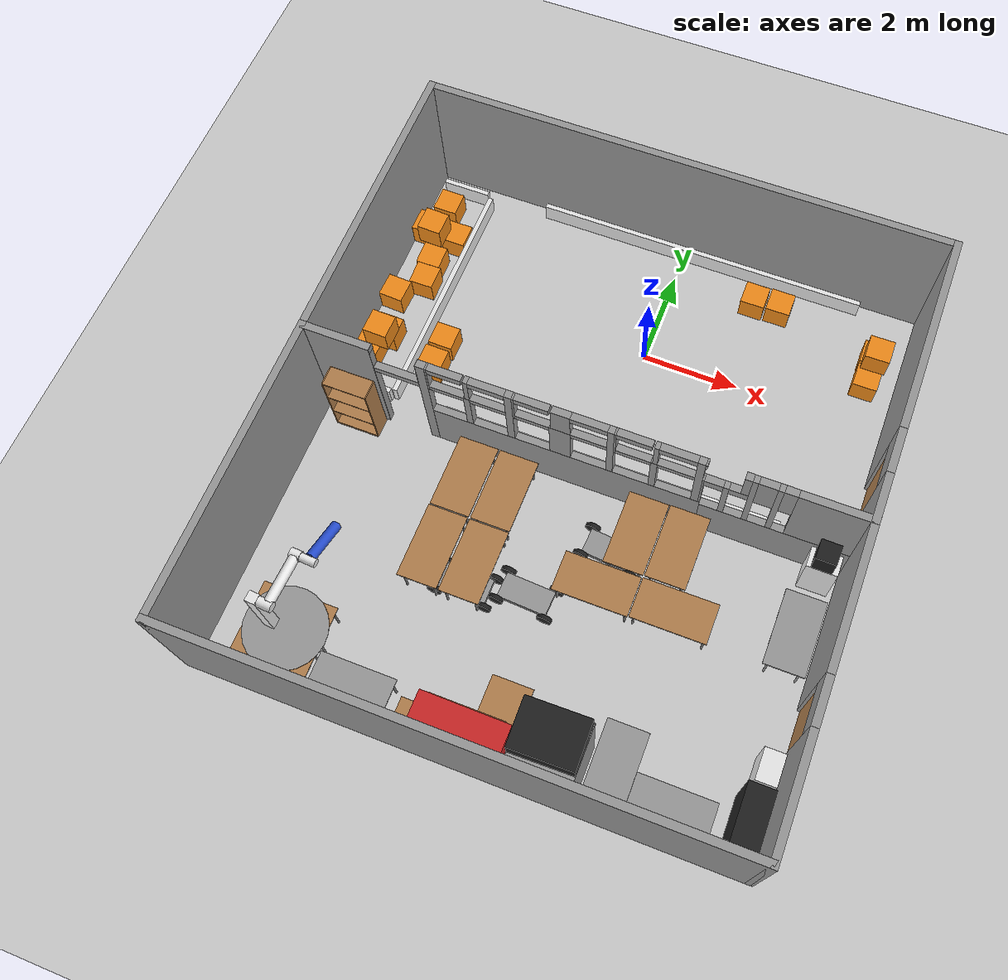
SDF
<sdf version="1.6">
 <world name="default">
  <light name="sun" type="directional">
   <pose>0 0 10 0 -0 0</pose>
   <diffuse>0.8 0.8 0.8 1</diffuse>
   <specular>0.2 0.2 0.2 1</specular>
   <attenuation>
    <range>1000</range>
    <constant>0.9</constant>
    <linear>0.01</linear>
    <quadratic>0.001</quadratic>
   </attenuation>
   <direction>-0.5 0.1 -0.9</direction>
  </light>
  <model name="ground_plane">
   <static>1</static>
   <link name="link">
    <collision name="collision">
     <geometry><plane><normal>0 0 1</normal><size>100 100</size></plane></geometry>
     <surface>
      <contact><collide_bitmask>65535</collide_bitmask></contact>
      <friction><ode><mu>100</mu><mu2>50</mu2></ode></friction>
     </surface>
    </collision>
    <visual name="visual">
     <cast_shadows>0</cast_shadows>
     <geometry><plane><normal>0 0 1</normal><size>100 100</size></plane></geometry>
     <material>
      <script><uri>file://media/materials/scripts/gazebo.material</uri><name>Gazebo/Grey</name></script>
     </material>
    </visual>
   </link>
  </model>
  <gravity>0 0 -9.8</gravity>
  <magnetic_field>6e-06 2.3e-05 -4.2e-05</magnetic_field>
  <atmosphere type="adiabatic"/>
  <physics name="default_physics" default="0" type="ode">
   <max_step_size>0.001</max_step_size>
   <real_time_factor>1</real_time_factor>
   <real_time_update_rate>1000</real_time_update_rate>
  </physics>
  <scene><ambient>0.4 0.4 0.4 1</ambient><background>0.7 0.7 0.7 1</background><shadows>1</shadows></scene>
  <audio><device>default</device></audio>
  <spherical_coordinates>
   <surface_model>EARTH_WGS84</surface_model>
   <latitude_deg>0</latitude_deg>
   <longitude_deg>0</longitude_deg>
   <elevation>0</elevation>
   <heading_deg>0</heading_deg>
  </spherical_coordinates>
  <model name="nrsl">
   <link name="Wall_0">
    <visual name="Wall_0_Visual_4">
     <pose>3.95421 0 0.5715 0 -0 0</pose>
     <geometry><box><size>3.06158 0.15 1.143</size></box></geometry>
     <material>
      <script><uri>file://media/materials/scripts/gazebo.material</uri><name>Gazebo/Grey</name></script>
      <ambient>1 1 1 1</ambient>
     </material>
     <meta><layer>0</layer></meta>
    </visual>
    <visual name="Wall_0_Visual_0">
     <pose>-4.76404 0 1.45 0 -0 0</pose>
     <geometry><box><size>1.44191 0.15 2.9</size></box></geometry>
     <material>
      <script><uri>file://media/materials/scripts/gazebo.material</uri><name>Gazebo/Grey</name></script>
      <ambient>1 1 1 1</ambient>
     </material>
     <meta><layer>0</layer></meta>
    </visual>
    <visual name="Wall_0_Visual_1">
     <pose>-3.03679 0 1.45 0 -0 0</pose>
     <geometry><box><size>0.178425 0.15 2.9</size></box></geometry>
     <material>
      <script><uri>file://media/materials/scripts/gazebo.material</uri><name>Gazebo/Grey</name></script>
      <ambient>1 1 1 1</ambient>
     </material>
     <meta><layer>0</layer></meta>
    </visual>
    <visual name="Wall_0_Visual_2">
     <pose>-4.03954 0 1.125 0 -0 0</pose>
     <geometry><box><size>0.007089 0.15 2.25</size></box></geometry>
     <material>
      <script><uri>file://media/materials/scripts/gazebo.material</uri><name>Gazebo/Grey</name></script>
      <ambient>1 1 1 1</ambient>
     </material>
     <meta><layer>0</layer></meta>
    </visual>
    <visual name="Wall_0_Visual_3">
     <pose>-0.262077 0 0.6225 0 -0 0</pose>
     <geometry><box><size>5.371 0.15 1.245</size></box></geometry>
     <material>
      <script><uri>file://media/materials/scripts/gazebo.material</uri><name>Gazebo/Grey</name></script>
      <ambient>1 1 1 1</ambient>
     </material>
     <meta><layer>0</layer></meta>
    </visual>
    <visual name="Wall_0_Visual_5">
     <pose>2.83264 0 1.6965 0 -0 0</pose>
     <geometry><box><size>0.106435 0.15 1.107</size></box></geometry>
     <material>
      <script><uri>file://media/materials/scripts/gazebo.material</uri><name>Gazebo/Grey</name></script>
      <ambient>1 1 1 1</ambient>
     </material>
     <meta><layer>0</layer></meta>
    </visual>
    <visual name="Wall_0_Visual_6">
     <pose>3.29507 0 2.0215 0 -0 0</pose>
     <geometry><box><size>0.106435 0.15 1.757</size></box></geometry>
     <material>
      <script><uri>file://media/materials/scripts/gazebo.material</uri><name>Gazebo/Grey</name></script>
      <ambient>1 1 1 1</ambient>
     </material>
     <meta><layer>0</layer></meta>
    </visual>
    <visual name="Wall_0_Visual_7">
     <pose>3.75733 0 2.0215 0 -0 0</pose>
     <geometry><box><size>0.106077 0.15 1.757</size></box></geometry>
     <material>
      <script><uri>file://media/materials/scripts/gazebo.material</uri><name>Gazebo/Grey</name></script>
      <ambient>1 1 1 1</ambient>
     </material>
     <meta><layer>0</layer></meta>
    </visual>
    <visual name="Wall_0_Visual_8">
     <pose>4.77268 0 2.0215 0 -0 0</pose>
     <geometry><box><size>1.42463 0.15 1.757</size></box></geometry>
     <material>
      <script><uri>file://media/materials/scripts/gazebo.material</uri><name>Gazebo/Grey</name></script>
      <ambient>1 1 1 1</ambient>
     </material>
     <meta><layer>0</layer></meta>
    </visual>
    <visual name="Wall_0_Visual_9">
     <pose>-2.17411 0 1.7475 0 -0 0</pose>
     <geometry><box><size>0.124939 0.15 1.005</size></box></geometry>
     <material>
      <script><uri>file://media/materials/scripts/gazebo.material</uri><name>Gazebo/Grey</name></script>
      <ambient>1 1 1 1</ambient>
     </material>
     <meta><layer>0</layer></meta>
    </visual>
    <visual name="Wall_0_Visual_10">
     <pose>-1.32902 0 2.0725 0 -0 0</pose>
     <geometry><box><size>0.143225 0.15 1.655</size></box></geometry>
     <material>
      <script><uri>file://media/materials/scripts/gazebo.material</uri><name>Gazebo/Grey</name></script>
      <ambient>1 1 1 1</ambient>
     </material>
     <meta><layer>0</layer></meta>
    </visual>
    <visual name="Wall_0_Visual_11">
     <pose>-0.342403 0 1.7475 0 -0 0</pose>
     <geometry><box><size>0.410015 0.15 1.005</size></box></geometry>
     <material>
      <script><uri>file://media/materials/scripts/gazebo.material</uri><name>Gazebo/Grey</name></script>
      <ambient>1 1 1 1</ambient>
     </material>
     <meta><layer>0</layer></meta>
    </visual>
    <visual name="Wall_0_Visual_12">
     <pose>0.636074 0 2.0725 0 -0 0</pose>
     <geometry><box><size>0.12494 0.15 1.655</size></box></geometry>
     <material>
      <script><uri>file://media/materials/scripts/gazebo.material</uri><name>Gazebo/Grey</name></script>
      <ambient>1 1 1 1</ambient>
     </material>
     <meta><layer>0</layer></meta>
    </visual>
    <visual name="Wall_0_Visual_13">
     <pose>1.47201 0 1.7475 0 -0 0</pose>
     <geometry><box><size>0.12494 0.15 1.005</size></box></geometry>
     <material>
      <script><uri>file://media/materials/scripts/gazebo.material</uri><name>Gazebo/Grey</name></script>
      <ambient>1 1 1 1</ambient>
     </material>
     <meta><layer>0</layer></meta>
    </visual>
    <visual name="Wall_0_Visual_14">
     <pose>2.31685 0 2.0725 0 -0 0</pose>
     <geometry><box><size>0.142725 0.15 1.655</size></box></geometry>
     <material>
      <script><uri>file://media/materials/scripts/gazebo.material</uri><name>Gazebo/Grey</name></script>
      <ambient>1 1 1 1</ambient>
     </material>
     <meta><layer>0</layer></meta>
    </visual>
    <visual name="Wall_0_Visual_15">
     <pose>2.40582 0 1.7475 0 -0 0</pose>
     <geometry><box><size>0.035213 0.15 1.005</size></box></geometry>
     <material>
      <script><uri>file://media/materials/scripts/gazebo.material</uri><name>Gazebo/Grey</name></script>
      <ambient>1 1 1 1</ambient>
     </material>
     <meta><layer>0</layer></meta>
    </visual>
    <visual name="Wall_0_Visual_16">
     <pose>3.06386 0 2.1535 0 -0 0</pose>
     <geometry><box><size>0.356 0.15 0.193</size></box></geometry>
     <material>
      <script><uri>file://media/materials/scripts/gazebo.material</uri><name>Gazebo/Grey</name></script>
      <ambient>1 1 1 1</ambient>
     </material>
     <meta><layer>0</layer></meta>
    </visual>
    <visual name="Wall_0_Visual_17">
     <pose>3.52629 0 2.4785 0 -0 0</pose>
     <geometry><box><size>0.356 0.15 0.843</size></box></geometry>
     <material>
      <script><uri>file://media/materials/scripts/gazebo.material</uri><name>Gazebo/Grey</name></script>
      <ambient>1 1 1 1</ambient>
     </material>
     <meta><layer>0</layer></meta>
    </visual>
    <visual name="Wall_0_Visual_18">
     <pose>3.93537 0 2.4785 0 -0 0</pose>
     <geometry><box><size>0.25 0.15 0.843</size></box></geometry>
     <material>
      <script><uri>file://media/materials/scripts/gazebo.material</uri><name>Gazebo/Grey</name></script>
      <ambient>1 1 1 1</ambient>
     </material>
     <meta><layer>0</layer></meta>
    </visual>
    <visual name="Wall_0_Visual_19">
     <pose>2.60142 0 2.1535 0 -0 0</pose>
     <geometry><box><size>0.356 0.15 0.193</size></box></geometry>
     <material>
      <script><uri>file://media/materials/scripts/gazebo.material</uri><name>Gazebo/Grey</name></script>
      <ambient>1 1 1 1</ambient>
     </material>
     <meta><layer>0</layer></meta>
    </visual>
    <visual name="Wall_0_Visual_20">
     <pose>-3.581 0 2.179 0 -0 0</pose>
     <geometry><box><size>0.91 0.15 0.142</size></box></geometry>
     <material>
      <script><uri>file://media/materials/scripts/gazebo.material</uri><name>Gazebo/Grey</name></script>
      <ambient>1 1 1 1</ambient>
     </material>
     <meta><layer>0</layer></meta>
    </visual>
    <visual name="Wall_0_Visual_21">
     <pose>-2.92979 0 2.517 0 -0 0</pose>
     <geometry><box><size>0.035572 0.15 0.766</size></box></geometry>
     <material>
      <script><uri>file://media/materials/scripts/gazebo.material</uri><name>Gazebo/Grey</name></script>
      <ambient>1 1 1 1</ambient>
     </material>
     <meta><layer>0</layer></meta>
    </visual>
    <visual name="Wall_0_Visual_22">
     <pose>-1.75614 0 2.192 0 -0 0</pose>
     <geometry><box><size>0.711 0.15 0.116</size></box></geometry>
     <material>
      <script><uri>file://media/materials/scripts/gazebo.material</uri><name>Gazebo/Grey</name></script>
      <ambient>1 1 1 1</ambient>
     </material>
     <meta><layer>0</layer></meta>
    </visual>
    <visual name="Wall_0_Visual_23">
     <pose>-1.23962 0 2.517 0 -0 0</pose>
     <geometry><box><size>0.035572 0.15 0.766</size></box></geometry>
     <material>
      <script><uri>file://media/materials/scripts/gazebo.material</uri><name>Gazebo/Grey</name></script>
      <ambient>1 1 1 1</ambient>
     </material>
     <meta><layer>0</layer></meta>
    </visual>
    <visual name="Wall_0_Visual_24">
     <pose>0.218104 0 2.192 0 -0 0</pose>
     <geometry><box><size>0.711 0.15 0.116</size></box></geometry>
     <material>
      <script><uri>file://media/materials/scripts/gazebo.material</uri><name>Gazebo/Grey</name></script>
      <ambient>1 1 1 1</ambient>
     </material>
     <meta><layer>0</layer></meta>
    </visual>
    <visual name="Wall_0_Visual_25">
     <pose>0.71633 0 2.517 0 -0 0</pose>
     <geometry><box><size>0.035572 0.15 0.766</size></box></geometry>
     <material>
      <script><uri>file://media/materials/scripts/gazebo.material</uri><name>Gazebo/Grey</name></script>
      <ambient>1 1 1 1</ambient>
     </material>
     <meta><layer>0</layer></meta>
    </visual>
    <visual name="Wall_0_Visual_26">
     <pose>1.88998 0 2.192 0 -0 0</pose>
     <geometry><box><size>0.711 0.15 0.116</size></box></geometry>
     <material>
      <script><uri>file://media/materials/scripts/gazebo.material</uri><name>Gazebo/Grey</name></script>
      <ambient>1 1 1 1</ambient>
     </material>
     <meta><layer>0</layer></meta>
    </visual>
    <visual name="Wall_0_Visual_27">
     <pose>-2.57429 0 2.192 0 -0 0</pose>
     <geometry><box><size>0.675428 0.15 0.116</size></box></geometry>
     <material>
      <script><uri>file://media/materials/scripts/gazebo.material</uri><name>Gazebo/Grey</name></script>
      <ambient>1 1 1 1</ambient>
     </material>
     <meta><layer>0</layer></meta>
    </visual>
    <visual name="Wall_0_Visual_28">
     <pose>-0.884625 0 2.192 0 -0 0</pose>
     <geometry><box><size>0.674428 0.15 0.116</size></box></geometry>
     <material>
      <script><uri>file://media/materials/scripts/gazebo.material</uri><name>Gazebo/Grey</name></script>
      <ambient>1 1 1 1</ambient>
     </material>
     <meta><layer>0</layer></meta>
    </visual>
    <visual name="Wall_0_Visual_29">
     <pose>1.07183 0 2.192 0 -0 0</pose>
     <geometry><box><size>0.675428 0.15 0.116</size></box></geometry>
     <material>
      <script><uri>file://media/materials/scripts/gazebo.material</uri><name>Gazebo/Grey</name></script>
      <ambient>1 1 1 1</ambient>
     </material>
     <meta><layer>0</layer></meta>
    </visual>
    <visual name="Wall_0_Visual_30">
     <pose>-2.15632 0 2.575 0 -0 0</pose>
     <geometry><box><size>0.089368 0.15 0.65</size></box></geometry>
     <material>
      <script><uri>file://media/materials/scripts/gazebo.material</uri><name>Gazebo/Grey</name></script>
      <ambient>1 1 1 1</ambient>
     </material>
     <meta><layer>0</layer></meta>
    </visual>
    <visual name="Wall_0_Visual_31">
     <pose>-2.15632 0 2.575 0 -0 0</pose>
     <geometry><box><size>0.089368 0.15 0.65</size></box></geometry>
     <material>
      <script><uri>file://media/materials/scripts/gazebo.material</uri><name>Gazebo/Grey</name></script>
      <ambient>1 1 1 1</ambient>
     </material>
     <meta><layer>0</layer></meta>
    </visual>
    <visual name="Wall_0_Visual_32">
     <pose>-0.324617 0 2.575 0 -0 0</pose>
     <geometry><box><size>0.374443 0.15 0.65</size></box></geometry>
     <material>
      <script><uri>file://media/materials/scripts/gazebo.material</uri><name>Gazebo/Grey</name></script>
      <ambient>1 1 1 1</ambient>
     </material>
     <meta><layer>0</layer></meta>
    </visual>
    <visual name="Wall_0_Visual_33">
     <pose>-0.324617 0 2.575 0 -0 0</pose>
     <geometry><box><size>0.374443 0.15 0.65</size></box></geometry>
     <material>
      <script><uri>file://media/materials/scripts/gazebo.material</uri><name>Gazebo/Grey</name></script>
      <ambient>1 1 1 1</ambient>
     </material>
     <meta><layer>0</layer></meta>
    </visual>
    <visual name="Wall_0_Visual_34">
     <pose>1.4898 0 2.575 0 -0 0</pose>
     <geometry><box><size>0.089368 0.15 0.65</size></box></geometry>
     <material>
      <script><uri>file://media/materials/scripts/gazebo.material</uri><name>Gazebo/Grey</name></script>
      <ambient>1 1 1 1</ambient>
     </material>
     <meta><layer>0</layer></meta>
    </visual>
    <visual name="Wall_0_Visual_35">
     <pose>1.4898 0 2.575 0 -0 0</pose>
     <geometry><box><size>0.089368 0.15 0.65</size></box></geometry>
     <material>
      <script><uri>file://media/materials/scripts/gazebo.material</uri><name>Gazebo/Grey</name></script>
      <ambient>1 1 1 1</ambient>
     </material>
     <meta><layer>0</layer></meta>
    </visual>
    <visual name="Wall_0_Visual_36">
     <pose>3.17053 0 2.575 0 -0 0</pose>
     <geometry><box><size>0.142647 0.15 0.65</size></box></geometry>
     <material>
      <script><uri>file://media/materials/scripts/gazebo.material</uri><name>Gazebo/Grey</name></script>
      <ambient>1 1 1 1</ambient>
     </material>
     <meta><layer>0</layer></meta>
    </visual>
    <visual name="Wall_0_Visual_37">
     <pose>-3.12954 0 2.575 0 -0 0</pose>
     <geometry><box><size>0.007089 0.15 0.65</size></box></geometry>
     <material>
      <script><uri>file://media/materials/scripts/gazebo.material</uri><name>Gazebo/Grey</name></script>
      <ambient>1 1 1 1</ambient>
     </material>
     <meta><layer>0</layer></meta>
    </visual>
    <visual name="Wall_0_Visual_38">
     <pose>-3.12954 0 2.575 0 -0 0</pose>
     <geometry><box><size>0.007089 0.15 0.65</size></box></geometry>
     <material>
      <script><uri>file://media/materials/scripts/gazebo.material</uri><name>Gazebo/Grey</name></script>
      <ambient>1 1 1 1</ambient>
     </material>
     <meta><layer>0</layer></meta>
    </visual>
    <visual name="Wall_0_Visual_39">
     <pose>2.40582 0 2.825 0 -0 0</pose>
     <geometry><box><size>0.035213 0.15 0.15</size></box></geometry>
     <material>
      <script><uri>file://media/materials/scripts/gazebo.material</uri><name>Gazebo/Grey</name></script>
      <ambient>1 1 1 1</ambient>
     </material>
     <meta><layer>0</layer></meta>
    </visual>
    <visual name="Wall_0_Visual_40">
     <pose>-2.57429 0 2.825 0 -0 0</pose>
     <geometry><box><size>0.675428 0.15 0.15</size></box></geometry>
     <material>
      <script><uri>file://media/materials/scripts/gazebo.material</uri><name>Gazebo/Grey</name></script>
      <ambient>1 1 1 1</ambient>
     </material>
     <meta><layer>0</layer></meta>
    </visual>
    <visual name="Wall_0_Visual_41">
     <pose>-0.884625 0 2.825 0 -0 0</pose>
     <geometry><box><size>0.674428 0.15 0.15</size></box></geometry>
     <material>
      <script><uri>file://media/materials/scripts/gazebo.material</uri><name>Gazebo/Grey</name></script>
      <ambient>1 1 1 1</ambient>
     </material>
     <meta><layer>0</layer></meta>
    </visual>
    <visual name="Wall_0_Visual_42">
     <pose>1.07183 0 2.825 0 -0 0</pose>
     <geometry><box><size>0.675428 0.15 0.15</size></box></geometry>
     <material>
      <script><uri>file://media/materials/scripts/gazebo.material</uri><name>Gazebo/Grey</name></script>
      <ambient>1 1 1 1</ambient>
     </material>
     <meta><layer>0</layer></meta>
    </visual>
    <visual name="Wall_0_Visual_43">
     <pose>-1.75614 0 2.825 0 -0 0</pose>
     <geometry><box><size>0.711 0.15 0.15</size></box></geometry>
     <material>
      <script><uri>file://media/materials/scripts/gazebo.material</uri><name>Gazebo/Grey</name></script>
      <ambient>1 1 1 1</ambient>
     </material>
     <meta><layer>0</layer></meta>
    </visual>
    <visual name="Wall_0_Visual_44">
     <pose>-1.75614 0 2.825 0 -0 0</pose>
     <geometry><box><size>0.711 0.15 0.15</size></box></geometry>
     <material>
      <script><uri>file://media/materials/scripts/gazebo.material</uri><name>Gazebo/Grey</name></script>
      <ambient>1 1 1 1</ambient>
     </material>
     <meta><layer>0</layer></meta>
    </visual>
    <visual name="Wall_0_Visual_45">
     <pose>0.218104 0 2.825 0 -0 0</pose>
     <geometry><box><size>0.711 0.15 0.15</size></box></geometry>
     <material>
      <script><uri>file://media/materials/scripts/gazebo.material</uri><name>Gazebo/Grey</name></script>
      <ambient>1 1 1 1</ambient>
     </material>
     <meta><layer>0</layer></meta>
    </visual>
    <visual name="Wall_0_Visual_46">
     <pose>0.218104 0 2.825 0 -0 0</pose>
     <geometry><box><size>0.711 0.15 0.15</size></box></geometry>
     <material>
      <script><uri>file://media/materials/scripts/gazebo.material</uri><name>Gazebo/Grey</name></script>
      <ambient>1 1 1 1</ambient>
     </material>
     <meta><layer>0</layer></meta>
    </visual>
    <visual name="Wall_0_Visual_47">
     <pose>1.88998 0 2.825 0 -0 0</pose>
     <geometry><box><size>0.711 0.15 0.15</size></box></geometry>
     <material>
      <script><uri>file://media/materials/scripts/gazebo.material</uri><name>Gazebo/Grey</name></script>
      <ambient>1 1 1 1</ambient>
     </material>
     <meta><layer>0</layer></meta>
    </visual>
    <visual name="Wall_0_Visual_48">
     <pose>1.88998 0 2.825 0 -0 0</pose>
     <geometry><box><size>0.711 0.15 0.15</size></box></geometry>
     <material>
      <script><uri>file://media/materials/scripts/gazebo.material</uri><name>Gazebo/Grey</name></script>
      <ambient>1 1 1 1</ambient>
     </material>
     <meta><layer>0</layer></meta>
    </visual>
    <visual name="Wall_0_Visual_49">
     <pose>-4.03954 0 2.825 0 -0 0</pose>
     <geometry><box><size>0.007089 0.15 0.15</size></box></geometry>
     <material>
      <script><uri>file://media/materials/scripts/gazebo.material</uri><name>Gazebo/Grey</name></script>
      <ambient>1 1 1 1</ambient>
     </material>
     <meta><layer>0</layer></meta>
    </visual>
    <collision name="Wall_0_Collision_17">
     <pose>3.52629 0 2.4785 0 -0 0</pose>
     <geometry><box><size>0.356 0.15 0.843</size></box></geometry>
     <surface>
      <friction>
       <ode><mu>1</mu><mu2>1</mu2><fdir1>0 0 0</fdir1><slip1>0</slip1><slip2>0</slip2></ode>
       <torsional>
        <coefficient>1</coefficient>
        <patch_radius>0</patch_radius>
        <surface_radius>0</surface_radius>
        <use_patch_radius>1</use_patch_radius>
        <ode><slip>0</slip></ode>
       </torsional>
      </friction>
      <bounce><restitution_coefficient>0</restitution_coefficient><threshold>1e+06</threshold></bounce>
      <contact>
       <collide_without_contact>0</collide_without_contact>
       <collide_without_contact_bitmask>1</collide_without_contact_bitmask>
       <collide_bitmask>1</collide_bitmask>
       <ode>
        <soft_cfm>0</soft_cfm>
        <soft_erp>0.2</soft_erp>
        <kp>1e+13</kp>
        <kd>1</kd>
        <max_vel>0.01</max_vel>
        <min_depth>0</min_depth>
       </ode>
       <bullet>
        <split_impulse>1</split_impulse>
        <split_impulse_penetration_threshold>-0.01</split_impulse_penetration_threshold>
        <soft_cfm>0</soft_cfm>
        <soft_erp>0.2</soft_erp>
        <kp>1e+13</kp>
        <kd>1</kd>
       </bullet>
      </contact>
     </surface>
    </collision>
    <collision name="Wall_0_Collision_0">
     <pose>-4.76404 0 1.45 0 -0 0</pose>
     <geometry><box><size>1.44191 0.15 2.9</size></box></geometry>
     <surface>
      <friction>
       <ode><mu>1</mu><mu2>1</mu2><fdir1>0 0 0</fdir1><slip1>0</slip1><slip2>0</slip2></ode>
       <torsional>
        <coefficient>1</coefficient>
        <patch_radius>0</patch_radius>
        <surface_radius>0</surface_radius>
        <use_patch_radius>1</use_patch_radius>
        <ode><slip>0</slip></ode>
       </torsional>
      </friction>
      <bounce><restitution_coefficient>0</restitution_coefficient><threshold>1e+06</threshold></bounce>
      <contact>
       <collide_without_contact>0</collide_without_contact>
       <collide_without_contact_bitmask>1</collide_without_contact_bitmask>
       <collide_bitmask>1</collide_bitmask>
       <ode>
        <soft_cfm>0</soft_cfm>
        <soft_erp>0.2</soft_erp>
        <kp>1e+13</kp>
        <kd>1</kd>
        <max_vel>0.01</max_vel>
        <min_depth>0</min_depth>
       </ode>
       <bullet>
        <split_impulse>1</split_impulse>
        <split_impulse_penetration_threshold>-0.01</split_impulse_penetration_threshold>
        <soft_cfm>0</soft_cfm>
        <soft_erp>0.2</soft_erp>
        <kp>1e+13</kp>
        <kd>1</kd>
       </bullet>
      </contact>
     </surface>
    </collision>
    <collision name="Wall_0_Collision_1">
     <pose>-3.03679 0 1.45 0 -0 0</pose>
     <geometry><box><size>0.178425 0.15 2.9</size></box></geometry>
     <surface>
      <friction>
       <ode><mu>1</mu><mu2>1</mu2><fdir1>0 0 0</fdir1><slip1>0</slip1><slip2>0</slip2></ode>
       <torsional>
        <coefficient>1</coefficient>
        <patch_radius>0</patch_radius>
        <surface_radius>0</surface_radius>
        <use_patch_radius>1</use_patch_radius>
        <ode><slip>0</slip></ode>
       </torsional>
      </friction>
      <bounce><restitution_coefficient>0</restitution_coefficient><threshold>1e+06</threshold></bounce>
      <contact>
       <collide_without_contact>0</collide_without_contact>
       <collide_without_contact_bitmask>1</collide_without_contact_bitmask>
       <collide_bitmask>1</collide_bitmask>
       <ode>
        <soft_cfm>0</soft_cfm>
        <soft_erp>0.2</soft_erp>
        <kp>1e+13</kp>
        <kd>1</kd>
        <max_vel>0.01</max_vel>
        <min_depth>0</min_depth>
       </ode>
       <bullet>
        <split_impulse>1</split_impulse>
        <split_impulse_penetration_threshold>-0.01</split_impulse_penetration_threshold>
        <soft_cfm>0</soft_cfm>
        <soft_erp>0.2</soft_erp>
        <kp>1e+13</kp>
        <kd>1</kd>
       </bullet>
      </contact>
     </surface>
    </collision>
    <collision name="Wall_0_Collision_2">
     <pose>-4.03954 0 1.125 0 -0 0</pose>
     <geometry><box><size>0.007089 0.15 2.25</size></box></geometry>
     <surface>
      <friction>
       <ode><mu>1</mu><mu2>1</mu2><fdir1>0 0 0</fdir1><slip1>0</slip1><slip2>0</slip2></ode>
       <torsional>
        <coefficient>1</coefficient>
        <patch_radius>0</patch_radius>
        <surface_radius>0</surface_radius>
        <use_patch_radius>1</use_patch_radius>
        <ode><slip>0</slip></ode>
       </torsional>
      </friction>
      <bounce><restitution_coefficient>0</restitution_coefficient><threshold>1e+06</threshold></bounce>
      <contact>
       <collide_without_contact>0</collide_without_contact>
       <collide_without_contact_bitmask>1</collide_without_contact_bitmask>
       <collide_bitmask>1</collide_bitmask>
       <ode>
        <soft_cfm>0</soft_cfm>
        <soft_erp>0.2</soft_erp>
        <kp>1e+13</kp>
        <kd>1</kd>
        <max_vel>0.01</max_vel>
        <min_depth>0</min_depth>
       </ode>
       <bullet>
        <split_impulse>1</split_impulse>
        <split_impulse_penetration_threshold>-0.01</split_impulse_penetration_threshold>
        <soft_cfm>0</soft_cfm>
        <soft_erp>0.2</soft_erp>
        <kp>1e+13</kp>
        <kd>1</kd>
       </bullet>
      </contact>
     </surface>
    </collision>
    <collision name="Wall_0_Collision_3">
     <pose>-0.262077 0 0.6225 0 -0 0</pose>
     <geometry><box><size>5.371 0.15 1.245</size></box></geometry>
     <surface>
      <friction>
       <ode><mu>1</mu><mu2>1</mu2><fdir1>0 0 0</fdir1><slip1>0</slip1><slip2>0</slip2></ode>
       <torsional>
        <coefficient>1</coefficient>
        <patch_radius>0</patch_radius>
        <surface_radius>0</surface_radius>
        <use_patch_radius>1</use_patch_radius>
        <ode><slip>0</slip></ode>
       </torsional>
      </friction>
      <bounce><restitution_coefficient>0</restitution_coefficient><threshold>1e+06</threshold></bounce>
      <contact>
       <collide_without_contact>0</collide_without_contact>
       <collide_without_contact_bitmask>1</collide_without_contact_bitmask>
       <collide_bitmask>1</collide_bitmask>
       <ode>
        <soft_cfm>0</soft_cfm>
        <soft_erp>0.2</soft_erp>
        <kp>1e+13</kp>
        <kd>1</kd>
        <max_vel>0.01</max_vel>
        <min_depth>0</min_depth>
       </ode>
       <bullet>
        <split_impulse>1</split_impulse>
        <split_impulse_penetration_threshold>-0.01</split_impulse_penetration_threshold>
        <soft_cfm>0</soft_cfm>
        <soft_erp>0.2</soft_erp>
        <kp>1e+13</kp>
        <kd>1</kd>
       </bullet>
      </contact>
     </surface>
    </collision>
    <collision name="Wall_0_Collision_4">
     <pose>3.95421 0 0.5715 0 -0 0</pose>
     <geometry><box><size>3.06158 0.15 1.143</size></box></geometry>
     <surface>
      <friction>
       <ode><mu>1</mu><mu2>1</mu2><fdir1>0 0 0</fdir1><slip1>0</slip1><slip2>0</slip2></ode>
       <torsional>
        <coefficient>1</coefficient>
        <patch_radius>0</patch_radius>
        <surface_radius>0</surface_radius>
        <use_patch_radius>1</use_patch_radius>
        <ode><slip>0</slip></ode>
       </torsional>
      </friction>
      <bounce><restitution_coefficient>0</restitution_coefficient><threshold>1e+06</threshold></bounce>
      <contact>
       <collide_without_contact>0</collide_without_contact>
       <collide_without_contact_bitmask>1</collide_without_contact_bitmask>
       <collide_bitmask>1</collide_bitmask>
       <ode>
        <soft_cfm>0</soft_cfm>
        <soft_erp>0.2</soft_erp>
        <kp>1e+13</kp>
        <kd>1</kd>
        <max_vel>0.01</max_vel>
        <min_depth>0</min_depth>
       </ode>
       <bullet>
        <split_impulse>1</split_impulse>
        <split_impulse_penetration_threshold>-0.01</split_impulse_penetration_threshold>
        <soft_cfm>0</soft_cfm>
        <soft_erp>0.2</soft_erp>
        <kp>1e+13</kp>
        <kd>1</kd>
       </bullet>
      </contact>
     </surface>
    </collision>
    <collision name="Wall_0_Collision_5">
     <pose>2.83264 0 1.6965 0 -0 0</pose>
     <geometry><box><size>0.106435 0.15 1.107</size></box></geometry>
     <surface>
      <friction>
       <ode><mu>1</mu><mu2>1</mu2><fdir1>0 0 0</fdir1><slip1>0</slip1><slip2>0</slip2></ode>
       <torsional>
        <coefficient>1</coefficient>
        <patch_radius>0</patch_radius>
        <surface_radius>0</surface_radius>
        <use_patch_radius>1</use_patch_radius>
        <ode><slip>0</slip></ode>
       </torsional>
      </friction>
      <bounce><restitution_coefficient>0</restitution_coefficient><threshold>1e+06</threshold></bounce>
      <contact>
       <collide_without_contact>0</collide_without_contact>
       <collide_without_contact_bitmask>1</collide_without_contact_bitmask>
       <collide_bitmask>1</collide_bitmask>
       <ode>
        <soft_cfm>0</soft_cfm>
        <soft_erp>0.2</soft_erp>
        <kp>1e+13</kp>
        <kd>1</kd>
        <max_vel>0.01</max_vel>
        <min_depth>0</min_depth>
       </ode>
       <bullet>
        <split_impulse>1</split_impulse>
        <split_impulse_penetration_threshold>-0.01</split_impulse_penetration_threshold>
        <soft_cfm>0</soft_cfm>
        <soft_erp>0.2</soft_erp>
        <kp>1e+13</kp>
        <kd>1</kd>
       </bullet>
      </contact>
     </surface>
    </collision>
    <collision name="Wall_0_Collision_6">
     <pose>3.29507 0 2.0215 0 -0 0</pose>
     <geometry><box><size>0.106435 0.15 1.757</size></box></geometry>
     <surface>
      <friction>
       <ode><mu>1</mu><mu2>1</mu2><fdir1>0 0 0</fdir1><slip1>0</slip1><slip2>0</slip2></ode>
       <torsional>
        <coefficient>1</coefficient>
        <patch_radius>0</patch_radius>
        <surface_radius>0</surface_radius>
        <use_patch_radius>1</use_patch_radius>
        <ode><slip>0</slip></ode>
       </torsional>
      </friction>
      <bounce><restitution_coefficient>0</restitution_coefficient><threshold>1e+06</threshold></bounce>
      <contact>
       <collide_without_contact>0</collide_without_contact>
       <collide_without_contact_bitmask>1</collide_without_contact_bitmask>
       <collide_bitmask>1</collide_bitmask>
       <ode>
        <soft_cfm>0</soft_cfm>
        <soft_erp>0.2</soft_erp>
        <kp>1e+13</kp>
        <kd>1</kd>
        <max_vel>0.01</max_vel>
        <min_depth>0</min_depth>
       </ode>
       <bullet>
        <split_impulse>1</split_impulse>
        <split_impulse_penetration_threshold>-0.01</split_impulse_penetration_threshold>
        <soft_cfm>0</soft_cfm>
        <soft_erp>0.2</soft_erp>
        <kp>1e+13</kp>
        <kd>1</kd>
       </bullet>
      </contact>
     </surface>
    </collision>
    <collision name="Wall_0_Collision_7">
     <pose>3.75733 0 2.0215 0 -0 0</pose>
     <geometry><box><size>0.106077 0.15 1.757</size></box></geometry>
     <surface>
      <friction>
       <ode><mu>1</mu><mu2>1</mu2><fdir1>0 0 0</fdir1><slip1>0</slip1><slip2>0</slip2></ode>
       <torsional>
        <coefficient>1</coefficient>
        <patch_radius>0</patch_radius>
        <surface_radius>0</surface_radius>
        <use_patch_radius>1</use_patch_radius>
        <ode><slip>0</slip></ode>
       </torsional>
      </friction>
      <bounce><restitution_coefficient>0</restitution_coefficient><threshold>1e+06</threshold></bounce>
      <contact>
       <collide_without_contact>0</collide_without_contact>
       <collide_without_contact_bitmask>1</collide_without_contact_bitmask>
       <collide_bitmask>1</collide_bitmask>
       <ode>
        <soft_cfm>0</soft_cfm>
        <soft_erp>0.2</soft_erp>
        <kp>1e+13</kp>
        <kd>1</kd>
        <max_vel>0.01</max_vel>
        <min_depth>0</min_depth>
       </ode>
       <bullet>
        <split_impulse>1</split_impulse>
        <split_impulse_penetration_threshold>-0.01</split_impulse_penetration_threshold>
        <soft_cfm>0</soft_cfm>
        <soft_erp>0.2</soft_erp>
        <kp>1e+13</kp>
        <kd>1</kd>
       </bullet>
      </contact>
     </surface>
    </collision>
    <collision name="Wall_0_Collision_8">
     <pose>4.77268 0 2.0215 0 -0 0</pose>
     <geometry><box><size>1.42463 0.15 1.757</size></box></geometry>
     <surface>
      <friction>
       <ode><mu>1</mu><mu2>1</mu2><fdir1>0 0 0</fdir1><slip1>0</slip1><slip2>0</slip2></ode>
       <torsional>
        <coefficient>1</coefficient>
        <patch_radius>0</patch_radius>
        <surface_radius>0</surface_radius>
        <use_patch_radius>1</use_patch_radius>
        <ode><slip>0</slip></ode>
       </torsional>
      </friction>
      <bounce><restitution_coefficient>0</restitution_coefficient><threshold>1e+06</threshold></bounce>
      <contact>
       <collide_without_contact>0</collide_without_contact>
       <collide_without_contact_bitmask>1</collide_without_contact_bitmask>
       <collide_bitmask>1</collide_bitmask>
       <ode>
        <soft_cfm>0</soft_cfm>
        <soft_erp>0.2</soft_erp>
        <kp>1e+13</kp>
        <kd>1</kd>
        <max_vel>0.01</max_vel>
        <min_depth>0</min_depth>
       </ode>
       <bullet>
        <split_impulse>1</split_impulse>
        <split_impulse_penetration_threshold>-0.01</split_impulse_penetration_threshold>
        <soft_cfm>0</soft_cfm>
        <soft_erp>0.2</soft_erp>
        <kp>1e+13</kp>
        <kd>1</kd>
       </bullet>
      </contact>
     </surface>
    </collision>
    <collision name="Wall_0_Collision_9">
     <pose>-2.17411 0 1.7475 0 -0 0</pose>
     <geometry><box><size>0.124939 0.15 1.005</size></box></geometry>
     <surface>
      <friction>
       <ode><mu>1</mu><mu2>1</mu2><fdir1>0 0 0</fdir1><slip1>0</slip1><slip2>0</slip2></ode>
       <torsional>
        <coefficient>1</coefficient>
        <patch_radius>0</patch_radius>
        <surface_radius>0</surface_radius>
        <use_patch_radius>1</use_patch_radius>
        <ode><slip>0</slip></ode>
       </torsional>
      </friction>
      <bounce><restitution_coefficient>0</restitution_coefficient><threshold>1e+06</threshold></bounce>
      <contact>
       <collide_without_contact>0</collide_without_contact>
       <collide_without_contact_bitmask>1</collide_without_contact_bitmask>
       <collide_bitmask>1</collide_bitmask>
       <ode>
        <soft_cfm>0</soft_cfm>
        <soft_erp>0.2</soft_erp>
        <kp>1e+13</kp>
        <kd>1</kd>
        <max_vel>0.01</max_vel>
        <min_depth>0</min_depth>
       </ode>
       <bullet>
        <split_impulse>1</split_impulse>
        <split_impulse_penetration_threshold>-0.01</split_impulse_penetration_threshold>
        <soft_cfm>0</soft_cfm>
        <soft_erp>0.2</soft_erp>
        <kp>1e+13</kp>
        <kd>1</kd>
       </bullet>
      </contact>
     </surface>
    </collision>
    <collision name="Wall_0_Collision_10">
     <pose>-1.32902 0 2.0725 0 -0 0</pose>
     <geometry><box><size>0.143225 0.15 1.655</size></box></geometry>
     <surface>
      <friction>
       <ode><mu>1</mu><mu2>1</mu2><fdir1>0 0 0</fdir1><slip1>0</slip1><slip2>0</slip2></ode>
       <torsional>
        <coefficient>1</coefficient>
        <patch_radius>0</patch_radius>
        <surface_radius>0</surface_radius>
        <use_patch_radius>1</use_patch_radius>
        <ode><slip>0</slip></ode>
       </torsional>
      </friction>
      <bounce><restitution_coefficient>0</restitution_coefficient><threshold>1e+06</threshold></bounce>
      <contact>
       <collide_without_contact>0</collide_without_contact>
       <collide_without_contact_bitmask>1</collide_without_contact_bitmask>
       <collide_bitmask>1</collide_bitmask>
       <ode>
        <soft_cfm>0</soft_cfm>
        <soft_erp>0.2</soft_erp>
        <kp>1e+13</kp>
        <kd>1</kd>
        <max_vel>0.01</max_vel>
        <min_depth>0</min_depth>
       </ode>
       <bullet>
        <split_impulse>1</split_impulse>
        <split_impulse_penetration_threshold>-0.01</split_impulse_penetration_threshold>
        <soft_cfm>0</soft_cfm>
        <soft_erp>0.2</soft_erp>
        <kp>1e+13</kp>
        <kd>1</kd>
       </bullet>
      </contact>
     </surface>
    </collision>
    <collision name="Wall_0_Collision_11">
     <pose>-0.342403 0 1.7475 0 -0 0</pose>
     <geometry><box><size>0.410015 0.15 1.005</size></box></geometry>
     <surface>
      <friction>
       <ode><mu>1</mu><mu2>1</mu2><fdir1>0 0 0</fdir1><slip1>0</slip1><slip2>0</slip2></ode>
       <torsional>
        <coefficient>1</coefficient>
        <patch_radius>0</patch_radius>
        <surface_radius>0</surface_radius>
        <use_patch_radius>1</use_patch_radius>
        <ode><slip>0</slip></ode>
       </torsional>
      </friction>
      <bounce><restitution_coefficient>0</restitution_coefficient><threshold>1e+06</threshold></bounce>
      <contact>
       <collide_without_contact>0</collide_without_contact>
       <collide_without_contact_bitmask>1</collide_without_contact_bitmask>
       <collide_bitmask>1</collide_bitmask>
       <ode>
        <soft_cfm>0</soft_cfm>
        <soft_erp>0.2</soft_erp>
        <kp>1e+13</kp>
        <kd>1</kd>
        <max_vel>0.01</max_vel>
        <min_depth>0</min_depth>
       </ode>
       <bullet>
        <split_impulse>1</split_impulse>
        <split_impulse_penetration_threshold>-0.01</split_impulse_penetration_threshold>
        <soft_cfm>0</soft_cfm>
        <soft_erp>0.2</soft_erp>
        <kp>1e+13</kp>
        <kd>1</kd>
       </bullet>
      </contact>
     </surface>
    </collision>
    <collision name="Wall_0_Collision_12">
     <pose>0.636074 0 2.0725 0 -0 0</pose>
     <geometry><box><size>0.12494 0.15 1.655</size></box></geometry>
     <surface>
      <friction>
       <ode><mu>1</mu><mu2>1</mu2><fdir1>0 0 0</fdir1><slip1>0</slip1><slip2>0</slip2></ode>
       <torsional>
        <coefficient>1</coefficient>
        <patch_radius>0</patch_radius>
        <surface_radius>0</surface_radius>
        <use_patch_radius>1</use_patch_radius>
        <ode><slip>0</slip></ode>
       </torsional>
      </friction>
      <bounce><restitution_coefficient>0</restitution_coefficient><threshold>1e+06</threshold></bounce>
      <contact>
       <collide_without_contact>0</collide_without_contact>
       <collide_without_contact_bitmask>1</collide_without_contact_bitmask>
       <collide_bitmask>1</collide_bitmask>
       <ode>
        <soft_cfm>0</soft_cfm>
        <soft_erp>0.2</soft_erp>
        <kp>1e+13</kp>
        <kd>1</kd>
        <max_vel>0.01</max_vel>
        <min_depth>0</min_depth>
       </ode>
       <bullet>
        <split_impulse>1</split_impulse>
        <split_impulse_penetration_threshold>-0.01</split_impulse_penetration_threshold>
        <soft_cfm>0</soft_cfm>
        <soft_erp>0.2</soft_erp>
        <kp>1e+13</kp>
        <kd>1</kd>
       </bullet>
      </contact>
     </surface>
    </collision>
    <collision name="Wall_0_Collision_13">
     <pose>1.47201 0 1.7475 0 -0 0</pose>
     <geometry><box><size>0.12494 0.15 1.005</size></box></geometry>
     <surface>
      <friction>
       <ode><mu>1</mu><mu2>1</mu2><fdir1>0 0 0</fdir1><slip1>0</slip1><slip2>0</slip2></ode>
       <torsional>
        <coefficient>1</coefficient>
        <patch_radius>0</patch_radius>
        <surface_radius>0</surface_radius>
        <use_patch_radius>1</use_patch_radius>
        <ode><slip>0</slip></ode>
       </torsional>
      </friction>
      <bounce><restitution_coefficient>0</restitution_coefficient><threshold>1e+06</threshold></bounce>
      <contact>
       <collide_without_contact>0</collide_without_contact>
       <collide_without_contact_bitmask>1</collide_without_contact_bitmask>
       <collide_bitmask>1</collide_bitmask>
       <ode>
        <soft_cfm>0</soft_cfm>
        <soft_erp>0.2</soft_erp>
        <kp>1e+13</kp>
        <kd>1</kd>
        <max_vel>0.01</max_vel>
        <min_depth>0</min_depth>
       </ode>
       <bullet>
        <split_impulse>1</split_impulse>
        <split_impulse_penetration_threshold>-0.01</split_impulse_penetration_threshold>
        <soft_cfm>0</soft_cfm>
        <soft_erp>0.2</soft_erp>
        <kp>1e+13</kp>
        <kd>1</kd>
       </bullet>
      </contact>
     </surface>
    </collision>
    <collision name="Wall_0_Collision_14">
     <pose>2.31685 0 2.0725 0 -0 0</pose>
     <geometry><box><size>0.142725 0.15 1.655</size></box></geometry>
     <surface>
      <friction>
       <ode><mu>1</mu><mu2>1</mu2><fdir1>0 0 0</fdir1><slip1>0</slip1><slip2>0</slip2></ode>
       <torsional>
        <coefficient>1</coefficient>
        <patch_radius>0</patch_radius>
        <surface_radius>0</surface_radius>
        <use_patch_radius>1</use_patch_radius>
        <ode><slip>0</slip></ode>
       </torsional>
      </friction>
      <bounce><restitution_coefficient>0</restitution_coefficient><threshold>1e+06</threshold></bounce>
      <contact>
       <collide_without_contact>0</collide_without_contact>
       <collide_without_contact_bitmask>1</collide_without_contact_bitmask>
       <collide_bitmask>1</collide_bitmask>
       <ode>
        <soft_cfm>0</soft_cfm>
        <soft_erp>0.2</soft_erp>
        <kp>1e+13</kp>
        <kd>1</kd>
        <max_vel>0.01</max_vel>
        <min_depth>0</min_depth>
       </ode>
       <bullet>
        <split_impulse>1</split_impulse>
        <split_impulse_penetration_threshold>-0.01</split_impulse_penetration_threshold>
        <soft_cfm>0</soft_cfm>
        <soft_erp>0.2</soft_erp>
        <kp>1e+13</kp>
        <kd>1</kd>
       </bullet>
      </contact>
     </surface>
    </collision>
    <collision name="Wall_0_Collision_15">
     <pose>2.40582 0 1.7475 0 -0 0</pose>
     <geometry><box><size>0.035213 0.15 1.005</size></box></geometry>
     <surface>
      <friction>
       <ode><mu>1</mu><mu2>1</mu2><fdir1>0 0 0</fdir1><slip1>0</slip1><slip2>0</slip2></ode>
       <torsional>
        <coefficient>1</coefficient>
        <patch_radius>0</patch_radius>
        <surface_radius>0</surface_radius>
        <use_patch_radius>1</use_patch_radius>
        <ode><slip>0</slip></ode>
       </torsional>
      </friction>
      <bounce><restitution_coefficient>0</restitution_coefficient><threshold>1e+06</threshold></bounce>
      <contact>
       <collide_without_contact>0</collide_without_contact>
       <collide_without_contact_bitmask>1</collide_without_contact_bitmask>
       <collide_bitmask>1</collide_bitmask>
       <ode>
        <soft_cfm>0</soft_cfm>
        <soft_erp>0.2</soft_erp>
        <kp>1e+13</kp>
        <kd>1</kd>
        <max_vel>0.01</max_vel>
        <min_depth>0</min_depth>
       </ode>
       <bullet>
        <split_impulse>1</split_impulse>
        <split_impulse_penetration_threshold>-0.01</split_impulse_penetration_threshold>
        <soft_cfm>0</soft_cfm>
        <soft_erp>0.2</soft_erp>
        <kp>1e+13</kp>
        <kd>1</kd>
       </bullet>
      </contact>
     </surface>
    </collision>
    <collision name="Wall_0_Collision_16">
     <pose>3.06386 0 2.1535 0 -0 0</pose>
     <geometry><box><size>0.356 0.15 0.193</size></box></geometry>
     <surface>
      <friction>
       <ode><mu>1</mu><mu2>1</mu2><fdir1>0 0 0</fdir1><slip1>0</slip1><slip2>0</slip2></ode>
       <torsional>
        <coefficient>1</coefficient>
        <patch_radius>0</patch_radius>
        <surface_radius>0</surface_radius>
        <use_patch_radius>1</use_patch_radius>
        <ode><slip>0</slip></ode>
       </torsional>
      </friction>
      <bounce><restitution_coefficient>0</restitution_coefficient><threshold>1e+06</threshold></bounce>
      <contact>
       <collide_without_contact>0</collide_without_contact>
       <collide_without_contact_bitmask>1</collide_without_contact_bitmask>
       <collide_bitmask>1</collide_bitmask>
       <ode>
        <soft_cfm>0</soft_cfm>
        <soft_erp>0.2</soft_erp>
        <kp>1e+13</kp>
        <kd>1</kd>
        <max_vel>0.01</max_vel>
        <min_depth>0</min_depth>
       </ode>
       <bullet>
        <split_impulse>1</split_impulse>
        <split_impulse_penetration_threshold>-0.01</split_impulse_penetration_threshold>
        <soft_cfm>0</soft_cfm>
        <soft_erp>0.2</soft_erp>
        <kp>1e+13</kp>
        <kd>1</kd>
       </bullet>
      </contact>
     </surface>
    </collision>
    <collision name="Wall_0_Collision_18">
     <pose>3.93537 0 2.4785 0 -0 0</pose>
     <geometry><box><size>0.25 0.15 0.843</size></box></geometry>
     <surface>
      <friction>
       <ode><mu>1</mu><mu2>1</mu2><fdir1>0 0 0</fdir1><slip1>0</slip1><slip2>0</slip2></ode>
       <torsional>
        <coefficient>1</coefficient>
        <patch_radius>0</patch_radius>
        <surface_radius>0</surface_radius>
        <use_patch_radius>1</use_patch_radius>
        <ode><slip>0</slip></ode>
       </torsional>
      </friction>
      <bounce><restitution_coefficient>0</restitution_coefficient><threshold>1e+06</threshold></bounce>
      <contact>
       <collide_without_contact>0</collide_without_contact>
       <collide_without_contact_bitmask>1</collide_without_contact_bitmask>
       <collide_bitmask>1</collide_bitmask>
       <ode>
        <soft_cfm>0</soft_cfm>
        <soft_erp>0.2</soft_erp>
        <kp>1e+13</kp>
        <kd>1</kd>
        <max_vel>0.01</max_vel>
        <min_depth>0</min_depth>
       </ode>
       <bullet>
        <split_impulse>1</split_impulse>
        <split_impulse_penetration_threshold>-0.01</split_impulse_penetration_threshold>
        <soft_cfm>0</soft_cfm>
        <soft_erp>0.2</soft_erp>
        <kp>1e+13</kp>
        <kd>1</kd>
       </bullet>
      </contact>
     </surface>
    </collision>
    <collision name="Wall_0_Collision_19">
     <pose>2.60142 0 2.1535 0 -0 0</pose>
     <geometry><box><size>0.356 0.15 0.193</size></box></geometry>
     <surface>
      <friction>
       <ode><mu>1</mu><mu2>1</mu2><fdir1>0 0 0</fdir1><slip1>0</slip1><slip2>0</slip2></ode>
       <torsional>
        <coefficient>1</coefficient>
        <patch_radius>0</patch_radius>
        <surface_radius>0</surface_radius>
        <use_patch_radius>1</use_patch_radius>
        <ode><slip>0</slip></ode>
       </torsional>
      </friction>
      <bounce><restitution_coefficient>0</restitution_coefficient><threshold>1e+06</threshold></bounce>
      <contact>
       <collide_without_contact>0</collide_without_contact>
       <collide_without_contact_bitmask>1</collide_without_contact_bitmask>
       <collide_bitmask>1</collide_bitmask>
       <ode>
        <soft_cfm>0</soft_cfm>
        <soft_erp>0.2</soft_erp>
        <kp>1e+13</kp>
        <kd>1</kd>
        <max_vel>0.01</max_vel>
        <min_depth>0</min_depth>
       </ode>
       <bullet>
        <split_impulse>1</split_impulse>
        <split_impulse_penetration_threshold>-0.01</split_impulse_penetration_threshold>
        <soft_cfm>0</soft_cfm>
        <soft_erp>0.2</soft_erp>
        <kp>1e+13</kp>
        <kd>1</kd>
       </bullet>
      </contact>
     </surface>
    </collision>
    <collision name="Wall_0_Collision_20">
     <pose>-3.581 0 2.179 0 -0 0</pose>
     <geometry><box><size>0.91 0.15 0.142</size></box></geometry>
     <surface>
      <friction>
       <ode><mu>1</mu><mu2>1</mu2><fdir1>0 0 0</fdir1><slip1>0</slip1><slip2>0</slip2></ode>
       <torsional>
        <coefficient>1</coefficient>
        <patch_radius>0</patch_radius>
        <surface_radius>0</surface_radius>
        <use_patch_radius>1</use_patch_radius>
        <ode><slip>0</slip></ode>
       </torsional>
      </friction>
      <bounce><restitution_coefficient>0</restitution_coefficient><threshold>1e+06</threshold></bounce>
      <contact>
       <collide_without_contact>0</collide_without_contact>
       <collide_without_contact_bitmask>1</collide_without_contact_bitmask>
       <collide_bitmask>1</collide_bitmask>
       <ode>
        <soft_cfm>0</soft_cfm>
        <soft_erp>0.2</soft_erp>
        <kp>1e+13</kp>
        <kd>1</kd>
        <max_vel>0.01</max_vel>
        <min_depth>0</min_depth>
       </ode>
       <bullet>
        <split_impulse>1</split_impulse>
        <split_impulse_penetration_threshold>-0.01</split_impulse_penetration_threshold>
        <soft_cfm>0</soft_cfm>
        <soft_erp>0.2</soft_erp>
        <kp>1e+13</kp>
        <kd>1</kd>
       </bullet>
      </contact>
     </surface>
    </collision>
    <collision name="Wall_0_Collision_21">
     <pose>-2.92979 0 2.517 0 -0 0</pose>
     <geometry><box><size>0.035572 0.15 0.766</size></box></geometry>
     <surface>
      <friction>
       <ode><mu>1</mu><mu2>1</mu2><fdir1>0 0 0</fdir1><slip1>0</slip1><slip2>0</slip2></ode>
       <torsional>
        <coefficient>1</coefficient>
        <patch_radius>0</patch_radius>
        <surface_radius>0</surface_radius>
        <use_patch_radius>1</use_patch_radius>
        <ode><slip>0</slip></ode>
       </torsional>
      </friction>
      <bounce><restitution_coefficient>0</restitution_coefficient><threshold>1e+06</threshold></bounce>
      <contact>
       <collide_without_contact>0</collide_without_contact>
       <collide_without_contact_bitmask>1</collide_without_contact_bitmask>
       <collide_bitmask>1</collide_bitmask>
       <ode>
        <soft_cfm>0</soft_cfm>
        <soft_erp>0.2</soft_erp>
        <kp>1e+13</kp>
        <kd>1</kd>
        <max_vel>0.01</max_vel>
        <min_depth>0</min_depth>
       </ode>
       <bullet>
        <split_impulse>1</split_impulse>
        <split_impulse_penetration_threshold>-0.01</split_impulse_penetration_threshold>
        <soft_cfm>0</soft_cfm>
        <soft_erp>0.2</soft_erp>
        <kp>1e+13</kp>
        <kd>1</kd>
       </bullet>
      </contact>
     </surface>
    </collision>
    <collision name="Wall_0_Collision_22">
     <pose>-1.75614 0 2.192 0 -0 0</pose>
     <geometry><box><size>0.711 0.15 0.116</size></box></geometry>
     <surface>
      <friction>
       <ode><mu>1</mu><mu2>1</mu2><fdir1>0 0 0</fdir1><slip1>0</slip1><slip2>0</slip2></ode>
       <torsional>
        <coefficient>1</coefficient>
        <patch_radius>0</patch_radius>
        <surface_radius>0</surface_radius>
        <use_patch_radius>1</use_patch_radius>
        <ode><slip>0</slip></ode>
       </torsional>
      </friction>
      <bounce><restitution_coefficient>0</restitution_coefficient><threshold>1e+06</threshold></bounce>
      <contact>
       <collide_without_contact>0</collide_without_contact>
       <collide_without_contact_bitmask>1</collide_without_contact_bitmask>
       <collide_bitmask>1</collide_bitmask>
       <ode>
        <soft_cfm>0</soft_cfm>
        <soft_erp>0.2</soft_erp>
        <kp>1e+13</kp>
        <kd>1</kd>
        <max_vel>0.01</max_vel>
        <min_depth>0</min_depth>
       </ode>
       <bullet>
        <split_impulse>1</split_impulse>
        <split_impulse_penetration_threshold>-0.01</split_impulse_penetration_threshold>
        <soft_cfm>0</soft_cfm>
        <soft_erp>0.2</soft_erp>
        <kp>1e+13</kp>
        <kd>1</kd>
       </bullet>
      </contact>
     </surface>
    </collision>
    <collision name="Wall_0_Collision_23">
     <pose>-1.23962 0 2.517 0 -0 0</pose>
     <geometry><box><size>0.035572 0.15 0.766</size></box></geometry>
     <surface>
      <friction>
       <ode><mu>1</mu><mu2>1</mu2><fdir1>0 0 0</fdir1><slip1>0</slip1><slip2>0</slip2></ode>
       <torsional>
        <coefficient>1</coefficient>
        <patch_radius>0</patch_radius>
        <surface_radius>0</surface_radius>
        <use_patch_radius>1</use_patch_radius>
        <ode><slip>0</slip></ode>
       </torsional>
      </friction>
      <bounce><restitution_coefficient>0</restitution_coefficient><threshold>1e+06</threshold></bounce>
      <contact>
       <collide_without_contact>0</collide_without_contact>
       <collide_without_contact_bitmask>1</collide_without_contact_bitmask>
       <collide_bitmask>1</collide_bitmask>
       <ode>
        <soft_cfm>0</soft_cfm>
        <soft_erp>0.2</soft_erp>
        <kp>1e+13</kp>
        <kd>1</kd>
        <max_vel>0.01</max_vel>
        <min_depth>0</min_depth>
       </ode>
       <bullet>
        <split_impulse>1</split_impulse>
        <split_impulse_penetration_threshold>-0.01</split_impulse_penetration_threshold>
        <soft_cfm>0</soft_cfm>
        <soft_erp>0.2</soft_erp>
        <kp>1e+13</kp>
        <kd>1</kd>
       </bullet>
      </contact>
     </surface>
    </collision>
    <collision name="Wall_0_Collision_24">
     <pose>0.218104 0 2.192 0 -0 0</pose>
     <geometry><box><size>0.711 0.15 0.116</size></box></geometry>
     <surface>
      <friction>
       <ode><mu>1</mu><mu2>1</mu2><fdir1>0 0 0</fdir1><slip1>0</slip1><slip2>0</slip2></ode>
       <torsional>
        <coefficient>1</coefficient>
        <patch_radius>0</patch_radius>
        <surface_radius>0</surface_radius>
        <use_patch_radius>1</use_patch_radius>
        <ode><slip>0</slip></ode>
       </torsional>
      </friction>
      <bounce><restitution_coefficient>0</restitution_coefficient><threshold>1e+06</threshold></bounce>
      <contact>
       <collide_without_contact>0</collide_without_contact>
       <collide_without_contact_bitmask>1</collide_without_contact_bitmask>
       <collide_bitmask>1</collide_bitmask>
       <ode>
        <soft_cfm>0</soft_cfm>
        <soft_erp>0.2</soft_erp>
        <kp>1e+13</kp>
        <kd>1</kd>
        <max_vel>0.01</max_vel>
        <min_depth>0</min_depth>
       </ode>
       <bullet>
        <split_impulse>1</split_impulse>
        <split_impulse_penetration_threshold>-0.01</split_impulse_penetration_threshold>
        <soft_cfm>0</soft_cfm>
        <soft_erp>0.2</soft_erp>
        <kp>1e+13</kp>
        <kd>1</kd>
       </bullet>
      </contact>
     </surface>
    </collision>
    <collision name="Wall_0_Collision_25">
     <pose>0.71633 0 2.517 0 -0 0</pose>
     <geometry><box><size>0.035572 0.15 0.766</size></box></geometry>
     <surface>
      <friction>
       <ode><mu>1</mu><mu2>1</mu2><fdir1>0 0 0</fdir1><slip1>0</slip1><slip2>0</slip2></ode>
       <torsional>
        <coefficient>1</coefficient>
        <patch_radius>0</patch_radius>
        <surface_radius>0</surface_radius>
        <use_patch_radius>1</use_patch_radius>
        <ode><slip>0</slip></ode>
       </torsional>
      </friction>
      <bounce><restitution_coefficient>0</restitution_coefficient><threshold>1e+06</threshold></bounce>
      <contact>
       <collide_without_contact>0</collide_without_contact>
       <collide_without_contact_bitmask>1</collide_without_contact_bitmask>
       <collide_bitmask>1</collide_bitmask>
       <ode>
        <soft_cfm>0</soft_cfm>
        <soft_erp>0.2</soft_erp>
        <kp>1e+13</kp>
        <kd>1</kd>
        <max_vel>0.01</max_vel>
        <min_depth>0</min_depth>
       </ode>
       <bullet>
        <split_impulse>1</split_impulse>
        <split_impulse_penetration_threshold>-0.01</split_impulse_penetration_threshold>
        <soft_cfm>0</soft_cfm>
        <soft_erp>0.2</soft_erp>
        <kp>1e+13</kp>
        <kd>1</kd>
       </bullet>
      </contact>
     </surface>
    </collision>
    <collision name="Wall_0_Collision_26">
     <pose>1.88998 0 2.192 0 -0 0</pose>
     <geometry><box><size>0.711 0.15 0.116</size></box></geometry>
     <surface>
      <friction>
       <ode><mu>1</mu><mu2>1</mu2><fdir1>0 0 0</fdir1><slip1>0</slip1><slip2>0</slip2></ode>
       <torsional>
        <coefficient>1</coefficient>
        <patch_radius>0</patch_radius>
        <surface_radius>0</surface_radius>
        <use_patch_radius>1</use_patch_radius>
        <ode><slip>0</slip></ode>
       </torsional>
      </friction>
      <bounce><restitution_coefficient>0</restitution_coefficient><threshold>1e+06</threshold></bounce>
      <contact>
       <collide_without_contact>0</collide_without_contact>
       <collide_without_contact_bitmask>1</collide_without_contact_bitmask>
       <collide_bitmask>1</collide_bitmask>
       <ode>
        <soft_cfm>0</soft_cfm>
        <soft_erp>0.2</soft_erp>
        <kp>1e+13</kp>
        <kd>1</kd>
        <max_vel>0.01</max_vel>
        <min_depth>0</min_depth>
       </ode>
       <bullet>
        <split_impulse>1</split_impulse>
        <split_impulse_penetration_threshold>-0.01</split_impulse_penetration_threshold>
        <soft_cfm>0</soft_cfm>
        <soft_erp>0.2</soft_erp>
        <kp>1e+13</kp>
        <kd>1</kd>
       </bullet>
      </contact>
     </surface>
    </collision>
    <collision name="Wall_0_Collision_27">
     <pose>-2.57429 0 2.192 0 -0 0</pose>
     <geometry><box><size>0.675428 0.15 0.116</size></box></geometry>
     <surface>
      <friction>
       <ode><mu>1</mu><mu2>1</mu2><fdir1>0 0 0</fdir1><slip1>0</slip1><slip2>0</slip2></ode>
       <torsional>
        <coefficient>1</coefficient>
        <patch_radius>0</patch_radius>
        <surface_radius>0</surface_radius>
        <use_patch_radius>1</use_patch_radius>
        <ode><slip>0</slip></ode>
       </torsional>
      </friction>
      <bounce><restitution_coefficient>0</restitution_coefficient><threshold>1e+06</threshold></bounce>
      <contact>
       <collide_without_contact>0</collide_without_contact>
       <collide_without_contact_bitmask>1</collide_without_contact_bitmask>
       <collide_bitmask>1</collide_bitmask>
       <ode>
        <soft_cfm>0</soft_cfm>
        <soft_erp>0.2</soft_erp>
        <kp>1e+13</kp>
        <kd>1</kd>
        <max_vel>0.01</max_vel>
        <min_depth>0</min_depth>
       </ode>
       <bullet>
        <split_impulse>1</split_impulse>
        <split_impulse_penetration_threshold>-0.01</split_impulse_penetration_threshold>
        <soft_cfm>0</soft_cfm>
        <soft_erp>0.2</soft_erp>
        <kp>1e+13</kp>
        <kd>1</kd>
       </bullet>
      </contact>
     </surface>
    </collision>
    <collision name="Wall_0_Collision_28">
     <pose>-0.884625 0 2.192 0 -0 0</pose>
     <geometry><box><size>0.674428 0.15 0.116</size></box></geometry>
     <surface>
      <friction>
       <ode><mu>1</mu><mu2>1</mu2><fdir1>0 0 0</fdir1><slip1>0</slip1><slip2>0</slip2></ode>
       <torsional>
        <coefficient>1</coefficient>
        <patch_radius>0</patch_radius>
        <surface_radius>0</surface_radius>
        <use_patch_radius>1</use_patch_radius>
        <ode><slip>0</slip></ode>
       </torsional>
      </friction>
      <bounce><restitution_coefficient>0</restitution_coefficient><threshold>1e+06</threshold></bounce>
      <contact>
       <collide_without_contact>0</collide_without_contact>
       <collide_without_contact_bitmask>1</collide_without_contact_bitmask>
       <collide_bitmask>1</collide_bitmask>
       <ode>
        <soft_cfm>0</soft_cfm>
        <soft_erp>0.2</soft_erp>
        <kp>1e+13</kp>
        <kd>1</kd>
        <max_vel>0.01</max_vel>
        <min_depth>0</min_depth>
       </ode>
       <bullet>
        <split_impulse>1</split_impulse>
        <split_impulse_penetration_threshold>-0.01</split_impulse_penetration_threshold>
        <soft_cfm>0</soft_cfm>
        <soft_erp>0.2</soft_erp>
        <kp>1e+13</kp>
        <kd>1</kd>
       </bullet>
      </contact>
     </surface>
    </collision>
    <collision name="Wall_0_Collision_29">
     <pose>1.07183 0 2.192 0 -0 0</pose>
     <geometry><box><size>0.675428 0.15 0.116</size></box></geometry>
     <surface>
      <friction>
       <ode><mu>1</mu><mu2>1</mu2><fdir1>0 0 0</fdir1><slip1>0</slip1><slip2>0</slip2></ode>
       <torsional>
        <coefficient>1</coefficient>
        <patch_radius>0</patch_radius>
        <surface_radius>0</surface_radius>
        <use_patch_radius>1</use_patch_radius>
        <ode><slip>0</slip></ode>
       </torsional>
      </friction>
      <bounce><restitution_coefficient>0</restitution_coefficient><threshold>1e+06</threshold></bounce>
      <contact>
       <collide_without_contact>0</collide_without_contact>
       <collide_without_contact_bitmask>1</collide_without_contact_bitmask>
       <collide_bitmask>1</collide_bitmask>
       <ode>
        <soft_cfm>0</soft_cfm>
        <soft_erp>0.2</soft_erp>
        <kp>1e+13</kp>
        <kd>1</kd>
        <max_vel>0.01</max_vel>
        <min_depth>0</min_depth>
       </ode>
       <bullet>
        <split_impulse>1</split_impulse>
        <split_impulse_penetration_threshold>-0.01</split_impulse_penetration_threshold>
        <soft_cfm>0</soft_cfm>
        <soft_erp>0.2</soft_erp>
        <kp>1e+13</kp>
        <kd>1</kd>
       </bullet>
      </contact>
     </surface>
    </collision>
    <collision name="Wall_0_Collision_30">
     <pose>-2.15632 0 2.575 0 -0 0</pose>
     <geometry><box><size>0.089368 0.15 0.65</size></box></geometry>
     <surface>
      <friction>
       <ode><mu>1</mu><mu2>1</mu2><fdir1>0 0 0</fdir1><slip1>0</slip1><slip2>0</slip2></ode>
       <torsional>
        <coefficient>1</coefficient>
        <patch_radius>0</patch_radius>
        <surface_radius>0</surface_radius>
        <use_patch_radius>1</use_patch_radius>
        <ode><slip>0</slip></ode>
       </torsional>
      </friction>
      <bounce><restitution_coefficient>0</restitution_coefficient><threshold>1e+06</threshold></bounce>
      <contact>
       <collide_without_contact>0</collide_without_contact>
       <collide_without_contact_bitmask>1</collide_without_contact_bitmask>
       <collide_bitmask>1</collide_bitmask>
       <ode>
        <soft_cfm>0</soft_cfm>
        <soft_erp>0.2</soft_erp>
        <kp>1e+13</kp>
        <kd>1</kd>
        <max_vel>0.01</max_vel>
        <min_depth>0</min_depth>
       </ode>
       <bullet>
        <split_impulse>1</split_impulse>
        <split_impulse_penetration_threshold>-0.01</split_impulse_penetration_threshold>
        <soft_cfm>0</soft_cfm>
        <soft_erp>0.2</soft_erp>
        <kp>1e+13</kp>
        <kd>1</kd>
       </bullet>
      </contact>
     </surface>
    </collision>
    <collision name="Wall_0_Collision_31">
     <pose>-2.15632 0 2.575 0 -0 0</pose>
     <geometry><box><size>0.089368 0.15 0.65</size></box></geometry>
     <surface>
      <friction>
       <ode><mu>1</mu><mu2>1</mu2><fdir1>0 0 0</fdir1><slip1>0</slip1><slip2>0</slip2></ode>
       <torsional>
        <coefficient>1</coefficient>
        <patch_radius>0</patch_radius>
        <surface_radius>0</surface_radius>
        <use_patch_radius>1</use_patch_radius>
        <ode><slip>0</slip></ode>
       </torsional>
      </friction>
      <bounce><restitution_coefficient>0</restitution_coefficient><threshold>1e+06</threshold></bounce>
      <contact>
       <collide_without_contact>0</collide_without_contact>
       <collide_without_contact_bitmask>1</collide_without_contact_bitmask>
       <collide_bitmask>1</collide_bitmask>
       <ode>
        <soft_cfm>0</soft_cfm>
        <soft_erp>0.2</soft_erp>
        <kp>1e+13</kp>
        <kd>1</kd>
        <max_vel>0.01</max_vel>
        <min_depth>0</min_depth>
       </ode>
       <bullet>
        <split_impulse>1</split_impulse>
        <split_impulse_penetration_threshold>-0.01</split_impulse_penetration_threshold>
        <soft_cfm>0</soft_cfm>
        <soft_erp>0.2</soft_erp>
        <kp>1e+13</kp>
        <kd>1</kd>
       </bullet>
      </contact>
     </surface>
    </collision>
    <collision name="Wall_0_Collision_32">
     <pose>-0.324617 0 2.575 0 -0 0</pose>
     <geometry><box><size>0.374443 0.15 0.65</size></box></geometry>
     <surface>
      <friction>
       <ode><mu>1</mu><mu2>1</mu2><fdir1>0 0 0</fdir1><slip1>0</slip1><slip2>0</slip2></ode>
       <torsional>
        <coefficient>1</coefficient>
        <patch_radius>0</patch_radius>
        <surface_radius>0</surface_radius>
        <use_patch_radius>1</use_patch_radius>
        <ode><slip>0</slip></ode>
       </torsional>
      </friction>
      <bounce><restitution_coefficient>0</restitution_coefficient><threshold>1e+06</threshold></bounce>
      <contact>
       <collide_without_contact>0</collide_without_contact>
       <collide_without_contact_bitmask>1</collide_without_contact_bitmask>
       <collide_bitmask>1</collide_bitmask>
       <ode>
        <soft_cfm>0</soft_cfm>
        <soft_erp>0.2</soft_erp>
        <kp>1e+13</kp>
        <kd>1</kd>
        <max_vel>0.01</max_vel>
        <min_depth>0</min_depth>
       </ode>
       <bullet>
        <split_impulse>1</split_impulse>
        <split_impulse_penetration_threshold>-0.01</split_impulse_penetration_threshold>
        <soft_cfm>0</soft_cfm>
        <soft_erp>0.2</soft_erp>
        <kp>1e+13</kp>
        <kd>1</kd>
       </bullet>
      </contact>
     </surface>
    </collision>
    <collision name="Wall_0_Collision_33">
     <pose>-0.324617 0 2.575 0 -0 0</pose>
     <geometry><box><size>0.374443 0.15 0.65</size></box></geometry>
     <surface>
      <friction>
       <ode><mu>1</mu><mu2>1</mu2><fdir1>0 0 0</fdir1><slip1>0</slip1><slip2>0</slip2></ode>
       <torsional>
        <coefficient>1</coefficient>
        <patch_radius>0</patch_radius>
        <surface_radius>0</surface_radius>
        <use_patch_radius>1</use_patch_radius>
        <ode><slip>0</slip></ode>
       </torsional>
      </friction>
      <bounce><restitution_coefficient>0</restitution_coefficient><threshold>1e+06</threshold></bounce>
      <contact>
       <collide_without_contact>0</collide_without_contact>
       <collide_without_contact_bitmask>1</collide_without_contact_bitmask>
       <collide_bitmask>1</collide_bitmask>
       <ode>
        <soft_cfm>0</soft_cfm>
        <soft_erp>0.2</soft_erp>
        <kp>1e+13</kp>
        <kd>1</kd>
        <max_vel>0.01</max_vel>
        <min_depth>0</min_depth>
       </ode>
       <bullet>
        <split_impulse>1</split_impulse>
        <split_impulse_penetration_threshold>-0.01</split_impulse_penetration_threshold>
        <soft_cfm>0</soft_cfm>
        <soft_erp>0.2</soft_erp>
        <kp>1e+13</kp>
        <kd>1</kd>
       </bullet>
      </contact>
     </surface>
    </collision>
    <collision name="Wall_0_Collision_34">
     <pose>1.4898 0 2.575 0 -0 0</pose>
     <geometry><box><size>0.089368 0.15 0.65</size></box></geometry>
     <surface>
      <friction>
       <ode><mu>1</mu><mu2>1</mu2><fdir1>0 0 0</fdir1><slip1>0</slip1><slip2>0</slip2></ode>
       <torsional>
        <coefficient>1</coefficient>
        <patch_radius>0</patch_radius>
        <surface_radius>0</surface_radius>
        <use_patch_radius>1</use_patch_radius>
        <ode><slip>0</slip></ode>
       </torsional>
      </friction>
      <bounce><restitution_coefficient>0</restitution_coefficient><threshold>1e+06</threshold></bounce>
      <contact>
       <collide_without_contact>0</collide_without_contact>
       <collide_without_contact_bitmask>1</collide_without_contact_bitmask>
       <collide_bitmask>1</collide_bitmask>
       <ode>
        <soft_cfm>0</soft_cfm>
        <soft_erp>0.2</soft_erp>
        <kp>1e+13</kp>
        <kd>1</kd>
        <max_vel>0.01</max_vel>
        <min_depth>0</min_depth>
       </ode>
       <bullet>
        <split_impulse>1</split_impulse>
        <split_impulse_penetration_threshold>-0.01</split_impulse_penetration_threshold>
        <soft_cfm>0</soft_cfm>
        <soft_erp>0.2</soft_erp>
        <kp>1e+13</kp>
        <kd>1</kd>
       </bullet>
      </contact>
     </surface>
    </collision>
    <collision name="Wall_0_Collision_35">
     <pose>1.4898 0 2.575 0 -0 0</pose>
     <geometry><box><size>0.089368 0.15 0.65</size></box></geometry>
     <surface>
      <friction>
       <ode><mu>1</mu><mu2>1</mu2><fdir1>0 0 0</fdir1><slip1>0</slip1><slip2>0</slip2></ode>
       <torsional>
        <coefficient>1</coefficient>
        <patch_radius>0</patch_radius>
        <surface_radius>0</surface_radius>
        <use_patch_radius>1</use_patch_radius>
        <ode><slip>0</slip></ode>
       </torsional>
      </friction>
      <bounce><restitution_coefficient>0</restitution_coefficient><threshold>1e+06</threshold></bounce>
      <contact>
       <collide_without_contact>0</collide_without_contact>
       <collide_without_contact_bitmask>1</collide_without_contact_bitmask>
       <collide_bitmask>1</collide_bitmask>
       <ode>
        <soft_cfm>0</soft_cfm>
        <soft_erp>0.2</soft_erp>
        <kp>1e+13</kp>
        <kd>1</kd>
        <max_vel>0.01</max_vel>
        <min_depth>0</min_depth>
       </ode>
       <bullet>
        <split_impulse>1</split_impulse>
        <split_impulse_penetration_threshold>-0.01</split_impulse_penetration_threshold>
        <soft_cfm>0</soft_cfm>
        <soft_erp>0.2</soft_erp>
        <kp>1e+13</kp>
        <kd>1</kd>
       </bullet>
      </contact>
     </surface>
    </collision>
    <collision name="Wall_0_Collision_36">
     <pose>3.17053 0 2.575 0 -0 0</pose>
     <geometry><box><size>0.142647 0.15 0.65</size></box></geometry>
     <surface>
      <friction>
       <ode><mu>1</mu><mu2>1</mu2><fdir1>0 0 0</fdir1><slip1>0</slip1><slip2>0</slip2></ode>
       <torsional>
        <coefficient>1</coefficient>
        <patch_radius>0</patch_radius>
        <surface_radius>0</surface_radius>
        <use_patch_radius>1</use_patch_radius>
        <ode><slip>0</slip></ode>
       </torsional>
      </friction>
      <bounce><restitution_coefficient>0</restitution_coefficient><threshold>1e+06</threshold></bounce>
      <contact>
       <collide_without_contact>0</collide_without_contact>
       <collide_without_contact_bitmask>1</collide_without_contact_bitmask>
       <collide_bitmask>1</collide_bitmask>
       <ode>
        <soft_cfm>0</soft_cfm>
        <soft_erp>0.2</soft_erp>
        <kp>1e+13</kp>
        <kd>1</kd>
        <max_vel>0.01</max_vel>
        <min_depth>0</min_depth>
       </ode>
       <bullet>
        <split_impulse>1</split_impulse>
        <split_impulse_penetration_threshold>-0.01</split_impulse_penetration_threshold>
        <soft_cfm>0</soft_cfm>
        <soft_erp>0.2</soft_erp>
        <kp>1e+13</kp>
        <kd>1</kd>
       </bullet>
      </contact>
     </surface>
    </collision>
    <collision name="Wall_0_Collision_37">
     <pose>-3.12954 0 2.575 0 -0 0</pose>
     <geometry><box><size>0.007089 0.15 0.65</size></box></geometry>
     <surface>
      <friction>
       <ode><mu>1</mu><mu2>1</mu2><fdir1>0 0 0</fdir1><slip1>0</slip1><slip2>0</slip2></ode>
       <torsional>
        <coefficient>1</coefficient>
        <patch_radius>0</patch_radius>
        <surface_radius>0</surface_radius>
        <use_patch_radius>1</use_patch_radius>
        <ode><slip>0</slip></ode>
       </torsional>
      </friction>
      <bounce><restitution_coefficient>0</restitution_coefficient><threshold>1e+06</threshold></bounce>
      <contact>
       <collide_without_contact>0</collide_without_contact>
       <collide_without_contact_bitmask>1</collide_without_contact_bitmask>
       <collide_bitmask>1</collide_bitmask>
       <ode>
        <soft_cfm>0</soft_cfm>
        <soft_erp>0.2</soft_erp>
        <kp>1e+13</kp>
        <kd>1</kd>
        <max_vel>0.01</max_vel>
        <min_depth>0</min_depth>
       </ode>
       <bullet>
        <split_impulse>1</split_impulse>
        <split_impulse_penetration_threshold>-0.01</split_impulse_penetration_threshold>
        <soft_cfm>0</soft_cfm>
        <soft_erp>0.2</soft_erp>
        <kp>1e+13</kp>
        <kd>1</kd>
       </bullet>
      </contact>
     </surface>
    </collision>
    <collision name="Wall_0_Collision_38">
     <pose>-3.12954 0 2.575 0 -0 0</pose>
     <geometry><box><size>0.007089 0.15 0.65</size></box></geometry>
     <surface>
      <friction>
       <ode><mu>1</mu><mu2>1</mu2><fdir1>0 0 0</fdir1><slip1>0</slip1><slip2>0</slip2></ode>
       <torsional>
        <coefficient>1</coefficient>
        <patch_radius>0</patch_radius>
        <surface_radius>0</surface_radius>
        <use_patch_radius>1</use_patch_radius>
        <ode><slip>0</slip></ode>
       </torsional>
      </friction>
      <bounce><restitution_coefficient>0</restitution_coefficient><threshold>1e+06</threshold></bounce>
      <contact>
       <collide_without_contact>0</collide_without_contact>
       <collide_without_contact_bitmask>1</collide_without_contact_bitmask>
       <collide_bitmask>1</collide_bitmask>
       <ode>
        <soft_cfm>0</soft_cfm>
        <soft_erp>0.2</soft_erp>
        <kp>1e+13</kp>
        <kd>1</kd>
        <max_vel>0.01</max_vel>
        <min_depth>0</min_depth>
       </ode>
       <bullet>
        <split_impulse>1</split_impulse>
        <split_impulse_penetration_threshold>-0.01</split_impulse_penetration_threshold>
        <soft_cfm>0</soft_cfm>
        <soft_erp>0.2</soft_erp>
        <kp>1e+13</kp>
        <kd>1</kd>
       </bullet>
      </contact>
     </surface>
    </collision>
    <collision name="Wall_0_Collision_39">
     <pose>2.40582 0 2.825 0 -0 0</pose>
     <geometry><box><size>0.035213 0.15 0.15</size></box></geometry>
     <surface>
      <friction>
       <ode><mu>1</mu><mu2>1</mu2><fdir1>0 0 0</fdir1><slip1>0</slip1><slip2>0</slip2></ode>
       <torsional>
        <coefficient>1</coefficient>
        <patch_radius>0</patch_radius>
        <surface_radius>0</surface_radius>
        <use_patch_radius>1</use_patch_radius>
        <ode><slip>0</slip></ode>
       </torsional>
      </friction>
      <bounce><restitution_coefficient>0</restitution_coefficient><threshold>1e+06</threshold></bounce>
      <contact>
       <collide_without_contact>0</collide_without_contact>
       <collide_without_contact_bitmask>1</collide_without_contact_bitmask>
       <collide_bitmask>1</collide_bitmask>
       <ode>
        <soft_cfm>0</soft_cfm>
        <soft_erp>0.2</soft_erp>
        <kp>1e+13</kp>
        <kd>1</kd>
        <max_vel>0.01</max_vel>
        <min_depth>0</min_depth>
       </ode>
       <bullet>
        <split_impulse>1</split_impulse>
        <split_impulse_penetration_threshold>-0.01</split_impulse_penetration_threshold>
        <soft_cfm>0</soft_cfm>
        <soft_erp>0.2</soft_erp>
        <kp>1e+13</kp>
        <kd>1</kd>
       </bullet>
      </contact>
     </surface>
    </collision>
    <collision name="Wall_0_Collision_40">
     <pose>-2.57429 0 2.825 0 -0 0</pose>
     <geometry><box><size>0.675428 0.15 0.15</size></box></geometry>
     <surface>
      <friction>
       <ode><mu>1</mu><mu2>1</mu2><fdir1>0 0 0</fdir1><slip1>0</slip1><slip2>0</slip2></ode>
       <torsional>
        <coefficient>1</coefficient>
        <patch_radius>0</patch_radius>
        <surface_radius>0</surface_radius>
        <use_patch_radius>1</use_patch_radius>
        <ode><slip>0</slip></ode>
       </torsional>
      </friction>
      <bounce><restitution_coefficient>0</restitution_coefficient><threshold>1e+06</threshold></bounce>
      <contact>
       <collide_without_contact>0</collide_without_contact>
       <collide_without_contact_bitmask>1</collide_without_contact_bitmask>
       <collide_bitmask>1</collide_bitmask>
       <ode>
        <soft_cfm>0</soft_cfm>
        <soft_erp>0.2</soft_erp>
        <kp>1e+13</kp>
        <kd>1</kd>
        <max_vel>0.01</max_vel>
        <min_depth>0</min_depth>
       </ode>
       <bullet>
        <split_impulse>1</split_impulse>
        <split_impulse_penetration_threshold>-0.01</split_impulse_penetration_threshold>
        <soft_cfm>0</soft_cfm>
        <soft_erp>0.2</soft_erp>
        <kp>1e+13</kp>
        <kd>1</kd>
       </bullet>
      </contact>
     </surface>
    </collision>
    <collision name="Wall_0_Collision_41">
     <pose>-0.884625 0 2.825 0 -0 0</pose>
     <geometry><box><size>0.674428 0.15 0.15</size></box></geometry>
     <surface>
      <friction>
       <ode><mu>1</mu><mu2>1</mu2><fdir1>0 0 0</fdir1><slip1>0</slip1><slip2>0</slip2></ode>
       <torsional>
        <coefficient>1</coefficient>
        <patch_radius>0</patch_radius>
        <surface_radius>0</surface_radius>
        <use_patch_radius>1</use_patch_radius>
        <ode><slip>0</slip></ode>
       </torsional>
      </friction>
      <bounce><restitution_coefficient>0</restitution_coefficient><threshold>1e+06</threshold></bounce>
      <contact>
       <collide_without_contact>0</collide_without_contact>
       <collide_without_contact_bitmask>1</collide_without_contact_bitmask>
       <collide_bitmask>1</collide_bitmask>
       <ode>
        <soft_cfm>0</soft_cfm>
        <soft_erp>0.2</soft_erp>
        <kp>1e+13</kp>
        <kd>1</kd>
        <max_vel>0.01</max_vel>
        <min_depth>0</min_depth>
       </ode>
       <bullet>
        <split_impulse>1</split_impulse>
        <split_impulse_penetration_threshold>-0.01</split_impulse_penetration_threshold>
        <soft_cfm>0</soft_cfm>
        <soft_erp>0.2</soft_erp>
        <kp>1e+13</kp>
        <kd>1</kd>
       </bullet>
      </contact>
     </surface>
    </collision>
    <collision name="Wall_0_Collision_42">
     <pose>1.07183 0 2.825 0 -0 0</pose>
     <geometry><box><size>0.675428 0.15 0.15</size></box></geometry>
     <surface>
      <friction>
       <ode><mu>1</mu><mu2>1</mu2><fdir1>0 0 0</fdir1><slip1>0</slip1><slip2>0</slip2></ode>
       <torsional>
        <coefficient>1</coefficient>
        <patch_radius>0</patch_radius>
        <surface_radius>0</surface_radius>
        <use_patch_radius>1</use_patch_radius>
        <ode><slip>0</slip></ode>
       </torsional>
      </friction>
      <bounce><restitution_coefficient>0</restitution_coefficient><threshold>1e+06</threshold></bounce>
      <contact>
       <collide_without_contact>0</collide_without_contact>
       <collide_without_contact_bitmask>1</collide_without_contact_bitmask>
       <collide_bitmask>1</collide_bitmask>
       <ode>
        <soft_cfm>0</soft_cfm>
        <soft_erp>0.2</soft_erp>
        <kp>1e+13</kp>
        <kd>1</kd>
        <max_vel>0.01</max_vel>
        <min_depth>0</min_depth>
       </ode>
       <bullet>
        <split_impulse>1</split_impulse>
        <split_impulse_penetration_threshold>-0.01</split_impulse_penetration_threshold>
        <soft_cfm>0</soft_cfm>
        <soft_erp>0.2</soft_erp>
        <kp>1e+13</kp>
        <kd>1</kd>
       </bullet>
      </contact>
     </surface>
    </collision>
    <collision name="Wall_0_Collision_43">
     <pose>-1.75614 0 2.825 0 -0 0</pose>
     <geometry><box><size>0.711 0.15 0.15</size></box></geometry>
     <surface>
      <friction>
       <ode><mu>1</mu><mu2>1</mu2><fdir1>0 0 0</fdir1><slip1>0</slip1><slip2>0</slip2></ode>
       <torsional>
        <coefficient>1</coefficient>
        <patch_radius>0</patch_radius>
        <surface_radius>0</surface_radius>
        <use_patch_radius>1</use_patch_radius>
        <ode><slip>0</slip></ode>
       </torsional>
      </friction>
      <bounce><restitution_coefficient>0</restitution_coefficient><threshold>1e+06</threshold></bounce>
      <contact>
       <collide_without_contact>0</collide_without_contact>
       <collide_without_contact_bitmask>1</collide_without_contact_bitmask>
       <collide_bitmask>1</collide_bitmask>
       <ode>
        <soft_cfm>0</soft_cfm>
        <soft_erp>0.2</soft_erp>
        <kp>1e+13</kp>
        <kd>1</kd>
        <max_vel>0.01</max_vel>
        <min_depth>0</min_depth>
       </ode>
       <bullet>
        <split_impulse>1</split_impulse>
        <split_impulse_penetration_threshold>-0.01</split_impulse_penetration_threshold>
        <soft_cfm>0</soft_cfm>
        <soft_erp>0.2</soft_erp>
        <kp>1e+13</kp>
        <kd>1</kd>
       </bullet>
      </contact>
     </surface>
    </collision>
    <collision name="Wall_0_Collision_44">
     <pose>-1.75614 0 2.825 0 -0 0</pose>
     <geometry><box><size>0.711 0.15 0.15</size></box></geometry>
     <surface>
      <friction>
       <ode><mu>1</mu><mu2>1</mu2><fdir1>0 0 0</fdir1><slip1>0</slip1><slip2>0</slip2></ode>
       <torsional>
        <coefficient>1</coefficient>
        <patch_radius>0</patch_radius>
        <surface_radius>0</surface_radius>
        <use_patch_radius>1</use_patch_radius>
        <ode><slip>0</slip></ode>
       </torsional>
      </friction>
      <bounce><restitution_coefficient>0</restitution_coefficient><threshold>1e+06</threshold></bounce>
      <contact>
       <collide_without_contact>0</collide_without_contact>
       <collide_without_contact_bitmask>1</collide_without_contact_bitmask>
       <collide_bitmask>1</collide_bitmask>
       <ode>
        <soft_cfm>0</soft_cfm>
        <soft_erp>0.2</soft_erp>
        <kp>1e+13</kp>
        <kd>1</kd>
        <max_vel>0.01</max_vel>
        <min_depth>0</min_depth>
       </ode>
       <bullet>
        <split_impulse>1</split_impulse>
        <split_impulse_penetration_threshold>-0.01</split_impulse_penetration_threshold>
        <soft_cfm>0</soft_cfm>
        <soft_erp>0.2</soft_erp>
        <kp>1e+13</kp>
        <kd>1</kd>
       </bullet>
      </contact>
     </surface>
    </collision>
    <collision name="Wall_0_Collision_45">
     <pose>0.218104 0 2.825 0 -0 0</pose>
     <geometry><box><size>0.711 0.15 0.15</size></box></geometry>
     <surface>
      <friction>
       <ode><mu>1</mu><mu2>1</mu2><fdir1>0 0 0</fdir1><slip1>0</slip1><slip2>0</slip2></ode>
       <torsional>
        <coefficient>1</coefficient>
        <patch_radius>0</patch_radius>
        <surface_radius>0</surface_radius>
        <use_patch_radius>1</use_patch_radius>
        <ode><slip>0</slip></ode>
       </torsional>
      </friction>
      <bounce><restitution_coefficient>0</restitution_coefficient><threshold>1e+06</threshold></bounce>
      <contact>
       <collide_without_contact>0</collide_without_contact>
       <collide_without_contact_bitmask>1</collide_without_contact_bitmask>
       <collide_bitmask>1</collide_bitmask>
       <ode>
        <soft_cfm>0</soft_cfm>
        <soft_erp>0.2</soft_erp>
        <kp>1e+13</kp>
        <kd>1</kd>
        <max_vel>0.01</max_vel>
        <min_depth>0</min_depth>
       </ode>
       <bullet>
        <split_impulse>1</split_impulse>
        <split_impulse_penetration_threshold>-0.01</split_impulse_penetration_threshold>
        <soft_cfm>0</soft_cfm>
        <soft_erp>0.2</soft_erp>
        <kp>1e+13</kp>
        <kd>1</kd>
       </bullet>
      </contact>
     </surface>
    </collision>
    <collision name="Wall_0_Collision_46">
     <pose>0.218104 0 2.825 0 -0 0</pose>
     <geometry><box><size>0.711 0.15 0.15</size></box></geometry>
     <surface>
      <friction>
       <ode><mu>1</mu><mu2>1</mu2><fdir1>0 0 0</fdir1><slip1>0</slip1><slip2>0</slip2></ode>
       <torsional>
        <coefficient>1</coefficient>
        <patch_radius>0</patch_radius>
        <surface_radius>0</surface_radius>
        <use_patch_radius>1</use_patch_radius>
        <ode><slip>0</slip></ode>
       </torsional>
      </friction>
      <bounce><restitution_coefficient>0</restitution_coefficient><threshold>1e+06</threshold></bounce>
      <contact>
       <collide_without_contact>0</collide_without_contact>
       <collide_without_contact_bitmask>1</collide_without_contact_bitmask>
       <collide_bitmask>1</collide_bitmask>
       <ode>
        <soft_cfm>0</soft_cfm>
        <soft_erp>0.2</soft_erp>
        <kp>1e+13</kp>
        <kd>1</kd>
        <max_vel>0.01</max_vel>
        <min_depth>0</min_depth>
       </ode>
       <bullet>
        <split_impulse>1</split_impulse>
        <split_impulse_penetration_threshold>-0.01</split_impulse_penetration_threshold>
        <soft_cfm>0</soft_cfm>
        <soft_erp>0.2</soft_erp>
        <kp>1e+13</kp>
        <kd>1</kd>
       </bullet>
      </contact>
     </surface>
    </collision>
    <collision name="Wall_0_Collision_47">
     <pose>1.88998 0 2.825 0 -0 0</pose>
     <geometry><box><size>0.711 0.15 0.15</size></box></geometry>
     <surface>
      <friction>
       <ode><mu>1</mu><mu2>1</mu2><fdir1>0 0 0</fdir1><slip1>0</slip1><slip2>0</slip2></ode>
       <torsional>
        <coefficient>1</coefficient>
        <patch_radius>0</patch_radius>
        <surface_radius>0</surface_radius>
        <use_patch_radius>1</use_patch_radius>
        <ode><slip>0</slip></ode>
       </torsional>
      </friction>
      <bounce><restitution_coefficient>0</restitution_coefficient><threshold>1e+06</threshold></bounce>
      <contact>
       <collide_without_contact>0</collide_without_contact>
       <collide_without_contact_bitmask>1</collide_without_contact_bitmask>
       <collide_bitmask>1</collide_bitmask>
       <ode>
        <soft_cfm>0</soft_cfm>
        <soft_erp>0.2</soft_erp>
        <kp>1e+13</kp>
        <kd>1</kd>
        <max_vel>0.01</max_vel>
        <min_depth>0</min_depth>
       </ode>
       <bullet>
        <split_impulse>1</split_impulse>
        <split_impulse_penetration_threshold>-0.01</split_impulse_penetration_threshold>
        <soft_cfm>0</soft_cfm>
        <soft_erp>0.2</soft_erp>
        <kp>1e+13</kp>
        <kd>1</kd>
       </bullet>
      </contact>
     </surface>
    </collision>
    <collision name="Wall_0_Collision_48">
     <pose>1.88998 0 2.825 0 -0 0</pose>
     <geometry><box><size>0.711 0.15 0.15</size></box></geometry>
     <surface>
      <friction>
       <ode><mu>1</mu><mu2>1</mu2><fdir1>0 0 0</fdir1><slip1>0</slip1><slip2>0</slip2></ode>
       <torsional>
        <coefficient>1</coefficient>
        <patch_radius>0</patch_radius>
        <surface_radius>0</surface_radius>
        <use_patch_radius>1</use_patch_radius>
        <ode><slip>0</slip></ode>
       </torsional>
      </friction>
      <bounce><restitution_coefficient>0</restitution_coefficient><threshold>1e+06</threshold></bounce>
      <contact>
       <collide_without_contact>0</collide_without_contact>
       <collide_without_contact_bitmask>1</collide_without_contact_bitmask>
       <collide_bitmask>1</collide_bitmask>
       <ode>
        <soft_cfm>0</soft_cfm>
        <soft_erp>0.2</soft_erp>
        <kp>1e+13</kp>
        <kd>1</kd>
        <max_vel>0.01</max_vel>
        <min_depth>0</min_depth>
       </ode>
       <bullet>
        <split_impulse>1</split_impulse>
        <split_impulse_penetration_threshold>-0.01</split_impulse_penetration_threshold>
        <soft_cfm>0</soft_cfm>
        <soft_erp>0.2</soft_erp>
        <kp>1e+13</kp>
        <kd>1</kd>
       </bullet>
      </contact>
     </surface>
    </collision>
    <collision name="Wall_0_Collision_49">
     <pose>-4.03954 0 2.825 0 -0 0</pose>
     <geometry><box><size>0.007089 0.15 0.15</size></box></geometry>
     <surface>
      <friction>
       <ode><mu>1</mu><mu2>1</mu2><fdir1>0 0 0</fdir1><slip1>0</slip1><slip2>0</slip2></ode>
       <torsional>
        <coefficient>1</coefficient>
        <patch_radius>0</patch_radius>
        <surface_radius>0</surface_radius>
        <use_patch_radius>1</use_patch_radius>
        <ode><slip>0</slip></ode>
       </torsional>
      </friction>
      <bounce><restitution_coefficient>0</restitution_coefficient><threshold>1e+06</threshold></bounce>
      <contact>
       <collide_without_contact>0</collide_without_contact>
       <collide_without_contact_bitmask>1</collide_without_contact_bitmask>
       <collide_bitmask>1</collide_bitmask>
       <ode>
        <soft_cfm>0</soft_cfm>
        <soft_erp>0.2</soft_erp>
        <kp>1e+13</kp>
        <kd>1</kd>
        <max_vel>0.01</max_vel>
        <min_depth>0</min_depth>
       </ode>
       <bullet>
        <split_impulse>1</split_impulse>
        <split_impulse_penetration_threshold>-0.01</split_impulse_penetration_threshold>
        <soft_cfm>0</soft_cfm>
        <soft_erp>0.2</soft_erp>
        <kp>1e+13</kp>
        <kd>1</kd>
       </bullet>
      </contact>
     </surface>
    </collision>
   </link>
   <link name="Wall_1">
    <pose>5.41 2.97 0 0 -0 1.5708</pose>
    <visual name="Wall_1_Visual_0">
     <pose>-2.53694 0 1.45 0 -0 0</pose>
     <geometry><box><size>1.01612 0.15 2.9</size></box></geometry>
     <material>
      <script><uri>file://media/materials/scripts/gazebo.material</uri><name>Gazebo/Grey</name></script>
      <ambient>1 1 1 1</ambient>
     </material>
     <meta><layer>0</layer></meta>
    </visual>
    <visual name="Wall_1_Visual_1">
     <pose>0.965058 0 1.45 0 -0 0</pose>
     <geometry><box><size>4.15988 0.15 2.9</size></box></geometry>
     <material>
      <script><uri>file://media/materials/scripts/gazebo.material</uri><name>Gazebo/Grey</name></script>
      <ambient>1 1 1 1</ambient>
     </material>
     <meta><layer>0</layer></meta>
    </visual>
    <visual name="Wall_1_Visual_2">
     <pose>-1.57188 0 2.504 0 -0 0</pose>
     <geometry><box><size>0.914 0.15 0.792</size></box></geometry>
     <material>
      <script><uri>file://media/materials/scripts/gazebo.material</uri><name>Gazebo/Grey</name></script>
      <ambient>1 1 1 1</ambient>
     </material>
     <meta><layer>0</layer></meta>
    </visual>
    <collision name="Wall_1_Collision_0">
     <pose>-2.53694 0 1.45 0 -0 0</pose>
     <geometry><box><size>1.01612 0.15 2.9</size></box></geometry>
     <surface>
      <friction>
       <ode><mu>1</mu><mu2>1</mu2><fdir1>0 0 0</fdir1><slip1>0</slip1><slip2>0</slip2></ode>
       <torsional>
        <coefficient>1</coefficient>
        <patch_radius>0</patch_radius>
        <surface_radius>0</surface_radius>
        <use_patch_radius>1</use_patch_radius>
        <ode><slip>0</slip></ode>
       </torsional>
      </friction>
      <bounce><restitution_coefficient>0</restitution_coefficient><threshold>1e+06</threshold></bounce>
      <contact>
       <collide_without_contact>0</collide_without_contact>
       <collide_without_contact_bitmask>1</collide_without_contact_bitmask>
       <collide_bitmask>1</collide_bitmask>
       <ode>
        <soft_cfm>0</soft_cfm>
        <soft_erp>0.2</soft_erp>
        <kp>1e+13</kp>
        <kd>1</kd>
        <max_vel>0.01</max_vel>
        <min_depth>0</min_depth>
       </ode>
       <bullet>
        <split_impulse>1</split_impulse>
        <split_impulse_penetration_threshold>-0.01</split_impulse_penetration_threshold>
        <soft_cfm>0</soft_cfm>
        <soft_erp>0.2</soft_erp>
        <kp>1e+13</kp>
        <kd>1</kd>
       </bullet>
      </contact>
     </surface>
    </collision>
    <collision name="Wall_1_Collision_1">
     <pose>0.965058 0 1.45 0 -0 0</pose>
     <geometry><box><size>4.15988 0.15 2.9</size></box></geometry>
     <surface>
      <friction>
       <ode><mu>1</mu><mu2>1</mu2><fdir1>0 0 0</fdir1><slip1>0</slip1><slip2>0</slip2></ode>
       <torsional>
        <coefficient>1</coefficient>
        <patch_radius>0</patch_radius>
        <surface_radius>0</surface_radius>
        <use_patch_radius>1</use_patch_radius>
        <ode><slip>0</slip></ode>
       </torsional>
      </friction>
      <bounce><restitution_coefficient>0</restitution_coefficient><threshold>1e+06</threshold></bounce>
      <contact>
       <collide_without_contact>0</collide_without_contact>
       <collide_without_contact_bitmask>1</collide_without_contact_bitmask>
       <collide_bitmask>1</collide_bitmask>
       <ode>
        <soft_cfm>0</soft_cfm>
        <soft_erp>0.2</soft_erp>
        <kp>1e+13</kp>
        <kd>1</kd>
        <max_vel>0.01</max_vel>
        <min_depth>0</min_depth>
       </ode>
       <bullet>
        <split_impulse>1</split_impulse>
        <split_impulse_penetration_threshold>-0.01</split_impulse_penetration_threshold>
        <soft_cfm>0</soft_cfm>
        <soft_erp>0.2</soft_erp>
        <kp>1e+13</kp>
        <kd>1</kd>
       </bullet>
      </contact>
     </surface>
    </collision>
    <collision name="Wall_1_Collision_2">
     <pose>-1.57188 0 2.504 0 -0 0</pose>
     <geometry><box><size>0.914 0.15 0.792</size></box></geometry>
     <surface>
      <friction>
       <ode><mu>1</mu><mu2>1</mu2><fdir1>0 0 0</fdir1><slip1>0</slip1><slip2>0</slip2></ode>
       <torsional>
        <coefficient>1</coefficient>
        <patch_radius>0</patch_radius>
        <surface_radius>0</surface_radius>
        <use_patch_radius>1</use_patch_radius>
        <ode><slip>0</slip></ode>
       </torsional>
      </friction>
      <bounce><restitution_coefficient>0</restitution_coefficient><threshold>1e+06</threshold></bounce>
      <contact>
       <collide_without_contact>0</collide_without_contact>
       <collide_without_contact_bitmask>1</collide_without_contact_bitmask>
       <collide_bitmask>1</collide_bitmask>
       <ode>
        <soft_cfm>0</soft_cfm>
        <soft_erp>0.2</soft_erp>
        <kp>1e+13</kp>
        <kd>1</kd>
        <max_vel>0.01</max_vel>
        <min_depth>0</min_depth>
       </ode>
       <bullet>
        <split_impulse>1</split_impulse>
        <split_impulse_penetration_threshold>-0.01</split_impulse_penetration_threshold>
        <soft_cfm>0</soft_cfm>
        <soft_erp>0.2</soft_erp>
        <kp>1e+13</kp>
        <kd>1</kd>
       </bullet>
      </contact>
     </surface>
    </collision>
   </link>
   <link name="Wall_2">
    <pose>0 5.94 0 0 -0 3.14159</pose>
    <visual name="Wall_2_Visual">
     <pose>0 0 1.45 0 -0 0</pose>
     <geometry><box><size>10.97 0.15 2.9</size></box></geometry>
     <material>
      <script><uri>file://media/materials/scripts/gazebo.material</uri><name>Gazebo/Grey</name></script>
      <ambient>1 1 1 1</ambient>
     </material>
     <meta><layer>0</layer></meta>
    </visual>
    <collision name="Wall_2_Collision">
     <pose>0 0 1.45 0 -0 0</pose>
     <geometry><box><size>10.97 0.15 2.9</size></box></geometry>
     <surface>
      <friction>
       <ode><mu>1</mu><mu2>1</mu2><fdir1>0 0 0</fdir1><slip1>0</slip1><slip2>0</slip2></ode>
       <torsional>
        <coefficient>1</coefficient>
        <patch_radius>0</patch_radius>
        <surface_radius>0</surface_radius>
        <use_patch_radius>1</use_patch_radius>
        <ode><slip>0</slip></ode>
       </torsional>
      </friction>
      <bounce><restitution_coefficient>0</restitution_coefficient><threshold>1e+06</threshold></bounce>
      <contact>
       <collide_without_contact>0</collide_without_contact>
       <collide_without_contact_bitmask>1</collide_without_contact_bitmask>
       <collide_bitmask>1</collide_bitmask>
       <ode>
        <soft_cfm>0</soft_cfm>
        <soft_erp>0.2</soft_erp>
        <kp>1e+13</kp>
        <kd>1</kd>
        <max_vel>0.01</max_vel>
        <min_depth>0</min_depth>
       </ode>
       <bullet>
        <split_impulse>1</split_impulse>
        <split_impulse_penetration_threshold>-0.01</split_impulse_penetration_threshold>
        <soft_cfm>0</soft_cfm>
        <soft_erp>0.2</soft_erp>
        <kp>1e+13</kp>
        <kd>1</kd>
       </bullet>
      </contact>
     </surface>
    </collision>
   </link>
   <link name="Wall_3">
    <pose>-5.41 2.97 0 0 0 -1.5708</pose>
    <visual name="Wall_3_Visual">
     <pose>0 0 1.45 0 -0 0</pose>
     <geometry><box><size>6.09 0.15 2.9</size></box></geometry>
     <material>
      <script><uri>file://media/materials/scripts/gazebo.material</uri><name>Gazebo/Grey</name></script>
      <ambient>1 1 1 1</ambient>
     </material>
     <meta><layer>0</layer></meta>
    </visual>
    <collision name="Wall_3_Collision">
     <pose>0 0 1.45 0 -0 0</pose>
     <geometry><box><size>6.09 0.15 2.9</size></box></geometry>
     <surface>
      <friction>
       <ode><mu>1</mu><mu2>1</mu2><fdir1>0 0 0</fdir1><slip1>0</slip1><slip2>0</slip2></ode>
       <torsional>
        <coefficient>1</coefficient>
        <patch_radius>0</patch_radius>
        <surface_radius>0</surface_radius>
        <use_patch_radius>1</use_patch_radius>
        <ode><slip>0</slip></ode>
       </torsional>
      </friction>
      <bounce><restitution_coefficient>0</restitution_coefficient><threshold>1e+06</threshold></bounce>
      <contact>
       <collide_without_contact>0</collide_without_contact>
       <collide_without_contact_bitmask>1</collide_without_contact_bitmask>
       <collide_bitmask>1</collide_bitmask>
       <ode>
        <soft_cfm>0</soft_cfm>
        <soft_erp>0.2</soft_erp>
        <kp>1e+13</kp>
        <kd>1</kd>
        <max_vel>0.01</max_vel>
        <min_depth>0</min_depth>
       </ode>
       <bullet>
        <split_impulse>1</split_impulse>
        <split_impulse_penetration_threshold>-0.01</split_impulse_penetration_threshold>
        <soft_cfm>0</soft_cfm>
        <soft_erp>0.2</soft_erp>
        <kp>1e+13</kp>
        <kd>1</kd>
       </bullet>
      </contact>
     </surface>
    </collision>
   </link>
   <link name="Wall_5">
    <pose>-5.41 -2.97 0 0 0 -1.5708</pose>
    <visual name="Wall_5_Visual">
     <pose>0 0 1.45 0 -0 0</pose>
     <geometry><box><size>6.09 0.15 2.9</size></box></geometry>
     <material>
      <script><uri>file://media/materials/scripts/gazebo.material</uri><name>Gazebo/Grey</name></script>
      <ambient>1 1 1 1</ambient>
     </material>
     <meta><layer>0</layer></meta>
    </visual>
    <collision name="Wall_5_Collision">
     <pose>0 0 1.45 0 -0 0</pose>
     <geometry><box><size>6.09 0.15 2.9</size></box></geometry>
     <surface>
      <friction>
       <ode><mu>1</mu><mu2>1</mu2><fdir1>0 0 0</fdir1><slip1>0</slip1><slip2>0</slip2></ode>
       <torsional>
        <coefficient>1</coefficient>
        <patch_radius>0</patch_radius>
        <surface_radius>0</surface_radius>
        <use_patch_radius>1</use_patch_radius>
        <ode><slip>0</slip></ode>
       </torsional>
      </friction>
      <bounce><restitution_coefficient>0</restitution_coefficient><threshold>1e+06</threshold></bounce>
      <contact>
       <collide_without_contact>0</collide_without_contact>
       <collide_without_contact_bitmask>1</collide_without_contact_bitmask>
       <collide_bitmask>1</collide_bitmask>
       <ode>
        <soft_cfm>0</soft_cfm>
        <soft_erp>0.2</soft_erp>
        <kp>1e+13</kp>
        <kd>1</kd>
        <max_vel>0.01</max_vel>
        <min_depth>0</min_depth>
       </ode>
       <bullet>
        <split_impulse>1</split_impulse>
        <split_impulse_penetration_threshold>-0.01</split_impulse_penetration_threshold>
        <soft_cfm>0</soft_cfm>
        <soft_erp>0.2</soft_erp>
        <kp>1e+13</kp>
        <kd>1</kd>
       </bullet>
      </contact>
     </surface>
    </collision>
   </link>
   <link name="Wall_6">
    <pose>0 -5.94 0 0 -0 0</pose>
    <visual name="Wall_6_Visual">
     <pose>0 0 1.45 0 -0 0</pose>
     <geometry><box><size>10.97 0.15 2.9</size></box></geometry>
     <material>
      <script><uri>file://media/materials/scripts/gazebo.material</uri><name>Gazebo/Grey</name></script>
      <ambient>1 1 1 1</ambient>
     </material>
     <meta><layer>0</layer></meta>
    </visual>
    <collision name="Wall_6_Collision">
     <pose>0 0 1.45 0 -0 0</pose>
     <geometry><box><size>10.97 0.15 2.9</size></box></geometry>
     <surface>
      <friction>
       <ode><mu>1</mu><mu2>1</mu2><fdir1>0 0 0</fdir1><slip1>0</slip1><slip2>0</slip2></ode>
       <torsional>
        <coefficient>1</coefficient>
        <patch_radius>0</patch_radius>
        <surface_radius>0</surface_radius>
        <use_patch_radius>1</use_patch_radius>
        <ode><slip>0</slip></ode>
       </torsional>
      </friction>
      <bounce><restitution_coefficient>0</restitution_coefficient><threshold>1e+06</threshold></bounce>
      <contact>
       <collide_without_contact>0</collide_without_contact>
       <collide_without_contact_bitmask>1</collide_without_contact_bitmask>
       <collide_bitmask>1</collide_bitmask>
       <ode>
        <soft_cfm>0</soft_cfm>
        <soft_erp>0.2</soft_erp>
        <kp>1e+13</kp>
        <kd>1</kd>
        <max_vel>0.01</max_vel>
        <min_depth>0</min_depth>
       </ode>
       <bullet>
        <split_impulse>1</split_impulse>
        <split_impulse_penetration_threshold>-0.01</split_impulse_penetration_threshold>
        <soft_cfm>0</soft_cfm>
        <soft_erp>0.2</soft_erp>
        <kp>1e+13</kp>
        <kd>1</kd>
       </bullet>
      </contact>
     </surface>
    </collision>
   </link>
   <link name="Wall_7">
    <pose>5.41 -2.97 0 0 -0 1.5708</pose>
    <visual name="Wall_7_Visual_0">
     <pose>-1.90776 0 1.45 0 -0 0</pose>
     <geometry><box><size>2.27448 0.15 2.9</size></box></geometry>
     <material>
      <script><uri>file://media/materials/scripts/gazebo.material</uri><name>Gazebo/Grey</name></script>
      <ambient>1 1 1 1</ambient>
     </material>
     <meta><layer>0</layer></meta>
    </visual>
    <visual name="Wall_7_Visual_1">
     <pose>1.59424 0 1.45 0 -0 0</pose>
     <geometry><box><size>2.90152 0.15 2.9</size></box></geometry>
     <material>
      <script><uri>file://media/materials/scripts/gazebo.material</uri><name>Gazebo/Grey</name></script>
      <ambient>1 1 1 1</ambient>
     </material>
     <meta><layer>0</layer></meta>
    </visual>
    <visual name="Wall_7_Visual_2">
     <pose>-0.313519 0 2.504 0 -0 0</pose>
     <geometry><box><size>0.914 0.15 0.792</size></box></geometry>
     <material>
      <script><uri>file://media/materials/scripts/gazebo.material</uri><name>Gazebo/Grey</name></script>
      <ambient>1 1 1 1</ambient>
     </material>
     <meta><layer>0</layer></meta>
    </visual>
    <collision name="Wall_7_Collision_0">
     <pose>-1.90776 0 1.45 0 -0 0</pose>
     <geometry><box><size>2.27448 0.15 2.9</size></box></geometry>
     <surface>
      <friction>
       <ode><mu>1</mu><mu2>1</mu2><fdir1>0 0 0</fdir1><slip1>0</slip1><slip2>0</slip2></ode>
       <torsional>
        <coefficient>1</coefficient>
        <patch_radius>0</patch_radius>
        <surface_radius>0</surface_radius>
        <use_patch_radius>1</use_patch_radius>
        <ode><slip>0</slip></ode>
       </torsional>
      </friction>
      <bounce><restitution_coefficient>0</restitution_coefficient><threshold>1e+06</threshold></bounce>
      <contact>
       <collide_without_contact>0</collide_without_contact>
       <collide_without_contact_bitmask>1</collide_without_contact_bitmask>
       <collide_bitmask>1</collide_bitmask>
       <ode>
        <soft_cfm>0</soft_cfm>
        <soft_erp>0.2</soft_erp>
        <kp>1e+13</kp>
        <kd>1</kd>
        <max_vel>0.01</max_vel>
        <min_depth>0</min_depth>
       </ode>
       <bullet>
        <split_impulse>1</split_impulse>
        <split_impulse_penetration_threshold>-0.01</split_impulse_penetration_threshold>
        <soft_cfm>0</soft_cfm>
        <soft_erp>0.2</soft_erp>
        <kp>1e+13</kp>
        <kd>1</kd>
       </bullet>
      </contact>
     </surface>
    </collision>
    <collision name="Wall_7_Collision_1">
     <pose>1.59424 0 1.45 0 -0 0</pose>
     <geometry><box><size>2.90152 0.15 2.9</size></box></geometry>
     <surface>
      <friction>
       <ode><mu>1</mu><mu2>1</mu2><fdir1>0 0 0</fdir1><slip1>0</slip1><slip2>0</slip2></ode>
       <torsional>
        <coefficient>1</coefficient>
        <patch_radius>0</patch_radius>
        <surface_radius>0</surface_radius>
        <use_patch_radius>1</use_patch_radius>
        <ode><slip>0</slip></ode>
       </torsional>
      </friction>
      <bounce><restitution_coefficient>0</restitution_coefficient><threshold>1e+06</threshold></bounce>
      <contact>
       <collide_without_contact>0</collide_without_contact>
       <collide_without_contact_bitmask>1</collide_without_contact_bitmask>
       <collide_bitmask>1</collide_bitmask>
       <ode>
        <soft_cfm>0</soft_cfm>
        <soft_erp>0.2</soft_erp>
        <kp>1e+13</kp>
        <kd>1</kd>
        <max_vel>0.01</max_vel>
        <min_depth>0</min_depth>
       </ode>
       <bullet>
        <split_impulse>1</split_impulse>
        <split_impulse_penetration_threshold>-0.01</split_impulse_penetration_threshold>
        <soft_cfm>0</soft_cfm>
        <soft_erp>0.2</soft_erp>
        <kp>1e+13</kp>
        <kd>1</kd>
       </bullet>
      </contact>
     </surface>
    </collision>
    <collision name="Wall_7_Collision_2">
     <pose>-0.313519 0 2.504 0 -0 0</pose>
     <geometry><box><size>0.914 0.15 0.792</size></box></geometry>
     <surface>
      <friction>
       <ode><mu>1</mu><mu2>1</mu2><fdir1>0 0 0</fdir1><slip1>0</slip1><slip2>0</slip2></ode>
       <torsional>
        <coefficient>1</coefficient>
        <patch_radius>0</patch_radius>
        <surface_radius>0</surface_radius>
        <use_patch_radius>1</use_patch_radius>
        <ode><slip>0</slip></ode>
       </torsional>
      </friction>
      <bounce><restitution_coefficient>0</restitution_coefficient><threshold>1e+06</threshold></bounce>
      <contact>
       <collide_without_contact>0</collide_without_contact>
       <collide_without_contact_bitmask>1</collide_without_contact_bitmask>
       <collide_bitmask>1</collide_bitmask>
       <ode>
        <soft_cfm>0</soft_cfm>
        <soft_erp>0.2</soft_erp>
        <kp>1e+13</kp>
        <kd>1</kd>
        <max_vel>0.01</max_vel>
        <min_depth>0</min_depth>
       </ode>
       <bullet>
        <split_impulse>1</split_impulse>
        <split_impulse_penetration_threshold>-0.01</split_impulse_penetration_threshold>
        <soft_cfm>0</soft_cfm>
        <soft_erp>0.2</soft_erp>
        <kp>1e+13</kp>
        <kd>1</kd>
       </bullet>
      </contact>
     </surface>
    </collision>
   </link>
   <static>1</static>
   <pose>-0.282297 -3.10716 0 0 -0 0</pose>
  </model>
  <model name="table">
   <link name="link">
    <pose>0 0 0 0 -0 1.57</pose>
    <visual name="visual1">
     <pose>0 0 0.67 0 -0 0</pose>
     <geometry><box><size>1.5 0.8 0.03</size></box></geometry>
     <material>
      <script><uri>file://media/materials/scripts/gazebo.material</uri><name>Gazebo/Wood</name></script>
     </material>
    </visual>
    <visual name="front_left_leg">
     <pose>0.68 0.3 0.335 0 -0 0</pose>
     <geometry><cylinder><radius>0.02</radius><length>0.67</length></cylinder></geometry>
     <material>
      <script><uri>file://media/materials/scripts/gazebo.material</uri><name>Gazebo/Grey</name></script>
     </material>
    </visual>
    <visual name="front_right_leg">
     <pose>0.68 -0.3 0.335 0 -0 0</pose>
     <geometry><cylinder><radius>0.02</radius><length>0.67</length></cylinder></geometry>
     <material>
      <script><uri>file://media/materials/scripts/gazebo.material</uri><name>Gazebo/Grey</name></script>
     </material>
    </visual>
    <visual name="back_right_leg">
     <pose>-0.68 -0.3 0.335 0 -0 0</pose>
     <geometry><cylinder><radius>0.02</radius><length>0.67</length></cylinder></geometry>
     <material>
      <script><uri>file://media/materials/scripts/gazebo.material</uri><name>Gazebo/Grey</name></script>
     </material>
    </visual>
    <visual name="back_left_leg">
     <pose>-0.68 0.3 0.335 0 -0 0</pose>
     <geometry><cylinder><radius>0.02</radius><length>0.67</length></cylinder></geometry>
     <material>
      <script><uri>file://media/materials/scripts/gazebo.material</uri><name>Gazebo/Grey</name></script>
     </material>
    </visual>
    <collision name="surface">
     <pose>0 0 0.67 0 -0 0</pose>
     <geometry><box><size>1.5 0.8 0.03</size></box></geometry>
     <surface>
      <friction>
       <ode><mu>0.6</mu><mu2>0.6</mu2><fdir1>0 0 0</fdir1><slip1>0</slip1><slip2>0</slip2></ode>
       <torsional>
        <coefficient>1</coefficient>
        <patch_radius>0</patch_radius>
        <surface_radius>0</surface_radius>
        <use_patch_radius>1</use_patch_radius>
        <ode><slip>0</slip></ode>
       </torsional>
      </friction>
      <bounce><restitution_coefficient>0</restitution_coefficient><threshold>1e+06</threshold></bounce>
      <contact>
       <collide_without_contact>0</collide_without_contact>
       <collide_without_contact_bitmask>1</collide_without_contact_bitmask>
       <collide_bitmask>1</collide_bitmask>
       <ode>
        <soft_cfm>0</soft_cfm>
        <soft_erp>0.2</soft_erp>
        <kp>1e+13</kp>
        <kd>1</kd>
        <max_vel>0.01</max_vel>
        <min_depth>0</min_depth>
       </ode>
       <bullet>
        <split_impulse>1</split_impulse>
        <split_impulse_penetration_threshold>-0.01</split_impulse_penetration_threshold>
        <soft_cfm>0</soft_cfm>
        <soft_erp>0.2</soft_erp>
        <kp>1e+13</kp>
        <kd>1</kd>
       </bullet>
      </contact>
     </surface>
    </collision>
    <collision name="front_left_leg">
     <pose>0.68 0.3 0.335 0 -0 0</pose>
     <geometry><cylinder><radius>0.02</radius><length>0.67</length></cylinder></geometry>
     <surface>
      <friction>
       <ode><mu>1</mu><mu2>1</mu2><fdir1>0 0 0</fdir1><slip1>0</slip1><slip2>0</slip2></ode>
       <torsional>
        <coefficient>1</coefficient>
        <patch_radius>0</patch_radius>
        <surface_radius>0</surface_radius>
        <use_patch_radius>1</use_patch_radius>
        <ode><slip>0</slip></ode>
       </torsional>
      </friction>
      <bounce><restitution_coefficient>0</restitution_coefficient><threshold>1e+06</threshold></bounce>
      <contact>
       <collide_without_contact>0</collide_without_contact>
       <collide_without_contact_bitmask>1</collide_without_contact_bitmask>
       <collide_bitmask>1</collide_bitmask>
       <ode>
        <soft_cfm>0</soft_cfm>
        <soft_erp>0.2</soft_erp>
        <kp>1e+13</kp>
        <kd>1</kd>
        <max_vel>0.01</max_vel>
        <min_depth>0</min_depth>
       </ode>
       <bullet>
        <split_impulse>1</split_impulse>
        <split_impulse_penetration_threshold>-0.01</split_impulse_penetration_threshold>
        <soft_cfm>0</soft_cfm>
        <soft_erp>0.2</soft_erp>
        <kp>1e+13</kp>
        <kd>1</kd>
       </bullet>
      </contact>
     </surface>
    </collision>
    <collision name="front_right_leg">
     <pose>0.68 -0.3 0.335 0 -0 0</pose>
     <geometry><cylinder><radius>0.02</radius><length>0.67</length></cylinder></geometry>
     <surface>
      <friction>
       <ode><mu>1</mu><mu2>1</mu2><fdir1>0 0 0</fdir1><slip1>0</slip1><slip2>0</slip2></ode>
       <torsional>
        <coefficient>1</coefficient>
        <patch_radius>0</patch_radius>
        <surface_radius>0</surface_radius>
        <use_patch_radius>1</use_patch_radius>
        <ode><slip>0</slip></ode>
       </torsional>
      </friction>
      <bounce><restitution_coefficient>0</restitution_coefficient><threshold>1e+06</threshold></bounce>
      <contact>
       <collide_without_contact>0</collide_without_contact>
       <collide_without_contact_bitmask>1</collide_without_contact_bitmask>
       <collide_bitmask>1</collide_bitmask>
       <ode>
        <soft_cfm>0</soft_cfm>
        <soft_erp>0.2</soft_erp>
        <kp>1e+13</kp>
        <kd>1</kd>
        <max_vel>0.01</max_vel>
        <min_depth>0</min_depth>
       </ode>
       <bullet>
        <split_impulse>1</split_impulse>
        <split_impulse_penetration_threshold>-0.01</split_impulse_penetration_threshold>
        <soft_cfm>0</soft_cfm>
        <soft_erp>0.2</soft_erp>
        <kp>1e+13</kp>
        <kd>1</kd>
       </bullet>
      </contact>
     </surface>
    </collision>
    <collision name="back_right_leg">
     <pose>-0.68 -0.3 0.335 0 -0 0</pose>
     <geometry><cylinder><radius>0.02</radius><length>0.67</length></cylinder></geometry>
     <surface>
      <friction>
       <ode><mu>1</mu><mu2>1</mu2><fdir1>0 0 0</fdir1><slip1>0</slip1><slip2>0</slip2></ode>
       <torsional>
        <coefficient>1</coefficient>
        <patch_radius>0</patch_radius>
        <surface_radius>0</surface_radius>
        <use_patch_radius>1</use_patch_radius>
        <ode><slip>0</slip></ode>
       </torsional>
      </friction>
      <bounce><restitution_coefficient>0</restitution_coefficient><threshold>1e+06</threshold></bounce>
      <contact>
       <collide_without_contact>0</collide_without_contact>
       <collide_without_contact_bitmask>1</collide_without_contact_bitmask>
       <collide_bitmask>1</collide_bitmask>
       <ode>
        <soft_cfm>0</soft_cfm>
        <soft_erp>0.2</soft_erp>
        <kp>1e+13</kp>
        <kd>1</kd>
        <max_vel>0.01</max_vel>
        <min_depth>0</min_depth>
       </ode>
       <bullet>
        <split_impulse>1</split_impulse>
        <split_impulse_penetration_threshold>-0.01</split_impulse_penetration_threshold>
        <soft_cfm>0</soft_cfm>
        <soft_erp>0.2</soft_erp>
        <kp>1e+13</kp>
        <kd>1</kd>
       </bullet>
      </contact>
     </surface>
    </collision>
    <collision name="back_left_leg">
     <pose>-0.68 0.3 0.335 0 -0 0</pose>
     <geometry><cylinder><radius>0.02</radius><length>0.67</length></cylinder></geometry>
     <surface>
      <friction>
       <ode><mu>1</mu><mu2>1</mu2><fdir1>0 0 0</fdir1><slip1>0</slip1><slip2>0</slip2></ode>
       <torsional>
        <coefficient>1</coefficient>
        <patch_radius>0</patch_radius>
        <surface_radius>0</surface_radius>
        <use_patch_radius>1</use_patch_radius>
        <ode><slip>0</slip></ode>
       </torsional>
      </friction>
      <bounce><restitution_coefficient>0</restitution_coefficient><threshold>1e+06</threshold></bounce>
      <contact>
       <collide_without_contact>0</collide_without_contact>
       <collide_without_contact_bitmask>1</collide_without_contact_bitmask>
       <collide_bitmask>1</collide_bitmask>
       <ode>
        <soft_cfm>0</soft_cfm>
        <soft_erp>0.2</soft_erp>
        <kp>1e+13</kp>
        <kd>1</kd>
        <max_vel>0.01</max_vel>
        <min_depth>0</min_depth>
       </ode>
       <bullet>
        <split_impulse>1</split_impulse>
        <split_impulse_penetration_threshold>-0.01</split_impulse_penetration_threshold>
        <soft_cfm>0</soft_cfm>
        <soft_erp>0.2</soft_erp>
        <kp>1e+13</kp>
        <kd>1</kd>
       </bullet>
      </contact>
     </surface>
    </collision>
   </link>
   <static>1</static>
   <pose>-2.27306 -4.03356 0 0 -0 0</pose>
  </model>
  <model name="table_0">
   <link name="link">
    <pose>0 0 0 0 -0 1.57</pose>
    <visual name="visual1">
     <pose>0 0 0.67 0 -0 0</pose>
     <geometry><box><size>1.5 0.8 0.03</size></box></geometry>
     <material>
      <script><uri>file://media/materials/scripts/gazebo.material</uri><name>Gazebo/Wood</name></script>
     </material>
    </visual>
    <visual name="front_left_leg">
     <pose>0.68 0.3 0.335 0 -0 0</pose>
     <geometry><cylinder><radius>0.02</radius><length>0.67</length></cylinder></geometry>
     <material>
      <script><uri>file://media/materials/scripts/gazebo.material</uri><name>Gazebo/Grey</name></script>
     </material>
    </visual>
    <visual name="front_right_leg">
     <pose>0.68 -0.3 0.335 0 -0 0</pose>
     <geometry><cylinder><radius>0.02</radius><length>0.67</length></cylinder></geometry>
     <material>
      <script><uri>file://media/materials/scripts/gazebo.material</uri><name>Gazebo/Grey</name></script>
     </material>
    </visual>
    <visual name="back_right_leg">
     <pose>-0.68 -0.3 0.335 0 -0 0</pose>
     <geometry><cylinder><radius>0.02</radius><length>0.67</length></cylinder></geometry>
     <material>
      <script><uri>file://media/materials/scripts/gazebo.material</uri><name>Gazebo/Grey</name></script>
     </material>
    </visual>
    <visual name="back_left_leg">
     <pose>-0.68 0.3 0.335 0 -0 0</pose>
     <geometry><cylinder><radius>0.02</radius><length>0.67</length></cylinder></geometry>
     <material>
      <script><uri>file://media/materials/scripts/gazebo.material</uri><name>Gazebo/Grey</name></script>
     </material>
    </visual>
    <collision name="surface">
     <pose>0 0 0.67 0 -0 0</pose>
     <geometry><box><size>1.5 0.8 0.03</size></box></geometry>
     <surface>
      <friction>
       <ode><mu>0.6</mu><mu2>0.6</mu2><fdir1>0 0 0</fdir1><slip1>0</slip1><slip2>0</slip2></ode>
       <torsional>
        <coefficient>1</coefficient>
        <patch_radius>0</patch_radius>
        <surface_radius>0</surface_radius>
        <use_patch_radius>1</use_patch_radius>
        <ode><slip>0</slip></ode>
       </torsional>
      </friction>
      <bounce><restitution_coefficient>0</restitution_coefficient><threshold>1e+06</threshold></bounce>
      <contact>
       <collide_without_contact>0</collide_without_contact>
       <collide_without_contact_bitmask>1</collide_without_contact_bitmask>
       <collide_bitmask>1</collide_bitmask>
       <ode>
        <soft_cfm>0</soft_cfm>
        <soft_erp>0.2</soft_erp>
        <kp>1e+13</kp>
        <kd>1</kd>
        <max_vel>0.01</max_vel>
        <min_depth>0</min_depth>
       </ode>
       <bullet>
        <split_impulse>1</split_impulse>
        <split_impulse_penetration_threshold>-0.01</split_impulse_penetration_threshold>
        <soft_cfm>0</soft_cfm>
        <soft_erp>0.2</soft_erp>
        <kp>1e+13</kp>
        <kd>1</kd>
       </bullet>
      </contact>
     </surface>
    </collision>
    <collision name="front_left_leg">
     <pose>0.68 0.3 0.335 0 -0 0</pose>
     <geometry><cylinder><radius>0.02</radius><length>0.67</length></cylinder></geometry>
     <surface>
      <friction>
       <ode><mu>1</mu><mu2>1</mu2><fdir1>0 0 0</fdir1><slip1>0</slip1><slip2>0</slip2></ode>
       <torsional>
        <coefficient>1</coefficient>
        <patch_radius>0</patch_radius>
        <surface_radius>0</surface_radius>
        <use_patch_radius>1</use_patch_radius>
        <ode><slip>0</slip></ode>
       </torsional>
      </friction>
      <bounce><restitution_coefficient>0</restitution_coefficient><threshold>1e+06</threshold></bounce>
      <contact>
       <collide_without_contact>0</collide_without_contact>
       <collide_without_contact_bitmask>1</collide_without_contact_bitmask>
       <collide_bitmask>1</collide_bitmask>
       <ode>
        <soft_cfm>0</soft_cfm>
        <soft_erp>0.2</soft_erp>
        <kp>1e+13</kp>
        <kd>1</kd>
        <max_vel>0.01</max_vel>
        <min_depth>0</min_depth>
       </ode>
       <bullet>
        <split_impulse>1</split_impulse>
        <split_impulse_penetration_threshold>-0.01</split_impulse_penetration_threshold>
        <soft_cfm>0</soft_cfm>
        <soft_erp>0.2</soft_erp>
        <kp>1e+13</kp>
        <kd>1</kd>
       </bullet>
      </contact>
     </surface>
    </collision>
    <collision name="front_right_leg">
     <pose>0.68 -0.3 0.335 0 -0 0</pose>
     <geometry><cylinder><radius>0.02</radius><length>0.67</length></cylinder></geometry>
     <surface>
      <friction>
       <ode><mu>1</mu><mu2>1</mu2><fdir1>0 0 0</fdir1><slip1>0</slip1><slip2>0</slip2></ode>
       <torsional>
        <coefficient>1</coefficient>
        <patch_radius>0</patch_radius>
        <surface_radius>0</surface_radius>
        <use_patch_radius>1</use_patch_radius>
        <ode><slip>0</slip></ode>
       </torsional>
      </friction>
      <bounce><restitution_coefficient>0</restitution_coefficient><threshold>1e+06</threshold></bounce>
      <contact>
       <collide_without_contact>0</collide_without_contact>
       <collide_without_contact_bitmask>1</collide_without_contact_bitmask>
       <collide_bitmask>1</collide_bitmask>
       <ode>
        <soft_cfm>0</soft_cfm>
        <soft_erp>0.2</soft_erp>
        <kp>1e+13</kp>
        <kd>1</kd>
        <max_vel>0.01</max_vel>
        <min_depth>0</min_depth>
       </ode>
       <bullet>
        <split_impulse>1</split_impulse>
        <split_impulse_penetration_threshold>-0.01</split_impulse_penetration_threshold>
        <soft_cfm>0</soft_cfm>
        <soft_erp>0.2</soft_erp>
        <kp>1e+13</kp>
        <kd>1</kd>
       </bullet>
      </contact>
     </surface>
    </collision>
    <collision name="back_right_leg">
     <pose>-0.68 -0.3 0.335 0 -0 0</pose>
     <geometry><cylinder><radius>0.02</radius><length>0.67</length></cylinder></geometry>
     <surface>
      <friction>
       <ode><mu>1</mu><mu2>1</mu2><fdir1>0 0 0</fdir1><slip1>0</slip1><slip2>0</slip2></ode>
       <torsional>
        <coefficient>1</coefficient>
        <patch_radius>0</patch_radius>
        <surface_radius>0</surface_radius>
        <use_patch_radius>1</use_patch_radius>
        <ode><slip>0</slip></ode>
       </torsional>
      </friction>
      <bounce><restitution_coefficient>0</restitution_coefficient><threshold>1e+06</threshold></bounce>
      <contact>
       <collide_without_contact>0</collide_without_contact>
       <collide_without_contact_bitmask>1</collide_without_contact_bitmask>
       <collide_bitmask>1</collide_bitmask>
       <ode>
        <soft_cfm>0</soft_cfm>
        <soft_erp>0.2</soft_erp>
        <kp>1e+13</kp>
        <kd>1</kd>
        <max_vel>0.01</max_vel>
        <min_depth>0</min_depth>
       </ode>
       <bullet>
        <split_impulse>1</split_impulse>
        <split_impulse_penetration_threshold>-0.01</split_impulse_penetration_threshold>
        <soft_cfm>0</soft_cfm>
        <soft_erp>0.2</soft_erp>
        <kp>1e+13</kp>
        <kd>1</kd>
       </bullet>
      </contact>
     </surface>
    </collision>
    <collision name="back_left_leg">
     <pose>-0.68 0.3 0.335 0 -0 0</pose>
     <geometry><cylinder><radius>0.02</radius><length>0.67</length></cylinder></geometry>
     <surface>
      <friction>
       <ode><mu>1</mu><mu2>1</mu2><fdir1>0 0 0</fdir1><slip1>0</slip1><slip2>0</slip2></ode>
       <torsional>
        <coefficient>1</coefficient>
        <patch_radius>0</patch_radius>
        <surface_radius>0</surface_radius>
        <use_patch_radius>1</use_patch_radius>
        <ode><slip>0</slip></ode>
       </torsional>
      </friction>
      <bounce><restitution_coefficient>0</restitution_coefficient><threshold>1e+06</threshold></bounce>
      <contact>
       <collide_without_contact>0</collide_without_contact>
       <collide_without_contact_bitmask>1</collide_without_contact_bitmask>
       <collide_bitmask>1</collide_bitmask>
       <ode>
        <soft_cfm>0</soft_cfm>
        <soft_erp>0.2</soft_erp>
        <kp>1e+13</kp>
        <kd>1</kd>
        <max_vel>0.01</max_vel>
        <min_depth>0</min_depth>
       </ode>
       <bullet>
        <split_impulse>1</split_impulse>
        <split_impulse_penetration_threshold>-0.01</split_impulse_penetration_threshold>
        <soft_cfm>0</soft_cfm>
        <soft_erp>0.2</soft_erp>
        <kp>1e+13</kp>
        <kd>1</kd>
       </bullet>
      </contact>
     </surface>
    </collision>
   </link>
   <static>1</static>
   <pose>-2.28394 -5.55738 0 0 -0 0</pose>
  </model>
  <model name="table_1">
   <link name="link">
    <pose>0 0 0 0 -0 1.57</pose>
    <visual name="visual1">
     <pose>0 0 0.67 0 -0 0</pose>
     <geometry><box><size>1.5 0.8 0.03</size></box></geometry>
     <material>
      <script><uri>file://media/materials/scripts/gazebo.material</uri><name>Gazebo/Wood</name></script>
     </material>
    </visual>
    <visual name="front_left_leg">
     <pose>0.68 0.3 0.335 0 -0 0</pose>
     <geometry><cylinder><radius>0.02</radius><length>0.67</length></cylinder></geometry>
     <material>
      <script><uri>file://media/materials/scripts/gazebo.material</uri><name>Gazebo/Grey</name></script>
     </material>
    </visual>
    <visual name="front_right_leg">
     <pose>0.68 -0.3 0.335 0 -0 0</pose>
     <geometry><cylinder><radius>0.02</radius><length>0.67</length></cylinder></geometry>
     <material>
      <script><uri>file://media/materials/scripts/gazebo.material</uri><name>Gazebo/Grey</name></script>
     </material>
    </visual>
    <visual name="back_right_leg">
     <pose>-0.68 -0.3 0.335 0 -0 0</pose>
     <geometry><cylinder><radius>0.02</radius><length>0.67</length></cylinder></geometry>
     <material>
      <script><uri>file://media/materials/scripts/gazebo.material</uri><name>Gazebo/Grey</name></script>
     </material>
    </visual>
    <visual name="back_left_leg">
     <pose>-0.68 0.3 0.335 0 -0 0</pose>
     <geometry><cylinder><radius>0.02</radius><length>0.67</length></cylinder></geometry>
     <material>
      <script><uri>file://media/materials/scripts/gazebo.material</uri><name>Gazebo/Grey</name></script>
     </material>
    </visual>
    <collision name="surface">
     <pose>0 0 0.67 0 -0 0</pose>
     <geometry><box><size>1.5 0.8 0.03</size></box></geometry>
     <surface>
      <friction>
       <ode><mu>0.6</mu><mu2>0.6</mu2><fdir1>0 0 0</fdir1><slip1>0</slip1><slip2>0</slip2></ode>
       <torsional>
        <coefficient>1</coefficient>
        <patch_radius>0</patch_radius>
        <surface_radius>0</surface_radius>
        <use_patch_radius>1</use_patch_radius>
        <ode><slip>0</slip></ode>
       </torsional>
      </friction>
      <bounce><restitution_coefficient>0</restitution_coefficient><threshold>1e+06</threshold></bounce>
      <contact>
       <collide_without_contact>0</collide_without_contact>
       <collide_without_contact_bitmask>1</collide_without_contact_bitmask>
       <collide_bitmask>1</collide_bitmask>
       <ode>
        <soft_cfm>0</soft_cfm>
        <soft_erp>0.2</soft_erp>
        <kp>1e+13</kp>
        <kd>1</kd>
        <max_vel>0.01</max_vel>
        <min_depth>0</min_depth>
       </ode>
       <bullet>
        <split_impulse>1</split_impulse>
        <split_impulse_penetration_threshold>-0.01</split_impulse_penetration_threshold>
        <soft_cfm>0</soft_cfm>
        <soft_erp>0.2</soft_erp>
        <kp>1e+13</kp>
        <kd>1</kd>
       </bullet>
      </contact>
     </surface>
    </collision>
    <collision name="front_left_leg">
     <pose>0.68 0.3 0.335 0 -0 0</pose>
     <geometry><cylinder><radius>0.02</radius><length>0.67</length></cylinder></geometry>
     <surface>
      <friction>
       <ode><mu>1</mu><mu2>1</mu2><fdir1>0 0 0</fdir1><slip1>0</slip1><slip2>0</slip2></ode>
       <torsional>
        <coefficient>1</coefficient>
        <patch_radius>0</patch_radius>
        <surface_radius>0</surface_radius>
        <use_patch_radius>1</use_patch_radius>
        <ode><slip>0</slip></ode>
       </torsional>
      </friction>
      <bounce><restitution_coefficient>0</restitution_coefficient><threshold>1e+06</threshold></bounce>
      <contact>
       <collide_without_contact>0</collide_without_contact>
       <collide_without_contact_bitmask>1</collide_without_contact_bitmask>
       <collide_bitmask>1</collide_bitmask>
       <ode>
        <soft_cfm>0</soft_cfm>
        <soft_erp>0.2</soft_erp>
        <kp>1e+13</kp>
        <kd>1</kd>
        <max_vel>0.01</max_vel>
        <min_depth>0</min_depth>
       </ode>
       <bullet>
        <split_impulse>1</split_impulse>
        <split_impulse_penetration_threshold>-0.01</split_impulse_penetration_threshold>
        <soft_cfm>0</soft_cfm>
        <soft_erp>0.2</soft_erp>
        <kp>1e+13</kp>
        <kd>1</kd>
       </bullet>
      </contact>
     </surface>
    </collision>
    <collision name="front_right_leg">
     <pose>0.68 -0.3 0.335 0 -0 0</pose>
     <geometry><cylinder><radius>0.02</radius><length>0.67</length></cylinder></geometry>
     <surface>
      <friction>
       <ode><mu>1</mu><mu2>1</mu2><fdir1>0 0 0</fdir1><slip1>0</slip1><slip2>0</slip2></ode>
       <torsional>
        <coefficient>1</coefficient>
        <patch_radius>0</patch_radius>
        <surface_radius>0</surface_radius>
        <use_patch_radius>1</use_patch_radius>
        <ode><slip>0</slip></ode>
       </torsional>
      </friction>
      <bounce><restitution_coefficient>0</restitution_coefficient><threshold>1e+06</threshold></bounce>
      <contact>
       <collide_without_contact>0</collide_without_contact>
       <collide_without_contact_bitmask>1</collide_without_contact_bitmask>
       <collide_bitmask>1</collide_bitmask>
       <ode>
        <soft_cfm>0</soft_cfm>
        <soft_erp>0.2</soft_erp>
        <kp>1e+13</kp>
        <kd>1</kd>
        <max_vel>0.01</max_vel>
        <min_depth>0</min_depth>
       </ode>
       <bullet>
        <split_impulse>1</split_impulse>
        <split_impulse_penetration_threshold>-0.01</split_impulse_penetration_threshold>
        <soft_cfm>0</soft_cfm>
        <soft_erp>0.2</soft_erp>
        <kp>1e+13</kp>
        <kd>1</kd>
       </bullet>
      </contact>
     </surface>
    </collision>
    <collision name="back_right_leg">
     <pose>-0.68 -0.3 0.335 0 -0 0</pose>
     <geometry><cylinder><radius>0.02</radius><length>0.67</length></cylinder></geometry>
     <surface>
      <friction>
       <ode><mu>1</mu><mu2>1</mu2><fdir1>0 0 0</fdir1><slip1>0</slip1><slip2>0</slip2></ode>
       <torsional>
        <coefficient>1</coefficient>
        <patch_radius>0</patch_radius>
        <surface_radius>0</surface_radius>
        <use_patch_radius>1</use_patch_radius>
        <ode><slip>0</slip></ode>
       </torsional>
      </friction>
      <bounce><restitution_coefficient>0</restitution_coefficient><threshold>1e+06</threshold></bounce>
      <contact>
       <collide_without_contact>0</collide_without_contact>
       <collide_without_contact_bitmask>1</collide_without_contact_bitmask>
       <collide_bitmask>1</collide_bitmask>
       <ode>
        <soft_cfm>0</soft_cfm>
        <soft_erp>0.2</soft_erp>
        <kp>1e+13</kp>
        <kd>1</kd>
        <max_vel>0.01</max_vel>
        <min_depth>0</min_depth>
       </ode>
       <bullet>
        <split_impulse>1</split_impulse>
        <split_impulse_penetration_threshold>-0.01</split_impulse_penetration_threshold>
        <soft_cfm>0</soft_cfm>
        <soft_erp>0.2</soft_erp>
        <kp>1e+13</kp>
        <kd>1</kd>
       </bullet>
      </contact>
     </surface>
    </collision>
    <collision name="back_left_leg">
     <pose>-0.68 0.3 0.335 0 -0 0</pose>
     <geometry><cylinder><radius>0.02</radius><length>0.67</length></cylinder></geometry>
     <surface>
      <friction>
       <ode><mu>1</mu><mu2>1</mu2><fdir1>0 0 0</fdir1><slip1>0</slip1><slip2>0</slip2></ode>
       <torsional>
        <coefficient>1</coefficient>
        <patch_radius>0</patch_radius>
        <surface_radius>0</surface_radius>
        <use_patch_radius>1</use_patch_radius>
        <ode><slip>0</slip></ode>
       </torsional>
      </friction>
      <bounce><restitution_coefficient>0</restitution_coefficient><threshold>1e+06</threshold></bounce>
      <contact>
       <collide_without_contact>0</collide_without_contact>
       <collide_without_contact_bitmask>1</collide_without_contact_bitmask>
       <collide_bitmask>1</collide_bitmask>
       <ode>
        <soft_cfm>0</soft_cfm>
        <soft_erp>0.2</soft_erp>
        <kp>1e+13</kp>
        <kd>1</kd>
        <max_vel>0.01</max_vel>
        <min_depth>0</min_depth>
       </ode>
       <bullet>
        <split_impulse>1</split_impulse>
        <split_impulse_penetration_threshold>-0.01</split_impulse_penetration_threshold>
        <soft_cfm>0</soft_cfm>
        <soft_erp>0.2</soft_erp>
        <kp>1e+13</kp>
        <kd>1</kd>
       </bullet>
      </contact>
     </surface>
    </collision>
   </link>
   <static>1</static>
   <pose>-1.43476 -4.0385 0 0 -0 0</pose>
  </model>
  <model name="table_2">
   <link name="link">
    <pose>0 0 0 0 -0 1.57</pose>
    <visual name="visual1">
     <pose>0 0 0.67 0 -0 0</pose>
     <geometry><box><size>1.5 0.8 0.03</size></box></geometry>
     <material>
      <script><uri>file://media/materials/scripts/gazebo.material</uri><name>Gazebo/Wood</name></script>
     </material>
    </visual>
    <visual name="front_left_leg">
     <pose>0.68 0.3 0.335 0 -0 0</pose>
     <geometry><cylinder><radius>0.02</radius><length>0.67</length></cylinder></geometry>
     <material>
      <script><uri>file://media/materials/scripts/gazebo.material</uri><name>Gazebo/Grey</name></script>
     </material>
    </visual>
    <visual name="front_right_leg">
     <pose>0.68 -0.3 0.335 0 -0 0</pose>
     <geometry><cylinder><radius>0.02</radius><length>0.67</length></cylinder></geometry>
     <material>
      <script><uri>file://media/materials/scripts/gazebo.material</uri><name>Gazebo/Grey</name></script>
     </material>
    </visual>
    <visual name="back_right_leg">
     <pose>-0.68 -0.3 0.335 0 -0 0</pose>
     <geometry><cylinder><radius>0.02</radius><length>0.67</length></cylinder></geometry>
     <material>
      <script><uri>file://media/materials/scripts/gazebo.material</uri><name>Gazebo/Grey</name></script>
     </material>
    </visual>
    <visual name="back_left_leg">
     <pose>-0.68 0.3 0.335 0 -0 0</pose>
     <geometry><cylinder><radius>0.02</radius><length>0.67</length></cylinder></geometry>
     <material>
      <script><uri>file://media/materials/scripts/gazebo.material</uri><name>Gazebo/Grey</name></script>
     </material>
    </visual>
    <collision name="surface">
     <pose>0 0 0.67 0 -0 0</pose>
     <geometry><box><size>1.5 0.8 0.03</size></box></geometry>
     <surface>
      <friction>
       <ode><mu>0.6</mu><mu2>0.6</mu2><fdir1>0 0 0</fdir1><slip1>0</slip1><slip2>0</slip2></ode>
       <torsional>
        <coefficient>1</coefficient>
        <patch_radius>0</patch_radius>
        <surface_radius>0</surface_radius>
        <use_patch_radius>1</use_patch_radius>
        <ode><slip>0</slip></ode>
       </torsional>
      </friction>
      <bounce><restitution_coefficient>0</restitution_coefficient><threshold>1e+06</threshold></bounce>
      <contact>
       <collide_without_contact>0</collide_without_contact>
       <collide_without_contact_bitmask>1</collide_without_contact_bitmask>
       <collide_bitmask>1</collide_bitmask>
       <ode>
        <soft_cfm>0</soft_cfm>
        <soft_erp>0.2</soft_erp>
        <kp>1e+13</kp>
        <kd>1</kd>
        <max_vel>0.01</max_vel>
        <min_depth>0</min_depth>
       </ode>
       <bullet>
        <split_impulse>1</split_impulse>
        <split_impulse_penetration_threshold>-0.01</split_impulse_penetration_threshold>
        <soft_cfm>0</soft_cfm>
        <soft_erp>0.2</soft_erp>
        <kp>1e+13</kp>
        <kd>1</kd>
       </bullet>
      </contact>
     </surface>
    </collision>
    <collision name="front_left_leg">
     <pose>0.68 0.3 0.335 0 -0 0</pose>
     <geometry><cylinder><radius>0.02</radius><length>0.67</length></cylinder></geometry>
     <surface>
      <friction>
       <ode><mu>1</mu><mu2>1</mu2><fdir1>0 0 0</fdir1><slip1>0</slip1><slip2>0</slip2></ode>
       <torsional>
        <coefficient>1</coefficient>
        <patch_radius>0</patch_radius>
        <surface_radius>0</surface_radius>
        <use_patch_radius>1</use_patch_radius>
        <ode><slip>0</slip></ode>
       </torsional>
      </friction>
      <bounce><restitution_coefficient>0</restitution_coefficient><threshold>1e+06</threshold></bounce>
      <contact>
       <collide_without_contact>0</collide_without_contact>
       <collide_without_contact_bitmask>1</collide_without_contact_bitmask>
       <collide_bitmask>1</collide_bitmask>
       <ode>
        <soft_cfm>0</soft_cfm>
        <soft_erp>0.2</soft_erp>
        <kp>1e+13</kp>
        <kd>1</kd>
        <max_vel>0.01</max_vel>
        <min_depth>0</min_depth>
       </ode>
       <bullet>
        <split_impulse>1</split_impulse>
        <split_impulse_penetration_threshold>-0.01</split_impulse_penetration_threshold>
        <soft_cfm>0</soft_cfm>
        <soft_erp>0.2</soft_erp>
        <kp>1e+13</kp>
        <kd>1</kd>
       </bullet>
      </contact>
     </surface>
    </collision>
    <collision name="front_right_leg">
     <pose>0.68 -0.3 0.335 0 -0 0</pose>
     <geometry><cylinder><radius>0.02</radius><length>0.67</length></cylinder></geometry>
     <surface>
      <friction>
       <ode><mu>1</mu><mu2>1</mu2><fdir1>0 0 0</fdir1><slip1>0</slip1><slip2>0</slip2></ode>
       <torsional>
        <coefficient>1</coefficient>
        <patch_radius>0</patch_radius>
        <surface_radius>0</surface_radius>
        <use_patch_radius>1</use_patch_radius>
        <ode><slip>0</slip></ode>
       </torsional>
      </friction>
      <bounce><restitution_coefficient>0</restitution_coefficient><threshold>1e+06</threshold></bounce>
      <contact>
       <collide_without_contact>0</collide_without_contact>
       <collide_without_contact_bitmask>1</collide_without_contact_bitmask>
       <collide_bitmask>1</collide_bitmask>
       <ode>
        <soft_cfm>0</soft_cfm>
        <soft_erp>0.2</soft_erp>
        <kp>1e+13</kp>
        <kd>1</kd>
        <max_vel>0.01</max_vel>
        <min_depth>0</min_depth>
       </ode>
       <bullet>
        <split_impulse>1</split_impulse>
        <split_impulse_penetration_threshold>-0.01</split_impulse_penetration_threshold>
        <soft_cfm>0</soft_cfm>
        <soft_erp>0.2</soft_erp>
        <kp>1e+13</kp>
        <kd>1</kd>
       </bullet>
      </contact>
     </surface>
    </collision>
    <collision name="back_right_leg">
     <pose>-0.68 -0.3 0.335 0 -0 0</pose>
     <geometry><cylinder><radius>0.02</radius><length>0.67</length></cylinder></geometry>
     <surface>
      <friction>
       <ode><mu>1</mu><mu2>1</mu2><fdir1>0 0 0</fdir1><slip1>0</slip1><slip2>0</slip2></ode>
       <torsional>
        <coefficient>1</coefficient>
        <patch_radius>0</patch_radius>
        <surface_radius>0</surface_radius>
        <use_patch_radius>1</use_patch_radius>
        <ode><slip>0</slip></ode>
       </torsional>
      </friction>
      <bounce><restitution_coefficient>0</restitution_coefficient><threshold>1e+06</threshold></bounce>
      <contact>
       <collide_without_contact>0</collide_without_contact>
       <collide_without_contact_bitmask>1</collide_without_contact_bitmask>
       <collide_bitmask>1</collide_bitmask>
       <ode>
        <soft_cfm>0</soft_cfm>
        <soft_erp>0.2</soft_erp>
        <kp>1e+13</kp>
        <kd>1</kd>
        <max_vel>0.01</max_vel>
        <min_depth>0</min_depth>
       </ode>
       <bullet>
        <split_impulse>1</split_impulse>
        <split_impulse_penetration_threshold>-0.01</split_impulse_penetration_threshold>
        <soft_cfm>0</soft_cfm>
        <soft_erp>0.2</soft_erp>
        <kp>1e+13</kp>
        <kd>1</kd>
       </bullet>
      </contact>
     </surface>
    </collision>
    <collision name="back_left_leg">
     <pose>-0.68 0.3 0.335 0 -0 0</pose>
     <geometry><cylinder><radius>0.02</radius><length>0.67</length></cylinder></geometry>
     <surface>
      <friction>
       <ode><mu>1</mu><mu2>1</mu2><fdir1>0 0 0</fdir1><slip1>0</slip1><slip2>0</slip2></ode>
       <torsional>
        <coefficient>1</coefficient>
        <patch_radius>0</patch_radius>
        <surface_radius>0</surface_radius>
        <use_patch_radius>1</use_patch_radius>
        <ode><slip>0</slip></ode>
       </torsional>
      </friction>
      <bounce><restitution_coefficient>0</restitution_coefficient><threshold>1e+06</threshold></bounce>
      <contact>
       <collide_without_contact>0</collide_without_contact>
       <collide_without_contact_bitmask>1</collide_without_contact_bitmask>
       <collide_bitmask>1</collide_bitmask>
       <ode>
        <soft_cfm>0</soft_cfm>
        <soft_erp>0.2</soft_erp>
        <kp>1e+13</kp>
        <kd>1</kd>
        <max_vel>0.01</max_vel>
        <min_depth>0</min_depth>
       </ode>
       <bullet>
        <split_impulse>1</split_impulse>
        <split_impulse_penetration_threshold>-0.01</split_impulse_penetration_threshold>
        <soft_cfm>0</soft_cfm>
        <soft_erp>0.2</soft_erp>
        <kp>1e+13</kp>
        <kd>1</kd>
       </bullet>
      </contact>
     </surface>
    </collision>
   </link>
   <static>1</static>
   <pose>-1.43955 -5.563 0 0 -0 0</pose>
  </model>
  <model name="table_3">
   <link name="link">
    <pose>0 0 0 0 -0 1.57</pose>
    <visual name="visual1">
     <pose>0 0 0.67 0 -0 0</pose>
     <geometry><box><size>1.5 0.8 0.03</size></box></geometry>
     <material>
      <script><uri>file://media/materials/scripts/gazebo.material</uri><name>Gazebo/Wood</name></script>
     </material>
    </visual>
    <visual name="front_left_leg">
     <pose>0.68 0.3 0.335 0 -0 0</pose>
     <geometry><cylinder><radius>0.02</radius><length>0.67</length></cylinder></geometry>
     <material>
      <script><uri>file://media/materials/scripts/gazebo.material</uri><name>Gazebo/Grey</name></script>
     </material>
    </visual>
    <visual name="front_right_leg">
     <pose>0.68 -0.3 0.335 0 -0 0</pose>
     <geometry><cylinder><radius>0.02</radius><length>0.67</length></cylinder></geometry>
     <material>
      <script><uri>file://media/materials/scripts/gazebo.material</uri><name>Gazebo/Grey</name></script>
     </material>
    </visual>
    <visual name="back_right_leg">
     <pose>-0.68 -0.3 0.335 0 -0 0</pose>
     <geometry><cylinder><radius>0.02</radius><length>0.67</length></cylinder></geometry>
     <material>
      <script><uri>file://media/materials/scripts/gazebo.material</uri><name>Gazebo/Grey</name></script>
     </material>
    </visual>
    <visual name="back_left_leg">
     <pose>-0.68 0.3 0.335 0 -0 0</pose>
     <geometry><cylinder><radius>0.02</radius><length>0.67</length></cylinder></geometry>
     <material>
      <script><uri>file://media/materials/scripts/gazebo.material</uri><name>Gazebo/Grey</name></script>
     </material>
    </visual>
    <collision name="surface">
     <pose>0 0 0.67 0 -0 0</pose>
     <geometry><box><size>1.5 0.8 0.03</size></box></geometry>
     <surface>
      <friction>
       <ode><mu>0.6</mu><mu2>0.6</mu2><fdir1>0 0 0</fdir1><slip1>0</slip1><slip2>0</slip2></ode>
       <torsional>
        <coefficient>1</coefficient>
        <patch_radius>0</patch_radius>
        <surface_radius>0</surface_radius>
        <use_patch_radius>1</use_patch_radius>
        <ode><slip>0</slip></ode>
       </torsional>
      </friction>
      <bounce><restitution_coefficient>0</restitution_coefficient><threshold>1e+06</threshold></bounce>
      <contact>
       <collide_without_contact>0</collide_without_contact>
       <collide_without_contact_bitmask>1</collide_without_contact_bitmask>
       <collide_bitmask>1</collide_bitmask>
       <ode>
        <soft_cfm>0</soft_cfm>
        <soft_erp>0.2</soft_erp>
        <kp>1e+13</kp>
        <kd>1</kd>
        <max_vel>0.01</max_vel>
        <min_depth>0</min_depth>
       </ode>
       <bullet>
        <split_impulse>1</split_impulse>
        <split_impulse_penetration_threshold>-0.01</split_impulse_penetration_threshold>
        <soft_cfm>0</soft_cfm>
        <soft_erp>0.2</soft_erp>
        <kp>1e+13</kp>
        <kd>1</kd>
       </bullet>
      </contact>
     </surface>
    </collision>
    <collision name="front_left_leg">
     <pose>0.68 0.3 0.335 0 -0 0</pose>
     <geometry><cylinder><radius>0.02</radius><length>0.67</length></cylinder></geometry>
     <surface>
      <friction>
       <ode><mu>1</mu><mu2>1</mu2><fdir1>0 0 0</fdir1><slip1>0</slip1><slip2>0</slip2></ode>
       <torsional>
        <coefficient>1</coefficient>
        <patch_radius>0</patch_radius>
        <surface_radius>0</surface_radius>
        <use_patch_radius>1</use_patch_radius>
        <ode><slip>0</slip></ode>
       </torsional>
      </friction>
      <bounce><restitution_coefficient>0</restitution_coefficient><threshold>1e+06</threshold></bounce>
      <contact>
       <collide_without_contact>0</collide_without_contact>
       <collide_without_contact_bitmask>1</collide_without_contact_bitmask>
       <collide_bitmask>1</collide_bitmask>
       <ode>
        <soft_cfm>0</soft_cfm>
        <soft_erp>0.2</soft_erp>
        <kp>1e+13</kp>
        <kd>1</kd>
        <max_vel>0.01</max_vel>
        <min_depth>0</min_depth>
       </ode>
       <bullet>
        <split_impulse>1</split_impulse>
        <split_impulse_penetration_threshold>-0.01</split_impulse_penetration_threshold>
        <soft_cfm>0</soft_cfm>
        <soft_erp>0.2</soft_erp>
        <kp>1e+13</kp>
        <kd>1</kd>
       </bullet>
      </contact>
     </surface>
    </collision>
    <collision name="front_right_leg">
     <pose>0.68 -0.3 0.335 0 -0 0</pose>
     <geometry><cylinder><radius>0.02</radius><length>0.67</length></cylinder></geometry>
     <surface>
      <friction>
       <ode><mu>1</mu><mu2>1</mu2><fdir1>0 0 0</fdir1><slip1>0</slip1><slip2>0</slip2></ode>
       <torsional>
        <coefficient>1</coefficient>
        <patch_radius>0</patch_radius>
        <surface_radius>0</surface_radius>
        <use_patch_radius>1</use_patch_radius>
        <ode><slip>0</slip></ode>
       </torsional>
      </friction>
      <bounce><restitution_coefficient>0</restitution_coefficient><threshold>1e+06</threshold></bounce>
      <contact>
       <collide_without_contact>0</collide_without_contact>
       <collide_without_contact_bitmask>1</collide_without_contact_bitmask>
       <collide_bitmask>1</collide_bitmask>
       <ode>
        <soft_cfm>0</soft_cfm>
        <soft_erp>0.2</soft_erp>
        <kp>1e+13</kp>
        <kd>1</kd>
        <max_vel>0.01</max_vel>
        <min_depth>0</min_depth>
       </ode>
       <bullet>
        <split_impulse>1</split_impulse>
        <split_impulse_penetration_threshold>-0.01</split_impulse_penetration_threshold>
        <soft_cfm>0</soft_cfm>
        <soft_erp>0.2</soft_erp>
        <kp>1e+13</kp>
        <kd>1</kd>
       </bullet>
      </contact>
     </surface>
    </collision>
    <collision name="back_right_leg">
     <pose>-0.68 -0.3 0.335 0 -0 0</pose>
     <geometry><cylinder><radius>0.02</radius><length>0.67</length></cylinder></geometry>
     <surface>
      <friction>
       <ode><mu>1</mu><mu2>1</mu2><fdir1>0 0 0</fdir1><slip1>0</slip1><slip2>0</slip2></ode>
       <torsional>
        <coefficient>1</coefficient>
        <patch_radius>0</patch_radius>
        <surface_radius>0</surface_radius>
        <use_patch_radius>1</use_patch_radius>
        <ode><slip>0</slip></ode>
       </torsional>
      </friction>
      <bounce><restitution_coefficient>0</restitution_coefficient><threshold>1e+06</threshold></bounce>
      <contact>
       <collide_without_contact>0</collide_without_contact>
       <collide_without_contact_bitmask>1</collide_without_contact_bitmask>
       <collide_bitmask>1</collide_bitmask>
       <ode>
        <soft_cfm>0</soft_cfm>
        <soft_erp>0.2</soft_erp>
        <kp>1e+13</kp>
        <kd>1</kd>
        <max_vel>0.01</max_vel>
        <min_depth>0</min_depth>
       </ode>
       <bullet>
        <split_impulse>1</split_impulse>
        <split_impulse_penetration_threshold>-0.01</split_impulse_penetration_threshold>
        <soft_cfm>0</soft_cfm>
        <soft_erp>0.2</soft_erp>
        <kp>1e+13</kp>
        <kd>1</kd>
       </bullet>
      </contact>
     </surface>
    </collision>
    <collision name="back_left_leg">
     <pose>-0.68 0.3 0.335 0 -0 0</pose>
     <geometry><cylinder><radius>0.02</radius><length>0.67</length></cylinder></geometry>
     <surface>
      <friction>
       <ode><mu>1</mu><mu2>1</mu2><fdir1>0 0 0</fdir1><slip1>0</slip1><slip2>0</slip2></ode>
       <torsional>
        <coefficient>1</coefficient>
        <patch_radius>0</patch_radius>
        <surface_radius>0</surface_radius>
        <use_patch_radius>1</use_patch_radius>
        <ode><slip>0</slip></ode>
       </torsional>
      </friction>
      <bounce><restitution_coefficient>0</restitution_coefficient><threshold>1e+06</threshold></bounce>
      <contact>
       <collide_without_contact>0</collide_without_contact>
       <collide_without_contact_bitmask>1</collide_without_contact_bitmask>
       <collide_bitmask>1</collide_bitmask>
       <ode>
        <soft_cfm>0</soft_cfm>
        <soft_erp>0.2</soft_erp>
        <kp>1e+13</kp>
        <kd>1</kd>
        <max_vel>0.01</max_vel>
        <min_depth>0</min_depth>
       </ode>
       <bullet>
        <split_impulse>1</split_impulse>
        <split_impulse_penetration_threshold>-0.01</split_impulse_penetration_threshold>
        <soft_cfm>0</soft_cfm>
        <soft_erp>0.2</soft_erp>
        <kp>1e+13</kp>
        <kd>1</kd>
       </bullet>
      </contact>
     </surface>
    </collision>
   </link>
   <static>1</static>
   <pose>1.20778 -3.96105 0 0 -0 0</pose>
  </model>
  <model name="table_4">
   <link name="link">
    <pose>0 0 0 0 -0 1.57</pose>
    <visual name="visual1">
     <pose>0 0 0.67 0 -0 0</pose>
     <geometry><box><size>1.5 0.8 0.03</size></box></geometry>
     <material>
      <script><uri>file://media/materials/scripts/gazebo.material</uri><name>Gazebo/Wood</name></script>
     </material>
    </visual>
    <visual name="front_left_leg">
     <pose>0.68 0.3 0.335 0 -0 0</pose>
     <geometry><cylinder><radius>0.02</radius><length>0.67</length></cylinder></geometry>
     <material>
      <script><uri>file://media/materials/scripts/gazebo.material</uri><name>Gazebo/Grey</name></script>
     </material>
    </visual>
    <visual name="front_right_leg">
     <pose>0.68 -0.3 0.335 0 -0 0</pose>
     <geometry><cylinder><radius>0.02</radius><length>0.67</length></cylinder></geometry>
     <material>
      <script><uri>file://media/materials/scripts/gazebo.material</uri><name>Gazebo/Grey</name></script>
     </material>
    </visual>
    <visual name="back_right_leg">
     <pose>-0.68 -0.3 0.335 0 -0 0</pose>
     <geometry><cylinder><radius>0.02</radius><length>0.67</length></cylinder></geometry>
     <material>
      <script><uri>file://media/materials/scripts/gazebo.material</uri><name>Gazebo/Grey</name></script>
     </material>
    </visual>
    <visual name="back_left_leg">
     <pose>-0.68 0.3 0.335 0 -0 0</pose>
     <geometry><cylinder><radius>0.02</radius><length>0.67</length></cylinder></geometry>
     <material>
      <script><uri>file://media/materials/scripts/gazebo.material</uri><name>Gazebo/Grey</name></script>
     </material>
    </visual>
    <collision name="surface">
     <pose>0 0 0.67 0 -0 0</pose>
     <geometry><box><size>1.5 0.8 0.03</size></box></geometry>
     <surface>
      <friction>
       <ode><mu>0.6</mu><mu2>0.6</mu2><fdir1>0 0 0</fdir1><slip1>0</slip1><slip2>0</slip2></ode>
       <torsional>
        <coefficient>1</coefficient>
        <patch_radius>0</patch_radius>
        <surface_radius>0</surface_radius>
        <use_patch_radius>1</use_patch_radius>
        <ode><slip>0</slip></ode>
       </torsional>
      </friction>
      <bounce><restitution_coefficient>0</restitution_coefficient><threshold>1e+06</threshold></bounce>
      <contact>
       <collide_without_contact>0</collide_without_contact>
       <collide_without_contact_bitmask>1</collide_without_contact_bitmask>
       <collide_bitmask>1</collide_bitmask>
       <ode>
        <soft_cfm>0</soft_cfm>
        <soft_erp>0.2</soft_erp>
        <kp>1e+13</kp>
        <kd>1</kd>
        <max_vel>0.01</max_vel>
        <min_depth>0</min_depth>
       </ode>
       <bullet>
        <split_impulse>1</split_impulse>
        <split_impulse_penetration_threshold>-0.01</split_impulse_penetration_threshold>
        <soft_cfm>0</soft_cfm>
        <soft_erp>0.2</soft_erp>
        <kp>1e+13</kp>
        <kd>1</kd>
       </bullet>
      </contact>
     </surface>
    </collision>
    <collision name="front_left_leg">
     <pose>0.68 0.3 0.335 0 -0 0</pose>
     <geometry><cylinder><radius>0.02</radius><length>0.67</length></cylinder></geometry>
     <surface>
      <friction>
       <ode><mu>1</mu><mu2>1</mu2><fdir1>0 0 0</fdir1><slip1>0</slip1><slip2>0</slip2></ode>
       <torsional>
        <coefficient>1</coefficient>
        <patch_radius>0</patch_radius>
        <surface_radius>0</surface_radius>
        <use_patch_radius>1</use_patch_radius>
        <ode><slip>0</slip></ode>
       </torsional>
      </friction>
      <bounce><restitution_coefficient>0</restitution_coefficient><threshold>1e+06</threshold></bounce>
      <contact>
       <collide_without_contact>0</collide_without_contact>
       <collide_without_contact_bitmask>1</collide_without_contact_bitmask>
       <collide_bitmask>1</collide_bitmask>
       <ode>
        <soft_cfm>0</soft_cfm>
        <soft_erp>0.2</soft_erp>
        <kp>1e+13</kp>
        <kd>1</kd>
        <max_vel>0.01</max_vel>
        <min_depth>0</min_depth>
       </ode>
       <bullet>
        <split_impulse>1</split_impulse>
        <split_impulse_penetration_threshold>-0.01</split_impulse_penetration_threshold>
        <soft_cfm>0</soft_cfm>
        <soft_erp>0.2</soft_erp>
        <kp>1e+13</kp>
        <kd>1</kd>
       </bullet>
      </contact>
     </surface>
    </collision>
    <collision name="front_right_leg">
     <pose>0.68 -0.3 0.335 0 -0 0</pose>
     <geometry><cylinder><radius>0.02</radius><length>0.67</length></cylinder></geometry>
     <surface>
      <friction>
       <ode><mu>1</mu><mu2>1</mu2><fdir1>0 0 0</fdir1><slip1>0</slip1><slip2>0</slip2></ode>
       <torsional>
        <coefficient>1</coefficient>
        <patch_radius>0</patch_radius>
        <surface_radius>0</surface_radius>
        <use_patch_radius>1</use_patch_radius>
        <ode><slip>0</slip></ode>
       </torsional>
      </friction>
      <bounce><restitution_coefficient>0</restitution_coefficient><threshold>1e+06</threshold></bounce>
      <contact>
       <collide_without_contact>0</collide_without_contact>
       <collide_without_contact_bitmask>1</collide_without_contact_bitmask>
       <collide_bitmask>1</collide_bitmask>
       <ode>
        <soft_cfm>0</soft_cfm>
        <soft_erp>0.2</soft_erp>
        <kp>1e+13</kp>
        <kd>1</kd>
        <max_vel>0.01</max_vel>
        <min_depth>0</min_depth>
       </ode>
       <bullet>
        <split_impulse>1</split_impulse>
        <split_impulse_penetration_threshold>-0.01</split_impulse_penetration_threshold>
        <soft_cfm>0</soft_cfm>
        <soft_erp>0.2</soft_erp>
        <kp>1e+13</kp>
        <kd>1</kd>
       </bullet>
      </contact>
     </surface>
    </collision>
    <collision name="back_right_leg">
     <pose>-0.68 -0.3 0.335 0 -0 0</pose>
     <geometry><cylinder><radius>0.02</radius><length>0.67</length></cylinder></geometry>
     <surface>
      <friction>
       <ode><mu>1</mu><mu2>1</mu2><fdir1>0 0 0</fdir1><slip1>0</slip1><slip2>0</slip2></ode>
       <torsional>
        <coefficient>1</coefficient>
        <patch_radius>0</patch_radius>
        <surface_radius>0</surface_radius>
        <use_patch_radius>1</use_patch_radius>
        <ode><slip>0</slip></ode>
       </torsional>
      </friction>
      <bounce><restitution_coefficient>0</restitution_coefficient><threshold>1e+06</threshold></bounce>
      <contact>
       <collide_without_contact>0</collide_without_contact>
       <collide_without_contact_bitmask>1</collide_without_contact_bitmask>
       <collide_bitmask>1</collide_bitmask>
       <ode>
        <soft_cfm>0</soft_cfm>
        <soft_erp>0.2</soft_erp>
        <kp>1e+13</kp>
        <kd>1</kd>
        <max_vel>0.01</max_vel>
        <min_depth>0</min_depth>
       </ode>
       <bullet>
        <split_impulse>1</split_impulse>
        <split_impulse_penetration_threshold>-0.01</split_impulse_penetration_threshold>
        <soft_cfm>0</soft_cfm>
        <soft_erp>0.2</soft_erp>
        <kp>1e+13</kp>
        <kd>1</kd>
       </bullet>
      </contact>
     </surface>
    </collision>
    <collision name="back_left_leg">
     <pose>-0.68 0.3 0.335 0 -0 0</pose>
     <geometry><cylinder><radius>0.02</radius><length>0.67</length></cylinder></geometry>
     <surface>
      <friction>
       <ode><mu>1</mu><mu2>1</mu2><fdir1>0 0 0</fdir1><slip1>0</slip1><slip2>0</slip2></ode>
       <torsional>
        <coefficient>1</coefficient>
        <patch_radius>0</patch_radius>
        <surface_radius>0</surface_radius>
        <use_patch_radius>1</use_patch_radius>
        <ode><slip>0</slip></ode>
       </torsional>
      </friction>
      <bounce><restitution_coefficient>0</restitution_coefficient><threshold>1e+06</threshold></bounce>
      <contact>
       <collide_without_contact>0</collide_without_contact>
       <collide_without_contact_bitmask>1</collide_without_contact_bitmask>
       <collide_bitmask>1</collide_bitmask>
       <ode>
        <soft_cfm>0</soft_cfm>
        <soft_erp>0.2</soft_erp>
        <kp>1e+13</kp>
        <kd>1</kd>
        <max_vel>0.01</max_vel>
        <min_depth>0</min_depth>
       </ode>
       <bullet>
        <split_impulse>1</split_impulse>
        <split_impulse_penetration_threshold>-0.01</split_impulse_penetration_threshold>
        <soft_cfm>0</soft_cfm>
        <soft_erp>0.2</soft_erp>
        <kp>1e+13</kp>
        <kd>1</kd>
       </bullet>
      </contact>
     </surface>
    </collision>
   </link>
   <static>1</static>
   <pose>2.03267 -3.95472 0 0 -0 0</pose>
  </model>
  <model name="table_5">
   <link name="link">
    <visual name="visual1">
     <pose>0 0 0.67 0 -0 0</pose>
     <geometry><box><size>1.5 0.8 0.03</size></box></geometry>
     <material>
      <script><uri>file://media/materials/scripts/gazebo.material</uri><name>Gazebo/Wood</name></script>
     </material>
    </visual>
    <visual name="front_left_leg">
     <pose>0.68 0.3 0.335 0 -0 0</pose>
     <geometry><cylinder><radius>0.02</radius><length>0.67</length></cylinder></geometry>
     <material>
      <script><uri>file://media/materials/scripts/gazebo.material</uri><name>Gazebo/Grey</name></script>
     </material>
    </visual>
    <visual name="front_right_leg">
     <pose>0.68 -0.3 0.335 0 -0 0</pose>
     <geometry><cylinder><radius>0.02</radius><length>0.67</length></cylinder></geometry>
     <material>
      <script><uri>file://media/materials/scripts/gazebo.material</uri><name>Gazebo/Grey</name></script>
     </material>
    </visual>
    <visual name="back_right_leg">
     <pose>-0.68 -0.3 0.335 0 -0 0</pose>
     <geometry><cylinder><radius>0.02</radius><length>0.67</length></cylinder></geometry>
     <material>
      <script><uri>file://media/materials/scripts/gazebo.material</uri><name>Gazebo/Grey</name></script>
     </material>
    </visual>
    <visual name="back_left_leg">
     <pose>-0.68 0.3 0.335 0 -0 0</pose>
     <geometry><cylinder><radius>0.02</radius><length>0.67</length></cylinder></geometry>
     <material>
      <script><uri>file://media/materials/scripts/gazebo.material</uri><name>Gazebo/Grey</name></script>
     </material>
    </visual>
    <collision name="surface">
     <pose>0 0 0.67 0 -0 0</pose>
     <geometry><box><size>1.5 0.8 0.03</size></box></geometry>
     <surface>
      <friction>
       <ode><mu>0.6</mu><mu2>0.6</mu2><fdir1>0 0 0</fdir1><slip1>0</slip1><slip2>0</slip2></ode>
       <torsional>
        <coefficient>1</coefficient>
        <patch_radius>0</patch_radius>
        <surface_radius>0</surface_radius>
        <use_patch_radius>1</use_patch_radius>
        <ode><slip>0</slip></ode>
       </torsional>
      </friction>
      <bounce><restitution_coefficient>0</restitution_coefficient><threshold>1e+06</threshold></bounce>
      <contact>
       <collide_without_contact>0</collide_without_contact>
       <collide_without_contact_bitmask>1</collide_without_contact_bitmask>
       <collide_bitmask>1</collide_bitmask>
       <ode>
        <soft_cfm>0</soft_cfm>
        <soft_erp>0.2</soft_erp>
        <kp>1e+13</kp>
        <kd>1</kd>
        <max_vel>0.01</max_vel>
        <min_depth>0</min_depth>
       </ode>
       <bullet>
        <split_impulse>1</split_impulse>
        <split_impulse_penetration_threshold>-0.01</split_impulse_penetration_threshold>
        <soft_cfm>0</soft_cfm>
        <soft_erp>0.2</soft_erp>
        <kp>1e+13</kp>
        <kd>1</kd>
       </bullet>
      </contact>
     </surface>
    </collision>
    <collision name="front_left_leg">
     <pose>0.68 0.3 0.335 0 -0 0</pose>
     <geometry><cylinder><radius>0.02</radius><length>0.67</length></cylinder></geometry>
     <surface>
      <friction>
       <ode><mu>1</mu><mu2>1</mu2><fdir1>0 0 0</fdir1><slip1>0</slip1><slip2>0</slip2></ode>
       <torsional>
        <coefficient>1</coefficient>
        <patch_radius>0</patch_radius>
        <surface_radius>0</surface_radius>
        <use_patch_radius>1</use_patch_radius>
        <ode><slip>0</slip></ode>
       </torsional>
      </friction>
      <bounce><restitution_coefficient>0</restitution_coefficient><threshold>1e+06</threshold></bounce>
      <contact>
       <collide_without_contact>0</collide_without_contact>
       <collide_without_contact_bitmask>1</collide_without_contact_bitmask>
       <collide_bitmask>1</collide_bitmask>
       <ode>
        <soft_cfm>0</soft_cfm>
        <soft_erp>0.2</soft_erp>
        <kp>1e+13</kp>
        <kd>1</kd>
        <max_vel>0.01</max_vel>
        <min_depth>0</min_depth>
       </ode>
       <bullet>
        <split_impulse>1</split_impulse>
        <split_impulse_penetration_threshold>-0.01</split_impulse_penetration_threshold>
        <soft_cfm>0</soft_cfm>
        <soft_erp>0.2</soft_erp>
        <kp>1e+13</kp>
        <kd>1</kd>
       </bullet>
      </contact>
     </surface>
    </collision>
    <collision name="front_right_leg">
     <pose>0.68 -0.3 0.335 0 -0 0</pose>
     <geometry><cylinder><radius>0.02</radius><length>0.67</length></cylinder></geometry>
     <surface>
      <friction>
       <ode><mu>1</mu><mu2>1</mu2><fdir1>0 0 0</fdir1><slip1>0</slip1><slip2>0</slip2></ode>
       <torsional>
        <coefficient>1</coefficient>
        <patch_radius>0</patch_radius>
        <surface_radius>0</surface_radius>
        <use_patch_radius>1</use_patch_radius>
        <ode><slip>0</slip></ode>
       </torsional>
      </friction>
      <bounce><restitution_coefficient>0</restitution_coefficient><threshold>1e+06</threshold></bounce>
      <contact>
       <collide_without_contact>0</collide_without_contact>
       <collide_without_contact_bitmask>1</collide_without_contact_bitmask>
       <collide_bitmask>1</collide_bitmask>
       <ode>
        <soft_cfm>0</soft_cfm>
        <soft_erp>0.2</soft_erp>
        <kp>1e+13</kp>
        <kd>1</kd>
        <max_vel>0.01</max_vel>
        <min_depth>0</min_depth>
       </ode>
       <bullet>
        <split_impulse>1</split_impulse>
        <split_impulse_penetration_threshold>-0.01</split_impulse_penetration_threshold>
        <soft_cfm>0</soft_cfm>
        <soft_erp>0.2</soft_erp>
        <kp>1e+13</kp>
        <kd>1</kd>
       </bullet>
      </contact>
     </surface>
    </collision>
    <collision name="back_right_leg">
     <pose>-0.68 -0.3 0.335 0 -0 0</pose>
     <geometry><cylinder><radius>0.02</radius><length>0.67</length></cylinder></geometry>
     <surface>
      <friction>
       <ode><mu>1</mu><mu2>1</mu2><fdir1>0 0 0</fdir1><slip1>0</slip1><slip2>0</slip2></ode>
       <torsional>
        <coefficient>1</coefficient>
        <patch_radius>0</patch_radius>
        <surface_radius>0</surface_radius>
        <use_patch_radius>1</use_patch_radius>
        <ode><slip>0</slip></ode>
       </torsional>
      </friction>
      <bounce><restitution_coefficient>0</restitution_coefficient><threshold>1e+06</threshold></bounce>
      <contact>
       <collide_without_contact>0</collide_without_contact>
       <collide_without_contact_bitmask>1</collide_without_contact_bitmask>
       <collide_bitmask>1</collide_bitmask>
       <ode>
        <soft_cfm>0</soft_cfm>
        <soft_erp>0.2</soft_erp>
        <kp>1e+13</kp>
        <kd>1</kd>
        <max_vel>0.01</max_vel>
        <min_depth>0</min_depth>
       </ode>
       <bullet>
        <split_impulse>1</split_impulse>
        <split_impulse_penetration_threshold>-0.01</split_impulse_penetration_threshold>
        <soft_cfm>0</soft_cfm>
        <soft_erp>0.2</soft_erp>
        <kp>1e+13</kp>
        <kd>1</kd>
       </bullet>
      </contact>
     </surface>
    </collision>
    <collision name="back_left_leg">
     <pose>-0.68 0.3 0.335 0 -0 0</pose>
     <geometry><cylinder><radius>0.02</radius><length>0.67</length></cylinder></geometry>
     <surface>
      <friction>
       <ode><mu>1</mu><mu2>1</mu2><fdir1>0 0 0</fdir1><slip1>0</slip1><slip2>0</slip2></ode>
       <torsional>
        <coefficient>1</coefficient>
        <patch_radius>0</patch_radius>
        <surface_radius>0</surface_radius>
        <use_patch_radius>1</use_patch_radius>
        <ode><slip>0</slip></ode>
       </torsional>
      </friction>
      <bounce><restitution_coefficient>0</restitution_coefficient><threshold>1e+06</threshold></bounce>
      <contact>
       <collide_without_contact>0</collide_without_contact>
       <collide_without_contact_bitmask>1</collide_without_contact_bitmask>
       <collide_bitmask>1</collide_bitmask>
       <ode>
        <soft_cfm>0</soft_cfm>
        <soft_erp>0.2</soft_erp>
        <kp>1e+13</kp>
        <kd>1</kd>
        <max_vel>0.01</max_vel>
        <min_depth>0</min_depth>
       </ode>
       <bullet>
        <split_impulse>1</split_impulse>
        <split_impulse_penetration_threshold>-0.01</split_impulse_penetration_threshold>
        <soft_cfm>0</soft_cfm>
        <soft_erp>0.2</soft_erp>
        <kp>1e+13</kp>
        <kd>1</kd>
       </bullet>
      </contact>
     </surface>
    </collision>
   </link>
   <static>1</static>
   <pose>0.848855 -5.1609 0 0 -0 0</pose>
  </model>
  <model name="table_7">
   <link name="link">
    <visual name="visual1">
     <pose>0 0 0.67 0 -0 0</pose>
     <geometry><box><size>1.5 0.8 0.03</size></box></geometry>
     <material>
      <script><uri>file://media/materials/scripts/gazebo.material</uri><name>Gazebo/Wood</name></script>
     </material>
    </visual>
    <visual name="front_left_leg">
     <pose>0.68 0.3 0.335 0 -0 0</pose>
     <geometry><cylinder><radius>0.02</radius><length>0.67</length></cylinder></geometry>
     <material>
      <script><uri>file://media/materials/scripts/gazebo.material</uri><name>Gazebo/Grey</name></script>
     </material>
    </visual>
    <visual name="front_right_leg">
     <pose>0.68 -0.3 0.335 0 -0 0</pose>
     <geometry><cylinder><radius>0.02</radius><length>0.67</length></cylinder></geometry>
     <material>
      <script><uri>file://media/materials/scripts/gazebo.material</uri><name>Gazebo/Grey</name></script>
     </material>
    </visual>
    <visual name="back_right_leg">
     <pose>-0.68 -0.3 0.335 0 -0 0</pose>
     <geometry><cylinder><radius>0.02</radius><length>0.67</length></cylinder></geometry>
     <material>
      <script><uri>file://media/materials/scripts/gazebo.material</uri><name>Gazebo/Grey</name></script>
     </material>
    </visual>
    <visual name="back_left_leg">
     <pose>-0.68 0.3 0.335 0 -0 0</pose>
     <geometry><cylinder><radius>0.02</radius><length>0.67</length></cylinder></geometry>
     <material>
      <script><uri>file://media/materials/scripts/gazebo.material</uri><name>Gazebo/Grey</name></script>
     </material>
    </visual>
    <collision name="surface">
     <pose>0 0 0.67 0 -0 0</pose>
     <geometry><box><size>1.5 0.8 0.03</size></box></geometry>
     <surface>
      <friction>
       <ode><mu>0.6</mu><mu2>0.6</mu2><fdir1>0 0 0</fdir1><slip1>0</slip1><slip2>0</slip2></ode>
       <torsional>
        <coefficient>1</coefficient>
        <patch_radius>0</patch_radius>
        <surface_radius>0</surface_radius>
        <use_patch_radius>1</use_patch_radius>
        <ode><slip>0</slip></ode>
       </torsional>
      </friction>
      <bounce><restitution_coefficient>0</restitution_coefficient><threshold>1e+06</threshold></bounce>
      <contact>
       <collide_without_contact>0</collide_without_contact>
       <collide_without_contact_bitmask>1</collide_without_contact_bitmask>
       <collide_bitmask>1</collide_bitmask>
       <ode>
        <soft_cfm>0</soft_cfm>
        <soft_erp>0.2</soft_erp>
        <kp>1e+13</kp>
        <kd>1</kd>
        <max_vel>0.01</max_vel>
        <min_depth>0</min_depth>
       </ode>
       <bullet>
        <split_impulse>1</split_impulse>
        <split_impulse_penetration_threshold>-0.01</split_impulse_penetration_threshold>
        <soft_cfm>0</soft_cfm>
        <soft_erp>0.2</soft_erp>
        <kp>1e+13</kp>
        <kd>1</kd>
       </bullet>
      </contact>
     </surface>
    </collision>
    <collision name="front_left_leg">
     <pose>0.68 0.3 0.335 0 -0 0</pose>
     <geometry><cylinder><radius>0.02</radius><length>0.67</length></cylinder></geometry>
     <surface>
      <friction>
       <ode><mu>1</mu><mu2>1</mu2><fdir1>0 0 0</fdir1><slip1>0</slip1><slip2>0</slip2></ode>
       <torsional>
        <coefficient>1</coefficient>
        <patch_radius>0</patch_radius>
        <surface_radius>0</surface_radius>
        <use_patch_radius>1</use_patch_radius>
        <ode><slip>0</slip></ode>
       </torsional>
      </friction>
      <bounce><restitution_coefficient>0</restitution_coefficient><threshold>1e+06</threshold></bounce>
      <contact>
       <collide_without_contact>0</collide_without_contact>
       <collide_without_contact_bitmask>1</collide_without_contact_bitmask>
       <collide_bitmask>1</collide_bitmask>
       <ode>
        <soft_cfm>0</soft_cfm>
        <soft_erp>0.2</soft_erp>
        <kp>1e+13</kp>
        <kd>1</kd>
        <max_vel>0.01</max_vel>
        <min_depth>0</min_depth>
       </ode>
       <bullet>
        <split_impulse>1</split_impulse>
        <split_impulse_penetration_threshold>-0.01</split_impulse_penetration_threshold>
        <soft_cfm>0</soft_cfm>
        <soft_erp>0.2</soft_erp>
        <kp>1e+13</kp>
        <kd>1</kd>
       </bullet>
      </contact>
     </surface>
    </collision>
    <collision name="front_right_leg">
     <pose>0.68 -0.3 0.335 0 -0 0</pose>
     <geometry><cylinder><radius>0.02</radius><length>0.67</length></cylinder></geometry>
     <surface>
      <friction>
       <ode><mu>1</mu><mu2>1</mu2><fdir1>0 0 0</fdir1><slip1>0</slip1><slip2>0</slip2></ode>
       <torsional>
        <coefficient>1</coefficient>
        <patch_radius>0</patch_radius>
        <surface_radius>0</surface_radius>
        <use_patch_radius>1</use_patch_radius>
        <ode><slip>0</slip></ode>
       </torsional>
      </friction>
      <bounce><restitution_coefficient>0</restitution_coefficient><threshold>1e+06</threshold></bounce>
      <contact>
       <collide_without_contact>0</collide_without_contact>
       <collide_without_contact_bitmask>1</collide_without_contact_bitmask>
       <collide_bitmask>1</collide_bitmask>
       <ode>
        <soft_cfm>0</soft_cfm>
        <soft_erp>0.2</soft_erp>
        <kp>1e+13</kp>
        <kd>1</kd>
        <max_vel>0.01</max_vel>
        <min_depth>0</min_depth>
       </ode>
       <bullet>
        <split_impulse>1</split_impulse>
        <split_impulse_penetration_threshold>-0.01</split_impulse_penetration_threshold>
        <soft_cfm>0</soft_cfm>
        <soft_erp>0.2</soft_erp>
        <kp>1e+13</kp>
        <kd>1</kd>
       </bullet>
      </contact>
     </surface>
    </collision>
    <collision name="back_right_leg">
     <pose>-0.68 -0.3 0.335 0 -0 0</pose>
     <geometry><cylinder><radius>0.02</radius><length>0.67</length></cylinder></geometry>
     <surface>
      <friction>
       <ode><mu>1</mu><mu2>1</mu2><fdir1>0 0 0</fdir1><slip1>0</slip1><slip2>0</slip2></ode>
       <torsional>
        <coefficient>1</coefficient>
        <patch_radius>0</patch_radius>
        <surface_radius>0</surface_radius>
        <use_patch_radius>1</use_patch_radius>
        <ode><slip>0</slip></ode>
       </torsional>
      </friction>
      <bounce><restitution_coefficient>0</restitution_coefficient><threshold>1e+06</threshold></bounce>
      <contact>
       <collide_without_contact>0</collide_without_contact>
       <collide_without_contact_bitmask>1</collide_without_contact_bitmask>
       <collide_bitmask>1</collide_bitmask>
       <ode>
        <soft_cfm>0</soft_cfm>
        <soft_erp>0.2</soft_erp>
        <kp>1e+13</kp>
        <kd>1</kd>
        <max_vel>0.01</max_vel>
        <min_depth>0</min_depth>
       </ode>
       <bullet>
        <split_impulse>1</split_impulse>
        <split_impulse_penetration_threshold>-0.01</split_impulse_penetration_threshold>
        <soft_cfm>0</soft_cfm>
        <soft_erp>0.2</soft_erp>
        <kp>1e+13</kp>
        <kd>1</kd>
       </bullet>
      </contact>
     </surface>
    </collision>
    <collision name="back_left_leg">
     <pose>-0.68 0.3 0.335 0 -0 0</pose>
     <geometry><cylinder><radius>0.02</radius><length>0.67</length></cylinder></geometry>
     <surface>
      <friction>
       <ode><mu>1</mu><mu2>1</mu2><fdir1>0 0 0</fdir1><slip1>0</slip1><slip2>0</slip2></ode>
       <torsional>
        <coefficient>1</coefficient>
        <patch_radius>0</patch_radius>
        <surface_radius>0</surface_radius>
        <use_patch_radius>1</use_patch_radius>
        <ode><slip>0</slip></ode>
       </torsional>
      </friction>
      <bounce><restitution_coefficient>0</restitution_coefficient><threshold>1e+06</threshold></bounce>
      <contact>
       <collide_without_contact>0</collide_without_contact>
       <collide_without_contact_bitmask>1</collide_without_contact_bitmask>
       <collide_bitmask>1</collide_bitmask>
       <ode>
        <soft_cfm>0</soft_cfm>
        <soft_erp>0.2</soft_erp>
        <kp>1e+13</kp>
        <kd>1</kd>
        <max_vel>0.01</max_vel>
        <min_depth>0</min_depth>
       </ode>
       <bullet>
        <split_impulse>1</split_impulse>
        <split_impulse_penetration_threshold>-0.01</split_impulse_penetration_threshold>
        <soft_cfm>0</soft_cfm>
        <soft_erp>0.2</soft_erp>
        <kp>1e+13</kp>
        <kd>1</kd>
       </bullet>
      </contact>
     </surface>
    </collision>
   </link>
   <static>1</static>
   <pose>-0.490476 -8.51451 0 0 -0 0</pose>
  </model>
  <model name="table_8">
   <link name="link">
    <pose>0 0 0 0 -0 1.57</pose>
    <visual name="visual1">
     <pose>0 0 0.67 0 -0 0</pose>
     <geometry><box><size>1.5 0.8 0.03</size></box></geometry>
     <material>
      <script><uri>file://media/materials/scripts/gazebo.material</uri><name>Gazebo/Wood</name></script>
     </material>
    </visual>
    <visual name="front_left_leg">
     <pose>0.68 0.3 0.335 0 -0 0</pose>
     <geometry><cylinder><radius>0.02</radius><length>0.67</length></cylinder></geometry>
     <material>
      <script><uri>file://media/materials/scripts/gazebo.material</uri><name>Gazebo/Grey</name></script>
     </material>
    </visual>
    <visual name="front_right_leg">
     <pose>0.68 -0.3 0.335 0 -0 0</pose>
     <geometry><cylinder><radius>0.02</radius><length>0.67</length></cylinder></geometry>
     <material>
      <script><uri>file://media/materials/scripts/gazebo.material</uri><name>Gazebo/Grey</name></script>
     </material>
    </visual>
    <visual name="back_right_leg">
     <pose>-0.68 -0.3 0.335 0 -0 0</pose>
     <geometry><cylinder><radius>0.02</radius><length>0.67</length></cylinder></geometry>
     <material>
      <script><uri>file://media/materials/scripts/gazebo.material</uri><name>Gazebo/Grey</name></script>
     </material>
    </visual>
    <visual name="back_left_leg">
     <pose>-0.68 0.3 0.335 0 -0 0</pose>
     <geometry><cylinder><radius>0.02</radius><length>0.67</length></cylinder></geometry>
     <material>
      <script><uri>file://media/materials/scripts/gazebo.material</uri><name>Gazebo/Grey</name></script>
     </material>
    </visual>
    <collision name="surface">
     <pose>0 0 0.67 0 -0 0</pose>
     <geometry><box><size>1.5 0.8 0.03</size></box></geometry>
     <surface>
      <friction>
       <ode><mu>0.6</mu><mu2>0.6</mu2><fdir1>0 0 0</fdir1><slip1>0</slip1><slip2>0</slip2></ode>
       <torsional>
        <coefficient>1</coefficient>
        <patch_radius>0</patch_radius>
        <surface_radius>0</surface_radius>
        <use_patch_radius>1</use_patch_radius>
        <ode><slip>0</slip></ode>
       </torsional>
      </friction>
      <bounce><restitution_coefficient>0</restitution_coefficient><threshold>1e+06</threshold></bounce>
      <contact>
       <collide_without_contact>0</collide_without_contact>
       <collide_without_contact_bitmask>1</collide_without_contact_bitmask>
       <collide_bitmask>1</collide_bitmask>
       <ode>
        <soft_cfm>0</soft_cfm>
        <soft_erp>0.2</soft_erp>
        <kp>1e+13</kp>
        <kd>1</kd>
        <max_vel>0.01</max_vel>
        <min_depth>0</min_depth>
       </ode>
       <bullet>
        <split_impulse>1</split_impulse>
        <split_impulse_penetration_threshold>-0.01</split_impulse_penetration_threshold>
        <soft_cfm>0</soft_cfm>
        <soft_erp>0.2</soft_erp>
        <kp>1e+13</kp>
        <kd>1</kd>
       </bullet>
      </contact>
     </surface>
    </collision>
    <collision name="front_left_leg">
     <pose>0.68 0.3 0.335 0 -0 0</pose>
     <geometry><cylinder><radius>0.02</radius><length>0.67</length></cylinder></geometry>
     <surface>
      <friction>
       <ode><mu>1</mu><mu2>1</mu2><fdir1>0 0 0</fdir1><slip1>0</slip1><slip2>0</slip2></ode>
       <torsional>
        <coefficient>1</coefficient>
        <patch_radius>0</patch_radius>
        <surface_radius>0</surface_radius>
        <use_patch_radius>1</use_patch_radius>
        <ode><slip>0</slip></ode>
       </torsional>
      </friction>
      <bounce><restitution_coefficient>0</restitution_coefficient><threshold>1e+06</threshold></bounce>
      <contact>
       <collide_without_contact>0</collide_without_contact>
       <collide_without_contact_bitmask>1</collide_without_contact_bitmask>
       <collide_bitmask>1</collide_bitmask>
       <ode>
        <soft_cfm>0</soft_cfm>
        <soft_erp>0.2</soft_erp>
        <kp>1e+13</kp>
        <kd>1</kd>
        <max_vel>0.01</max_vel>
        <min_depth>0</min_depth>
       </ode>
       <bullet>
        <split_impulse>1</split_impulse>
        <split_impulse_penetration_threshold>-0.01</split_impulse_penetration_threshold>
        <soft_cfm>0</soft_cfm>
        <soft_erp>0.2</soft_erp>
        <kp>1e+13</kp>
        <kd>1</kd>
       </bullet>
      </contact>
     </surface>
    </collision>
    <collision name="front_right_leg">
     <pose>0.68 -0.3 0.335 0 -0 0</pose>
     <geometry><cylinder><radius>0.02</radius><length>0.67</length></cylinder></geometry>
     <surface>
      <friction>
       <ode><mu>1</mu><mu2>1</mu2><fdir1>0 0 0</fdir1><slip1>0</slip1><slip2>0</slip2></ode>
       <torsional>
        <coefficient>1</coefficient>
        <patch_radius>0</patch_radius>
        <surface_radius>0</surface_radius>
        <use_patch_radius>1</use_patch_radius>
        <ode><slip>0</slip></ode>
       </torsional>
      </friction>
      <bounce><restitution_coefficient>0</restitution_coefficient><threshold>1e+06</threshold></bounce>
      <contact>
       <collide_without_contact>0</collide_without_contact>
       <collide_without_contact_bitmask>1</collide_without_contact_bitmask>
       <collide_bitmask>1</collide_bitmask>
       <ode>
        <soft_cfm>0</soft_cfm>
        <soft_erp>0.2</soft_erp>
        <kp>1e+13</kp>
        <kd>1</kd>
        <max_vel>0.01</max_vel>
        <min_depth>0</min_depth>
       </ode>
       <bullet>
        <split_impulse>1</split_impulse>
        <split_impulse_penetration_threshold>-0.01</split_impulse_penetration_threshold>
        <soft_cfm>0</soft_cfm>
        <soft_erp>0.2</soft_erp>
        <kp>1e+13</kp>
        <kd>1</kd>
       </bullet>
      </contact>
     </surface>
    </collision>
    <collision name="back_right_leg">
     <pose>-0.68 -0.3 0.335 0 -0 0</pose>
     <geometry><cylinder><radius>0.02</radius><length>0.67</length></cylinder></geometry>
     <surface>
      <friction>
       <ode><mu>1</mu><mu2>1</mu2><fdir1>0 0 0</fdir1><slip1>0</slip1><slip2>0</slip2></ode>
       <torsional>
        <coefficient>1</coefficient>
        <patch_radius>0</patch_radius>
        <surface_radius>0</surface_radius>
        <use_patch_radius>1</use_patch_radius>
        <ode><slip>0</slip></ode>
       </torsional>
      </friction>
      <bounce><restitution_coefficient>0</restitution_coefficient><threshold>1e+06</threshold></bounce>
      <contact>
       <collide_without_contact>0</collide_without_contact>
       <collide_without_contact_bitmask>1</collide_without_contact_bitmask>
       <collide_bitmask>1</collide_bitmask>
       <ode>
        <soft_cfm>0</soft_cfm>
        <soft_erp>0.2</soft_erp>
        <kp>1e+13</kp>
        <kd>1</kd>
        <max_vel>0.01</max_vel>
        <min_depth>0</min_depth>
       </ode>
       <bullet>
        <split_impulse>1</split_impulse>
        <split_impulse_penetration_threshold>-0.01</split_impulse_penetration_threshold>
        <soft_cfm>0</soft_cfm>
        <soft_erp>0.2</soft_erp>
        <kp>1e+13</kp>
        <kd>1</kd>
       </bullet>
      </contact>
     </surface>
    </collision>
    <collision name="back_left_leg">
     <pose>-0.68 0.3 0.335 0 -0 0</pose>
     <geometry><cylinder><radius>0.02</radius><length>0.67</length></cylinder></geometry>
     <surface>
      <friction>
       <ode><mu>1</mu><mu2>1</mu2><fdir1>0 0 0</fdir1><slip1>0</slip1><slip2>0</slip2></ode>
       <torsional>
        <coefficient>1</coefficient>
        <patch_radius>0</patch_radius>
        <surface_radius>0</surface_radius>
        <use_patch_radius>1</use_patch_radius>
        <ode><slip>0</slip></ode>
       </torsional>
      </friction>
      <bounce><restitution_coefficient>0</restitution_coefficient><threshold>1e+06</threshold></bounce>
      <contact>
       <collide_without_contact>0</collide_without_contact>
       <collide_without_contact_bitmask>1</collide_without_contact_bitmask>
       <collide_bitmask>1</collide_bitmask>
       <ode>
        <soft_cfm>0</soft_cfm>
        <soft_erp>0.2</soft_erp>
        <kp>1e+13</kp>
        <kd>1</kd>
        <max_vel>0.01</max_vel>
        <min_depth>0</min_depth>
       </ode>
       <bullet>
        <split_impulse>1</split_impulse>
        <split_impulse_penetration_threshold>-0.01</split_impulse_penetration_threshold>
        <soft_cfm>0</soft_cfm>
        <soft_erp>0.2</soft_erp>
        <kp>1e+13</kp>
        <kd>1</kd>
       </bullet>
      </contact>
     </surface>
    </collision>
   </link>
   <static>1</static>
   <pose>0.104983 -8.16284 0 0 -0 0</pose>
  </model>
  <model name="guizi_1_0">
   <link name="link">
    <inertial>
     <mass>1</mass>
     <inertia>
      <ixx>0.166667</ixx>
      <ixy>0</ixy>
      <ixz>0</ixz>
      <iyy>0.166667</iyy>
      <iyz>0</iyz>
      <izz>0.166667</izz>
     </inertia>
    </inertial>
    <visual name="visual">
     <geometry><box><size>0.5 1.1 1.8</size></box></geometry>
     <material>
      <script><name>Gazebo/Black</name><uri>file://media/materials/scripts/gazebo.material</uri></script>
     </material>
     <pose>0 0 0.9 0 -0 0</pose>
    </visual>
    <collision name="collision">
     <pose>0 0 0.9 0 -0 0</pose>
     <geometry><box><size>0.5 1.1 1.8</size></box></geometry>
     <surface>
      <friction>
       <ode><mu>1</mu><mu2>1</mu2><fdir1>0 0 0</fdir1><slip1>0</slip1><slip2>0</slip2></ode>
       <torsional>
        <coefficient>1</coefficient>
        <patch_radius>0</patch_radius>
        <surface_radius>0</surface_radius>
        <use_patch_radius>1</use_patch_radius>
        <ode><slip>0</slip></ode>
       </torsional>
      </friction>
      <bounce><restitution_coefficient>0</restitution_coefficient><threshold>1e+06</threshold></bounce>
      <contact>
       <collide_without_contact>0</collide_without_contact>
       <collide_without_contact_bitmask>1</collide_without_contact_bitmask>
       <collide_bitmask>1</collide_bitmask>
       <ode>
        <soft_cfm>0</soft_cfm>
        <soft_erp>0.2</soft_erp>
        <kp>1e+13</kp>
        <kd>1</kd>
        <max_vel>0.01</max_vel>
        <min_depth>0</min_depth>
       </ode>
       <bullet>
        <split_impulse>1</split_impulse>
        <split_impulse_penetration_threshold>-0.01</split_impulse_penetration_threshold>
        <soft_cfm>0</soft_cfm>
        <soft_erp>0.2</soft_erp>
        <kp>1e+13</kp>
        <kd>1</kd>
       </bullet>
      </contact>
     </surface>
    </collision>
   </link>
   <static>0</static>
   <pose>4.7204 -8.32228 -0 0 -0 0</pose>
  </model>
  <model name="bookshelf_0">
   <link name="link">
    <inertial><mass>1</mass></inertial>
    <visual name="visual1">
     <pose>0 0.005 0.85 0 -0 0</pose>
     <geometry><box><size>0.9 0.01 1.7</size></box></geometry>
     <material>
      <script><uri>file://media/materials/scripts/gazebo.material</uri><name>Gazebo/Wood</name></script>
     </material>
    </visual>
    <visual name="visual3">
     <pose>-0.45 -0.195 0.85 0 -0 0</pose>
     <geometry><box><size>0.02 0.4 1.7</size></box></geometry>
     <material>
      <script><uri>file://media/materials/scripts/gazebo.material</uri><name>Gazebo/Wood</name></script>
     </material>
    </visual>
    <visual name="visual2">
     <pose>0.45 -0.195 0.85 0 -0 0</pose>
     <geometry><box><size>0.02 0.4 1.7</size></box></geometry>
     <material>
      <script><uri>file://media/materials/scripts/gazebo.material</uri><name>Gazebo/Wood</name></script>
     </material>
    </visual>
    <visual name="visual4">
     <pose>0 -0.195 0.03 0 -0 0</pose>
     <geometry><box><size>0.88 0.4 0.06</size></box></geometry>
     <material>
      <script><uri>file://media/materials/scripts/gazebo.material</uri><name>Gazebo/Wood</name></script>
     </material>
    </visual>
    <visual name="visual5">
     <pose>0 -0.195 1.69 0 -0 0</pose>
     <geometry><box><size>0.88 0.4 0.02</size></box></geometry>
     <material>
      <script><uri>file://media/materials/scripts/gazebo.material</uri><name>Gazebo/Wood</name></script>
     </material>
    </visual>
    <visual name="visual6">
     <pose>0 -0.195 0.56 0 -0 0</pose>
     <geometry><box><size>0.88 0.4 0.02</size></box></geometry>
     <material>
      <script><uri>file://media/materials/scripts/gazebo.material</uri><name>Gazebo/Wood</name></script>
     </material>
    </visual>
    <visual name="visual7">
     <pose>0 -0.195 1.14 0 -0 0</pose>
     <geometry><box><size>0.88 0.4 0.02</size></box></geometry>
     <material>
      <script><uri>file://media/materials/scripts/gazebo.material</uri><name>Gazebo/Wood</name></script>
     </material>
    </visual>
    <collision name="back">
     <pose>0 0.005 0.85 0 -0 0</pose>
     <geometry><box><size>0.9 0.01 1.7</size></box></geometry>
     <surface>
      <friction>
       <ode><mu>1</mu><mu2>1</mu2><fdir1>0 0 0</fdir1><slip1>0</slip1><slip2>0</slip2></ode>
       <torsional>
        <coefficient>1</coefficient>
        <patch_radius>0</patch_radius>
        <surface_radius>0</surface_radius>
        <use_patch_radius>1</use_patch_radius>
        <ode><slip>0</slip></ode>
       </torsional>
      </friction>
      <bounce><restitution_coefficient>0</restitution_coefficient><threshold>1e+06</threshold></bounce>
      <contact>
       <collide_without_contact>0</collide_without_contact>
       <collide_without_contact_bitmask>1</collide_without_contact_bitmask>
       <collide_bitmask>1</collide_bitmask>
       <ode>
        <soft_cfm>0</soft_cfm>
        <soft_erp>0.2</soft_erp>
        <kp>1e+13</kp>
        <kd>1</kd>
        <max_vel>0.01</max_vel>
        <min_depth>0</min_depth>
       </ode>
       <bullet>
        <split_impulse>1</split_impulse>
        <split_impulse_penetration_threshold>-0.01</split_impulse_penetration_threshold>
        <soft_cfm>0</soft_cfm>
        <soft_erp>0.2</soft_erp>
        <kp>1e+13</kp>
        <kd>1</kd>
       </bullet>
      </contact>
     </surface>
    </collision>
    <collision name="left_side">
     <pose>0.45 -0.195 0.85 0 -0 0</pose>
     <geometry><box><size>0.02 0.4 1.7</size></box></geometry>
     <surface>
      <friction>
       <ode><mu>1</mu><mu2>1</mu2><fdir1>0 0 0</fdir1><slip1>0</slip1><slip2>0</slip2></ode>
       <torsional>
        <coefficient>1</coefficient>
        <patch_radius>0</patch_radius>
        <surface_radius>0</surface_radius>
        <use_patch_radius>1</use_patch_radius>
        <ode><slip>0</slip></ode>
       </torsional>
      </friction>
      <bounce><restitution_coefficient>0</restitution_coefficient><threshold>1e+06</threshold></bounce>
      <contact>
       <collide_without_contact>0</collide_without_contact>
       <collide_without_contact_bitmask>1</collide_without_contact_bitmask>
       <collide_bitmask>1</collide_bitmask>
       <ode>
        <soft_cfm>0</soft_cfm>
        <soft_erp>0.2</soft_erp>
        <kp>1e+13</kp>
        <kd>1</kd>
        <max_vel>0.01</max_vel>
        <min_depth>0</min_depth>
       </ode>
       <bullet>
        <split_impulse>1</split_impulse>
        <split_impulse_penetration_threshold>-0.01</split_impulse_penetration_threshold>
        <soft_cfm>0</soft_cfm>
        <soft_erp>0.2</soft_erp>
        <kp>1e+13</kp>
        <kd>1</kd>
       </bullet>
      </contact>
     </surface>
    </collision>
    <collision name="right_side">
     <pose>-0.45 -0.195 0.85 0 -0 0</pose>
     <geometry><box><size>0.02 0.4 1.7</size></box></geometry>
     <surface>
      <friction>
       <ode><mu>1</mu><mu2>1</mu2><fdir1>0 0 0</fdir1><slip1>0</slip1><slip2>0</slip2></ode>
       <torsional>
        <coefficient>1</coefficient>
        <patch_radius>0</patch_radius>
        <surface_radius>0</surface_radius>
        <use_patch_radius>1</use_patch_radius>
        <ode><slip>0</slip></ode>
       </torsional>
      </friction>
      <bounce><restitution_coefficient>0</restitution_coefficient><threshold>1e+06</threshold></bounce>
      <contact>
       <collide_without_contact>0</collide_without_contact>
       <collide_without_contact_bitmask>1</collide_without_contact_bitmask>
       <collide_bitmask>1</collide_bitmask>
       <ode>
        <soft_cfm>0</soft_cfm>
        <soft_erp>0.2</soft_erp>
        <kp>1e+13</kp>
        <kd>1</kd>
        <max_vel>0.01</max_vel>
        <min_depth>0</min_depth>
       </ode>
       <bullet>
        <split_impulse>1</split_impulse>
        <split_impulse_penetration_threshold>-0.01</split_impulse_penetration_threshold>
        <soft_cfm>0</soft_cfm>
        <soft_erp>0.2</soft_erp>
        <kp>1e+13</kp>
        <kd>1</kd>
       </bullet>
      </contact>
     </surface>
    </collision>
    <collision name="bottom">
     <pose>0 -0.195 0.03 0 -0 0</pose>
     <geometry><box><size>0.88 0.4 0.06</size></box></geometry>
     <surface>
      <friction>
       <ode><mu>1</mu><mu2>1</mu2><fdir1>0 0 0</fdir1><slip1>0</slip1><slip2>0</slip2></ode>
       <torsional>
        <coefficient>1</coefficient>
        <patch_radius>0</patch_radius>
        <surface_radius>0</surface_radius>
        <use_patch_radius>1</use_patch_radius>
        <ode><slip>0</slip></ode>
       </torsional>
      </friction>
      <bounce><restitution_coefficient>0</restitution_coefficient><threshold>1e+06</threshold></bounce>
      <contact>
       <collide_without_contact>0</collide_without_contact>
       <collide_without_contact_bitmask>1</collide_without_contact_bitmask>
       <collide_bitmask>1</collide_bitmask>
       <ode>
        <soft_cfm>0</soft_cfm>
        <soft_erp>0.2</soft_erp>
        <kp>1e+13</kp>
        <kd>1</kd>
        <max_vel>0.01</max_vel>
        <min_depth>0</min_depth>
       </ode>
       <bullet>
        <split_impulse>1</split_impulse>
        <split_impulse_penetration_threshold>-0.01</split_impulse_penetration_threshold>
        <soft_cfm>0</soft_cfm>
        <soft_erp>0.2</soft_erp>
        <kp>1e+13</kp>
        <kd>1</kd>
       </bullet>
      </contact>
     </surface>
    </collision>
    <collision name="top">
     <pose>0 -0.195 1.69 0 -0 0</pose>
     <geometry><box><size>0.88 0.4 0.02</size></box></geometry>
     <surface>
      <friction>
       <ode><mu>1</mu><mu2>1</mu2><fdir1>0 0 0</fdir1><slip1>0</slip1><slip2>0</slip2></ode>
       <torsional>
        <coefficient>1</coefficient>
        <patch_radius>0</patch_radius>
        <surface_radius>0</surface_radius>
        <use_patch_radius>1</use_patch_radius>
        <ode><slip>0</slip></ode>
       </torsional>
      </friction>
      <bounce><restitution_coefficient>0</restitution_coefficient><threshold>1e+06</threshold></bounce>
      <contact>
       <collide_without_contact>0</collide_without_contact>
       <collide_without_contact_bitmask>1</collide_without_contact_bitmask>
       <collide_bitmask>1</collide_bitmask>
       <ode>
        <soft_cfm>0</soft_cfm>
        <soft_erp>0.2</soft_erp>
        <kp>1e+13</kp>
        <kd>1</kd>
        <max_vel>0.01</max_vel>
        <min_depth>0</min_depth>
       </ode>
       <bullet>
        <split_impulse>1</split_impulse>
        <split_impulse_penetration_threshold>-0.01</split_impulse_penetration_threshold>
        <soft_cfm>0</soft_cfm>
        <soft_erp>0.2</soft_erp>
        <kp>1e+13</kp>
        <kd>1</kd>
       </bullet>
      </contact>
     </surface>
    </collision>
    <collision name="low_shelf">
     <pose>0 -0.195 0.58 0 -0 0</pose>
     <geometry><box><size>0.88 0.4 0.02</size></box></geometry>
     <surface>
      <friction>
       <ode><mu>1</mu><mu2>1</mu2><fdir1>0 0 0</fdir1><slip1>0</slip1><slip2>0</slip2></ode>
       <torsional>
        <coefficient>1</coefficient>
        <patch_radius>0</patch_radius>
        <surface_radius>0</surface_radius>
        <use_patch_radius>1</use_patch_radius>
        <ode><slip>0</slip></ode>
       </torsional>
      </friction>
      <bounce><restitution_coefficient>0</restitution_coefficient><threshold>1e+06</threshold></bounce>
      <contact>
       <collide_without_contact>0</collide_without_contact>
       <collide_without_contact_bitmask>1</collide_without_contact_bitmask>
       <collide_bitmask>1</collide_bitmask>
       <ode>
        <soft_cfm>0</soft_cfm>
        <soft_erp>0.2</soft_erp>
        <kp>1e+13</kp>
        <kd>1</kd>
        <max_vel>0.01</max_vel>
        <min_depth>0</min_depth>
       </ode>
       <bullet>
        <split_impulse>1</split_impulse>
        <split_impulse_penetration_threshold>-0.01</split_impulse_penetration_threshold>
        <soft_cfm>0</soft_cfm>
        <soft_erp>0.2</soft_erp>
        <kp>1e+13</kp>
        <kd>1</kd>
       </bullet>
      </contact>
     </surface>
    </collision>
    <collision name="high_shelf">
     <pose>0 -0.195 1.14 0 -0 0</pose>
     <geometry><box><size>0.88 0.4 0.02</size></box></geometry>
     <surface>
      <friction>
       <ode><mu>1</mu><mu2>1</mu2><fdir1>0 0 0</fdir1><slip1>0</slip1><slip2>0</slip2></ode>
       <torsional>
        <coefficient>1</coefficient>
        <patch_radius>0</patch_radius>
        <surface_radius>0</surface_radius>
        <use_patch_radius>1</use_patch_radius>
        <ode><slip>0</slip></ode>
       </torsional>
      </friction>
      <bounce><restitution_coefficient>0</restitution_coefficient><threshold>1e+06</threshold></bounce>
      <contact>
       <collide_without_contact>0</collide_without_contact>
       <collide_without_contact_bitmask>1</collide_without_contact_bitmask>
       <collide_bitmask>1</collide_bitmask>
       <ode>
        <soft_cfm>0</soft_cfm>
        <soft_erp>0.2</soft_erp>
        <kp>1e+13</kp>
        <kd>1</kd>
        <max_vel>0.01</max_vel>
        <min_depth>0</min_depth>
       </ode>
       <bullet>
        <split_impulse>1</split_impulse>
        <split_impulse_penetration_threshold>-0.01</split_impulse_penetration_threshold>
        <soft_cfm>0</soft_cfm>
        <soft_erp>0.2</soft_erp>
        <kp>1e+13</kp>
        <kd>1</kd>
       </bullet>
      </contact>
     </surface>
    </collision>
   </link>
   <static>1</static>
   <pose>-4.84773 -3.21866 0 0 -0 0</pose>
  </model>
  <model name="guizi_1_1">
   <link name="link">
    <inertial>
     <mass>1</mass>
     <inertia>
      <ixx>0.166667</ixx>
      <ixy>0</ixy>
      <ixz>0</ixz>
      <iyy>0.166667</iyy>
      <iyz>0</iyz>
      <izz>0.166667</izz>
     </inertia>
    </inertial>
    <visual name="visual">
     <geometry><box><size>0.4 0.6 1.2</size></box></geometry>
     <material>
      <script><name>Gazebo/White</name><uri>file://media/materials/scripts/gazebo.material</uri></script>
     </material>
     <pose>0 0 0.6 0 -0 1.57</pose>
    </visual>
    <collision name="collision">
     <pose>0 0 0.6 0 -0 1.57</pose>
     <geometry><box><size>0.4 0.6 1.2</size></box></geometry>
     <surface>
      <friction>
       <ode><mu>1</mu><mu2>1</mu2><fdir1>0 0 0</fdir1><slip1>0</slip1><slip2>0</slip2></ode>
       <torsional>
        <coefficient>1</coefficient>
        <patch_radius>0</patch_radius>
        <surface_radius>0</surface_radius>
        <use_patch_radius>1</use_patch_radius>
        <ode><slip>0</slip></ode>
       </torsional>
      </friction>
      <bounce><restitution_coefficient>0</restitution_coefficient><threshold>1e+06</threshold></bounce>
      <contact>
       <collide_without_contact>0</collide_without_contact>
       <collide_without_contact_bitmask>1</collide_without_contact_bitmask>
       <collide_bitmask>1</collide_bitmask>
       <ode>
        <soft_cfm>0</soft_cfm>
        <soft_erp>0.2</soft_erp>
        <kp>1e+13</kp>
        <kd>1</kd>
        <max_vel>0.01</max_vel>
        <min_depth>0</min_depth>
       </ode>
       <bullet>
        <split_impulse>1</split_impulse>
        <split_impulse_penetration_threshold>-0.01</split_impulse_penetration_threshold>
        <soft_cfm>0</soft_cfm>
        <soft_erp>0.2</soft_erp>
        <kp>1e+13</kp>
        <kd>1</kd>
       </bullet>
      </contact>
     </surface>
    </collision>
   </link>
   <static>0</static>
   <pose>4.6478 -3.45603 -2.3e-05 1e-06 -1.3e-05 -0.000364</pose>
  </model>
  <model name="guizi_1">
   <link name="link">
    <inertial>
     <mass>1</mass>
     <inertia>
      <ixx>0.166667</ixx>
      <ixy>0</ixy>
      <ixz>0</ixz>
      <iyy>0.166667</iyy>
      <iyz>0</iyz>
      <izz>0.166667</izz>
     </inertia>
    </inertial>
    <visual name="visual">
     <geometry><box><size>0.4 0.4 0.5</size></box></geometry>
     <material>
      <script><name>Gazebo/Black</name><uri>file://media/materials/scripts/gazebo.material</uri></script>
     </material>
     <pose>0 0 1.45 0 -0 1.57</pose>
    </visual>
    <collision name="collision">
     <pose>0 0 1.45 0 -0 1.57</pose>
     <geometry><box><size>0.4 0.4 0.5</size></box></geometry>
     <surface>
      <friction>
       <ode><mu>1</mu><mu2>1</mu2><fdir1>0 0 0</fdir1><slip1>0</slip1><slip2>0</slip2></ode>
       <torsional>
        <coefficient>1</coefficient>
        <patch_radius>0</patch_radius>
        <surface_radius>0</surface_radius>
        <use_patch_radius>1</use_patch_radius>
        <ode><slip>0</slip></ode>
       </torsional>
      </friction>
      <bounce><restitution_coefficient>0</restitution_coefficient><threshold>1e+06</threshold></bounce>
      <contact>
       <collide_without_contact>0</collide_without_contact>
       <collide_without_contact_bitmask>1</collide_without_contact_bitmask>
       <collide_bitmask>1</collide_bitmask>
       <ode>
        <soft_cfm>0</soft_cfm>
        <soft_erp>0.2</soft_erp>
        <kp>1e+13</kp>
        <kd>1</kd>
        <max_vel>0.01</max_vel>
        <min_depth>0</min_depth>
       </ode>
       <bullet>
        <split_impulse>1</split_impulse>
        <split_impulse_penetration_threshold>-0.01</split_impulse_penetration_threshold>
        <soft_cfm>0</soft_cfm>
        <soft_erp>0.2</soft_erp>
        <kp>1e+13</kp>
        <kd>1</kd>
       </bullet>
      </contact>
     </surface>
    </collision>
   </link>
   <static>0</static>
   <pose>4.63395 -3.45943 -2e-05 1.7e-05 -1.3e-05 -0.013562</pose>
  </model>
  <model name="table_9">
   <link name="link">
    <pose>0 0 0 0 -0 1.57</pose>
    <visual name="visual1">
     <pose>0 0 0.67 0 -0 0</pose>
     <geometry><box><size>1.5 0.8 0.03</size></box></geometry>
     <material>
      <script><uri>file://media/materials/scripts/gazebo.material</uri><name>Gazebo/Grey</name></script>
     </material>
    </visual>
    <visual name="front_left_leg">
     <pose>0.68 0.3 0.335 0 -0 0</pose>
     <geometry><cylinder><radius>0.02</radius><length>0.67</length></cylinder></geometry>
     <material>
      <script><uri>file://media/materials/scripts/gazebo.material</uri><name>Gazebo/Grey</name></script>
     </material>
    </visual>
    <visual name="front_right_leg">
     <pose>0.68 -0.3 0.335 0 -0 0</pose>
     <geometry><cylinder><radius>0.02</radius><length>0.67</length></cylinder></geometry>
     <material>
      <script><uri>file://media/materials/scripts/gazebo.material</uri><name>Gazebo/Grey</name></script>
     </material>
    </visual>
    <visual name="back_right_leg">
     <pose>-0.68 -0.3 0.335 0 -0 0</pose>
     <geometry><cylinder><radius>0.02</radius><length>0.67</length></cylinder></geometry>
     <material>
      <script><uri>file://media/materials/scripts/gazebo.material</uri><name>Gazebo/Grey</name></script>
     </material>
    </visual>
    <visual name="back_left_leg">
     <pose>-0.68 0.3 0.335 0 -0 0</pose>
     <geometry><cylinder><radius>0.02</radius><length>0.67</length></cylinder></geometry>
     <material>
      <script><uri>file://media/materials/scripts/gazebo.material</uri><name>Gazebo/Grey</name></script>
     </material>
    </visual>
    <collision name="surface">
     <pose>0 0 0.67 0 -0 0</pose>
     <geometry><box><size>1.5 0.8 0.03</size></box></geometry>
     <surface>
      <friction>
       <ode><mu>0.6</mu><mu2>0.6</mu2><fdir1>0 0 0</fdir1><slip1>0</slip1><slip2>0</slip2></ode>
       <torsional>
        <coefficient>1</coefficient>
        <patch_radius>0</patch_radius>
        <surface_radius>0</surface_radius>
        <use_patch_radius>1</use_patch_radius>
        <ode><slip>0</slip></ode>
       </torsional>
      </friction>
      <bounce><restitution_coefficient>0</restitution_coefficient><threshold>1e+06</threshold></bounce>
      <contact>
       <collide_without_contact>0</collide_without_contact>
       <collide_without_contact_bitmask>1</collide_without_contact_bitmask>
       <collide_bitmask>1</collide_bitmask>
       <ode>
        <soft_cfm>0</soft_cfm>
        <soft_erp>0.2</soft_erp>
        <kp>1e+13</kp>
        <kd>1</kd>
        <max_vel>0.01</max_vel>
        <min_depth>0</min_depth>
       </ode>
       <bullet>
        <split_impulse>1</split_impulse>
        <split_impulse_penetration_threshold>-0.01</split_impulse_penetration_threshold>
        <soft_cfm>0</soft_cfm>
        <soft_erp>0.2</soft_erp>
        <kp>1e+13</kp>
        <kd>1</kd>
       </bullet>
      </contact>
     </surface>
    </collision>
    <collision name="front_left_leg">
     <pose>0.68 0.3 0.335 0 -0 0</pose>
     <geometry><cylinder><radius>0.02</radius><length>0.67</length></cylinder></geometry>
     <surface>
      <friction>
       <ode><mu>1</mu><mu2>1</mu2><fdir1>0 0 0</fdir1><slip1>0</slip1><slip2>0</slip2></ode>
       <torsional>
        <coefficient>1</coefficient>
        <patch_radius>0</patch_radius>
        <surface_radius>0</surface_radius>
        <use_patch_radius>1</use_patch_radius>
        <ode><slip>0</slip></ode>
       </torsional>
      </friction>
      <bounce><restitution_coefficient>0</restitution_coefficient><threshold>1e+06</threshold></bounce>
      <contact>
       <collide_without_contact>0</collide_without_contact>
       <collide_without_contact_bitmask>1</collide_without_contact_bitmask>
       <collide_bitmask>1</collide_bitmask>
       <ode>
        <soft_cfm>0</soft_cfm>
        <soft_erp>0.2</soft_erp>
        <kp>1e+13</kp>
        <kd>1</kd>
        <max_vel>0.01</max_vel>
        <min_depth>0</min_depth>
       </ode>
       <bullet>
        <split_impulse>1</split_impulse>
        <split_impulse_penetration_threshold>-0.01</split_impulse_penetration_threshold>
        <soft_cfm>0</soft_cfm>
        <soft_erp>0.2</soft_erp>
        <kp>1e+13</kp>
        <kd>1</kd>
       </bullet>
      </contact>
     </surface>
    </collision>
    <collision name="front_right_leg">
     <pose>0.68 -0.3 0.335 0 -0 0</pose>
     <geometry><cylinder><radius>0.02</radius><length>0.67</length></cylinder></geometry>
     <surface>
      <friction>
       <ode><mu>1</mu><mu2>1</mu2><fdir1>0 0 0</fdir1><slip1>0</slip1><slip2>0</slip2></ode>
       <torsional>
        <coefficient>1</coefficient>
        <patch_radius>0</patch_radius>
        <surface_radius>0</surface_radius>
        <use_patch_radius>1</use_patch_radius>
        <ode><slip>0</slip></ode>
       </torsional>
      </friction>
      <bounce><restitution_coefficient>0</restitution_coefficient><threshold>1e+06</threshold></bounce>
      <contact>
       <collide_without_contact>0</collide_without_contact>
       <collide_without_contact_bitmask>1</collide_without_contact_bitmask>
       <collide_bitmask>1</collide_bitmask>
       <ode>
        <soft_cfm>0</soft_cfm>
        <soft_erp>0.2</soft_erp>
        <kp>1e+13</kp>
        <kd>1</kd>
        <max_vel>0.01</max_vel>
        <min_depth>0</min_depth>
       </ode>
       <bullet>
        <split_impulse>1</split_impulse>
        <split_impulse_penetration_threshold>-0.01</split_impulse_penetration_threshold>
        <soft_cfm>0</soft_cfm>
        <soft_erp>0.2</soft_erp>
        <kp>1e+13</kp>
        <kd>1</kd>
       </bullet>
      </contact>
     </surface>
    </collision>
    <collision name="back_right_leg">
     <pose>-0.68 -0.3 0.335 0 -0 0</pose>
     <geometry><cylinder><radius>0.02</radius><length>0.67</length></cylinder></geometry>
     <surface>
      <friction>
       <ode><mu>1</mu><mu2>1</mu2><fdir1>0 0 0</fdir1><slip1>0</slip1><slip2>0</slip2></ode>
       <torsional>
        <coefficient>1</coefficient>
        <patch_radius>0</patch_radius>
        <surface_radius>0</surface_radius>
        <use_patch_radius>1</use_patch_radius>
        <ode><slip>0</slip></ode>
       </torsional>
      </friction>
      <bounce><restitution_coefficient>0</restitution_coefficient><threshold>1e+06</threshold></bounce>
      <contact>
       <collide_without_contact>0</collide_without_contact>
       <collide_without_contact_bitmask>1</collide_without_contact_bitmask>
       <collide_bitmask>1</collide_bitmask>
       <ode>
        <soft_cfm>0</soft_cfm>
        <soft_erp>0.2</soft_erp>
        <kp>1e+13</kp>
        <kd>1</kd>
        <max_vel>0.01</max_vel>
        <min_depth>0</min_depth>
       </ode>
       <bullet>
        <split_impulse>1</split_impulse>
        <split_impulse_penetration_threshold>-0.01</split_impulse_penetration_threshold>
        <soft_cfm>0</soft_cfm>
        <soft_erp>0.2</soft_erp>
        <kp>1e+13</kp>
        <kd>1</kd>
       </bullet>
      </contact>
     </surface>
    </collision>
    <collision name="back_left_leg">
     <pose>-0.68 0.3 0.335 0 -0 0</pose>
     <geometry><cylinder><radius>0.02</radius><length>0.67</length></cylinder></geometry>
     <surface>
      <friction>
       <ode><mu>1</mu><mu2>1</mu2><fdir1>0 0 0</fdir1><slip1>0</slip1><slip2>0</slip2></ode>
       <torsional>
        <coefficient>1</coefficient>
        <patch_radius>0</patch_radius>
        <surface_radius>0</surface_radius>
        <use_patch_radius>1</use_patch_radius>
        <ode><slip>0</slip></ode>
       </torsional>
      </friction>
      <bounce><restitution_coefficient>0</restitution_coefficient><threshold>1e+06</threshold></bounce>
      <contact>
       <collide_without_contact>0</collide_without_contact>
       <collide_without_contact_bitmask>1</collide_without_contact_bitmask>
       <collide_bitmask>1</collide_bitmask>
       <ode>
        <soft_cfm>0</soft_cfm>
        <soft_erp>0.2</soft_erp>
        <kp>1e+13</kp>
        <kd>1</kd>
        <max_vel>0.01</max_vel>
        <min_depth>0</min_depth>
       </ode>
       <bullet>
        <split_impulse>1</split_impulse>
        <split_impulse_penetration_threshold>-0.01</split_impulse_penetration_threshold>
        <soft_cfm>0</soft_cfm>
        <soft_erp>0.2</soft_erp>
        <kp>1e+13</kp>
        <kd>1</kd>
       </bullet>
      </contact>
     </surface>
    </collision>
   </link>
   <static>1</static>
   <pose>4.56581 -4.75909 0 0 -0 0</pose>
  </model>
  <model name="table_6">
   <link name="link">
    <visual name="visual1">
     <pose>0 0 0.67 0 -0 0</pose>
     <geometry><box><size>1.5 0.8 0.03</size></box></geometry>
     <material>
      <script><uri>file://media/materials/scripts/gazebo.material</uri><name>Gazebo/Wood</name></script>
     </material>
    </visual>
    <visual name="front_left_leg">
     <pose>0.68 0.3 0.335 0 -0 0</pose>
     <geometry><cylinder><radius>0.02</radius><length>0.67</length></cylinder></geometry>
     <material>
      <script><uri>file://media/materials/scripts/gazebo.material</uri><name>Gazebo/Grey</name></script>
     </material>
    </visual>
    <visual name="front_right_leg">
     <pose>0.68 -0.3 0.335 0 -0 0</pose>
     <geometry><cylinder><radius>0.02</radius><length>0.67</length></cylinder></geometry>
     <material>
      <script><uri>file://media/materials/scripts/gazebo.material</uri><name>Gazebo/Grey</name></script>
     </material>
    </visual>
    <visual name="back_right_leg">
     <pose>-0.68 -0.3 0.335 0 -0 0</pose>
     <geometry><cylinder><radius>0.02</radius><length>0.67</length></cylinder></geometry>
     <material>
      <script><uri>file://media/materials/scripts/gazebo.material</uri><name>Gazebo/Grey</name></script>
     </material>
    </visual>
    <visual name="back_left_leg">
     <pose>-0.68 0.3 0.335 0 -0 0</pose>
     <geometry><cylinder><radius>0.02</radius><length>0.67</length></cylinder></geometry>
     <material>
      <script><uri>file://media/materials/scripts/gazebo.material</uri><name>Gazebo/Grey</name></script>
     </material>
    </visual>
    <collision name="surface">
     <pose>0 0 0.67 0 -0 0</pose>
     <geometry><box><size>1.5 0.8 0.03</size></box></geometry>
     <surface>
      <friction>
       <ode><mu>0.6</mu><mu2>0.6</mu2><fdir1>0 0 0</fdir1><slip1>0</slip1><slip2>0</slip2></ode>
       <torsional>
        <coefficient>1</coefficient>
        <patch_radius>0</patch_radius>
        <surface_radius>0</surface_radius>
        <use_patch_radius>1</use_patch_radius>
        <ode><slip>0</slip></ode>
       </torsional>
      </friction>
      <bounce><restitution_coefficient>0</restitution_coefficient><threshold>1e+06</threshold></bounce>
      <contact>
       <collide_without_contact>0</collide_without_contact>
       <collide_without_contact_bitmask>1</collide_without_contact_bitmask>
       <collide_bitmask>1</collide_bitmask>
       <ode>
        <soft_cfm>0</soft_cfm>
        <soft_erp>0.2</soft_erp>
        <kp>1e+13</kp>
        <kd>1</kd>
        <max_vel>0.01</max_vel>
        <min_depth>0</min_depth>
       </ode>
       <bullet>
        <split_impulse>1</split_impulse>
        <split_impulse_penetration_threshold>-0.01</split_impulse_penetration_threshold>
        <soft_cfm>0</soft_cfm>
        <soft_erp>0.2</soft_erp>
        <kp>1e+13</kp>
        <kd>1</kd>
       </bullet>
      </contact>
     </surface>
    </collision>
    <collision name="front_left_leg">
     <pose>0.68 0.3 0.335 0 -0 0</pose>
     <geometry><cylinder><radius>0.02</radius><length>0.67</length></cylinder></geometry>
     <surface>
      <friction>
       <ode><mu>1</mu><mu2>1</mu2><fdir1>0 0 0</fdir1><slip1>0</slip1><slip2>0</slip2></ode>
       <torsional>
        <coefficient>1</coefficient>
        <patch_radius>0</patch_radius>
        <surface_radius>0</surface_radius>
        <use_patch_radius>1</use_patch_radius>
        <ode><slip>0</slip></ode>
       </torsional>
      </friction>
      <bounce><restitution_coefficient>0</restitution_coefficient><threshold>1e+06</threshold></bounce>
      <contact>
       <collide_without_contact>0</collide_without_contact>
       <collide_without_contact_bitmask>1</collide_without_contact_bitmask>
       <collide_bitmask>1</collide_bitmask>
       <ode>
        <soft_cfm>0</soft_cfm>
        <soft_erp>0.2</soft_erp>
        <kp>1e+13</kp>
        <kd>1</kd>
        <max_vel>0.01</max_vel>
        <min_depth>0</min_depth>
       </ode>
       <bullet>
        <split_impulse>1</split_impulse>
        <split_impulse_penetration_threshold>-0.01</split_impulse_penetration_threshold>
        <soft_cfm>0</soft_cfm>
        <soft_erp>0.2</soft_erp>
        <kp>1e+13</kp>
        <kd>1</kd>
       </bullet>
      </contact>
     </surface>
    </collision>
    <collision name="front_right_leg">
     <pose>0.68 -0.3 0.335 0 -0 0</pose>
     <geometry><cylinder><radius>0.02</radius><length>0.67</length></cylinder></geometry>
     <surface>
      <friction>
       <ode><mu>1</mu><mu2>1</mu2><fdir1>0 0 0</fdir1><slip1>0</slip1><slip2>0</slip2></ode>
       <torsional>
        <coefficient>1</coefficient>
        <patch_radius>0</patch_radius>
        <surface_radius>0</surface_radius>
        <use_patch_radius>1</use_patch_radius>
        <ode><slip>0</slip></ode>
       </torsional>
      </friction>
      <bounce><restitution_coefficient>0</restitution_coefficient><threshold>1e+06</threshold></bounce>
      <contact>
       <collide_without_contact>0</collide_without_contact>
       <collide_without_contact_bitmask>1</collide_without_contact_bitmask>
       <collide_bitmask>1</collide_bitmask>
       <ode>
        <soft_cfm>0</soft_cfm>
        <soft_erp>0.2</soft_erp>
        <kp>1e+13</kp>
        <kd>1</kd>
        <max_vel>0.01</max_vel>
        <min_depth>0</min_depth>
       </ode>
       <bullet>
        <split_impulse>1</split_impulse>
        <split_impulse_penetration_threshold>-0.01</split_impulse_penetration_threshold>
        <soft_cfm>0</soft_cfm>
        <soft_erp>0.2</soft_erp>
        <kp>1e+13</kp>
        <kd>1</kd>
       </bullet>
      </contact>
     </surface>
    </collision>
    <collision name="back_right_leg">
     <pose>-0.68 -0.3 0.335 0 -0 0</pose>
     <geometry><cylinder><radius>0.02</radius><length>0.67</length></cylinder></geometry>
     <surface>
      <friction>
       <ode><mu>1</mu><mu2>1</mu2><fdir1>0 0 0</fdir1><slip1>0</slip1><slip2>0</slip2></ode>
       <torsional>
        <coefficient>1</coefficient>
        <patch_radius>0</patch_radius>
        <surface_radius>0</surface_radius>
        <use_patch_radius>1</use_patch_radius>
        <ode><slip>0</slip></ode>
       </torsional>
      </friction>
      <bounce><restitution_coefficient>0</restitution_coefficient><threshold>1e+06</threshold></bounce>
      <contact>
       <collide_without_contact>0</collide_without_contact>
       <collide_without_contact_bitmask>1</collide_without_contact_bitmask>
       <collide_bitmask>1</collide_bitmask>
       <ode>
        <soft_cfm>0</soft_cfm>
        <soft_erp>0.2</soft_erp>
        <kp>1e+13</kp>
        <kd>1</kd>
        <max_vel>0.01</max_vel>
        <min_depth>0</min_depth>
       </ode>
       <bullet>
        <split_impulse>1</split_impulse>
        <split_impulse_penetration_threshold>-0.01</split_impulse_penetration_threshold>
        <soft_cfm>0</soft_cfm>
        <soft_erp>0.2</soft_erp>
        <kp>1e+13</kp>
        <kd>1</kd>
       </bullet>
      </contact>
     </surface>
    </collision>
    <collision name="back_left_leg">
     <pose>-0.68 0.3 0.335 0 -0 0</pose>
     <geometry><cylinder><radius>0.02</radius><length>0.67</length></cylinder></geometry>
     <surface>
      <friction>
       <ode><mu>1</mu><mu2>1</mu2><fdir1>0 0 0</fdir1><slip1>0</slip1><slip2>0</slip2></ode>
       <torsional>
        <coefficient>1</coefficient>
        <patch_radius>0</patch_radius>
        <surface_radius>0</surface_radius>
        <use_patch_radius>1</use_patch_radius>
        <ode><slip>0</slip></ode>
       </torsional>
      </friction>
      <bounce><restitution_coefficient>0</restitution_coefficient><threshold>1e+06</threshold></bounce>
      <contact>
       <collide_without_contact>0</collide_without_contact>
       <collide_without_contact_bitmask>1</collide_without_contact_bitmask>
       <collide_bitmask>1</collide_bitmask>
       <ode>
        <soft_cfm>0</soft_cfm>
        <soft_erp>0.2</soft_erp>
        <kp>1e+13</kp>
        <kd>1</kd>
        <max_vel>0.01</max_vel>
        <min_depth>0</min_depth>
       </ode>
       <bullet>
        <split_impulse>1</split_impulse>
        <split_impulse_penetration_threshold>-0.01</split_impulse_penetration_threshold>
        <soft_cfm>0</soft_cfm>
        <soft_erp>0.2</soft_erp>
        <kp>1e+13</kp>
        <kd>1</kd>
       </bullet>
      </contact>
     </surface>
    </collision>
   </link>
   <static>1</static>
   <pose>2.37181 -5.14727 0 0 -0 0</pose>
  </model>
  <model name="table_6_0">
   <link name="link">
    <pose>0 0 0 0 -0 1.57</pose>
    <visual name="visual1">
     <pose>0 0 0.67 0 -0 0</pose>
     <geometry><box><size>1.5 0.8 0.03</size></box></geometry>
     <material>
      <script><uri>file://media/materials/scripts/gazebo.material</uri><name>Gazebo/Grey</name></script>
     </material>
    </visual>
    <visual name="front_left_leg">
     <pose>0.68 0.3 0.335 0 -0 0</pose>
     <geometry><cylinder><radius>0.02</radius><length>0.67</length></cylinder></geometry>
     <material>
      <script><uri>file://media/materials/scripts/gazebo.material</uri><name>Gazebo/Grey</name></script>
     </material>
    </visual>
    <visual name="front_right_leg">
     <pose>0.68 -0.3 0.335 0 -0 0</pose>
     <geometry><cylinder><radius>0.02</radius><length>0.67</length></cylinder></geometry>
     <material>
      <script><uri>file://media/materials/scripts/gazebo.material</uri><name>Gazebo/Grey</name></script>
     </material>
    </visual>
    <visual name="back_right_leg">
     <pose>-0.68 -0.3 0.335 0 -0 0</pose>
     <geometry><cylinder><radius>0.02</radius><length>0.67</length></cylinder></geometry>
     <material>
      <script><uri>file://media/materials/scripts/gazebo.material</uri><name>Gazebo/Grey</name></script>
     </material>
    </visual>
    <visual name="back_left_leg">
     <pose>-0.68 0.3 0.335 0 -0 0</pose>
     <geometry><cylinder><radius>0.02</radius><length>0.67</length></cylinder></geometry>
     <material>
      <script><uri>file://media/materials/scripts/gazebo.material</uri><name>Gazebo/Grey</name></script>
     </material>
    </visual>
    <collision name="surface">
     <pose>0 0 0.67 0 -0 0</pose>
     <geometry><box><size>1.5 0.8 0.03</size></box></geometry>
     <surface>
      <friction>
       <ode><mu>0.6</mu><mu2>0.6</mu2><fdir1>0 0 0</fdir1><slip1>0</slip1><slip2>0</slip2></ode>
       <torsional>
        <coefficient>1</coefficient>
        <patch_radius>0</patch_radius>
        <surface_radius>0</surface_radius>
        <use_patch_radius>1</use_patch_radius>
        <ode><slip>0</slip></ode>
       </torsional>
      </friction>
      <bounce><restitution_coefficient>0</restitution_coefficient><threshold>1e+06</threshold></bounce>
      <contact>
       <collide_without_contact>0</collide_without_contact>
       <collide_without_contact_bitmask>1</collide_without_contact_bitmask>
       <collide_bitmask>1</collide_bitmask>
       <ode>
        <soft_cfm>0</soft_cfm>
        <soft_erp>0.2</soft_erp>
        <kp>1e+13</kp>
        <kd>1</kd>
        <max_vel>0.01</max_vel>
        <min_depth>0</min_depth>
       </ode>
       <bullet>
        <split_impulse>1</split_impulse>
        <split_impulse_penetration_threshold>-0.01</split_impulse_penetration_threshold>
        <soft_cfm>0</soft_cfm>
        <soft_erp>0.2</soft_erp>
        <kp>1e+13</kp>
        <kd>1</kd>
       </bullet>
      </contact>
     </surface>
    </collision>
    <collision name="front_left_leg">
     <pose>0.68 0.3 0.335 0 -0 0</pose>
     <geometry><cylinder><radius>0.02</radius><length>0.67</length></cylinder></geometry>
     <surface>
      <friction>
       <ode><mu>1</mu><mu2>1</mu2><fdir1>0 0 0</fdir1><slip1>0</slip1><slip2>0</slip2></ode>
       <torsional>
        <coefficient>1</coefficient>
        <patch_radius>0</patch_radius>
        <surface_radius>0</surface_radius>
        <use_patch_radius>1</use_patch_radius>
        <ode><slip>0</slip></ode>
       </torsional>
      </friction>
      <bounce><restitution_coefficient>0</restitution_coefficient><threshold>1e+06</threshold></bounce>
      <contact>
       <collide_without_contact>0</collide_without_contact>
       <collide_without_contact_bitmask>1</collide_without_contact_bitmask>
       <collide_bitmask>1</collide_bitmask>
       <ode>
        <soft_cfm>0</soft_cfm>
        <soft_erp>0.2</soft_erp>
        <kp>1e+13</kp>
        <kd>1</kd>
        <max_vel>0.01</max_vel>
        <min_depth>0</min_depth>
       </ode>
       <bullet>
        <split_impulse>1</split_impulse>
        <split_impulse_penetration_threshold>-0.01</split_impulse_penetration_threshold>
        <soft_cfm>0</soft_cfm>
        <soft_erp>0.2</soft_erp>
        <kp>1e+13</kp>
        <kd>1</kd>
       </bullet>
      </contact>
     </surface>
    </collision>
    <collision name="front_right_leg">
     <pose>0.68 -0.3 0.335 0 -0 0</pose>
     <geometry><cylinder><radius>0.02</radius><length>0.67</length></cylinder></geometry>
     <surface>
      <friction>
       <ode><mu>1</mu><mu2>1</mu2><fdir1>0 0 0</fdir1><slip1>0</slip1><slip2>0</slip2></ode>
       <torsional>
        <coefficient>1</coefficient>
        <patch_radius>0</patch_radius>
        <surface_radius>0</surface_radius>
        <use_patch_radius>1</use_patch_radius>
        <ode><slip>0</slip></ode>
       </torsional>
      </friction>
      <bounce><restitution_coefficient>0</restitution_coefficient><threshold>1e+06</threshold></bounce>
      <contact>
       <collide_without_contact>0</collide_without_contact>
       <collide_without_contact_bitmask>1</collide_without_contact_bitmask>
       <collide_bitmask>1</collide_bitmask>
       <ode>
        <soft_cfm>0</soft_cfm>
        <soft_erp>0.2</soft_erp>
        <kp>1e+13</kp>
        <kd>1</kd>
        <max_vel>0.01</max_vel>
        <min_depth>0</min_depth>
       </ode>
       <bullet>
        <split_impulse>1</split_impulse>
        <split_impulse_penetration_threshold>-0.01</split_impulse_penetration_threshold>
        <soft_cfm>0</soft_cfm>
        <soft_erp>0.2</soft_erp>
        <kp>1e+13</kp>
        <kd>1</kd>
       </bullet>
      </contact>
     </surface>
    </collision>
    <collision name="back_right_leg">
     <pose>-0.68 -0.3 0.335 0 -0 0</pose>
     <geometry><cylinder><radius>0.02</radius><length>0.67</length></cylinder></geometry>
     <surface>
      <friction>
       <ode><mu>1</mu><mu2>1</mu2><fdir1>0 0 0</fdir1><slip1>0</slip1><slip2>0</slip2></ode>
       <torsional>
        <coefficient>1</coefficient>
        <patch_radius>0</patch_radius>
        <surface_radius>0</surface_radius>
        <use_patch_radius>1</use_patch_radius>
        <ode><slip>0</slip></ode>
       </torsional>
      </friction>
      <bounce><restitution_coefficient>0</restitution_coefficient><threshold>1e+06</threshold></bounce>
      <contact>
       <collide_without_contact>0</collide_without_contact>
       <collide_without_contact_bitmask>1</collide_without_contact_bitmask>
       <collide_bitmask>1</collide_bitmask>
       <ode>
        <soft_cfm>0</soft_cfm>
        <soft_erp>0.2</soft_erp>
        <kp>1e+13</kp>
        <kd>1</kd>
        <max_vel>0.01</max_vel>
        <min_depth>0</min_depth>
       </ode>
       <bullet>
        <split_impulse>1</split_impulse>
        <split_impulse_penetration_threshold>-0.01</split_impulse_penetration_threshold>
        <soft_cfm>0</soft_cfm>
        <soft_erp>0.2</soft_erp>
        <kp>1e+13</kp>
        <kd>1</kd>
       </bullet>
      </contact>
     </surface>
    </collision>
    <collision name="back_left_leg">
     <pose>-0.68 0.3 0.335 0 -0 0</pose>
     <geometry><cylinder><radius>0.02</radius><length>0.67</length></cylinder></geometry>
     <surface>
      <friction>
       <ode><mu>1</mu><mu2>1</mu2><fdir1>0 0 0</fdir1><slip1>0</slip1><slip2>0</slip2></ode>
       <torsional>
        <coefficient>1</coefficient>
        <patch_radius>0</patch_radius>
        <surface_radius>0</surface_radius>
        <use_patch_radius>1</use_patch_radius>
        <ode><slip>0</slip></ode>
       </torsional>
      </friction>
      <bounce><restitution_coefficient>0</restitution_coefficient><threshold>1e+06</threshold></bounce>
      <contact>
       <collide_without_contact>0</collide_without_contact>
       <collide_without_contact_bitmask>1</collide_without_contact_bitmask>
       <collide_bitmask>1</collide_bitmask>
       <ode>
        <soft_cfm>0</soft_cfm>
        <soft_erp>0.2</soft_erp>
        <kp>1e+13</kp>
        <kd>1</kd>
        <max_vel>0.01</max_vel>
        <min_depth>0</min_depth>
       </ode>
       <bullet>
        <split_impulse>1</split_impulse>
        <split_impulse_penetration_threshold>-0.01</split_impulse_penetration_threshold>
        <soft_cfm>0</soft_cfm>
        <soft_erp>0.2</soft_erp>
        <kp>1e+13</kp>
        <kd>1</kd>
       </bullet>
      </contact>
     </surface>
    </collision>
   </link>
   <static>1</static>
   <pose>2.29808 -8.15857 0 0 -0 0</pose>
  </model>
  <model name="table_6_1">
   <link name="link">
    <visual name="visual1">
     <pose>0 0 0.67 0 -0 0</pose>
     <geometry><box><size>1.5 0.8 0.03</size></box></geometry>
     <material>
      <script><uri>file://media/materials/scripts/gazebo.material</uri><name>Gazebo/Grey</name></script>
     </material>
    </visual>
    <visual name="front_left_leg">
     <pose>0.68 0.3 0.335 0 -0 0</pose>
     <geometry><cylinder><radius>0.02</radius><length>0.67</length></cylinder></geometry>
     <material>
      <script><uri>file://media/materials/scripts/gazebo.material</uri><name>Gazebo/Grey</name></script>
     </material>
    </visual>
    <visual name="front_right_leg">
     <pose>0.68 -0.3 0.335 0 -0 0</pose>
     <geometry><cylinder><radius>0.02</radius><length>0.67</length></cylinder></geometry>
     <material>
      <script><uri>file://media/materials/scripts/gazebo.material</uri><name>Gazebo/Grey</name></script>
     </material>
    </visual>
    <visual name="back_right_leg">
     <pose>-0.68 -0.3 0.335 0 -0 0</pose>
     <geometry><cylinder><radius>0.02</radius><length>0.67</length></cylinder></geometry>
     <material>
      <script><uri>file://media/materials/scripts/gazebo.material</uri><name>Gazebo/Grey</name></script>
     </material>
    </visual>
    <visual name="back_left_leg">
     <pose>-0.68 0.3 0.335 0 -0 0</pose>
     <geometry><cylinder><radius>0.02</radius><length>0.67</length></cylinder></geometry>
     <material>
      <script><uri>file://media/materials/scripts/gazebo.material</uri><name>Gazebo/Grey</name></script>
     </material>
    </visual>
    <collision name="surface">
     <pose>0 0 0.67 0 -0 0</pose>
     <geometry><box><size>1.5 0.8 0.03</size></box></geometry>
     <surface>
      <friction>
       <ode><mu>0.6</mu><mu2>0.6</mu2><fdir1>0 0 0</fdir1><slip1>0</slip1><slip2>0</slip2></ode>
       <torsional>
        <coefficient>1</coefficient>
        <patch_radius>0</patch_radius>
        <surface_radius>0</surface_radius>
        <use_patch_radius>1</use_patch_radius>
        <ode><slip>0</slip></ode>
       </torsional>
      </friction>
      <bounce><restitution_coefficient>0</restitution_coefficient><threshold>1e+06</threshold></bounce>
      <contact>
       <collide_without_contact>0</collide_without_contact>
       <collide_without_contact_bitmask>1</collide_without_contact_bitmask>
       <collide_bitmask>1</collide_bitmask>
       <ode>
        <soft_cfm>0</soft_cfm>
        <soft_erp>0.2</soft_erp>
        <kp>1e+13</kp>
        <kd>1</kd>
        <max_vel>0.01</max_vel>
        <min_depth>0</min_depth>
       </ode>
       <bullet>
        <split_impulse>1</split_impulse>
        <split_impulse_penetration_threshold>-0.01</split_impulse_penetration_threshold>
        <soft_cfm>0</soft_cfm>
        <soft_erp>0.2</soft_erp>
        <kp>1e+13</kp>
        <kd>1</kd>
       </bullet>
      </contact>
     </surface>
    </collision>
    <collision name="front_left_leg">
     <pose>0.68 0.3 0.335 0 -0 0</pose>
     <geometry><cylinder><radius>0.02</radius><length>0.67</length></cylinder></geometry>
     <surface>
      <friction>
       <ode><mu>1</mu><mu2>1</mu2><fdir1>0 0 0</fdir1><slip1>0</slip1><slip2>0</slip2></ode>
       <torsional>
        <coefficient>1</coefficient>
        <patch_radius>0</patch_radius>
        <surface_radius>0</surface_radius>
        <use_patch_radius>1</use_patch_radius>
        <ode><slip>0</slip></ode>
       </torsional>
      </friction>
      <bounce><restitution_coefficient>0</restitution_coefficient><threshold>1e+06</threshold></bounce>
      <contact>
       <collide_without_contact>0</collide_without_contact>
       <collide_without_contact_bitmask>1</collide_without_contact_bitmask>
       <collide_bitmask>1</collide_bitmask>
       <ode>
        <soft_cfm>0</soft_cfm>
        <soft_erp>0.2</soft_erp>
        <kp>1e+13</kp>
        <kd>1</kd>
        <max_vel>0.01</max_vel>
        <min_depth>0</min_depth>
       </ode>
       <bullet>
        <split_impulse>1</split_impulse>
        <split_impulse_penetration_threshold>-0.01</split_impulse_penetration_threshold>
        <soft_cfm>0</soft_cfm>
        <soft_erp>0.2</soft_erp>
        <kp>1e+13</kp>
        <kd>1</kd>
       </bullet>
      </contact>
     </surface>
    </collision>
    <collision name="front_right_leg">
     <pose>0.68 -0.3 0.335 0 -0 0</pose>
     <geometry><cylinder><radius>0.02</radius><length>0.67</length></cylinder></geometry>
     <surface>
      <friction>
       <ode><mu>1</mu><mu2>1</mu2><fdir1>0 0 0</fdir1><slip1>0</slip1><slip2>0</slip2></ode>
       <torsional>
        <coefficient>1</coefficient>
        <patch_radius>0</patch_radius>
        <surface_radius>0</surface_radius>
        <use_patch_radius>1</use_patch_radius>
        <ode><slip>0</slip></ode>
       </torsional>
      </friction>
      <bounce><restitution_coefficient>0</restitution_coefficient><threshold>1e+06</threshold></bounce>
      <contact>
       <collide_without_contact>0</collide_without_contact>
       <collide_without_contact_bitmask>1</collide_without_contact_bitmask>
       <collide_bitmask>1</collide_bitmask>
       <ode>
        <soft_cfm>0</soft_cfm>
        <soft_erp>0.2</soft_erp>
        <kp>1e+13</kp>
        <kd>1</kd>
        <max_vel>0.01</max_vel>
        <min_depth>0</min_depth>
       </ode>
       <bullet>
        <split_impulse>1</split_impulse>
        <split_impulse_penetration_threshold>-0.01</split_impulse_penetration_threshold>
        <soft_cfm>0</soft_cfm>
        <soft_erp>0.2</soft_erp>
        <kp>1e+13</kp>
        <kd>1</kd>
       </bullet>
      </contact>
     </surface>
    </collision>
    <collision name="back_right_leg">
     <pose>-0.68 -0.3 0.335 0 -0 0</pose>
     <geometry><cylinder><radius>0.02</radius><length>0.67</length></cylinder></geometry>
     <surface>
      <friction>
       <ode><mu>1</mu><mu2>1</mu2><fdir1>0 0 0</fdir1><slip1>0</slip1><slip2>0</slip2></ode>
       <torsional>
        <coefficient>1</coefficient>
        <patch_radius>0</patch_radius>
        <surface_radius>0</surface_radius>
        <use_patch_radius>1</use_patch_radius>
        <ode><slip>0</slip></ode>
       </torsional>
      </friction>
      <bounce><restitution_coefficient>0</restitution_coefficient><threshold>1e+06</threshold></bounce>
      <contact>
       <collide_without_contact>0</collide_without_contact>
       <collide_without_contact_bitmask>1</collide_without_contact_bitmask>
       <collide_bitmask>1</collide_bitmask>
       <ode>
        <soft_cfm>0</soft_cfm>
        <soft_erp>0.2</soft_erp>
        <kp>1e+13</kp>
        <kd>1</kd>
        <max_vel>0.01</max_vel>
        <min_depth>0</min_depth>
       </ode>
       <bullet>
        <split_impulse>1</split_impulse>
        <split_impulse_penetration_threshold>-0.01</split_impulse_penetration_threshold>
        <soft_cfm>0</soft_cfm>
        <soft_erp>0.2</soft_erp>
        <kp>1e+13</kp>
        <kd>1</kd>
       </bullet>
      </contact>
     </surface>
    </collision>
    <collision name="back_left_leg">
     <pose>-0.68 0.3 0.335 0 -0 0</pose>
     <geometry><cylinder><radius>0.02</radius><length>0.67</length></cylinder></geometry>
     <surface>
      <friction>
       <ode><mu>1</mu><mu2>1</mu2><fdir1>0 0 0</fdir1><slip1>0</slip1><slip2>0</slip2></ode>
       <torsional>
        <coefficient>1</coefficient>
        <patch_radius>0</patch_radius>
        <surface_radius>0</surface_radius>
        <use_patch_radius>1</use_patch_radius>
        <ode><slip>0</slip></ode>
       </torsional>
      </friction>
      <bounce><restitution_coefficient>0</restitution_coefficient><threshold>1e+06</threshold></bounce>
      <contact>
       <collide_without_contact>0</collide_without_contact>
       <collide_without_contact_bitmask>1</collide_without_contact_bitmask>
       <collide_bitmask>1</collide_bitmask>
       <ode>
        <soft_cfm>0</soft_cfm>
        <soft_erp>0.2</soft_erp>
        <kp>1e+13</kp>
        <kd>1</kd>
        <max_vel>0.01</max_vel>
        <min_depth>0</min_depth>
       </ode>
       <bullet>
        <split_impulse>1</split_impulse>
        <split_impulse_penetration_threshold>-0.01</split_impulse_penetration_threshold>
        <soft_cfm>0</soft_cfm>
        <soft_erp>0.2</soft_erp>
        <kp>1e+13</kp>
        <kd>1</kd>
       </bullet>
      </contact>
     </surface>
    </collision>
   </link>
   <static>1</static>
   <pose>3.452 -8.51317 0 0 -0 0</pose>
  </model>
  <model name="guizi2">
   <link name="link">
    <inertial>
     <mass>1</mass>
     <inertia>
      <ixx>0.166667</ixx>
      <ixy>0</ixy>
      <ixz>0</ixz>
      <iyy>0.166667</iyy>
      <iyz>0</iyz>
      <izz>0.166667</izz>
     </inertia>
    </inertial>
    <visual name="visual">
     <geometry><box><size>1.2 1 2.2</size></box></geometry>
     <material>
      <script><name>Gazebo/Grey</name><uri>file://media/materials/scripts/gazebo.material</uri></script>
     </material>
     <pose>0 0 1.1 0 -0 0</pose>
    </visual>
    <collision name="collision">
     <pose>0 0 1.1 0 -0 0</pose>
     <geometry><box><size>1.2 1 2.2</size></box></geometry>
     <surface>
      <friction>
       <ode><mu>1</mu><mu2>1</mu2><fdir1>0 0 0</fdir1><slip1>0</slip1><slip2>0</slip2></ode>
       <torsional>
        <coefficient>1</coefficient>
        <patch_radius>0</patch_radius>
        <surface_radius>0</surface_radius>
        <use_patch_radius>1</use_patch_radius>
        <ode><slip>0</slip></ode>
       </torsional>
      </friction>
      <bounce><restitution_coefficient>0</restitution_coefficient><threshold>1e+06</threshold></bounce>
      <contact>
       <collide_without_contact>0</collide_without_contact>
       <collide_without_contact_bitmask>1</collide_without_contact_bitmask>
       <collide_bitmask>1</collide_bitmask>
       <ode>
        <soft_cfm>0</soft_cfm>
        <soft_erp>0.2</soft_erp>
        <kp>1e+13</kp>
        <kd>1</kd>
        <max_vel>0.01</max_vel>
        <min_depth>0</min_depth>
       </ode>
       <bullet>
        <split_impulse>1</split_impulse>
        <split_impulse_penetration_threshold>-0.01</split_impulse_penetration_threshold>
        <soft_cfm>0</soft_cfm>
        <soft_erp>0.2</soft_erp>
        <kp>1e+13</kp>
        <kd>1</kd>
       </bullet>
      </contact>
     </surface>
    </collision>
   </link>
   <static>0</static>
   <pose>1.22365 -8.37848 -8e-06 0 -1.3e-05 0.000507</pose>
  </model>
  <model name="guizi_0_0">
   <link name="link">
    <inertial>
     <mass>1</mass>
     <inertia>
      <ixx>0.166667</ixx>
      <ixy>0</ixy>
      <ixz>0</ixz>
      <iyy>0.166667</iyy>
      <iyz>0</iyz>
      <izz>0.166667</izz>
     </inertia>
    </inertial>
    <visual name="visual">
     <geometry><box><size>0.4 0.6 1.2</size></box></geometry>
     <material>
      <script><name>Gazebo/White</name><uri>file://media/materials/scripts/gazebo.material</uri></script>
     </material>
     <pose>0 0 0.6 0 -0 0</pose>
    </visual>
    <collision name="collision">
     <pose>0 0 0.6 0 -0 0</pose>
     <geometry><box><size>0.4 0.6 1.2</size></box></geometry>
     <surface>
      <friction>
       <ode><mu>1</mu><mu2>1</mu2><fdir1>0 0 0</fdir1><slip1>0</slip1><slip2>0</slip2></ode>
       <torsional>
        <coefficient>1</coefficient>
        <patch_radius>0</patch_radius>
        <surface_radius>0</surface_radius>
        <use_patch_radius>1</use_patch_radius>
        <ode><slip>0</slip></ode>
       </torsional>
      </friction>
      <bounce><restitution_coefficient>0</restitution_coefficient><threshold>1e+06</threshold></bounce>
      <contact>
       <collide_without_contact>0</collide_without_contact>
       <collide_without_contact_bitmask>1</collide_without_contact_bitmask>
       <collide_bitmask>1</collide_bitmask>
       <ode>
        <soft_cfm>0</soft_cfm>
        <soft_erp>0.2</soft_erp>
        <kp>1e+13</kp>
        <kd>1</kd>
        <max_vel>0.01</max_vel>
        <min_depth>0</min_depth>
       </ode>
       <bullet>
        <split_impulse>1</split_impulse>
        <split_impulse_penetration_threshold>-0.01</split_impulse_penetration_threshold>
        <soft_cfm>0</soft_cfm>
        <soft_erp>0.2</soft_erp>
        <kp>1e+13</kp>
        <kd>1</kd>
       </bullet>
      </contact>
     </surface>
    </collision>
   </link>
   <static>0</static>
   <pose>4.80663 -7.32327 -0 0 -0 0</pose>
  </model>
  <model name="guizi_0_0_0">
   <link name="link">
    <inertial>
     <mass>1</mass>
     <inertia>
      <ixx>0.166667</ixx>
      <ixy>0</ixy>
      <ixz>0</ixz>
      <iyy>0.166667</iyy>
      <iyz>0</iyz>
      <izz>0.166667</izz>
     </inertia>
    </inertial>
    <visual name="visual">
     <geometry><box><size>0.4 0.5 0.65</size></box></geometry>
     <material>
      <script><name>Gazebo/Wood</name><uri>file://media/materials/scripts/gazebo.material</uri></script>
     </material>
     <pose>0 0 0.325 0 -0 0</pose>
    </visual>
    <collision name="collision">
     <pose>0 0 0.325 0 -0 0</pose>
     <geometry><box><size>0.4 0.5 0.65</size></box></geometry>
     <surface>
      <friction>
       <ode><mu>1</mu><mu2>1</mu2><fdir1>0 0 0</fdir1><slip1>0</slip1><slip2>0</slip2></ode>
       <torsional>
        <coefficient>1</coefficient>
        <patch_radius>0</patch_radius>
        <surface_radius>0</surface_radius>
        <use_patch_radius>1</use_patch_radius>
        <ode><slip>0</slip></ode>
       </torsional>
      </friction>
      <bounce><restitution_coefficient>0</restitution_coefficient><threshold>1e+06</threshold></bounce>
      <contact>
       <collide_without_contact>0</collide_without_contact>
       <collide_without_contact_bitmask>1</collide_without_contact_bitmask>
       <collide_bitmask>1</collide_bitmask>
       <ode>
        <soft_cfm>0</soft_cfm>
        <soft_erp>0.2</soft_erp>
        <kp>1e+13</kp>
        <kd>1</kd>
        <max_vel>0.01</max_vel>
        <min_depth>0</min_depth>
       </ode>
       <bullet>
        <split_impulse>1</split_impulse>
        <split_impulse_penetration_threshold>-0.01</split_impulse_penetration_threshold>
        <soft_cfm>0</soft_cfm>
        <soft_erp>0.2</soft_erp>
        <kp>1e+13</kp>
        <kd>1</kd>
       </bullet>
      </contact>
     </surface>
    </collision>
   </link>
   <static>0</static>
   <pose>-1.46775 -8.60158 -0 0 -0 0</pose>
  </model>
  <model name="table_6_2">
   <link name="link">
    <visual name="visual1">
     <pose>0 0 0.67 0 -0 0</pose>
     <geometry><box><size>1.5 0.8 0.03</size></box></geometry>
     <material>
      <script><uri>file://media/materials/scripts/gazebo.material</uri><name>Gazebo/Grey</name></script>
     </material>
    </visual>
    <visual name="front_left_leg">
     <pose>0.68 0.3 0.335 0 -0 0</pose>
     <geometry><cylinder><radius>0.02</radius><length>0.67</length></cylinder></geometry>
     <material>
      <script><uri>file://media/materials/scripts/gazebo.material</uri><name>Gazebo/Grey</name></script>
     </material>
    </visual>
    <visual name="front_right_leg">
     <pose>0.68 -0.3 0.335 0 -0 0</pose>
     <geometry><cylinder><radius>0.02</radius><length>0.67</length></cylinder></geometry>
     <material>
      <script><uri>file://media/materials/scripts/gazebo.material</uri><name>Gazebo/Grey</name></script>
     </material>
    </visual>
    <visual name="back_right_leg">
     <pose>-0.68 -0.3 0.335 0 -0 0</pose>
     <geometry><cylinder><radius>0.02</radius><length>0.67</length></cylinder></geometry>
     <material>
      <script><uri>file://media/materials/scripts/gazebo.material</uri><name>Gazebo/Grey</name></script>
     </material>
    </visual>
    <visual name="back_left_leg">
     <pose>-0.68 0.3 0.335 0 -0 0</pose>
     <geometry><cylinder><radius>0.02</radius><length>0.67</length></cylinder></geometry>
     <material>
      <script><uri>file://media/materials/scripts/gazebo.material</uri><name>Gazebo/Grey</name></script>
     </material>
    </visual>
    <collision name="surface">
     <pose>0 0 0.67 0 -0 0</pose>
     <geometry><box><size>1.5 0.8 0.03</size></box></geometry>
     <surface>
      <friction>
       <ode><mu>0.6</mu><mu2>0.6</mu2><fdir1>0 0 0</fdir1><slip1>0</slip1><slip2>0</slip2></ode>
       <torsional>
        <coefficient>1</coefficient>
        <patch_radius>0</patch_radius>
        <surface_radius>0</surface_radius>
        <use_patch_radius>1</use_patch_radius>
        <ode><slip>0</slip></ode>
       </torsional>
      </friction>
      <bounce><restitution_coefficient>0</restitution_coefficient><threshold>1e+06</threshold></bounce>
      <contact>
       <collide_without_contact>0</collide_without_contact>
       <collide_without_contact_bitmask>1</collide_without_contact_bitmask>
       <collide_bitmask>1</collide_bitmask>
       <ode>
        <soft_cfm>0</soft_cfm>
        <soft_erp>0.2</soft_erp>
        <kp>1e+13</kp>
        <kd>1</kd>
        <max_vel>0.01</max_vel>
        <min_depth>0</min_depth>
       </ode>
       <bullet>
        <split_impulse>1</split_impulse>
        <split_impulse_penetration_threshold>-0.01</split_impulse_penetration_threshold>
        <soft_cfm>0</soft_cfm>
        <soft_erp>0.2</soft_erp>
        <kp>1e+13</kp>
        <kd>1</kd>
       </bullet>
      </contact>
     </surface>
    </collision>
    <collision name="front_left_leg">
     <pose>0.68 0.3 0.335 0 -0 0</pose>
     <geometry><cylinder><radius>0.02</radius><length>0.67</length></cylinder></geometry>
     <surface>
      <friction>
       <ode><mu>1</mu><mu2>1</mu2><fdir1>0 0 0</fdir1><slip1>0</slip1><slip2>0</slip2></ode>
       <torsional>
        <coefficient>1</coefficient>
        <patch_radius>0</patch_radius>
        <surface_radius>0</surface_radius>
        <use_patch_radius>1</use_patch_radius>
        <ode><slip>0</slip></ode>
       </torsional>
      </friction>
      <bounce><restitution_coefficient>0</restitution_coefficient><threshold>1e+06</threshold></bounce>
      <contact>
       <collide_without_contact>0</collide_without_contact>
       <collide_without_contact_bitmask>1</collide_without_contact_bitmask>
       <collide_bitmask>1</collide_bitmask>
       <ode>
        <soft_cfm>0</soft_cfm>
        <soft_erp>0.2</soft_erp>
        <kp>1e+13</kp>
        <kd>1</kd>
        <max_vel>0.01</max_vel>
        <min_depth>0</min_depth>
       </ode>
       <bullet>
        <split_impulse>1</split_impulse>
        <split_impulse_penetration_threshold>-0.01</split_impulse_penetration_threshold>
        <soft_cfm>0</soft_cfm>
        <soft_erp>0.2</soft_erp>
        <kp>1e+13</kp>
        <kd>1</kd>
       </bullet>
      </contact>
     </surface>
    </collision>
    <collision name="front_right_leg">
     <pose>0.68 -0.3 0.335 0 -0 0</pose>
     <geometry><cylinder><radius>0.02</radius><length>0.67</length></cylinder></geometry>
     <surface>
      <friction>
       <ode><mu>1</mu><mu2>1</mu2><fdir1>0 0 0</fdir1><slip1>0</slip1><slip2>0</slip2></ode>
       <torsional>
        <coefficient>1</coefficient>
        <patch_radius>0</patch_radius>
        <surface_radius>0</surface_radius>
        <use_patch_radius>1</use_patch_radius>
        <ode><slip>0</slip></ode>
       </torsional>
      </friction>
      <bounce><restitution_coefficient>0</restitution_coefficient><threshold>1e+06</threshold></bounce>
      <contact>
       <collide_without_contact>0</collide_without_contact>
       <collide_without_contact_bitmask>1</collide_without_contact_bitmask>
       <collide_bitmask>1</collide_bitmask>
       <ode>
        <soft_cfm>0</soft_cfm>
        <soft_erp>0.2</soft_erp>
        <kp>1e+13</kp>
        <kd>1</kd>
        <max_vel>0.01</max_vel>
        <min_depth>0</min_depth>
       </ode>
       <bullet>
        <split_impulse>1</split_impulse>
        <split_impulse_penetration_threshold>-0.01</split_impulse_penetration_threshold>
        <soft_cfm>0</soft_cfm>
        <soft_erp>0.2</soft_erp>
        <kp>1e+13</kp>
        <kd>1</kd>
       </bullet>
      </contact>
     </surface>
    </collision>
    <collision name="back_right_leg">
     <pose>-0.68 -0.3 0.335 0 -0 0</pose>
     <geometry><cylinder><radius>0.02</radius><length>0.67</length></cylinder></geometry>
     <surface>
      <friction>
       <ode><mu>1</mu><mu2>1</mu2><fdir1>0 0 0</fdir1><slip1>0</slip1><slip2>0</slip2></ode>
       <torsional>
        <coefficient>1</coefficient>
        <patch_radius>0</patch_radius>
        <surface_radius>0</surface_radius>
        <use_patch_radius>1</use_patch_radius>
        <ode><slip>0</slip></ode>
       </torsional>
      </friction>
      <bounce><restitution_coefficient>0</restitution_coefficient><threshold>1e+06</threshold></bounce>
      <contact>
       <collide_without_contact>0</collide_without_contact>
       <collide_without_contact_bitmask>1</collide_without_contact_bitmask>
       <collide_bitmask>1</collide_bitmask>
       <ode>
        <soft_cfm>0</soft_cfm>
        <soft_erp>0.2</soft_erp>
        <kp>1e+13</kp>
        <kd>1</kd>
        <max_vel>0.01</max_vel>
        <min_depth>0</min_depth>
       </ode>
       <bullet>
        <split_impulse>1</split_impulse>
        <split_impulse_penetration_threshold>-0.01</split_impulse_penetration_threshold>
        <soft_cfm>0</soft_cfm>
        <soft_erp>0.2</soft_erp>
        <kp>1e+13</kp>
        <kd>1</kd>
       </bullet>
      </contact>
     </surface>
    </collision>
    <collision name="back_left_leg">
     <pose>-0.68 0.3 0.335 0 -0 0</pose>
     <geometry><cylinder><radius>0.02</radius><length>0.67</length></cylinder></geometry>
     <surface>
      <friction>
       <ode><mu>1</mu><mu2>1</mu2><fdir1>0 0 0</fdir1><slip1>0</slip1><slip2>0</slip2></ode>
       <torsional>
        <coefficient>1</coefficient>
        <patch_radius>0</patch_radius>
        <surface_radius>0</surface_radius>
        <use_patch_radius>1</use_patch_radius>
        <ode><slip>0</slip></ode>
       </torsional>
      </friction>
      <bounce><restitution_coefficient>0</restitution_coefficient><threshold>1e+06</threshold></bounce>
      <contact>
       <collide_without_contact>0</collide_without_contact>
       <collide_without_contact_bitmask>1</collide_without_contact_bitmask>
       <collide_bitmask>1</collide_bitmask>
       <ode>
        <soft_cfm>0</soft_cfm>
        <soft_erp>0.2</soft_erp>
        <kp>1e+13</kp>
        <kd>1</kd>
        <max_vel>0.01</max_vel>
        <min_depth>0</min_depth>
       </ode>
       <bullet>
        <split_impulse>1</split_impulse>
        <split_impulse_penetration_threshold>-0.01</split_impulse_penetration_threshold>
        <soft_cfm>0</soft_cfm>
        <soft_erp>0.2</soft_erp>
        <kp>1e+13</kp>
        <kd>1</kd>
       </bullet>
      </contact>
     </surface>
    </collision>
   </link>
   <static>1</static>
   <pose>-2.60591 -8.51144 0 0 -0 0</pose>
  </model>
  <model name="table_6_3">
   <link name="link">
    <visual name="visual1">
     <pose>0 0 0.67 0 -0 0</pose>
     <geometry><box><size>1.5 0.8 0.03</size></box></geometry>
     <material>
      <script><uri>file://media/materials/scripts/gazebo.material</uri><name>Gazebo/Wood</name></script>
     </material>
    </visual>
    <visual name="front_left_leg">
     <pose>0.68 0.3 0.335 0 -0 0</pose>
     <geometry><cylinder><radius>0.02</radius><length>0.67</length></cylinder></geometry>
     <material>
      <script><uri>file://media/materials/scripts/gazebo.material</uri><name>Gazebo/Grey</name></script>
     </material>
    </visual>
    <visual name="front_right_leg">
     <pose>0.68 -0.3 0.335 0 -0 0</pose>
     <geometry><cylinder><radius>0.02</radius><length>0.67</length></cylinder></geometry>
     <material>
      <script><uri>file://media/materials/scripts/gazebo.material</uri><name>Gazebo/Grey</name></script>
     </material>
    </visual>
    <visual name="back_right_leg">
     <pose>-0.68 -0.3 0.335 0 -0 0</pose>
     <geometry><cylinder><radius>0.02</radius><length>0.67</length></cylinder></geometry>
     <material>
      <script><uri>file://media/materials/scripts/gazebo.material</uri><name>Gazebo/Grey</name></script>
     </material>
    </visual>
    <visual name="back_left_leg">
     <pose>-0.68 0.3 0.335 0 -0 0</pose>
     <geometry><cylinder><radius>0.02</radius><length>0.67</length></cylinder></geometry>
     <material>
      <script><uri>file://media/materials/scripts/gazebo.material</uri><name>Gazebo/Grey</name></script>
     </material>
    </visual>
    <collision name="surface">
     <pose>0 0 0.67 0 -0 0</pose>
     <geometry><box><size>1.5 0.8 0.03</size></box></geometry>
     <surface>
      <friction>
       <ode><mu>0.6</mu><mu2>0.6</mu2><fdir1>0 0 0</fdir1><slip1>0</slip1><slip2>0</slip2></ode>
       <torsional>
        <coefficient>1</coefficient>
        <patch_radius>0</patch_radius>
        <surface_radius>0</surface_radius>
        <use_patch_radius>1</use_patch_radius>
        <ode><slip>0</slip></ode>
       </torsional>
      </friction>
      <bounce><restitution_coefficient>0</restitution_coefficient><threshold>1e+06</threshold></bounce>
      <contact>
       <collide_without_contact>0</collide_without_contact>
       <collide_without_contact_bitmask>1</collide_without_contact_bitmask>
       <collide_bitmask>1</collide_bitmask>
       <ode>
        <soft_cfm>0</soft_cfm>
        <soft_erp>0.2</soft_erp>
        <kp>1e+13</kp>
        <kd>1</kd>
        <max_vel>0.01</max_vel>
        <min_depth>0</min_depth>
       </ode>
       <bullet>
        <split_impulse>1</split_impulse>
        <split_impulse_penetration_threshold>-0.01</split_impulse_penetration_threshold>
        <soft_cfm>0</soft_cfm>
        <soft_erp>0.2</soft_erp>
        <kp>1e+13</kp>
        <kd>1</kd>
       </bullet>
      </contact>
     </surface>
    </collision>
    <collision name="front_left_leg">
     <pose>0.68 0.3 0.335 0 -0 0</pose>
     <geometry><cylinder><radius>0.02</radius><length>0.67</length></cylinder></geometry>
     <surface>
      <friction>
       <ode><mu>1</mu><mu2>1</mu2><fdir1>0 0 0</fdir1><slip1>0</slip1><slip2>0</slip2></ode>
       <torsional>
        <coefficient>1</coefficient>
        <patch_radius>0</patch_radius>
        <surface_radius>0</surface_radius>
        <use_patch_radius>1</use_patch_radius>
        <ode><slip>0</slip></ode>
       </torsional>
      </friction>
      <bounce><restitution_coefficient>0</restitution_coefficient><threshold>1e+06</threshold></bounce>
      <contact>
       <collide_without_contact>0</collide_without_contact>
       <collide_without_contact_bitmask>1</collide_without_contact_bitmask>
       <collide_bitmask>1</collide_bitmask>
       <ode>
        <soft_cfm>0</soft_cfm>
        <soft_erp>0.2</soft_erp>
        <kp>1e+13</kp>
        <kd>1</kd>
        <max_vel>0.01</max_vel>
        <min_depth>0</min_depth>
       </ode>
       <bullet>
        <split_impulse>1</split_impulse>
        <split_impulse_penetration_threshold>-0.01</split_impulse_penetration_threshold>
        <soft_cfm>0</soft_cfm>
        <soft_erp>0.2</soft_erp>
        <kp>1e+13</kp>
        <kd>1</kd>
       </bullet>
      </contact>
     </surface>
    </collision>
    <collision name="front_right_leg">
     <pose>0.68 -0.3 0.335 0 -0 0</pose>
     <geometry><cylinder><radius>0.02</radius><length>0.67</length></cylinder></geometry>
     <surface>
      <friction>
       <ode><mu>1</mu><mu2>1</mu2><fdir1>0 0 0</fdir1><slip1>0</slip1><slip2>0</slip2></ode>
       <torsional>
        <coefficient>1</coefficient>
        <patch_radius>0</patch_radius>
        <surface_radius>0</surface_radius>
        <use_patch_radius>1</use_patch_radius>
        <ode><slip>0</slip></ode>
       </torsional>
      </friction>
      <bounce><restitution_coefficient>0</restitution_coefficient><threshold>1e+06</threshold></bounce>
      <contact>
       <collide_without_contact>0</collide_without_contact>
       <collide_without_contact_bitmask>1</collide_without_contact_bitmask>
       <collide_bitmask>1</collide_bitmask>
       <ode>
        <soft_cfm>0</soft_cfm>
        <soft_erp>0.2</soft_erp>
        <kp>1e+13</kp>
        <kd>1</kd>
        <max_vel>0.01</max_vel>
        <min_depth>0</min_depth>
       </ode>
       <bullet>
        <split_impulse>1</split_impulse>
        <split_impulse_penetration_threshold>-0.01</split_impulse_penetration_threshold>
        <soft_cfm>0</soft_cfm>
        <soft_erp>0.2</soft_erp>
        <kp>1e+13</kp>
        <kd>1</kd>
       </bullet>
      </contact>
     </surface>
    </collision>
    <collision name="back_right_leg">
     <pose>-0.68 -0.3 0.335 0 -0 0</pose>
     <geometry><cylinder><radius>0.02</radius><length>0.67</length></cylinder></geometry>
     <surface>
      <friction>
       <ode><mu>1</mu><mu2>1</mu2><fdir1>0 0 0</fdir1><slip1>0</slip1><slip2>0</slip2></ode>
       <torsional>
        <coefficient>1</coefficient>
        <patch_radius>0</patch_radius>
        <surface_radius>0</surface_radius>
        <use_patch_radius>1</use_patch_radius>
        <ode><slip>0</slip></ode>
       </torsional>
      </friction>
      <bounce><restitution_coefficient>0</restitution_coefficient><threshold>1e+06</threshold></bounce>
      <contact>
       <collide_without_contact>0</collide_without_contact>
       <collide_without_contact_bitmask>1</collide_without_contact_bitmask>
       <collide_bitmask>1</collide_bitmask>
       <ode>
        <soft_cfm>0</soft_cfm>
        <soft_erp>0.2</soft_erp>
        <kp>1e+13</kp>
        <kd>1</kd>
        <max_vel>0.01</max_vel>
        <min_depth>0</min_depth>
       </ode>
       <bullet>
        <split_impulse>1</split_impulse>
        <split_impulse_penetration_threshold>-0.01</split_impulse_penetration_threshold>
        <soft_cfm>0</soft_cfm>
        <soft_erp>0.2</soft_erp>
        <kp>1e+13</kp>
        <kd>1</kd>
       </bullet>
      </contact>
     </surface>
    </collision>
    <collision name="back_left_leg">
     <pose>-0.68 0.3 0.335 0 -0 0</pose>
     <geometry><cylinder><radius>0.02</radius><length>0.67</length></cylinder></geometry>
     <surface>
      <friction>
       <ode><mu>1</mu><mu2>1</mu2><fdir1>0 0 0</fdir1><slip1>0</slip1><slip2>0</slip2></ode>
       <torsional>
        <coefficient>1</coefficient>
        <patch_radius>0</patch_radius>
        <surface_radius>0</surface_radius>
        <use_patch_radius>1</use_patch_radius>
        <ode><slip>0</slip></ode>
       </torsional>
      </friction>
      <bounce><restitution_coefficient>0</restitution_coefficient><threshold>1e+06</threshold></bounce>
      <contact>
       <collide_without_contact>0</collide_without_contact>
       <collide_without_contact_bitmask>1</collide_without_contact_bitmask>
       <collide_bitmask>1</collide_bitmask>
       <ode>
        <soft_cfm>0</soft_cfm>
        <soft_erp>0.2</soft_erp>
        <kp>1e+13</kp>
        <kd>1</kd>
        <max_vel>0.01</max_vel>
        <min_depth>0</min_depth>
       </ode>
       <bullet>
        <split_impulse>1</split_impulse>
        <split_impulse_penetration_threshold>-0.01</split_impulse_penetration_threshold>
        <soft_cfm>0</soft_cfm>
        <soft_erp>0.2</soft_erp>
        <kp>1e+13</kp>
        <kd>1</kd>
       </bullet>
      </contact>
     </surface>
    </collision>
   </link>
   <static>1</static>
   <pose>-4.16874 -8.50271 0 0 -0 0</pose>
  </model>
  <model name="table_6_4">
   <link name="link">
    <visual name="visual1">
     <pose>0 0 0.67 0 -0 0</pose>
     <geometry><box><size>1.5 0.8 0.03</size></box></geometry>
     <material>
      <script><uri>file://media/materials/scripts/gazebo.material</uri><name>Gazebo/Wood</name></script>
     </material>
    </visual>
    <visual name="front_left_leg">
     <pose>0.68 0.3 0.335 0 -0 0</pose>
     <geometry><cylinder><radius>0.02</radius><length>0.67</length></cylinder></geometry>
     <material>
      <script><uri>file://media/materials/scripts/gazebo.material</uri><name>Gazebo/Grey</name></script>
     </material>
    </visual>
    <visual name="front_right_leg">
     <pose>0.68 -0.3 0.335 0 -0 0</pose>
     <geometry><cylinder><radius>0.02</radius><length>0.67</length></cylinder></geometry>
     <material>
      <script><uri>file://media/materials/scripts/gazebo.material</uri><name>Gazebo/Grey</name></script>
     </material>
    </visual>
    <visual name="back_right_leg">
     <pose>-0.68 -0.3 0.335 0 -0 0</pose>
     <geometry><cylinder><radius>0.02</radius><length>0.67</length></cylinder></geometry>
     <material>
      <script><uri>file://media/materials/scripts/gazebo.material</uri><name>Gazebo/Grey</name></script>
     </material>
    </visual>
    <visual name="back_left_leg">
     <pose>-0.68 0.3 0.335 0 -0 0</pose>
     <geometry><cylinder><radius>0.02</radius><length>0.67</length></cylinder></geometry>
     <material>
      <script><uri>file://media/materials/scripts/gazebo.material</uri><name>Gazebo/Grey</name></script>
     </material>
    </visual>
    <collision name="surface">
     <pose>0 0 0.67 0 -0 0</pose>
     <geometry><box><size>1.5 0.8 0.03</size></box></geometry>
     <surface>
      <friction>
       <ode><mu>0.6</mu><mu2>0.6</mu2><fdir1>0 0 0</fdir1><slip1>0</slip1><slip2>0</slip2></ode>
       <torsional>
        <coefficient>1</coefficient>
        <patch_radius>0</patch_radius>
        <surface_radius>0</surface_radius>
        <use_patch_radius>1</use_patch_radius>
        <ode><slip>0</slip></ode>
       </torsional>
      </friction>
      <bounce><restitution_coefficient>0</restitution_coefficient><threshold>1e+06</threshold></bounce>
      <contact>
       <collide_without_contact>0</collide_without_contact>
       <collide_without_contact_bitmask>1</collide_without_contact_bitmask>
       <collide_bitmask>1</collide_bitmask>
       <ode>
        <soft_cfm>0</soft_cfm>
        <soft_erp>0.2</soft_erp>
        <kp>1e+13</kp>
        <kd>1</kd>
        <max_vel>0.01</max_vel>
        <min_depth>0</min_depth>
       </ode>
       <bullet>
        <split_impulse>1</split_impulse>
        <split_impulse_penetration_threshold>-0.01</split_impulse_penetration_threshold>
        <soft_cfm>0</soft_cfm>
        <soft_erp>0.2</soft_erp>
        <kp>1e+13</kp>
        <kd>1</kd>
       </bullet>
      </contact>
     </surface>
    </collision>
    <collision name="front_left_leg">
     <pose>0.68 0.3 0.335 0 -0 0</pose>
     <geometry><cylinder><radius>0.02</radius><length>0.67</length></cylinder></geometry>
     <surface>
      <friction>
       <ode><mu>1</mu><mu2>1</mu2><fdir1>0 0 0</fdir1><slip1>0</slip1><slip2>0</slip2></ode>
       <torsional>
        <coefficient>1</coefficient>
        <patch_radius>0</patch_radius>
        <surface_radius>0</surface_radius>
        <use_patch_radius>1</use_patch_radius>
        <ode><slip>0</slip></ode>
       </torsional>
      </friction>
      <bounce><restitution_coefficient>0</restitution_coefficient><threshold>1e+06</threshold></bounce>
      <contact>
       <collide_without_contact>0</collide_without_contact>
       <collide_without_contact_bitmask>1</collide_without_contact_bitmask>
       <collide_bitmask>1</collide_bitmask>
       <ode>
        <soft_cfm>0</soft_cfm>
        <soft_erp>0.2</soft_erp>
        <kp>1e+13</kp>
        <kd>1</kd>
        <max_vel>0.01</max_vel>
        <min_depth>0</min_depth>
       </ode>
       <bullet>
        <split_impulse>1</split_impulse>
        <split_impulse_penetration_threshold>-0.01</split_impulse_penetration_threshold>
        <soft_cfm>0</soft_cfm>
        <soft_erp>0.2</soft_erp>
        <kp>1e+13</kp>
        <kd>1</kd>
       </bullet>
      </contact>
     </surface>
    </collision>
    <collision name="front_right_leg">
     <pose>0.68 -0.3 0.335 0 -0 0</pose>
     <geometry><cylinder><radius>0.02</radius><length>0.67</length></cylinder></geometry>
     <surface>
      <friction>
       <ode><mu>1</mu><mu2>1</mu2><fdir1>0 0 0</fdir1><slip1>0</slip1><slip2>0</slip2></ode>
       <torsional>
        <coefficient>1</coefficient>
        <patch_radius>0</patch_radius>
        <surface_radius>0</surface_radius>
        <use_patch_radius>1</use_patch_radius>
        <ode><slip>0</slip></ode>
       </torsional>
      </friction>
      <bounce><restitution_coefficient>0</restitution_coefficient><threshold>1e+06</threshold></bounce>
      <contact>
       <collide_without_contact>0</collide_without_contact>
       <collide_without_contact_bitmask>1</collide_without_contact_bitmask>
       <collide_bitmask>1</collide_bitmask>
       <ode>
        <soft_cfm>0</soft_cfm>
        <soft_erp>0.2</soft_erp>
        <kp>1e+13</kp>
        <kd>1</kd>
        <max_vel>0.01</max_vel>
        <min_depth>0</min_depth>
       </ode>
       <bullet>
        <split_impulse>1</split_impulse>
        <split_impulse_penetration_threshold>-0.01</split_impulse_penetration_threshold>
        <soft_cfm>0</soft_cfm>
        <soft_erp>0.2</soft_erp>
        <kp>1e+13</kp>
        <kd>1</kd>
       </bullet>
      </contact>
     </surface>
    </collision>
    <collision name="back_right_leg">
     <pose>-0.68 -0.3 0.335 0 -0 0</pose>
     <geometry><cylinder><radius>0.02</radius><length>0.67</length></cylinder></geometry>
     <surface>
      <friction>
       <ode><mu>1</mu><mu2>1</mu2><fdir1>0 0 0</fdir1><slip1>0</slip1><slip2>0</slip2></ode>
       <torsional>
        <coefficient>1</coefficient>
        <patch_radius>0</patch_radius>
        <surface_radius>0</surface_radius>
        <use_patch_radius>1</use_patch_radius>
        <ode><slip>0</slip></ode>
       </torsional>
      </friction>
      <bounce><restitution_coefficient>0</restitution_coefficient><threshold>1e+06</threshold></bounce>
      <contact>
       <collide_without_contact>0</collide_without_contact>
       <collide_without_contact_bitmask>1</collide_without_contact_bitmask>
       <collide_bitmask>1</collide_bitmask>
       <ode>
        <soft_cfm>0</soft_cfm>
        <soft_erp>0.2</soft_erp>
        <kp>1e+13</kp>
        <kd>1</kd>
        <max_vel>0.01</max_vel>
        <min_depth>0</min_depth>
       </ode>
       <bullet>
        <split_impulse>1</split_impulse>
        <split_impulse_penetration_threshold>-0.01</split_impulse_penetration_threshold>
        <soft_cfm>0</soft_cfm>
        <soft_erp>0.2</soft_erp>
        <kp>1e+13</kp>
        <kd>1</kd>
       </bullet>
      </contact>
     </surface>
    </collision>
    <collision name="back_left_leg">
     <pose>-0.68 0.3 0.335 0 -0 0</pose>
     <geometry><cylinder><radius>0.02</radius><length>0.67</length></cylinder></geometry>
     <surface>
      <friction>
       <ode><mu>1</mu><mu2>1</mu2><fdir1>0 0 0</fdir1><slip1>0</slip1><slip2>0</slip2></ode>
       <torsional>
        <coefficient>1</coefficient>
        <patch_radius>0</patch_radius>
        <surface_radius>0</surface_radius>
        <use_patch_radius>1</use_patch_radius>
        <ode><slip>0</slip></ode>
       </torsional>
      </friction>
      <bounce><restitution_coefficient>0</restitution_coefficient><threshold>1e+06</threshold></bounce>
      <contact>
       <collide_without_contact>0</collide_without_contact>
       <collide_without_contact_bitmask>1</collide_without_contact_bitmask>
       <collide_bitmask>1</collide_bitmask>
       <ode>
        <soft_cfm>0</soft_cfm>
        <soft_erp>0.2</soft_erp>
        <kp>1e+13</kp>
        <kd>1</kd>
        <max_vel>0.01</max_vel>
        <min_depth>0</min_depth>
       </ode>
       <bullet>
        <split_impulse>1</split_impulse>
        <split_impulse_penetration_threshold>-0.01</split_impulse_penetration_threshold>
        <soft_cfm>0</soft_cfm>
        <soft_erp>0.2</soft_erp>
        <kp>1e+13</kp>
        <kd>1</kd>
       </bullet>
      </contact>
     </surface>
    </collision>
   </link>
   <static>1</static>
   <pose>-4.16217 -7.6855 0 0 -0 0</pose>
  </model>
  <model name="guizi2_0">
   <link name="link">
    <inertial>
     <mass>1</mass>
     <inertia>
      <ixx>0.166667</ixx>
      <ixy>0</ixy>
      <ixz>0</ixz>
      <iyy>0.166667</iyy>
      <iyz>0</iyz>
      <izz>0.166667</izz>
     </inertia>
    </inertial>
    <visual name="visual">
     <geometry><box><size>0.05 0.6 0.5</size></box></geometry>
     <material>
      <script><name>Gazebo/Red</name><uri>file://media/materials/scripts/gazebo.material</uri></script>
     </material>
     <pose>0 0 0.93 0 -0 0</pose>
    </visual>
    <collision name="collision">
     <pose>0 0 0.93 0 -0 0</pose>
     <geometry><box><size>0.05 0.6 0.5</size></box></geometry>
     <surface>
      <friction>
       <ode><mu>1</mu><mu2>1</mu2><fdir1>0 0 0</fdir1><slip1>0</slip1><slip2>0</slip2></ode>
       <torsional>
        <coefficient>1</coefficient>
        <patch_radius>0</patch_radius>
        <surface_radius>0</surface_radius>
        <use_patch_radius>1</use_patch_radius>
        <ode><slip>0</slip></ode>
       </torsional>
      </friction>
      <bounce><restitution_coefficient>0</restitution_coefficient><threshold>1e+06</threshold></bounce>
      <contact>
       <collide_without_contact>0</collide_without_contact>
       <collide_without_contact_bitmask>1</collide_without_contact_bitmask>
       <collide_bitmask>1</collide_bitmask>
       <ode>
        <soft_cfm>0</soft_cfm>
        <soft_erp>0.2</soft_erp>
        <kp>1e+13</kp>
        <kd>1</kd>
        <max_vel>0.01</max_vel>
        <min_depth>0</min_depth>
       </ode>
       <bullet>
        <split_impulse>1</split_impulse>
        <split_impulse_penetration_threshold>-0.01</split_impulse_penetration_threshold>
        <soft_cfm>0</soft_cfm>
        <soft_erp>0.2</soft_erp>
        <kp>1e+13</kp>
        <kd>1</kd>
       </bullet>
      </contact>
     </surface>
    </collision>
   </link>
   <static>0</static>
   <pose>0.442847 -8.58623 0.005239 2e-06 -0.009213 -0.007571</pose>
  </model>
  <model name="guizi2_2">
   <link name="link">
    <inertial>
     <mass>1</mass>
     <inertia>
      <ixx>0.166667</ixx>
      <ixy>0</ixy>
      <ixz>0</ixz>
      <iyy>0.166667</iyy>
      <iyz>0</iyz>
      <izz>0.166667</izz>
     </inertia>
    </inertial>
    <visual name="visual">
     <geometry><box><size>0.05 0.6 0.5</size></box></geometry>
     <material>
      <script><name>Gazebo/Red</name><uri>file://media/materials/scripts/gazebo.material</uri></script>
     </material>
     <pose>0 0 0.93 0 -0 0</pose>
    </visual>
    <collision name="collision">
     <pose>0 0 0.93 0 -0 0</pose>
     <geometry><box><size>0.05 0.6 0.5</size></box></geometry>
     <surface>
      <friction>
       <ode><mu>1</mu><mu2>1</mu2><fdir1>0 0 0</fdir1><slip1>0</slip1><slip2>0</slip2></ode>
       <torsional>
        <coefficient>1</coefficient>
        <patch_radius>0</patch_radius>
        <surface_radius>0</surface_radius>
        <use_patch_radius>1</use_patch_radius>
        <ode><slip>0</slip></ode>
       </torsional>
      </friction>
      <bounce><restitution_coefficient>0</restitution_coefficient><threshold>1e+06</threshold></bounce>
      <contact>
       <collide_without_contact>0</collide_without_contact>
       <collide_without_contact_bitmask>1</collide_without_contact_bitmask>
       <collide_bitmask>1</collide_bitmask>
       <ode>
        <soft_cfm>0</soft_cfm>
        <soft_erp>0.2</soft_erp>
        <kp>1e+13</kp>
        <kd>1</kd>
        <max_vel>0.01</max_vel>
        <min_depth>0</min_depth>
       </ode>
       <bullet>
        <split_impulse>1</split_impulse>
        <split_impulse_penetration_threshold>-0.01</split_impulse_penetration_threshold>
        <soft_cfm>0</soft_cfm>
        <soft_erp>0.2</soft_erp>
        <kp>1e+13</kp>
        <kd>1</kd>
       </bullet>
      </contact>
     </surface>
    </collision>
   </link>
   <static>0</static>
   <pose>-1.17512 -8.58563 0.005268 1e-06 0.009495 -0.017726</pose>
  </model>
  <model name="guizi2_1">
   <link name="link">
    <inertial>
     <mass>1</mass>
     <inertia>
      <ixx>0.166667</ixx>
      <ixy>0</ixy>
      <ixz>0</ixz>
      <iyy>0.166667</iyy>
      <iyz>0</iyz>
      <izz>0.166667</izz>
     </inertia>
    </inertial>
    <visual name="visual">
     <geometry><box><size>1.71 0.6 0.5</size></box></geometry>
     <material>
      <script><name>Gazebo/Red</name><uri>file://media/materials/scripts/gazebo.material</uri></script>
     </material>
     <pose>0 0 1.43 0 -0 0</pose>
    </visual>
    <collision name="collision">
     <pose>0 0 1.43 0 -0 0</pose>
     <geometry><box><size>1.71 0.6 0.5</size></box></geometry>
     <surface>
      <friction>
       <ode><mu>1</mu><mu2>1</mu2><fdir1>0 0 0</fdir1><slip1>0</slip1><slip2>0</slip2></ode>
       <torsional>
        <coefficient>1</coefficient>
        <patch_radius>0</patch_radius>
        <surface_radius>0</surface_radius>
        <use_patch_radius>1</use_patch_radius>
        <ode><slip>0</slip></ode>
       </torsional>
      </friction>
      <bounce><restitution_coefficient>0</restitution_coefficient><threshold>1e+06</threshold></bounce>
      <contact>
       <collide_without_contact>0</collide_without_contact>
       <collide_without_contact_bitmask>1</collide_without_contact_bitmask>
       <collide_bitmask>1</collide_bitmask>
       <ode>
        <soft_cfm>0</soft_cfm>
        <soft_erp>0.2</soft_erp>
        <kp>1e+13</kp>
        <kd>1</kd>
        <max_vel>0.01</max_vel>
        <min_depth>0</min_depth>
       </ode>
       <bullet>
        <split_impulse>1</split_impulse>
        <split_impulse_penetration_threshold>-0.01</split_impulse_penetration_threshold>
        <soft_cfm>0</soft_cfm>
        <soft_erp>0.2</soft_erp>
        <kp>1e+13</kp>
        <kd>1</kd>
       </bullet>
      </contact>
     </surface>
    </collision>
   </link>
   <static>0</static>
   <pose>-0.362878 -8.59642 0.005436 1e-06 2e-05 -0.006482</pose>
  </model>
  <model name="double_pendulum_with_base">
   <link name="base">
    <inertial>
     <mass>100</mass>
     <inertia><ixx>1</ixx><ixy>0</ixy><ixz>0</ixz><iyy>1</iyy><iyz>0</iyz><izz>1</izz></inertia>
    </inertial>
    <pose>0 0 0.68 0 -0 0</pose>
    <visual name="vis_plate_on_ground">
     <pose>0 0 0.01 0 -0 0</pose>
     <geometry><cylinder><radius>0.8</radius><length>0.02</length></cylinder></geometry>
     <material>
      <script><uri>file://media/materials/scripts/gazebo.material</uri><name>Gazebo/Grey</name></script>
     </material>
    </visual>
    <visual name="vis_pole">
     <pose>-0.275 0 0.76 0 -0 0</pose>
     <geometry><box><size>0.2 0.2 1.52</size></box></geometry>
     <material>
      <script><uri>file://media/materials/scripts/gazebo.material</uri><name>Gazebo/White</name></script>
     </material>
    </visual>
    <collision name="col_plate_on_ground">
     <pose>0 0 0.01 0 -0 0</pose>
     <geometry><cylinder><radius>0.8</radius><length>0.02</length></cylinder></geometry>
     <surface>
      <friction>
       <ode><mu>1</mu><mu2>1</mu2><fdir1>0 0 0</fdir1><slip1>0</slip1><slip2>0</slip2></ode>
       <torsional>
        <coefficient>1</coefficient>
        <patch_radius>0</patch_radius>
        <surface_radius>0</surface_radius>
        <use_patch_radius>1</use_patch_radius>
        <ode><slip>0</slip></ode>
       </torsional>
      </friction>
      <bounce><restitution_coefficient>0</restitution_coefficient><threshold>1e+06</threshold></bounce>
      <contact>
       <collide_without_contact>0</collide_without_contact>
       <collide_without_contact_bitmask>1</collide_without_contact_bitmask>
       <collide_bitmask>1</collide_bitmask>
       <ode>
        <soft_cfm>0</soft_cfm>
        <soft_erp>0.2</soft_erp>
        <kp>1e+13</kp>
        <kd>1</kd>
        <max_vel>0.01</max_vel>
        <min_depth>0</min_depth>
       </ode>
       <bullet>
        <split_impulse>1</split_impulse>
        <split_impulse_penetration_threshold>-0.01</split_impulse_penetration_threshold>
        <soft_cfm>0</soft_cfm>
        <soft_erp>0.2</soft_erp>
        <kp>1e+13</kp>
        <kd>1</kd>
       </bullet>
      </contact>
     </surface>
    </collision>
    <collision name="col_pole">
     <pose>-0.275 0 0.76 0 -0 0</pose>
     <geometry><box><size>0.2 0.2 1.52</size></box></geometry>
     <surface>
      <friction>
       <ode><mu>1</mu><mu2>1</mu2><fdir1>0 0 0</fdir1><slip1>0</slip1><slip2>0</slip2></ode>
       <torsional>
        <coefficient>1</coefficient>
        <patch_radius>0</patch_radius>
        <surface_radius>0</surface_radius>
        <use_patch_radius>1</use_patch_radius>
        <ode><slip>0</slip></ode>
       </torsional>
      </friction>
      <bounce><restitution_coefficient>0</restitution_coefficient><threshold>1e+06</threshold></bounce>
      <contact>
       <collide_without_contact>0</collide_without_contact>
       <collide_without_contact_bitmask>1</collide_without_contact_bitmask>
       <collide_bitmask>1</collide_bitmask>
       <ode>
        <soft_cfm>0</soft_cfm>
        <soft_erp>0.2</soft_erp>
        <kp>1e+13</kp>
        <kd>1</kd>
        <max_vel>0.01</max_vel>
        <min_depth>0</min_depth>
       </ode>
       <bullet>
        <split_impulse>1</split_impulse>
        <split_impulse_penetration_threshold>-0.01</split_impulse_penetration_threshold>
        <soft_cfm>0</soft_cfm>
        <soft_erp>0.2</soft_erp>
        <kp>1e+13</kp>
        <kd>1</kd>
       </bullet>
      </contact>
     </surface>
    </collision>
   </link>
   <link name="lower_link">
    <pose>0.25 1 2.1 -2 -0 0</pose>
    <inertial>
     <pose>0 0 0.5 0 -0 0</pose>
     <inertia><ixx>1</ixx><ixy>0</ixy><ixz>0</ixz><iyy>1</iyy><iyz>0</iyz><izz>1</izz></inertia>
     <mass>1</mass>
    </inertial>
    <visual name="vis_cylinder">
     <pose>0 0 0.5 0 -0 0</pose>
     <geometry><cylinder><radius>0.1</radius><length>0.9</length></cylinder></geometry>
     <material>
      <script><uri>file://media/materials/scripts/gazebo.material</uri><name>Gazebo/Blue</name></script>
     </material>
    </visual>
    <visual name="vis_lower_joint">
     <pose>0 0 0 3.14159 1.57079 3.14159</pose>
     <geometry><cylinder><radius>0.08</radius><length>0.3</length></cylinder></geometry>
     <material>
      <script><uri>file://media/materials/scripts/gazebo.material</uri><name>Gazebo/White</name></script>
     </material>
    </visual>
    <collision name="col_lower_joint">
     <pose>0 0 0 3.14159 1.57079 3.14159</pose>
     <geometry><cylinder><radius>0.08</radius><length>0.3</length></cylinder></geometry>
     <surface>
      <friction>
       <ode><mu>1</mu><mu2>1</mu2><fdir1>0 0 0</fdir1><slip1>0</slip1><slip2>0</slip2></ode>
       <torsional>
        <coefficient>1</coefficient>
        <patch_radius>0</patch_radius>
        <surface_radius>0</surface_radius>
        <use_patch_radius>1</use_patch_radius>
        <ode><slip>0</slip></ode>
       </torsional>
      </friction>
      <bounce><restitution_coefficient>0</restitution_coefficient><threshold>1e+06</threshold></bounce>
      <contact>
       <collide_without_contact>0</collide_without_contact>
       <collide_without_contact_bitmask>1</collide_without_contact_bitmask>
       <collide_bitmask>1</collide_bitmask>
       <ode>
        <soft_cfm>0</soft_cfm>
        <soft_erp>0.2</soft_erp>
        <kp>1e+13</kp>
        <kd>1</kd>
        <max_vel>0.01</max_vel>
        <min_depth>0</min_depth>
       </ode>
       <bullet>
        <split_impulse>1</split_impulse>
        <split_impulse_penetration_threshold>-0.01</split_impulse_penetration_threshold>
        <soft_cfm>0</soft_cfm>
        <soft_erp>0.2</soft_erp>
        <kp>1e+13</kp>
        <kd>1</kd>
       </bullet>
      </contact>
     </surface>
    </collision>
    <collision name="col_cylinder">
     <pose>0 0 0.5 0 -0 0</pose>
     <geometry><cylinder><radius>0.1</radius><length>0.9</length></cylinder></geometry>
     <surface>
      <friction>
       <ode><mu>1</mu><mu2>1</mu2><fdir1>0 0 0</fdir1><slip1>0</slip1><slip2>0</slip2></ode>
       <torsional>
        <coefficient>1</coefficient>
        <patch_radius>0</patch_radius>
        <surface_radius>0</surface_radius>
        <use_patch_radius>1</use_patch_radius>
        <ode><slip>0</slip></ode>
       </torsional>
      </friction>
      <bounce><restitution_coefficient>0</restitution_coefficient><threshold>1e+06</threshold></bounce>
      <contact>
       <collide_without_contact>0</collide_without_contact>
       <collide_without_contact_bitmask>1</collide_without_contact_bitmask>
       <collide_bitmask>1</collide_bitmask>
       <ode>
        <soft_cfm>0</soft_cfm>
        <soft_erp>0.2</soft_erp>
        <kp>1e+13</kp>
        <kd>1</kd>
        <max_vel>0.01</max_vel>
        <min_depth>0</min_depth>
       </ode>
       <bullet>
        <split_impulse>1</split_impulse>
        <split_impulse_penetration_threshold>-0.01</split_impulse_penetration_threshold>
        <soft_cfm>0</soft_cfm>
        <soft_erp>0.2</soft_erp>
        <kp>1e+13</kp>
        <kd>1</kd>
       </bullet>
      </contact>
     </surface>
    </collision>
   </link>
   <link name="upper_link">
    <pose>-0 0 2.1 -1.5708 0 0</pose>
    <inertial>
     <pose>0 0 0.5 0 -0 0</pose>
     <inertia><ixx>1</ixx><ixy>0</ixy><ixz>0</ixz><iyy>1</iyy><iyz>0</iyz><izz>1</izz></inertia>
     <mass>1</mass>
    </inertial>
    <visual name="vis_upper_joint">
     <pose>-0.05 0 0 3.14159 1.57079 3.14159</pose>
     <geometry><cylinder><radius>0.1</radius><length>0.3</length></cylinder></geometry>
     <material>
      <script><uri>file://media/materials/scripts/gazebo.material</uri><name>Gazebo/White</name></script>
     </material>
    </visual>
    <visual name="vis_lower_joint">
     <pose>0 0 1 3.14159 1.57079 3.14159</pose>
     <geometry><cylinder><radius>0.1</radius><length>0.2</length></cylinder></geometry>
     <material>
      <script><uri>file://media/materials/scripts/gazebo.material</uri><name>Gazebo/White</name></script>
     </material>
    </visual>
    <visual name="vis_cylinder">
     <pose>0 0 0.5 0 -0 0</pose>
     <geometry><cylinder><radius>0.1</radius><length>0.9</length></cylinder></geometry>
     <material>
      <script><uri>file://media/materials/scripts/gazebo.material</uri><name>Gazebo/White</name></script>
     </material>
    </visual>
    <collision name="col_upper_joint">
     <pose>-0.05 0 0 3.14159 1.57079 3.14159</pose>
     <geometry><cylinder><radius>0.1</radius><length>0.3</length></cylinder></geometry>
     <surface>
      <friction>
       <ode><mu>1</mu><mu2>1</mu2><fdir1>0 0 0</fdir1><slip1>0</slip1><slip2>0</slip2></ode>
       <torsional>
        <coefficient>1</coefficient>
        <patch_radius>0</patch_radius>
        <surface_radius>0</surface_radius>
        <use_patch_radius>1</use_patch_radius>
        <ode><slip>0</slip></ode>
       </torsional>
      </friction>
      <bounce><restitution_coefficient>0</restitution_coefficient><threshold>1e+06</threshold></bounce>
      <contact>
       <collide_without_contact>0</collide_without_contact>
       <collide_without_contact_bitmask>1</collide_without_contact_bitmask>
       <collide_bitmask>1</collide_bitmask>
       <ode>
        <soft_cfm>0</soft_cfm>
        <soft_erp>0.2</soft_erp>
        <kp>1e+13</kp>
        <kd>1</kd>
        <max_vel>0.01</max_vel>
        <min_depth>0</min_depth>
       </ode>
       <bullet>
        <split_impulse>1</split_impulse>
        <split_impulse_penetration_threshold>-0.01</split_impulse_penetration_threshold>
        <soft_cfm>0</soft_cfm>
        <soft_erp>0.2</soft_erp>
        <kp>1e+13</kp>
        <kd>1</kd>
       </bullet>
      </contact>
     </surface>
    </collision>
    <collision name="col_lower_joint">
     <pose>0 0 1 3.14159 1.57079 3.14159</pose>
     <geometry><cylinder><radius>0.1</radius><length>0.2</length></cylinder></geometry>
     <surface>
      <friction>
       <ode><mu>1</mu><mu2>1</mu2><fdir1>0 0 0</fdir1><slip1>0</slip1><slip2>0</slip2></ode>
       <torsional>
        <coefficient>1</coefficient>
        <patch_radius>0</patch_radius>
        <surface_radius>0</surface_radius>
        <use_patch_radius>1</use_patch_radius>
        <ode><slip>0</slip></ode>
       </torsional>
      </friction>
      <bounce><restitution_coefficient>0</restitution_coefficient><threshold>1e+06</threshold></bounce>
      <contact>
       <collide_without_contact>0</collide_without_contact>
       <collide_without_contact_bitmask>1</collide_without_contact_bitmask>
       <collide_bitmask>1</collide_bitmask>
       <ode>
        <soft_cfm>0</soft_cfm>
        <soft_erp>0.2</soft_erp>
        <kp>1e+13</kp>
        <kd>1</kd>
        <max_vel>0.01</max_vel>
        <min_depth>0</min_depth>
       </ode>
       <bullet>
        <split_impulse>1</split_impulse>
        <split_impulse_penetration_threshold>-0.01</split_impulse_penetration_threshold>
        <soft_cfm>0</soft_cfm>
        <soft_erp>0.2</soft_erp>
        <kp>1e+13</kp>
        <kd>1</kd>
       </bullet>
      </contact>
     </surface>
    </collision>
    <collision name="col_cylinder">
     <pose>0 0 0.5 0 -0 0</pose>
     <geometry><cylinder><radius>0.1</radius><length>0.9</length></cylinder></geometry>
     <surface>
      <friction>
       <ode><mu>1</mu><mu2>1</mu2><fdir1>0 0 0</fdir1><slip1>0</slip1><slip2>0</slip2></ode>
       <torsional>
        <coefficient>1</coefficient>
        <patch_radius>0</patch_radius>
        <surface_radius>0</surface_radius>
        <use_patch_radius>1</use_patch_radius>
        <ode><slip>0</slip></ode>
       </torsional>
      </friction>
      <bounce><restitution_coefficient>0</restitution_coefficient><threshold>1e+06</threshold></bounce>
      <contact>
       <collide_without_contact>0</collide_without_contact>
       <collide_without_contact_bitmask>1</collide_without_contact_bitmask>
       <collide_bitmask>1</collide_bitmask>
       <ode>
        <soft_cfm>0</soft_cfm>
        <soft_erp>0.2</soft_erp>
        <kp>1e+13</kp>
        <kd>1</kd>
        <max_vel>0.01</max_vel>
        <min_depth>0</min_depth>
       </ode>
       <bullet>
        <split_impulse>1</split_impulse>
        <split_impulse_penetration_threshold>-0.01</split_impulse_penetration_threshold>
        <soft_cfm>0</soft_cfm>
        <soft_erp>0.2</soft_erp>
        <kp>1e+13</kp>
        <kd>1</kd>
       </bullet>
      </contact>
     </surface>
    </collision>
   </link>
   <joint name="lower_joint" type="revolute">
    <parent>upper_link</parent>
    <child>lower_link</child>
    <axis>
     <xyz>1 0 0</xyz>
     <use_parent_model_frame>0</use_parent_model_frame>
     <limit><lower>-1e+16</lower><upper>1e+16</upper><effort>-1</effort><velocity>-1</velocity></limit>
     <dynamics>
      <spring_reference>0</spring_reference>
      <spring_stiffness>0</spring_stiffness>
      <damping>0</damping>
      <friction>0</friction>
     </dynamics>
    </axis>
    <physics>
     <ode><limit><cfm>0</cfm><erp>0.2</erp></limit><suspension><cfm>0</cfm><erp>0.2</erp></suspension></ode>
    </physics>
   </joint>
   <joint name="upper_joint" type="revolute">
    <parent>base</parent>
    <child>upper_link</child>
    <axis>
     <xyz>1 0 0</xyz>
     <use_parent_model_frame>0</use_parent_model_frame>
     <limit><lower>-1e+16</lower><upper>1e+16</upper><effort>-1</effort><velocity>-1</velocity></limit>
     <dynamics>
      <spring_reference>0</spring_reference>
      <spring_stiffness>0</spring_stiffness>
      <damping>0</damping>
      <friction>0</friction>
     </dynamics>
    </axis>
    <physics>
     <ode><limit><cfm>0</cfm><erp>0.2</erp></limit><suspension><cfm>0</cfm><erp>0.2</erp></suspension></ode>
    </physics>
   </joint>
   <static>0</static>
   <pose>-4.14863 -7.96481 0.005004 -5e-06 2e-06 -0.054101</pose>
  </model>
  <model name="cart_soft_suspension">
   <link name="chassis">
    <pose>0 0 0.15 0 -0 0</pose>
    <inertial>
     <pose>0.1 0 0 0 -0 0</pose>
     <mass>10</mass>
     <inertia>
      <ixx>0.216667</ixx>
      <iyy>0.841667</iyy>
      <izz>1.04167</izz>
      <ixy>0</ixy>
      <ixz>0</ixz>
      <iyz>0</iyz>
     </inertia>
    </inertial>
    <collision name="collision"><geometry><box><size>1 0.5 0.1</size></box></geometry></collision>
    <visual name="visual">
     <geometry><box><size>1 0.5 0.1</size></box></geometry>
     <material>
      <script><uri>file://media/materials/scripts/gazebo.material</uri><name>Gazebo/Grey</name></script>
     </material>
    </visual>
   </link>
   <link name="susp_front_right">
    <pose>0.5 -0.298 0.15 0 -0 0</pose>
    <inertial>
     <mass>0.5</mass>
     <inertia>
      <ixx>0.000208333</ixx>
      <iyy>0.000208333</iyy>
      <izz>0.000208333</izz>
      <ixy>0</ixy>
      <ixz>0</ixz>
      <iyz>0</iyz>
     </inertia>
    </inertial>
    <collision name="collision"><geometry><box><size>0.05 0.05 0.05</size></box></geometry></collision>
    <visual name="visual">
     <geometry><box><size>0.05 0.05 0.05</size></box></geometry>
     <material>
      <script><uri>file://media/materials/scripts/gazebo.material</uri><name>Gazebo/Black</name></script>
     </material>
    </visual>
   </link>
   <joint name="susp_front_right_prismatic" type="prismatic">
    <parent>chassis</parent>
    <child>susp_front_right</child>
    <axis>
     <xyz>0 0 -1</xyz>
     <limit><lower>-0.0375</lower><upper>0.0375</upper></limit>
     <dynamics>
      <damping>100</damping>
      <spring_stiffness>2500</spring_stiffness>
      <spring_reference>0.05</spring_reference>
     </dynamics>
     <use_parent_model_frame>0</use_parent_model_frame>
    </axis>
    <physics>
     <ode><implicit_spring_damper>1</implicit_spring_damper><limit><cfm>0</cfm><erp>0.2</erp></limit></ode>
    </physics>
   </joint>
   <link name="wheel_front_right">
    <pose>0.5 -0.298 0.15 -1.5708 0 0</pose>
    <inertial>
     <mass>0.5</mass>
     <inertia>
      <ixx>0.00307917</ixx>
      <iyy>0.00307917</iyy>
      <izz>0.005625</izz>
      <ixy>0</ixy>
      <ixz>0</ixz>
      <iyz>0</iyz>
     </inertia>
    </inertial>
    <collision name="collision">
     <geometry><cylinder><radius>0.15</radius><length>0.08</length></cylinder></geometry>
    </collision>
    <visual name="visual">
     <geometry><cylinder><radius>0.15</radius><length>0.08</length></cylinder></geometry>
     <material>
      <script><uri>file://media/materials/scripts/gazebo.material</uri><name>Gazebo/Black</name></script>
     </material>
    </visual>
   </link>
   <joint name="wheel_front_right_spin" type="revolute">
    <parent>susp_front_right</parent>
    <child>wheel_front_right</child>
    <axis>
     <xyz>0 0 1</xyz>
     <use_parent_model_frame>0</use_parent_model_frame>
     <limit><lower>-1e+16</lower><upper>1e+16</upper></limit>
     <dynamics><spring_reference>0</spring_reference><spring_stiffness>0</spring_stiffness></dynamics>
    </axis>
   </joint>
   <link name="susp_front_left">
    <pose>0.5 0.298 0.15 0 -0 0</pose>
    <inertial>
     <mass>0.5</mass>
     <inertia>
      <ixx>0.000208333</ixx>
      <iyy>0.000208333</iyy>
      <izz>0.000208333</izz>
      <ixy>0</ixy>
      <ixz>0</ixz>
      <iyz>0</iyz>
     </inertia>
    </inertial>
    <collision name="collision"><geometry><box><size>0.05 0.05 0.05</size></box></geometry></collision>
    <visual name="visual">
     <geometry><box><size>0.05 0.05 0.05</size></box></geometry>
     <material>
      <script><uri>file://media/materials/scripts/gazebo.material</uri><name>Gazebo/Black</name></script>
     </material>
    </visual>
   </link>
   <joint name="susp_front_left_prismatic" type="prismatic">
    <parent>chassis</parent>
    <child>susp_front_left</child>
    <axis>
     <xyz>0 0 -1</xyz>
     <limit><lower>-0.0375</lower><upper>0.0375</upper></limit>
     <dynamics>
      <damping>100</damping>
      <spring_stiffness>2500</spring_stiffness>
      <spring_reference>0.05</spring_reference>
     </dynamics>
     <use_parent_model_frame>0</use_parent_model_frame>
    </axis>
    <physics>
     <ode><implicit_spring_damper>1</implicit_spring_damper><limit><cfm>0</cfm><erp>0.2</erp></limit></ode>
    </physics>
   </joint>
   <link name="wheel_front_left">
    <pose>0.5 0.298 0.15 -1.5708 0 0</pose>
    <inertial>
     <mass>0.5</mass>
     <inertia>
      <ixx>0.00307917</ixx>
      <iyy>0.00307917</iyy>
      <izz>0.005625</izz>
      <ixy>0</ixy>
      <ixz>0</ixz>
      <iyz>0</iyz>
     </inertia>
    </inertial>
    <collision name="collision">
     <geometry><cylinder><radius>0.15</radius><length>0.08</length></cylinder></geometry>
    </collision>
    <visual name="visual">
     <geometry><cylinder><radius>0.15</radius><length>0.08</length></cylinder></geometry>
     <material>
      <script><uri>file://media/materials/scripts/gazebo.material</uri><name>Gazebo/Black</name></script>
     </material>
    </visual>
   </link>
   <joint name="wheel_front_left_spin" type="revolute">
    <parent>susp_front_left</parent>
    <child>wheel_front_left</child>
    <axis>
     <xyz>0 0 1</xyz>
     <use_parent_model_frame>0</use_parent_model_frame>
     <limit><lower>-1e+16</lower><upper>1e+16</upper></limit>
     <dynamics><spring_reference>0</spring_reference><spring_stiffness>0</spring_stiffness></dynamics>
    </axis>
   </joint>
   <link name="susp_rear_right">
    <pose>-0.5 -0.298 0.15 0 -0 0</pose>
    <inertial>
     <mass>0.5</mass>
     <inertia>
      <ixx>0.000208333</ixx>
      <iyy>0.000208333</iyy>
      <izz>0.000208333</izz>
      <ixy>0</ixy>
      <ixz>0</ixz>
      <iyz>0</iyz>
     </inertia>
    </inertial>
    <collision name="collision"><geometry><box><size>0.05 0.05 0.05</size></box></geometry></collision>
    <visual name="visual">
     <geometry><box><size>0.05 0.05 0.05</size></box></geometry>
     <material>
      <script><uri>file://media/materials/scripts/gazebo.material</uri><name>Gazebo/Black</name></script>
     </material>
    </visual>
   </link>
   <joint name="susp_rear_right_prismatic" type="prismatic">
    <parent>chassis</parent>
    <child>susp_rear_right</child>
    <axis>
     <xyz>0 0 -1</xyz>
     <limit><lower>-0.0375</lower><upper>0.0375</upper></limit>
     <dynamics>
      <damping>100</damping>
      <spring_stiffness>2500</spring_stiffness>
      <spring_reference>0.05</spring_reference>
     </dynamics>
     <use_parent_model_frame>0</use_parent_model_frame>
    </axis>
    <physics>
     <ode><implicit_spring_damper>1</implicit_spring_damper><limit><cfm>0</cfm><erp>0.2</erp></limit></ode>
    </physics>
   </joint>
   <link name="wheel_rear_right">
    <pose>-0.5 -0.298 0.15 -1.5708 0 0</pose>
    <inertial>
     <mass>0.5</mass>
     <inertia>
      <ixx>0.00307917</ixx>
      <iyy>0.00307917</iyy>
      <izz>0.005625</izz>
      <ixy>0</ixy>
      <ixz>0</ixz>
      <iyz>0</iyz>
     </inertia>
    </inertial>
    <collision name="collision">
     <geometry><cylinder><radius>0.15</radius><length>0.08</length></cylinder></geometry>
    </collision>
    <visual name="visual">
     <geometry><cylinder><radius>0.15</radius><length>0.08</length></cylinder></geometry>
     <material>
      <script><uri>file://media/materials/scripts/gazebo.material</uri><name>Gazebo/Black</name></script>
     </material>
    </visual>
   </link>
   <joint name="wheel_rear_right_spin" type="revolute">
    <parent>susp_rear_right</parent>
    <child>wheel_rear_right</child>
    <axis>
     <xyz>0 0 1</xyz>
     <use_parent_model_frame>0</use_parent_model_frame>
     <limit><lower>-1e+16</lower><upper>1e+16</upper></limit>
     <dynamics><spring_reference>0</spring_reference><spring_stiffness>0</spring_stiffness></dynamics>
    </axis>
   </joint>
   <link name="susp_rear_left">
    <pose>-0.5 0.298 0.15 0 -0 0</pose>
    <inertial>
     <mass>0.5</mass>
     <inertia>
      <ixx>0.000208333</ixx>
      <iyy>0.000208333</iyy>
      <izz>0.000208333</izz>
      <ixy>0</ixy>
      <ixz>0</ixz>
      <iyz>0</iyz>
     </inertia>
    </inertial>
    <collision name="collision"><geometry><box><size>0.05 0.05 0.05</size></box></geometry></collision>
    <visual name="visual">
     <geometry><box><size>0.05 0.05 0.05</size></box></geometry>
     <material>
      <script><uri>file://media/materials/scripts/gazebo.material</uri><name>Gazebo/Black</name></script>
     </material>
    </visual>
   </link>
   <joint name="susp_rear_left_prismatic" type="prismatic">
    <parent>chassis</parent>
    <child>susp_rear_left</child>
    <axis>
     <xyz>0 0 -1</xyz>
     <limit><lower>-0.0375</lower><upper>0.0375</upper></limit>
     <dynamics>
      <damping>100</damping>
      <spring_stiffness>2500</spring_stiffness>
      <spring_reference>0.05</spring_reference>
     </dynamics>
     <use_parent_model_frame>0</use_parent_model_frame>
    </axis>
    <physics>
     <ode><implicit_spring_damper>1</implicit_spring_damper><limit><cfm>0</cfm><erp>0.2</erp></limit></ode>
    </physics>
   </joint>
   <link name="wheel_rear_left">
    <pose>-0.5 0.298 0.15 -1.5708 0 0</pose>
    <inertial>
     <mass>0.5</mass>
     <inertia>
      <ixx>0.00307917</ixx>
      <iyy>0.00307917</iyy>
      <izz>0.005625</izz>
      <ixy>0</ixy>
      <ixz>0</ixz>
      <iyz>0</iyz>
     </inertia>
    </inertial>
    <collision name="collision">
     <geometry><cylinder><radius>0.15</radius><length>0.08</length></cylinder></geometry>
    </collision>
    <visual name="visual">
     <geometry><cylinder><radius>0.15</radius><length>0.08</length></cylinder></geometry>
     <material>
      <script><uri>file://media/materials/scripts/gazebo.material</uri><name>Gazebo/Black</name></script>
     </material>
    </visual>
   </link>
   <joint name="wheel_rear_left_spin" type="revolute">
    <parent>susp_rear_left</parent>
    <child>wheel_rear_left</child>
    <axis>
     <xyz>0 0 1</xyz>
     <use_parent_model_frame>0</use_parent_model_frame>
     <limit><lower>-1e+16</lower><upper>1e+16</upper></limit>
     <dynamics><spring_reference>0</spring_reference><spring_stiffness>0</spring_stiffness></dynamics>
    </axis>
   </joint>
   <pose>0.829395 -4.308 0.037486 -0.00016 0.000153 -0.070069</pose>
  </model>
  <model name="cart_front_steer">
   <link name="chassis">
    <pose>0 0 0.15 0 -0 0</pose>
    <inertial>
     <pose>0.1 0 0 0 -0 0</pose>
     <mass>10</mass>
     <inertia>
      <ixx>0.216667</ixx>
      <iyy>0.841667</iyy>
      <izz>1.04167</izz>
      <ixy>0</ixy>
      <ixz>0</ixz>
      <iyz>0</iyz>
     </inertia>
    </inertial>
    <collision name="collision"><geometry><box><size>1 0.5 0.1</size></box></geometry></collision>
    <visual name="visual">
     <geometry><box><size>1 0.5 0.1</size></box></geometry>
     <material>
      <script><uri>file://media/materials/scripts/gazebo.material</uri><name>Gazebo/Grey</name></script>
     </material>
    </visual>
   </link>
   <link name="wheel_front_left">
    <pose>0.5 0.298 0.15 -1.5708 -0.087266 0</pose>
    <inertial>
     <mass>0.5</mass>
     <inertia>
      <ixx>0.00307917</ixx>
      <iyy>0.00307917</iyy>
      <izz>0.005625</izz>
      <ixy>0</ixy>
      <ixz>0</ixz>
      <iyz>0</iyz>
     </inertia>
    </inertial>
    <collision name="collision">
     <geometry><cylinder><radius>0.15</radius><length>0.08</length></cylinder></geometry>
    </collision>
    <visual name="visual">
     <geometry><cylinder><radius>0.15</radius><length>0.08</length></cylinder></geometry>
     <material>
      <script><uri>file://media/materials/scripts/gazebo.material</uri><name>Gazebo/Black</name></script>
     </material>
    </visual>
   </link>
   <joint name="wheel_front_left_steer_spin" type="universal">
    <parent>chassis</parent>
    <child>wheel_front_left</child>
    <axis>
     <xyz>0 -1 0</xyz>
     <limit><lower>-0.610865</lower><upper>0.610865</upper></limit>
     <use_parent_model_frame>0</use_parent_model_frame>
     <dynamics><spring_reference>0</spring_reference><spring_stiffness>0</spring_stiffness></dynamics>
    </axis>
    <axis2>
     <xyz>0 0 1</xyz>
     <use_parent_model_frame>0</use_parent_model_frame>
     <dynamics><spring_reference>0</spring_reference><spring_stiffness>0</spring_stiffness></dynamics>
    </axis2>
   </joint>
   <link name="wheel_front_right">
    <pose>0.5 -0.298 0.15 -1.5708 -0.087266 0</pose>
    <inertial>
     <mass>0.5</mass>
     <inertia>
      <ixx>0.00307917</ixx>
      <iyy>0.00307917</iyy>
      <izz>0.005625</izz>
      <ixy>0</ixy>
      <ixz>0</ixz>
      <iyz>0</iyz>
     </inertia>
    </inertial>
    <collision name="collision">
     <geometry><cylinder><radius>0.15</radius><length>0.08</length></cylinder></geometry>
    </collision>
    <visual name="visual">
     <geometry><cylinder><radius>0.15</radius><length>0.08</length></cylinder></geometry>
     <material>
      <script><uri>file://media/materials/scripts/gazebo.material</uri><name>Gazebo/Black</name></script>
     </material>
    </visual>
   </link>
   <joint name="wheel_front_right_steer_spin" type="universal">
    <parent>chassis</parent>
    <child>wheel_front_right</child>
    <axis>
     <xyz>0 -1 0</xyz>
     <limit><lower>-0.610865</lower><upper>0.610865</upper></limit>
     <use_parent_model_frame>0</use_parent_model_frame>
     <dynamics><spring_reference>0</spring_reference><spring_stiffness>0</spring_stiffness></dynamics>
    </axis>
    <axis2>
     <xyz>0 0 1</xyz>
     <use_parent_model_frame>0</use_parent_model_frame>
     <dynamics><spring_reference>0</spring_reference><spring_stiffness>0</spring_stiffness></dynamics>
    </axis2>
   </joint>
   <link name="wheel_rear_left">
    <pose>-0.5 0.298 0.15 -1.5708 0 0</pose>
    <inertial>
     <mass>0.5</mass>
     <inertia>
      <ixx>0.00307917</ixx>
      <iyy>0.00307917</iyy>
      <izz>0.005625</izz>
      <ixy>0</ixy>
      <ixz>0</ixz>
      <iyz>0</iyz>
     </inertia>
    </inertial>
    <collision name="collision">
     <geometry><cylinder><radius>0.15</radius><length>0.08</length></cylinder></geometry>
    </collision>
    <visual name="visual">
     <geometry><cylinder><radius>0.15</radius><length>0.08</length></cylinder></geometry>
     <material>
      <script><uri>file://media/materials/scripts/gazebo.material</uri><name>Gazebo/Black</name></script>
     </material>
    </visual>
   </link>
   <joint name="wheel_rear_left_spin" type="revolute">
    <parent>chassis</parent>
    <child>wheel_rear_left</child>
    <axis>
     <xyz>0 0 1</xyz>
     <use_parent_model_frame>0</use_parent_model_frame>
     <limit><lower>-1e+16</lower><upper>1e+16</upper></limit>
     <dynamics><spring_reference>0</spring_reference><spring_stiffness>0</spring_stiffness></dynamics>
    </axis>
   </joint>
   <link name="wheel_rear_right">
    <pose>-0.5 -0.298 0.15 -1.5708 0 0</pose>
    <inertial>
     <mass>0.5</mass>
     <inertia>
      <ixx>0.00307917</ixx>
      <iyy>0.00307917</iyy>
      <izz>0.005625</izz>
      <ixy>0</ixy>
      <ixz>0</ixz>
      <iyz>0</iyz>
     </inertia>
    </inertial>
    <collision name="collision">
     <geometry><cylinder><radius>0.15</radius><length>0.08</length></cylinder></geometry>
    </collision>
    <visual name="visual">
     <geometry><cylinder><radius>0.15</radius><length>0.08</length></cylinder></geometry>
     <material>
      <script><uri>file://media/materials/scripts/gazebo.material</uri><name>Gazebo/Black</name></script>
     </material>
    </visual>
   </link>
   <joint name="wheel_rear_right_spin" type="revolute">
    <parent>chassis</parent>
    <child>wheel_rear_right</child>
    <axis>
     <xyz>0 0 1</xyz>
     <use_parent_model_frame>0</use_parent_model_frame>
     <limit><lower>-1e+16</lower><upper>1e+16</upper></limit>
     <dynamics><spring_reference>0</spring_reference><spring_stiffness>0</spring_stiffness></dynamics>
    </axis>
   </joint>
   <pose>-0.361663 -5.67438 0 0 -0 -0.046565</pose>
  </model>
  <model name="cart_front_steer_0">
   <link name="chassis">
    <pose>0 0 0.15 0 -0 0</pose>
    <inertial>
     <pose>0.1 0 0 0 -0 0</pose>
     <mass>10</mass>
     <inertia>
      <ixx>0.216667</ixx>
      <iyy>0.841667</iyy>
      <izz>1.04167</izz>
      <ixy>0</ixy>
      <ixz>0</ixz>
      <iyz>0</iyz>
     </inertia>
    </inertial>
    <collision name="collision"><geometry><box><size>1 0.5 0.1</size></box></geometry></collision>
    <visual name="visual">
     <geometry><box><size>1 0.5 0.1</size></box></geometry>
     <material>
      <script><uri>file://media/materials/scripts/gazebo.material</uri><name>Gazebo/Grey</name></script>
     </material>
    </visual>
   </link>
   <link name="wheel_front_left">
    <pose>0.5 0.298 0.15 -1.5708 -0.087266 0</pose>
    <inertial>
     <mass>0.5</mass>
     <inertia>
      <ixx>0.00307917</ixx>
      <iyy>0.00307917</iyy>
      <izz>0.005625</izz>
      <ixy>0</ixy>
      <ixz>0</ixz>
      <iyz>0</iyz>
     </inertia>
    </inertial>
    <collision name="collision">
     <geometry><cylinder><radius>0.15</radius><length>0.08</length></cylinder></geometry>
    </collision>
    <visual name="visual">
     <geometry><cylinder><radius>0.15</radius><length>0.08</length></cylinder></geometry>
     <material>
      <script><uri>file://media/materials/scripts/gazebo.material</uri><name>Gazebo/Black</name></script>
     </material>
    </visual>
   </link>
   <joint name="wheel_front_left_steer_spin" type="universal">
    <parent>chassis</parent>
    <child>wheel_front_left</child>
    <axis>
     <xyz>0 -1 0</xyz>
     <limit><lower>-0.610865</lower><upper>0.610865</upper></limit>
     <use_parent_model_frame>0</use_parent_model_frame>
     <dynamics><spring_reference>0</spring_reference><spring_stiffness>0</spring_stiffness></dynamics>
    </axis>
    <axis2>
     <xyz>0 0 1</xyz>
     <use_parent_model_frame>0</use_parent_model_frame>
     <dynamics><spring_reference>0</spring_reference><spring_stiffness>0</spring_stiffness></dynamics>
    </axis2>
   </joint>
   <link name="wheel_front_right">
    <pose>0.5 -0.298 0.15 -1.5708 -0.087266 0</pose>
    <inertial>
     <mass>0.5</mass>
     <inertia>
      <ixx>0.00307917</ixx>
      <iyy>0.00307917</iyy>
      <izz>0.005625</izz>
      <ixy>0</ixy>
      <ixz>0</ixz>
      <iyz>0</iyz>
     </inertia>
    </inertial>
    <collision name="collision">
     <geometry><cylinder><radius>0.15</radius><length>0.08</length></cylinder></geometry>
    </collision>
    <visual name="visual">
     <geometry><cylinder><radius>0.15</radius><length>0.08</length></cylinder></geometry>
     <material>
      <script><uri>file://media/materials/scripts/gazebo.material</uri><name>Gazebo/Black</name></script>
     </material>
    </visual>
   </link>
   <joint name="wheel_front_right_steer_spin" type="universal">
    <parent>chassis</parent>
    <child>wheel_front_right</child>
    <axis>
     <xyz>0 -1 0</xyz>
     <limit><lower>-0.610865</lower><upper>0.610865</upper></limit>
     <use_parent_model_frame>0</use_parent_model_frame>
     <dynamics><spring_reference>0</spring_reference><spring_stiffness>0</spring_stiffness></dynamics>
    </axis>
    <axis2>
     <xyz>0 0 1</xyz>
     <use_parent_model_frame>0</use_parent_model_frame>
     <dynamics><spring_reference>0</spring_reference><spring_stiffness>0</spring_stiffness></dynamics>
    </axis2>
   </joint>
   <link name="wheel_rear_left">
    <pose>-0.5 0.298 0.15 -1.5708 0 0</pose>
    <inertial>
     <mass>0.5</mass>
     <inertia>
      <ixx>0.00307917</ixx>
      <iyy>0.00307917</iyy>
      <izz>0.005625</izz>
      <ixy>0</ixy>
      <ixz>0</ixz>
      <iyz>0</iyz>
     </inertia>
    </inertial>
    <collision name="collision">
     <geometry><cylinder><radius>0.15</radius><length>0.08</length></cylinder></geometry>
    </collision>
    <visual name="visual">
     <geometry><cylinder><radius>0.15</radius><length>0.08</length></cylinder></geometry>
     <material>
      <script><uri>file://media/materials/scripts/gazebo.material</uri><name>Gazebo/Black</name></script>
     </material>
    </visual>
   </link>
   <joint name="wheel_rear_left_spin" type="revolute">
    <parent>chassis</parent>
    <child>wheel_rear_left</child>
    <axis>
     <xyz>0 0 1</xyz>
     <use_parent_model_frame>0</use_parent_model_frame>
     <limit><lower>-1e+16</lower><upper>1e+16</upper></limit>
     <dynamics><spring_reference>0</spring_reference><spring_stiffness>0</spring_stiffness></dynamics>
    </axis>
   </joint>
   <link name="wheel_rear_right">
    <pose>-0.5 -0.298 0.15 -1.5708 0 0</pose>
    <inertial>
     <mass>0.5</mass>
     <inertia>
      <ixx>0.00307917</ixx>
      <iyy>0.00307917</iyy>
      <izz>0.005625</izz>
      <ixy>0</ixy>
      <ixz>0</ixz>
      <iyz>0</iyz>
     </inertia>
    </inertial>
    <collision name="collision">
     <geometry><cylinder><radius>0.15</radius><length>0.08</length></cylinder></geometry>
    </collision>
    <visual name="visual">
     <geometry><cylinder><radius>0.15</radius><length>0.08</length></cylinder></geometry>
     <material>
      <script><uri>file://media/materials/scripts/gazebo.material</uri><name>Gazebo/Black</name></script>
     </material>
    </visual>
   </link>
   <joint name="wheel_rear_right_spin" type="revolute">
    <parent>chassis</parent>
    <child>wheel_rear_right</child>
    <axis>
     <xyz>0 0 1</xyz>
     <use_parent_model_frame>0</use_parent_model_frame>
     <limit><lower>-1e+16</lower><upper>1e+16</upper></limit>
     <dynamics><spring_reference>0</spring_reference><spring_stiffness>0</spring_stiffness></dynamics>
    </axis>
   </joint>
   <pose>-1.52607 -5.88265 -8e-06 -1.5e-05 -7e-06 -0.006651</pose>
  </model>
  <model name="door">
   <link name="link">
    <inertial>
     <mass>1</mass>
     <inertia>
      <ixx>0.166667</ixx>
      <ixy>0</ixy>
      <ixz>0</ixz>
      <iyy>0.166667</iyy>
      <iyz>0</iyz>
      <izz>0.166667</izz>
     </inertia>
    </inertial>
    <visual name="visual">
     <geometry><box><size>0.1 0.9 2.1</size></box></geometry>
     <material>
      <script><name>Gazebo/Wood</name><uri>file://media/materials/scripts/gazebo.material</uri></script>
     </material>
     <pose>0 0 1.05 0 -0 0</pose>
    </visual>
    <collision name="collision">
     <pose>0 0 1.05 0 -0 0</pose>
     <geometry><box><size>0.1 0.9 2.1</size></box></geometry>
     <surface>
      <friction>
       <ode><mu>1</mu><mu2>1</mu2><fdir1>0 0 0</fdir1><slip1>0</slip1><slip2>0</slip2></ode>
       <torsional>
        <coefficient>1</coefficient>
        <patch_radius>0</patch_radius>
        <surface_radius>0</surface_radius>
        <use_patch_radius>1</use_patch_radius>
        <ode><slip>0</slip></ode>
       </torsional>
      </friction>
      <bounce><restitution_coefficient>0</restitution_coefficient><threshold>1e+06</threshold></bounce>
      <contact>
       <collide_without_contact>0</collide_without_contact>
       <collide_without_contact_bitmask>1</collide_without_contact_bitmask>
       <collide_bitmask>1</collide_bitmask>
       <ode>
        <soft_cfm>0</soft_cfm>
        <soft_erp>0.2</soft_erp>
        <kp>1e+13</kp>
        <kd>1</kd>
        <max_vel>0.01</max_vel>
        <min_depth>0</min_depth>
       </ode>
       <bullet>
        <split_impulse>1</split_impulse>
        <split_impulse_penetration_threshold>-0.01</split_impulse_penetration_threshold>
        <soft_cfm>0</soft_cfm>
        <soft_erp>0.2</soft_erp>
        <kp>1e+13</kp>
        <kd>1</kd>
       </bullet>
      </contact>
     </surface>
    </collision>
   </link>
   <static>0</static>
   <pose>5.15704 -6.39694 -3e-06 8e-06 -0 0</pose>
  </model>
  <model name="door_0">
   <link name="link">
    <inertial>
     <mass>1</mass>
     <inertia>
      <ixx>0.166667</ixx>
      <ixy>0</ixy>
      <ixz>0</ixz>
      <iyy>0.166667</iyy>
      <iyz>0</iyz>
      <izz>0.166667</izz>
     </inertia>
    </inertial>
    <visual name="visual">
     <geometry><box><size>0.1 0.9 2.1</size></box></geometry>
     <material>
      <script><name>Gazebo/Wood</name><uri>file://media/materials/scripts/gazebo.material</uri></script>
     </material>
     <pose>0 0 1.05 0 -0 0</pose>
    </visual>
    <collision name="collision">
     <pose>0 0 1.05 0 -0 0</pose>
     <geometry><box><size>0.1 0.9 2.1</size></box></geometry>
     <surface>
      <friction>
       <ode><mu>1</mu><mu2>1</mu2><fdir1>0 0 0</fdir1><slip1>0</slip1><slip2>0</slip2></ode>
       <torsional>
        <coefficient>1</coefficient>
        <patch_radius>0</patch_radius>
        <surface_radius>0</surface_radius>
        <use_patch_radius>1</use_patch_radius>
        <ode><slip>0</slip></ode>
       </torsional>
      </friction>
      <bounce><restitution_coefficient>0</restitution_coefficient><threshold>1e+06</threshold></bounce>
      <contact>
       <collide_without_contact>0</collide_without_contact>
       <collide_without_contact_bitmask>1</collide_without_contact_bitmask>
       <collide_bitmask>1</collide_bitmask>
       <ode>
        <soft_cfm>0</soft_cfm>
        <soft_erp>0.2</soft_erp>
        <kp>1e+13</kp>
        <kd>1</kd>
        <max_vel>0.01</max_vel>
        <min_depth>0</min_depth>
       </ode>
       <bullet>
        <split_impulse>1</split_impulse>
        <split_impulse_penetration_threshold>-0.01</split_impulse_penetration_threshold>
        <soft_cfm>0</soft_cfm>
        <soft_erp>0.2</soft_erp>
        <kp>1e+13</kp>
        <kd>1</kd>
       </bullet>
      </contact>
     </surface>
    </collision>
   </link>
   <static>0</static>
   <pose>5.15935 -1.71289 -3e-06 8e-06 -0 0</pose>
  </model>
  <model name="fence1_1">
   <link name="link">
    <inertial>
     <mass>1</mass>
     <inertia>
      <ixx>0.166667</ixx>
      <ixy>0</ixy>
      <ixz>0</ixz>
      <iyy>0.166667</iyy>
      <iyz>0</iyz>
      <izz>0.166667</izz>
     </inertia>
    </inertial>
    <visual name="visual">
     <geometry><box><size>1 0.1 0.4</size></box></geometry>
     <material>
      <script><name>Gazebo/White</name><uri>file://media/materials/scripts/gazebo.material</uri></script>
     </material>
     <pose>0 0 0.2 0 -0 0</pose>
    </visual>
    <collision name="collision">
     <pose>0 0 0.2 0 -0 0</pose>
     <geometry><box><size>1 0.1 0.4</size></box></geometry>
     <surface>
      <friction>
       <ode><mu>1</mu><mu2>1</mu2><fdir1>0 0 0</fdir1><slip1>0</slip1><slip2>0</slip2></ode>
       <torsional>
        <coefficient>1</coefficient>
        <patch_radius>0</patch_radius>
        <surface_radius>0</surface_radius>
        <use_patch_radius>1</use_patch_radius>
        <ode><slip>0</slip></ode>
       </torsional>
      </friction>
      <bounce><restitution_coefficient>0</restitution_coefficient><threshold>1e+06</threshold></bounce>
      <contact>
       <collide_without_contact>0</collide_without_contact>
       <collide_without_contact_bitmask>1</collide_without_contact_bitmask>
       <collide_bitmask>1</collide_bitmask>
       <ode>
        <soft_cfm>0</soft_cfm>
        <soft_erp>0.2</soft_erp>
        <kp>1e+13</kp>
        <kd>1</kd>
        <max_vel>0.01</max_vel>
        <min_depth>0</min_depth>
       </ode>
       <bullet>
        <split_impulse>1</split_impulse>
        <split_impulse_penetration_threshold>-0.01</split_impulse_penetration_threshold>
        <soft_cfm>0</soft_cfm>
        <soft_erp>0.2</soft_erp>
        <kp>1e+13</kp>
        <kd>1</kd>
       </bullet>
      </contact>
     </surface>
    </collision>
   </link>
   <static>0</static>
   <pose>-4.95728 2.40507 -4e-06 0 -8e-06 0</pose>
  </model>
  <model name="box_0">
   <link name="link">
    <inertial>
     <mass>1</mass>
     <inertia>
      <ixx>0.166667</ixx>
      <ixy>0</ixy>
      <ixz>0</ixz>
      <iyy>0.166667</iyy>
      <iyz>0</iyz>
      <izz>0.166667</izz>
     </inertia>
    </inertial>
    <visual name="visual">
     <geometry><box><size>0.5 0.5 0.5</size></box></geometry>
     <material>
      <script><name>Gazebo/Orange</name><uri>file://media/materials/scripts/gazebo.material</uri></script>
     </material>
     <pose>0 0 0.25 0 -0 0</pose>
    </visual>
    <collision name="collision">
     <pose>0 0 0.25 0 -0 0</pose>
     <geometry><box><size>0.5 0.5 0.5</size></box></geometry>
     <surface>
      <friction>
       <ode><mu>1</mu><mu2>1</mu2><fdir1>0 0 0</fdir1><slip1>0</slip1><slip2>0</slip2></ode>
       <torsional>
        <coefficient>1</coefficient>
        <patch_radius>0</patch_radius>
        <surface_radius>0</surface_radius>
        <use_patch_radius>1</use_patch_radius>
        <ode><slip>0</slip></ode>
       </torsional>
      </friction>
      <bounce><restitution_coefficient>0</restitution_coefficient><threshold>1e+06</threshold></bounce>
      <contact>
       <collide_without_contact>0</collide_without_contact>
       <collide_without_contact_bitmask>1</collide_without_contact_bitmask>
       <collide_bitmask>1</collide_bitmask>
       <ode>
        <soft_cfm>0</soft_cfm>
        <soft_erp>0.2</soft_erp>
        <kp>1e+13</kp>
        <kd>1</kd>
        <max_vel>0.01</max_vel>
        <min_depth>0</min_depth>
       </ode>
       <bullet>
        <split_impulse>1</split_impulse>
        <split_impulse_penetration_threshold>-0.01</split_impulse_penetration_threshold>
        <soft_cfm>0</soft_cfm>
        <soft_erp>0.2</soft_erp>
        <kp>1e+13</kp>
        <kd>1</kd>
       </bullet>
      </contact>
     </surface>
    </collision>
   </link>
   <static>0</static>
   <pose>-5.29935 -1.94695 -0 0 0 -0.000204</pose>
  </model>
  <model name="box_1">
   <link name="link">
    <inertial>
     <mass>1</mass>
     <inertia>
      <ixx>0.166667</ixx>
      <ixy>0</ixy>
      <ixz>0</ixz>
      <iyy>0.166667</iyy>
      <iyz>0</iyz>
      <izz>0.166667</izz>
     </inertia>
    </inertial>
    <visual name="visual">
     <geometry><box><size>0.5 0.5 0.5</size></box></geometry>
     <material>
      <script><name>Gazebo/Orange</name><uri>file://media/materials/scripts/gazebo.material</uri></script>
     </material>
     <pose>0 0 0.25 0 -0 0</pose>
    </visual>
    <collision name="collision">
     <pose>0 0 0.25 0 -0 0</pose>
     <geometry><box><size>0.5 0.5 0.5</size></box></geometry>
     <surface>
      <friction>
       <ode><mu>1</mu><mu2>1</mu2><fdir1>0 0 0</fdir1><slip1>0</slip1><slip2>0</slip2></ode>
       <torsional>
        <coefficient>1</coefficient>
        <patch_radius>0</patch_radius>
        <surface_radius>0</surface_radius>
        <use_patch_radius>1</use_patch_radius>
        <ode><slip>0</slip></ode>
       </torsional>
      </friction>
      <bounce><restitution_coefficient>0</restitution_coefficient><threshold>1e+06</threshold></bounce>
      <contact>
       <collide_without_contact>0</collide_without_contact>
       <collide_without_contact_bitmask>1</collide_without_contact_bitmask>
       <collide_bitmask>1</collide_bitmask>
       <ode>
        <soft_cfm>0</soft_cfm>
        <soft_erp>0.2</soft_erp>
        <kp>1e+13</kp>
        <kd>1</kd>
        <max_vel>0.01</max_vel>
        <min_depth>0</min_depth>
       </ode>
       <bullet>
        <split_impulse>1</split_impulse>
        <split_impulse_penetration_threshold>-0.01</split_impulse_penetration_threshold>
        <soft_cfm>0</soft_cfm>
        <soft_erp>0.2</soft_erp>
        <kp>1e+13</kp>
        <kd>1</kd>
       </bullet>
      </contact>
     </surface>
    </collision>
   </link>
   <static>0</static>
   <pose>-5.10578 -1.43632 -0 0 -0 0.000631</pose>
  </model>
  <model name="box_3">
   <link name="link">
    <inertial>
     <mass>1</mass>
     <inertia>
      <ixx>0.166667</ixx>
      <ixy>0</ixy>
      <ixz>0</ixz>
      <iyy>0.166667</iyy>
      <iyz>0</iyz>
      <izz>0.166667</izz>
     </inertia>
    </inertial>
    <visual name="visual">
     <geometry><box><size>0.5 0.5 0.5</size></box></geometry>
     <material>
      <script><name>Gazebo/Orange</name><uri>file://media/materials/scripts/gazebo.material</uri></script>
     </material>
     <pose>0 0 0.25 0 -0 0</pose>
    </visual>
    <collision name="collision">
     <pose>0 0 0.25 0 -0 0</pose>
     <geometry><box><size>0.5 0.5 0.5</size></box></geometry>
     <surface>
      <friction>
       <ode><mu>1</mu><mu2>1</mu2><fdir1>0 0 0</fdir1><slip1>0</slip1><slip2>0</slip2></ode>
       <torsional>
        <coefficient>1</coefficient>
        <patch_radius>0</patch_radius>
        <surface_radius>0</surface_radius>
        <use_patch_radius>1</use_patch_radius>
        <ode><slip>0</slip></ode>
       </torsional>
      </friction>
      <bounce><restitution_coefficient>0</restitution_coefficient><threshold>1e+06</threshold></bounce>
      <contact>
       <collide_without_contact>0</collide_without_contact>
       <collide_without_contact_bitmask>1</collide_without_contact_bitmask>
       <collide_bitmask>1</collide_bitmask>
       <ode>
        <soft_cfm>0</soft_cfm>
        <soft_erp>0.2</soft_erp>
        <kp>1e+13</kp>
        <kd>1</kd>
        <max_vel>0.01</max_vel>
        <min_depth>0</min_depth>
       </ode>
       <bullet>
        <split_impulse>1</split_impulse>
        <split_impulse_penetration_threshold>-0.01</split_impulse_penetration_threshold>
        <soft_cfm>0</soft_cfm>
        <soft_erp>0.2</soft_erp>
        <kp>1e+13</kp>
        <kd>1</kd>
       </bullet>
      </contact>
     </surface>
    </collision>
   </link>
   <static>0</static>
   <pose>-5.36531 1.20161 -0 -0 -0 -0.007956</pose>
  </model>
  <model name="box_4">
   <link name="link">
    <inertial>
     <mass>1</mass>
     <inertia>
      <ixx>0.166667</ixx>
      <ixy>0</ixy>
      <ixz>0</ixz>
      <iyy>0.166667</iyy>
      <iyz>0</iyz>
      <izz>0.166667</izz>
     </inertia>
    </inertial>
    <visual name="visual">
     <geometry><box><size>0.5 0.5 0.5</size></box></geometry>
     <material>
      <script><name>Gazebo/Orange</name><uri>file://media/materials/scripts/gazebo.material</uri></script>
     </material>
     <pose>0 0 0.25 0 -0 0</pose>
    </visual>
    <collision name="collision">
     <pose>0 0 0.25 0 -0 0</pose>
     <geometry><box><size>0.5 0.5 0.5</size></box></geometry>
     <surface>
      <friction>
       <ode><mu>1</mu><mu2>1</mu2><fdir1>0 0 0</fdir1><slip1>0</slip1><slip2>0</slip2></ode>
       <torsional>
        <coefficient>1</coefficient>
        <patch_radius>0</patch_radius>
        <surface_radius>0</surface_radius>
        <use_patch_radius>1</use_patch_radius>
        <ode><slip>0</slip></ode>
       </torsional>
      </friction>
      <bounce><restitution_coefficient>0</restitution_coefficient><threshold>1e+06</threshold></bounce>
      <contact>
       <collide_without_contact>0</collide_without_contact>
       <collide_without_contact_bitmask>1</collide_without_contact_bitmask>
       <collide_bitmask>1</collide_bitmask>
       <ode>
        <soft_cfm>0</soft_cfm>
        <soft_erp>0.2</soft_erp>
        <kp>1e+13</kp>
        <kd>1</kd>
        <max_vel>0.01</max_vel>
        <min_depth>0</min_depth>
       </ode>
       <bullet>
        <split_impulse>1</split_impulse>
        <split_impulse_penetration_threshold>-0.01</split_impulse_penetration_threshold>
        <soft_cfm>0</soft_cfm>
        <soft_erp>0.2</soft_erp>
        <kp>1e+13</kp>
        <kd>1</kd>
       </bullet>
      </contact>
     </surface>
    </collision>
   </link>
   <static>0</static>
   <pose>-4.66654 1.15732 -0 -0 -0 -0.007609</pose>
  </model>
  <model name="box_2">
   <link name="link">
    <inertial>
     <mass>1</mass>
     <inertia>
      <ixx>0.166667</ixx>
      <ixy>0</ixy>
      <ixz>0</ixz>
      <iyy>0.166667</iyy>
      <iyz>0</iyz>
      <izz>0.166667</izz>
     </inertia>
    </inertial>
    <visual name="visual">
     <geometry><box><size>0.5 0.5 0.5</size></box></geometry>
     <material>
      <script><name>Gazebo/Orange</name><uri>file://media/materials/scripts/gazebo.material</uri></script>
     </material>
     <pose>0 0 0.25 0 -0 0</pose>
    </visual>
    <collision name="collision">
     <pose>0 0 0.25 0 -0 0</pose>
     <geometry><box><size>0.5 0.5 0.5</size></box></geometry>
     <surface>
      <friction>
       <ode><mu>1</mu><mu2>1</mu2><fdir1>0 0 0</fdir1><slip1>0</slip1><slip2>0</slip2></ode>
       <torsional>
        <coefficient>1</coefficient>
        <patch_radius>0</patch_radius>
        <surface_radius>0</surface_radius>
        <use_patch_radius>1</use_patch_radius>
        <ode><slip>0</slip></ode>
       </torsional>
      </friction>
      <bounce><restitution_coefficient>0</restitution_coefficient><threshold>1e+06</threshold></bounce>
      <contact>
       <collide_without_contact>0</collide_without_contact>
       <collide_without_contact_bitmask>1</collide_without_contact_bitmask>
       <collide_bitmask>1</collide_bitmask>
       <ode>
        <soft_cfm>0</soft_cfm>
        <soft_erp>0.2</soft_erp>
        <kp>1e+13</kp>
        <kd>1</kd>
        <max_vel>0.01</max_vel>
        <min_depth>0</min_depth>
       </ode>
       <bullet>
        <split_impulse>1</split_impulse>
        <split_impulse_penetration_threshold>-0.01</split_impulse_penetration_threshold>
        <soft_cfm>0</soft_cfm>
        <soft_erp>0.2</soft_erp>
        <kp>1e+13</kp>
        <kd>1</kd>
       </bullet>
      </contact>
     </surface>
    </collision>
   </link>
   <static>0</static>
   <pose>-5.14223 1.85055 -0 0 -0 -0.000126</pose>
  </model>
  <model name="box_5">
   <link name="link">
    <inertial>
     <mass>1</mass>
     <inertia>
      <ixx>0.166667</ixx>
      <ixy>0</ixy>
      <ixz>0</ixz>
      <iyy>0.166667</iyy>
      <iyz>0</iyz>
      <izz>0.166667</izz>
     </inertia>
    </inertial>
    <visual name="visual">
     <geometry><box><size>0.5 0.5 0.5</size></box></geometry>
     <material>
      <script><name>Gazebo/Orange</name><uri>file://media/materials/scripts/gazebo.material</uri></script>
     </material>
     <pose>0 0 0.25 0 -0 0</pose>
    </visual>
    <collision name="collision">
     <pose>0 0 0.25 0 -0 0</pose>
     <geometry><box><size>0.5 0.5 0.5</size></box></geometry>
     <surface>
      <friction>
       <ode><mu>1</mu><mu2>1</mu2><fdir1>0 0 0</fdir1><slip1>0</slip1><slip2>0</slip2></ode>
       <torsional>
        <coefficient>1</coefficient>
        <patch_radius>0</patch_radius>
        <surface_radius>0</surface_radius>
        <use_patch_radius>1</use_patch_radius>
        <ode><slip>0</slip></ode>
       </torsional>
      </friction>
      <bounce><restitution_coefficient>0</restitution_coefficient><threshold>1e+06</threshold></bounce>
      <contact>
       <collide_without_contact>0</collide_without_contact>
       <collide_without_contact_bitmask>1</collide_without_contact_bitmask>
       <collide_bitmask>1</collide_bitmask>
       <ode>
        <soft_cfm>0</soft_cfm>
        <soft_erp>0.2</soft_erp>
        <kp>1e+13</kp>
        <kd>1</kd>
        <max_vel>0.01</max_vel>
        <min_depth>0</min_depth>
       </ode>
       <bullet>
        <split_impulse>1</split_impulse>
        <split_impulse_penetration_threshold>-0.01</split_impulse_penetration_threshold>
        <soft_cfm>0</soft_cfm>
        <soft_erp>0.2</soft_erp>
        <kp>1e+13</kp>
        <kd>1</kd>
       </bullet>
      </contact>
     </surface>
    </collision>
   </link>
   <static>0</static>
   <pose>-4.93995 0.467493 2e-06 -7e-06 0 0.01344</pose>
  </model>
  <model name="box_6">
   <link name="link">
    <inertial>
     <mass>1</mass>
     <inertia>
      <ixx>0.166667</ixx>
      <ixy>0</ixy>
      <ixz>0</ixz>
      <iyy>0.166667</iyy>
      <iyz>0</iyz>
      <izz>0.166667</izz>
     </inertia>
    </inertial>
    <visual name="visual">
     <geometry><box><size>0.5 0.5 0.5</size></box></geometry>
     <material>
      <script><name>Gazebo/Orange</name><uri>file://media/materials/scripts/gazebo.material</uri></script>
     </material>
     <pose>0 0 0.25 0 -0 0</pose>
    </visual>
    <collision name="collision">
     <pose>0 0 0.25 0 -0 0</pose>
     <geometry><box><size>0.5 0.5 0.5</size></box></geometry>
     <surface>
      <friction>
       <ode><mu>1</mu><mu2>1</mu2><fdir1>0 0 0</fdir1><slip1>0</slip1><slip2>0</slip2></ode>
       <torsional>
        <coefficient>1</coefficient>
        <patch_radius>0</patch_radius>
        <surface_radius>0</surface_radius>
        <use_patch_radius>1</use_patch_radius>
        <ode><slip>0</slip></ode>
       </torsional>
      </friction>
      <bounce><restitution_coefficient>0</restitution_coefficient><threshold>1e+06</threshold></bounce>
      <contact>
       <collide_without_contact>0</collide_without_contact>
       <collide_without_contact_bitmask>1</collide_without_contact_bitmask>
       <collide_bitmask>1</collide_bitmask>
       <ode>
        <soft_cfm>0</soft_cfm>
        <soft_erp>0.2</soft_erp>
        <kp>1e+13</kp>
        <kd>1</kd>
        <max_vel>0.01</max_vel>
        <min_depth>0</min_depth>
       </ode>
       <bullet>
        <split_impulse>1</split_impulse>
        <split_impulse_penetration_threshold>-0.01</split_impulse_penetration_threshold>
        <soft_cfm>0</soft_cfm>
        <soft_erp>0.2</soft_erp>
        <kp>1e+13</kp>
        <kd>1</kd>
       </bullet>
      </contact>
     </surface>
    </collision>
   </link>
   <static>0</static>
   <pose>-5.33462 -0.542722 -0 0 0 -0.040912</pose>
  </model>
  <model name="box_10">
   <link name="link">
    <inertial>
     <mass>1</mass>
     <inertia>
      <ixx>0.166667</ixx>
      <ixy>0</ixy>
      <ixz>0</ixz>
      <iyy>0.166667</iyy>
      <iyz>0</iyz>
      <izz>0.166667</izz>
     </inertia>
    </inertial>
    <visual name="visual">
     <geometry><box><size>0.5 0.5 0.5</size></box></geometry>
     <material>
      <script><name>Gazebo/Orange</name><uri>file://media/materials/scripts/gazebo.material</uri></script>
     </material>
     <pose>0 0 0.25 0 -0 0</pose>
    </visual>
    <collision name="collision">
     <pose>0 0 0.25 0 -0 0</pose>
     <geometry><box><size>0.5 0.5 0.5</size></box></geometry>
     <surface>
      <friction>
       <ode><mu>1</mu><mu2>1</mu2><fdir1>0 0 0</fdir1><slip1>0</slip1><slip2>0</slip2></ode>
       <torsional>
        <coefficient>1</coefficient>
        <patch_radius>0</patch_radius>
        <surface_radius>0</surface_radius>
        <use_patch_radius>1</use_patch_radius>
        <ode><slip>0</slip></ode>
       </torsional>
      </friction>
      <bounce><restitution_coefficient>0</restitution_coefficient><threshold>1e+06</threshold></bounce>
      <contact>
       <collide_without_contact>0</collide_without_contact>
       <collide_without_contact_bitmask>1</collide_without_contact_bitmask>
       <collide_bitmask>1</collide_bitmask>
       <ode>
        <soft_cfm>0</soft_cfm>
        <soft_erp>0.2</soft_erp>
        <kp>1e+13</kp>
        <kd>1</kd>
        <max_vel>0.01</max_vel>
        <min_depth>0</min_depth>
       </ode>
       <bullet>
        <split_impulse>1</split_impulse>
        <split_impulse_penetration_threshold>-0.01</split_impulse_penetration_threshold>
        <soft_cfm>0</soft_cfm>
        <soft_erp>0.2</soft_erp>
        <kp>1e+13</kp>
        <kd>1</kd>
       </bullet>
      </contact>
     </surface>
    </collision>
   </link>
   <static>0</static>
   <pose>1.74578 1.94515 -0 0 -0 0</pose>
  </model>
  <model name="box_11">
   <link name="link">
    <inertial>
     <mass>1</mass>
     <inertia>
      <ixx>0.166667</ixx>
      <ixy>0</ixy>
      <ixz>0</ixz>
      <iyy>0.166667</iyy>
      <iyz>0</iyz>
      <izz>0.166667</izz>
     </inertia>
    </inertial>
    <visual name="visual">
     <geometry><box><size>0.5 0.5 0.5</size></box></geometry>
     <material>
      <script><name>Gazebo/Orange</name><uri>file://media/materials/scripts/gazebo.material</uri></script>
     </material>
     <pose>0 0 0.25 0 -0 0</pose>
    </visual>
    <collision name="collision">
     <pose>0 0 0.25 0 -0 0</pose>
     <geometry><box><size>0.5 0.5 0.5</size></box></geometry>
     <surface>
      <friction>
       <ode><mu>1</mu><mu2>1</mu2><fdir1>0 0 0</fdir1><slip1>0</slip1><slip2>0</slip2></ode>
       <torsional>
        <coefficient>1</coefficient>
        <patch_radius>0</patch_radius>
        <surface_radius>0</surface_radius>
        <use_patch_radius>1</use_patch_radius>
        <ode><slip>0</slip></ode>
       </torsional>
      </friction>
      <bounce><restitution_coefficient>0</restitution_coefficient><threshold>1e+06</threshold></bounce>
      <contact>
       <collide_without_contact>0</collide_without_contact>
       <collide_without_contact_bitmask>1</collide_without_contact_bitmask>
       <collide_bitmask>1</collide_bitmask>
       <ode>
        <soft_cfm>0</soft_cfm>
        <soft_erp>0.2</soft_erp>
        <kp>1e+13</kp>
        <kd>1</kd>
        <max_vel>0.01</max_vel>
        <min_depth>0</min_depth>
       </ode>
       <bullet>
        <split_impulse>1</split_impulse>
        <split_impulse_penetration_threshold>-0.01</split_impulse_penetration_threshold>
        <soft_cfm>0</soft_cfm>
        <soft_erp>0.2</soft_erp>
        <kp>1e+13</kp>
        <kd>1</kd>
       </bullet>
      </contact>
     </surface>
    </collision>
   </link>
   <static>0</static>
   <pose>2.28851 1.96166 -0 0 -0 0</pose>
  </model>
  <model name="box_12">
   <link name="link">
    <inertial>
     <mass>1</mass>
     <inertia>
      <ixx>0.166667</ixx>
      <ixy>0</ixy>
      <ixz>0</ixz>
      <iyy>0.166667</iyy>
      <iyz>0</iyz>
      <izz>0.166667</izz>
     </inertia>
    </inertial>
    <visual name="visual">
     <geometry><box><size>0.5 0.5 0.5</size></box></geometry>
     <material>
      <script><name>Gazebo/Orange</name><uri>file://media/materials/scripts/gazebo.material</uri></script>
     </material>
     <pose>0 0 0.25 0 -0 0</pose>
    </visual>
    <collision name="collision">
     <pose>0 0 0.25 0 -0 0</pose>
     <geometry><box><size>0.5 0.5 0.5</size></box></geometry>
     <surface>
      <friction>
       <ode><mu>1</mu><mu2>1</mu2><fdir1>0 0 0</fdir1><slip1>0</slip1><slip2>0</slip2></ode>
       <torsional>
        <coefficient>1</coefficient>
        <patch_radius>0</patch_radius>
        <surface_radius>0</surface_radius>
        <use_patch_radius>1</use_patch_radius>
        <ode><slip>0</slip></ode>
       </torsional>
      </friction>
      <bounce><restitution_coefficient>0</restitution_coefficient><threshold>1e+06</threshold></bounce>
      <contact>
       <collide_without_contact>0</collide_without_contact>
       <collide_without_contact_bitmask>1</collide_without_contact_bitmask>
       <collide_bitmask>1</collide_bitmask>
       <ode>
        <soft_cfm>0</soft_cfm>
        <soft_erp>0.2</soft_erp>
        <kp>1e+13</kp>
        <kd>1</kd>
        <max_vel>0.01</max_vel>
        <min_depth>0</min_depth>
       </ode>
       <bullet>
        <split_impulse>1</split_impulse>
        <split_impulse_penetration_threshold>-0.01</split_impulse_penetration_threshold>
        <soft_cfm>0</soft_cfm>
        <soft_erp>0.2</soft_erp>
        <kp>1e+13</kp>
        <kd>1</kd>
       </bullet>
      </contact>
     </surface>
    </collision>
   </link>
   <static>0</static>
   <pose>4.42987 1.46793 -0 0 -0 0.000922</pose>
  </model>
  <model name="box_13">
   <link name="link">
    <inertial>
     <mass>1</mass>
     <inertia>
      <ixx>0.166667</ixx>
      <ixy>0</ixy>
      <ixz>0</ixz>
      <iyy>0.166667</iyy>
      <iyz>0</iyz>
      <izz>0.166667</izz>
     </inertia>
    </inertial>
    <visual name="visual">
     <geometry><box><size>0.5 0.5 0.5</size></box></geometry>
     <material>
      <script><name>Gazebo/Orange</name><uri>file://media/materials/scripts/gazebo.material</uri></script>
     </material>
     <pose>0 0 0.25 0 -0 0</pose>
    </visual>
    <collision name="collision">
     <pose>0 0 0.25 0 -0 0</pose>
     <geometry><box><size>0.5 0.5 0.5</size></box></geometry>
     <surface>
      <friction>
       <ode><mu>1</mu><mu2>1</mu2><fdir1>0 0 0</fdir1><slip1>0</slip1><slip2>0</slip2></ode>
       <torsional>
        <coefficient>1</coefficient>
        <patch_radius>0</patch_radius>
        <surface_radius>0</surface_radius>
        <use_patch_radius>1</use_patch_radius>
        <ode><slip>0</slip></ode>
       </torsional>
      </friction>
      <bounce><restitution_coefficient>0</restitution_coefficient><threshold>1e+06</threshold></bounce>
      <contact>
       <collide_without_contact>0</collide_without_contact>
       <collide_without_contact_bitmask>1</collide_without_contact_bitmask>
       <collide_bitmask>1</collide_bitmask>
       <ode>
        <soft_cfm>0</soft_cfm>
        <soft_erp>0.2</soft_erp>
        <kp>1e+13</kp>
        <kd>1</kd>
        <max_vel>0.01</max_vel>
        <min_depth>0</min_depth>
       </ode>
       <bullet>
        <split_impulse>1</split_impulse>
        <split_impulse_penetration_threshold>-0.01</split_impulse_penetration_threshold>
        <soft_cfm>0</soft_cfm>
        <soft_erp>0.2</soft_erp>
        <kp>1e+13</kp>
        <kd>1</kd>
       </bullet>
      </contact>
     </surface>
    </collision>
   </link>
   <static>0</static>
   <pose>4.4359 0.901082 -1e-05 0 0 -0.000538</pose>
  </model>
  <model name="box_1_0">
   <link name="link">
    <inertial>
     <mass>1</mass>
     <inertia>
      <ixx>0.166667</ixx>
      <ixy>0</ixy>
      <ixz>0</ixz>
      <iyy>0.166667</iyy>
      <iyz>0</iyz>
      <izz>0.166667</izz>
     </inertia>
    </inertial>
    <visual name="visual">
     <geometry><box><size>0.5 0.5 0.5</size></box></geometry>
     <material>
      <script><name>Gazebo/Orange</name><uri>file://media/materials/scripts/gazebo.material</uri></script>
     </material>
     <pose>0 0 0.25 0 -0 0</pose>
    </visual>
    <collision name="collision">
     <pose>0 0 0.25 0 -0 0</pose>
     <geometry><box><size>0.5 0.5 0.5</size></box></geometry>
     <surface>
      <friction>
       <ode><mu>1</mu><mu2>1</mu2><fdir1>0 0 0</fdir1><slip1>0</slip1><slip2>0</slip2></ode>
       <torsional>
        <coefficient>1</coefficient>
        <patch_radius>0</patch_radius>
        <surface_radius>0</surface_radius>
        <use_patch_radius>1</use_patch_radius>
        <ode><slip>0</slip></ode>
       </torsional>
      </friction>
      <bounce><restitution_coefficient>0</restitution_coefficient><threshold>1e+06</threshold></bounce>
      <contact>
       <collide_without_contact>0</collide_without_contact>
       <collide_without_contact_bitmask>1</collide_without_contact_bitmask>
       <collide_bitmask>1</collide_bitmask>
       <ode>
        <soft_cfm>0</soft_cfm>
        <soft_erp>0.2</soft_erp>
        <kp>1e+13</kp>
        <kd>1</kd>
        <max_vel>0.01</max_vel>
        <min_depth>0</min_depth>
       </ode>
       <bullet>
        <split_impulse>1</split_impulse>
        <split_impulse_penetration_threshold>-0.01</split_impulse_penetration_threshold>
        <soft_cfm>0</soft_cfm>
        <soft_erp>0.2</soft_erp>
        <kp>1e+13</kp>
        <kd>1</kd>
       </bullet>
      </contact>
     </surface>
    </collision>
   </link>
   <static>0</static>
   <pose>-4.88602 -0.032148 -0 0 -0 0.013203</pose>
  </model>
  <model name="box_1_1">
   <link name="link">
    <inertial>
     <mass>1</mass>
     <inertia>
      <ixx>0.166667</ixx>
      <ixy>0</ixy>
      <ixz>0</ixz>
      <iyy>0.166667</iyy>
      <iyz>0</iyz>
      <izz>0.166667</izz>
     </inertia>
    </inertial>
    <visual name="visual">
     <geometry><box><size>0.5 0.5 0.5</size></box></geometry>
     <material>
      <script><name>Gazebo/Orange</name><uri>file://media/materials/scripts/gazebo.material</uri></script>
     </material>
     <pose>0 0 0.75 0 -0 0</pose>
    </visual>
    <collision name="collision">
     <pose>0 0 0.75 0 -0 0</pose>
     <geometry><box><size>0.5 0.5 0.5</size></box></geometry>
     <surface>
      <friction>
       <ode><mu>1</mu><mu2>1</mu2><fdir1>0 0 0</fdir1><slip1>0</slip1><slip2>0</slip2></ode>
       <torsional>
        <coefficient>1</coefficient>
        <patch_radius>0</patch_radius>
        <surface_radius>0</surface_radius>
        <use_patch_radius>1</use_patch_radius>
        <ode><slip>0</slip></ode>
       </torsional>
      </friction>
      <bounce><restitution_coefficient>0</restitution_coefficient><threshold>1e+06</threshold></bounce>
      <contact>
       <collide_without_contact>0</collide_without_contact>
       <collide_without_contact_bitmask>1</collide_without_contact_bitmask>
       <collide_bitmask>1</collide_bitmask>
       <ode>
        <soft_cfm>0</soft_cfm>
        <soft_erp>0.2</soft_erp>
        <kp>1e+13</kp>
        <kd>1</kd>
        <max_vel>0.01</max_vel>
        <min_depth>0</min_depth>
       </ode>
       <bullet>
        <split_impulse>1</split_impulse>
        <split_impulse_penetration_threshold>-0.01</split_impulse_penetration_threshold>
        <soft_cfm>0</soft_cfm>
        <soft_erp>0.2</soft_erp>
        <kp>1e+13</kp>
        <kd>1</kd>
       </bullet>
      </contact>
     </surface>
    </collision>
   </link>
   <static>0</static>
   <pose>-5.0734 0.96797 4.6e-05 -6.3e-05 -0.000161 -0.018638</pose>
  </model>
  <model name="box_1_2">
   <link name="link">
    <inertial>
     <mass>1</mass>
     <inertia>
      <ixx>0.166667</ixx>
      <ixy>0</ixy>
      <ixz>0</ixz>
      <iyy>0.166667</iyy>
      <iyz>0</iyz>
      <izz>0.166667</izz>
     </inertia>
    </inertial>
    <visual name="visual">
     <geometry><box><size>0.5 0.5 0.5</size></box></geometry>
     <material>
      <script><name>Gazebo/Orange</name><uri>file://media/materials/scripts/gazebo.material</uri></script>
     </material>
     <pose>0 0 0.75 0 -0 0</pose>
    </visual>
    <collision name="collision">
     <pose>0 0 0.75 0 -0 0</pose>
     <geometry><box><size>0.5 0.5 0.5</size></box></geometry>
     <surface>
      <friction>
       <ode><mu>1</mu><mu2>1</mu2><fdir1>0 0 0</fdir1><slip1>0</slip1><slip2>0</slip2></ode>
       <torsional>
        <coefficient>1</coefficient>
        <patch_radius>0</patch_radius>
        <surface_radius>0</surface_radius>
        <use_patch_radius>1</use_patch_radius>
        <ode><slip>0</slip></ode>
       </torsional>
      </friction>
      <bounce><restitution_coefficient>0</restitution_coefficient><threshold>1e+06</threshold></bounce>
      <contact>
       <collide_without_contact>0</collide_without_contact>
       <collide_without_contact_bitmask>1</collide_without_contact_bitmask>
       <collide_bitmask>1</collide_bitmask>
       <ode>
        <soft_cfm>0</soft_cfm>
        <soft_erp>0.2</soft_erp>
        <kp>1e+13</kp>
        <kd>1</kd>
        <max_vel>0.01</max_vel>
        <min_depth>0</min_depth>
       </ode>
       <bullet>
        <split_impulse>1</split_impulse>
        <split_impulse_penetration_threshold>-0.01</split_impulse_penetration_threshold>
        <soft_cfm>0</soft_cfm>
        <soft_erp>0.2</soft_erp>
        <kp>1e+13</kp>
        <kd>1</kd>
       </bullet>
      </contact>
     </surface>
    </collision>
   </link>
   <static>0</static>
   <pose>-5.10104 -1.68514 2.6e-05 0.000109 6e-06 -0.020924</pose>
  </model>
  <model name="box_1_3">
   <link name="link">
    <inertial>
     <mass>1</mass>
     <inertia>
      <ixx>0.166667</ixx>
      <ixy>0</ixy>
      <ixz>0</ixz>
      <iyy>0.166667</iyy>
      <iyz>0</iyz>
      <izz>0.166667</izz>
     </inertia>
    </inertial>
    <visual name="visual">
     <geometry><box><size>0.5 0.5 0.5</size></box></geometry>
     <material>
      <script><name>Gazebo/Orange</name><uri>file://media/materials/scripts/gazebo.material</uri></script>
     </material>
     <pose>0 0 0.75 0 -0 0</pose>
    </visual>
    <collision name="collision">
     <pose>0 0 0.75 0 -0 0</pose>
     <geometry><box><size>0.5 0.5 0.5</size></box></geometry>
     <surface>
      <friction>
       <ode><mu>1</mu><mu2>1</mu2><fdir1>0 0 0</fdir1><slip1>0</slip1><slip2>0</slip2></ode>
       <torsional>
        <coefficient>1</coefficient>
        <patch_radius>0</patch_radius>
        <surface_radius>0</surface_radius>
        <use_patch_radius>1</use_patch_radius>
        <ode><slip>0</slip></ode>
       </torsional>
      </friction>
      <bounce><restitution_coefficient>0</restitution_coefficient><threshold>1e+06</threshold></bounce>
      <contact>
       <collide_without_contact>0</collide_without_contact>
       <collide_without_contact_bitmask>1</collide_without_contact_bitmask>
       <collide_bitmask>1</collide_bitmask>
       <ode>
        <soft_cfm>0</soft_cfm>
        <soft_erp>0.2</soft_erp>
        <kp>1e+13</kp>
        <kd>1</kd>
        <max_vel>0.01</max_vel>
        <min_depth>0</min_depth>
       </ode>
       <bullet>
        <split_impulse>1</split_impulse>
        <split_impulse_penetration_threshold>-0.01</split_impulse_penetration_threshold>
        <soft_cfm>0</soft_cfm>
        <soft_erp>0.2</soft_erp>
        <kp>1e+13</kp>
        <kd>1</kd>
       </bullet>
      </contact>
     </surface>
    </collision>
   </link>
   <static>0</static>
   <pose>4.4746 1.30082 1e-06 1.2e-05 2.1e-05 0.009734</pose>
  </model>
  <model name="fence1_0">
   <link name="link">
    <inertial>
     <mass>1</mass>
     <inertia>
      <ixx>0.166667</ixx>
      <ixy>0</ixy>
      <ixz>0</ixz>
      <iyy>0.166667</iyy>
      <iyz>0</iyz>
      <izz>0.166667</izz>
     </inertia>
    </inertial>
    <visual name="visual">
     <geometry><box><size>1 0.1 0.4</size></box></geometry>
     <material>
      <script><name>Gazebo/White</name><uri>file://media/materials/scripts/gazebo.material</uri></script>
     </material>
     <pose>0 0 0.2 0 -0 0</pose>
    </visual>
    <collision name="collision">
     <pose>0 0 0.2 0 -0 0</pose>
     <geometry><box><size>1 0.1 0.4</size></box></geometry>
     <surface>
      <friction>
       <ode><mu>1</mu><mu2>1</mu2><fdir1>0 0 0</fdir1><slip1>0</slip1><slip2>0</slip2></ode>
       <torsional>
        <coefficient>1</coefficient>
        <patch_radius>0</patch_radius>
        <surface_radius>0</surface_radius>
        <use_patch_radius>1</use_patch_radius>
        <ode><slip>0</slip></ode>
       </torsional>
      </friction>
      <bounce><restitution_coefficient>0</restitution_coefficient><threshold>1e+06</threshold></bounce>
      <contact>
       <collide_without_contact>0</collide_without_contact>
       <collide_without_contact_bitmask>1</collide_without_contact_bitmask>
       <collide_bitmask>1</collide_bitmask>
       <ode>
        <soft_cfm>0</soft_cfm>
        <soft_erp>0.2</soft_erp>
        <kp>1e+13</kp>
        <kd>1</kd>
        <max_vel>0.01</max_vel>
        <min_depth>0</min_depth>
       </ode>
       <bullet>
        <split_impulse>1</split_impulse>
        <split_impulse_penetration_threshold>-0.01</split_impulse_penetration_threshold>
        <soft_cfm>0</soft_cfm>
        <soft_erp>0.2</soft_erp>
        <kp>1e+13</kp>
        <kd>1</kd>
       </bullet>
      </contact>
     </surface>
    </collision>
   </link>
   <static>0</static>
   <pose>-4.97111 -2.73562 -4e-06 0 -8e-06 0</pose>
  </model>
  <model name="fence1_0_1">
   <link name="link">
    <inertial>
     <mass>1</mass>
     <inertia>
      <ixx>0.166667</ixx>
      <ixy>0</ixy>
      <ixz>0</ixz>
      <iyy>0.166667</iyy>
      <iyz>0</iyz>
      <izz>0.166667</izz>
     </inertia>
    </inertial>
    <visual name="visual">
     <geometry><box><size>7 0.1 0.4</size></box></geometry>
     <material>
      <script><name>Gazebo/White</name><uri>file://media/materials/scripts/gazebo.material</uri></script>
     </material>
     <pose>0 0 0.2 0 -0 0</pose>
    </visual>
    <collision name="collision">
     <pose>0 0 0.2 0 -0 0</pose>
     <geometry><box><size>7 0.1 0.4</size></box></geometry>
     <surface>
      <friction>
       <ode><mu>1</mu><mu2>1</mu2><fdir1>0 0 0</fdir1><slip1>0</slip1><slip2>0</slip2></ode>
       <torsional>
        <coefficient>1</coefficient>
        <patch_radius>0</patch_radius>
        <surface_radius>0</surface_radius>
        <use_patch_radius>1</use_patch_radius>
        <ode><slip>0</slip></ode>
       </torsional>
      </friction>
      <bounce><restitution_coefficient>0</restitution_coefficient><threshold>1e+06</threshold></bounce>
      <contact>
       <collide_without_contact>0</collide_without_contact>
       <collide_without_contact_bitmask>1</collide_without_contact_bitmask>
       <collide_bitmask>1</collide_bitmask>
       <ode>
        <soft_cfm>0</soft_cfm>
        <soft_erp>0.2</soft_erp>
        <kp>1e+13</kp>
        <kd>1</kd>
        <max_vel>0.01</max_vel>
        <min_depth>0</min_depth>
       </ode>
       <bullet>
        <split_impulse>1</split_impulse>
        <split_impulse_penetration_threshold>-0.01</split_impulse_penetration_threshold>
        <soft_cfm>0</soft_cfm>
        <soft_erp>0.2</soft_erp>
        <kp>1e+13</kp>
        <kd>1</kd>
       </bullet>
      </contact>
     </surface>
    </collision>
   </link>
   <static>0</static>
   <pose>0.340675 2.57053 1.1e-05 0.000212 -0 0</pose>
  </model>
  <model name="airconsitioner1">
   <link name="link">
    <inertial>
     <mass>1</mass>
     <inertia>
      <ixx>0.166667</ixx>
      <ixy>0</ixy>
      <ixz>0</ixz>
      <iyy>0.166667</iyy>
      <iyz>0</iyz>
      <izz>0.166667</izz>
     </inertia>
    </inertial>
    <visual name="visual">
     <geometry><box><size>1.2 0.9 0.4</size></box></geometry>
     <material>
      <script><name>Gazebo/Black</name><uri>file://media/materials/scripts/gazebo.material</uri></script>
     </material>
     <pose>0 0 2.6 0 -0 0</pose>
    </visual>
    <collision name="collision">
     <pose>0 0 2.6 0 -0 0</pose>
     <geometry><box><size>1.2 0.9 0.4</size></box></geometry>
     <surface>
      <friction>
       <ode><mu>1</mu><mu2>1</mu2><fdir1>0 0 0</fdir1><slip1>0</slip1><slip2>0</slip2></ode>
       <torsional>
        <coefficient>1</coefficient>
        <patch_radius>0</patch_radius>
        <surface_radius>0</surface_radius>
        <use_patch_radius>1</use_patch_radius>
        <ode><slip>0</slip></ode>
       </torsional>
      </friction>
      <bounce><restitution_coefficient>0</restitution_coefficient><threshold>1e+06</threshold></bounce>
      <contact>
       <collide_without_contact>0</collide_without_contact>
       <collide_without_contact_bitmask>1</collide_without_contact_bitmask>
       <collide_bitmask>1</collide_bitmask>
       <ode>
        <soft_cfm>0</soft_cfm>
        <soft_erp>0.2</soft_erp>
        <kp>1e+13</kp>
        <kd>1</kd>
        <max_vel>0.01</max_vel>
        <min_depth>0</min_depth>
       </ode>
       <bullet>
        <split_impulse>1</split_impulse>
        <split_impulse_penetration_threshold>-0.01</split_impulse_penetration_threshold>
        <soft_cfm>0</soft_cfm>
        <soft_erp>0.2</soft_erp>
        <kp>1e+13</kp>
        <kd>1</kd>
       </bullet>
      </contact>
     </surface>
    </collision>
   </link>
   <static>0</static>
   <pose>1.21366 -8.3635 -0.200006 3e-06 -1.5e-05 0.018965</pose>
  </model>
  <model name="fence1_0_0">
   <link name="link">
    <inertial>
     <mass>1</mass>
     <inertia>
      <ixx>0.166667</ixx>
      <ixy>0</ixy>
      <ixz>0</ixz>
      <iyy>0.166667</iyy>
      <iyz>0</iyz>
      <izz>0.166667</izz>
     </inertia>
    </inertial>
    <visual name="visual">
     <geometry><box><size>7 0.1 0.4</size></box></geometry>
     <material>
      <script><name>Gazebo/White</name><uri>file://media/materials/scripts/gazebo.material</uri></script>
     </material>
     <pose>0 0 0.2 0 -0 0</pose>
    </visual>
    <collision name="collision">
     <pose>0 0 0.2 0 -0 0</pose>
     <geometry><box><size>7 0.1 0.4</size></box></geometry>
     <surface>
      <friction>
       <ode><mu>1</mu><mu2>1</mu2><fdir1>0 0 0</fdir1><slip1>0</slip1><slip2>0</slip2></ode>
       <torsional>
        <coefficient>1</coefficient>
        <patch_radius>0</patch_radius>
        <surface_radius>0</surface_radius>
        <use_patch_radius>1</use_patch_radius>
        <ode><slip>0</slip></ode>
       </torsional>
      </friction>
      <bounce><restitution_coefficient>0</restitution_coefficient><threshold>1e+06</threshold></bounce>
      <contact>
       <collide_without_contact>0</collide_without_contact>
       <collide_without_contact_bitmask>1</collide_without_contact_bitmask>
       <collide_bitmask>1</collide_bitmask>
       <ode>
        <soft_cfm>0</soft_cfm>
        <soft_erp>0.2</soft_erp>
        <kp>1e+13</kp>
        <kd>1</kd>
        <max_vel>0.01</max_vel>
        <min_depth>0</min_depth>
       </ode>
       <bullet>
        <split_impulse>1</split_impulse>
        <split_impulse_penetration_threshold>-0.01</split_impulse_penetration_threshold>
        <soft_cfm>0</soft_cfm>
        <soft_erp>0.2</soft_erp>
        <kp>1e+13</kp>
        <kd>1</kd>
       </bullet>
      </contact>
     </surface>
    </collision>
   </link>
   <static>0</static>
   <pose>0.201438 -2.71362 9e-06 0.000272 1e-06 0</pose>
  </model>
  <model name="box">
   <link name="link">
    <inertial>
     <mass>1</mass>
     <inertia>
      <ixx>0.166667</ixx>
      <ixy>0</ixy>
      <ixz>0</ixz>
      <iyy>0.166667</iyy>
      <iyz>0</iyz>
      <izz>0.166667</izz>
     </inertia>
    </inertial>
    <visual name="visual">
     <geometry><box><size>0.5 0.5 0.5</size></box></geometry>
     <material>
      <script><name>Gazebo/Orange</name><uri>file://media/materials/scripts/gazebo.material</uri></script>
     </material>
     <pose>0 0 0.25 0 -0 0</pose>
    </visual>
    <collision name="collision">
     <pose>0 0 0.25 0 -0 0</pose>
     <geometry><box><size>0.5 0.5 0.5</size></box></geometry>
     <surface>
      <friction>
       <ode><mu>1</mu><mu2>1</mu2><fdir1>0 0 0</fdir1><slip1>0</slip1><slip2>0</slip2></ode>
       <torsional>
        <coefficient>1</coefficient>
        <patch_radius>0</patch_radius>
        <surface_radius>0</surface_radius>
        <use_patch_radius>1</use_patch_radius>
        <ode><slip>0</slip></ode>
       </torsional>
      </friction>
      <bounce><restitution_coefficient>0</restitution_coefficient><threshold>1e+06</threshold></bounce>
      <contact>
       <collide_without_contact>0</collide_without_contact>
       <collide_without_contact_bitmask>1</collide_without_contact_bitmask>
       <collide_bitmask>1</collide_bitmask>
       <ode>
        <soft_cfm>0</soft_cfm>
        <soft_erp>0.2</soft_erp>
        <kp>1e+13</kp>
        <kd>1</kd>
        <max_vel>0.01</max_vel>
        <min_depth>0</min_depth>
       </ode>
       <bullet>
        <split_impulse>1</split_impulse>
        <split_impulse_penetration_threshold>-0.01</split_impulse_penetration_threshold>
        <soft_cfm>0</soft_cfm>
        <soft_erp>0.2</soft_erp>
        <kp>1e+13</kp>
        <kd>1</kd>
       </bullet>
      </contact>
     </surface>
    </collision>
   </link>
   <static>0</static>
   <pose>-3.9436 -1.79604 -0 0 -0 0</pose>
  </model>
  <model name="box_7">
   <link name="link">
    <inertial>
     <mass>1</mass>
     <inertia>
      <ixx>0.166667</ixx>
      <ixy>0</ixy>
      <ixz>0</ixz>
      <iyy>0.166667</iyy>
      <iyz>0</iyz>
      <izz>0.166667</izz>
     </inertia>
    </inertial>
    <visual name="visual">
     <geometry><box><size>0.5 0.5 0.5</size></box></geometry>
     <material>
      <script><name>Gazebo/Orange</name><uri>file://media/materials/scripts/gazebo.material</uri></script>
     </material>
     <pose>0 0 0.25 0 -0 0</pose>
    </visual>
    <collision name="collision">
     <pose>0 0 0.25 0 -0 0</pose>
     <geometry><box><size>0.5 0.5 0.5</size></box></geometry>
     <surface>
      <friction>
       <ode><mu>1</mu><mu2>1</mu2><fdir1>0 0 0</fdir1><slip1>0</slip1><slip2>0</slip2></ode>
       <torsional>
        <coefficient>1</coefficient>
        <patch_radius>0</patch_radius>
        <surface_radius>0</surface_radius>
        <use_patch_radius>1</use_patch_radius>
        <ode><slip>0</slip></ode>
       </torsional>
      </friction>
      <bounce><restitution_coefficient>0</restitution_coefficient><threshold>1e+06</threshold></bounce>
      <contact>
       <collide_without_contact>0</collide_without_contact>
       <collide_without_contact_bitmask>1</collide_without_contact_bitmask>
       <collide_bitmask>1</collide_bitmask>
       <ode>
        <soft_cfm>0</soft_cfm>
        <soft_erp>0.2</soft_erp>
        <kp>1e+13</kp>
        <kd>1</kd>
        <max_vel>0.01</max_vel>
        <min_depth>0</min_depth>
       </ode>
       <bullet>
        <split_impulse>1</split_impulse>
        <split_impulse_penetration_threshold>-0.01</split_impulse_penetration_threshold>
        <soft_cfm>0</soft_cfm>
        <soft_erp>0.2</soft_erp>
        <kp>1e+13</kp>
        <kd>1</kd>
       </bullet>
      </contact>
     </surface>
    </collision>
   </link>
   <static>0</static>
   <pose>-3.92492 -1.23113 -5e-06 2e-05 -0 -1e-05</pose>
  </model>
  <model name="fence">
   <link name="link">
    <inertial>
     <mass>1</mass>
     <inertia>
      <ixx>0.166667</ixx>
      <ixy>0</ixy>
      <ixz>0</ixz>
      <iyy>0.166667</iyy>
      <iyz>0</iyz>
      <izz>0.166667</izz>
     </inertia>
    </inertial>
    <pose>0 0 0 0 -0 1.57</pose>
    <visual name="visual">
     <geometry><box><size>5 0.1 0.4</size></box></geometry>
     <material>
      <script><name>Gazebo/White</name><uri>file://media/materials/scripts/gazebo.material</uri></script>
     </material>
     <pose>0 0 0.2 0 -0 0</pose>
    </visual>
    <collision name="collision">
     <pose>0 0 0.2 0 -0 0</pose>
     <geometry><box><size>5 0.1 0.4</size></box></geometry>
     <surface>
      <friction>
       <ode><mu>1</mu><mu2>1</mu2><fdir1>0 0 0</fdir1><slip1>0</slip1><slip2>0</slip2></ode>
       <torsional>
        <coefficient>1</coefficient>
        <patch_radius>0</patch_radius>
        <surface_radius>0</surface_radius>
        <use_patch_radius>1</use_patch_radius>
        <ode><slip>0</slip></ode>
       </torsional>
      </friction>
      <bounce><restitution_coefficient>0</restitution_coefficient><threshold>1e+06</threshold></bounce>
      <contact>
       <collide_without_contact>0</collide_without_contact>
       <collide_without_contact_bitmask>1</collide_without_contact_bitmask>
       <collide_bitmask>1</collide_bitmask>
       <ode>
        <soft_cfm>0</soft_cfm>
        <soft_erp>0.2</soft_erp>
        <kp>1e+13</kp>
        <kd>1</kd>
        <max_vel>0.01</max_vel>
        <min_depth>0</min_depth>
       </ode>
       <bullet>
        <split_impulse>1</split_impulse>
        <split_impulse_penetration_threshold>-0.01</split_impulse_penetration_threshold>
        <soft_cfm>0</soft_cfm>
        <soft_erp>0.2</soft_erp>
        <kp>1e+13</kp>
        <kd>1</kd>
       </bullet>
      </contact>
     </surface>
    </collision>
   </link>
   <static>0</static>
   <pose>-4.3761 -0.197227 -4e-06 -2e-06 -1.5e-05 -0.006367</pose>
  </model>
 </world>
</sdf>
